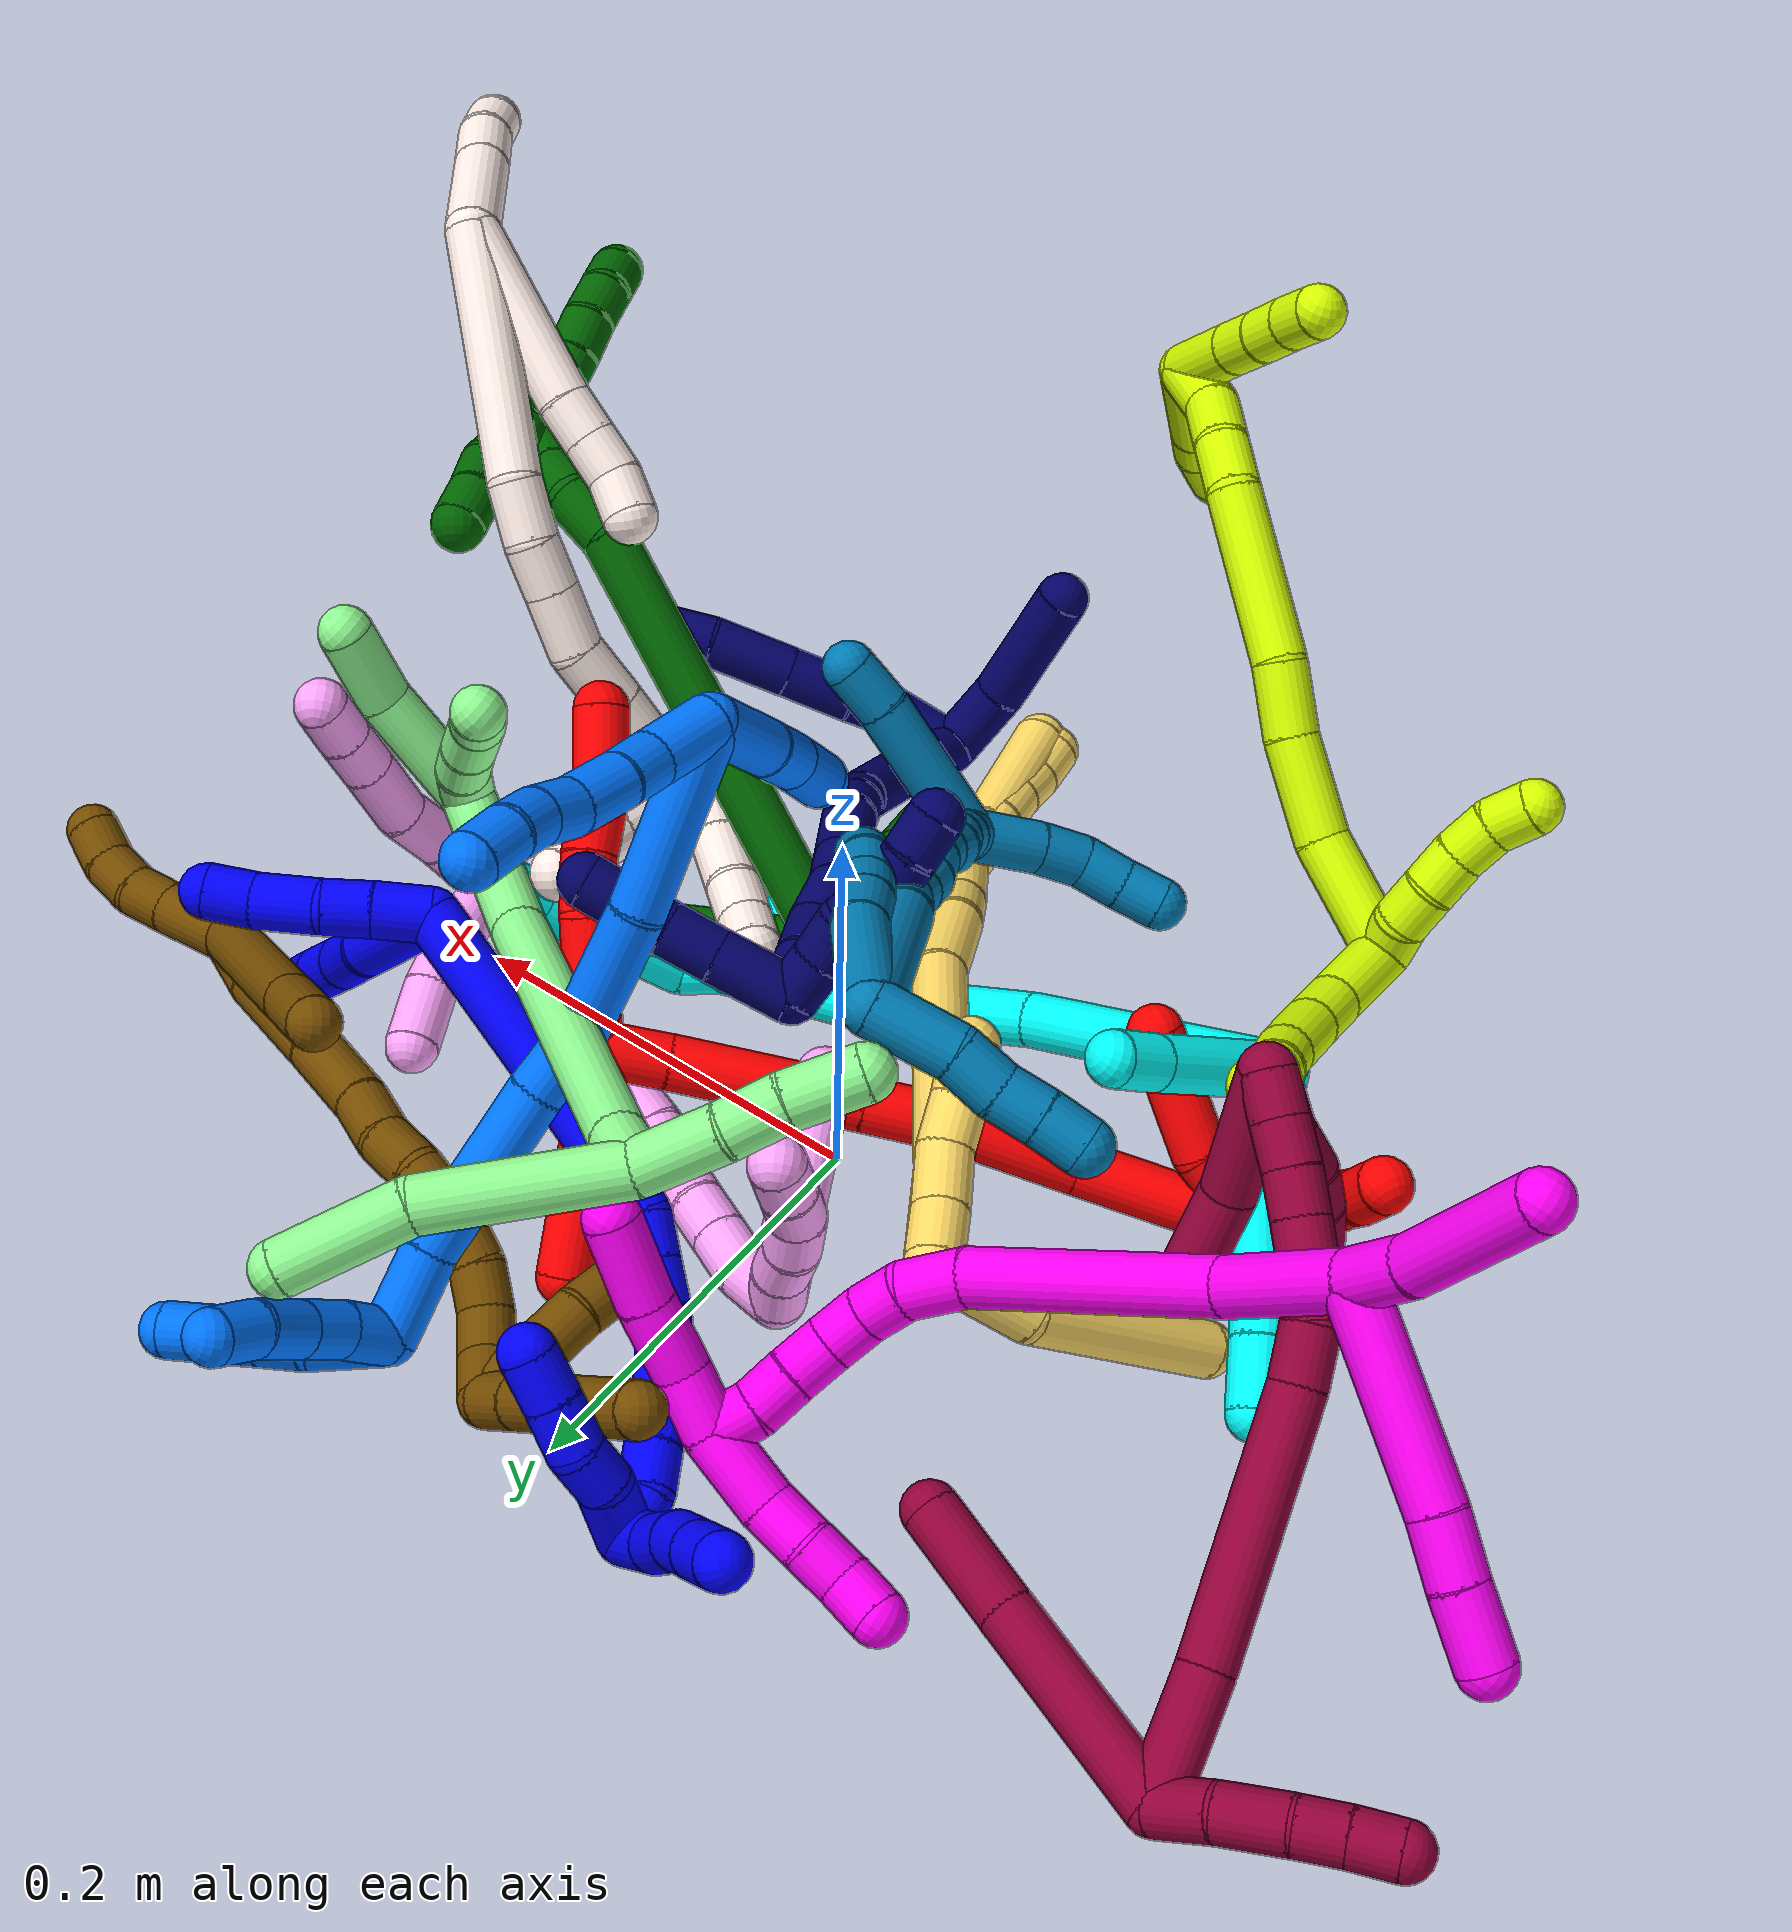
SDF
<sdf version="1.7">
 <world name="default">
  <plugin name="TubeGeneratorPlugin" filename="libtube_generator_plugin.so"/>
  <model name="photoneo_s_sensor">
   <static>1</static>
   <pose>0 0 2 1.57079 1.57079 3.14159</pose>
   <link name="link">
    <inertial><mass>0.1</mass></inertial>
    <sensor name="sensor" type="depth">
     <update_rate>30</update_rate>
     <camera>
      <horizontal_fov>1.22</horizontal_fov>
      <image><width>1920</width><height>1200</height><format>B8G8R8</format></image>
      <clip><near>0.1</near><far>4</far></clip>
      <depth_camera><output>points</output></depth_camera>
     </camera>
     <plugin name="camera_plugin" filename="libgazebo_ros_depth_camera.so">
      <baseline>0.2</baseline>
      <alwaysOn>1</alwaysOn>
      <updateRate>0.0</updateRate>
      <cameraName>camera_ir</cameraName>
      <imageTopicName>/camera/color/image_raw</imageTopicName>
      <cameraInfoTopicName>/camera/color/camera_info</cameraInfoTopicName>
      <depthImageTopicName>/camera/depth/image_raw</depthImageTopicName>
      <depthImageCameraInfoTopicName>/camera/depth/camera_info</depthImageCameraInfoTopicName>
      <pointCloudTopicName>/camera/depth/points</pointCloudTopicName>
      <frameName>fr_optical</frameName>
      <pointCloudCutoff>0.1</pointCloudCutoff>
      <pointCloudCutoffMax>2.0</pointCloudCutoffMax>
      <distortionK1>0</distortionK1>
      <distortionK2>0</distortionK2>
      <distortionK3>0</distortionK3>
      <distortionT1>0</distortionT1>
      <distortionT2>0</distortionT2>
      <CxPrime>0</CxPrime>
      <Cx>0</Cx>
      <Cy>0</Cy>
      <focalLength>0</focalLength>
      <hackBaseline>0</hackBaseline>
     </plugin>
    </sensor>
   </link>
  </model>
  <gravity>0 0 -9.8</gravity>
  <magnetic_field>6e-06 2.3e-05 -4.2e-05</magnetic_field>
  <atmosphere type="adiabatic"/>
  <physics name="default_physics" default="0" type="ode">
   <max_step_size>0.003</max_step_size>
   <real_time_factor>1</real_time_factor>
   <real_time_update_rate>1000</real_time_update_rate>
   <max_contacts>10000</max_contacts>
   <ode>
    <solver>
     <type>quick</type>
     <iters>100</iters>
     <sor>1.3</sor>
     <use_dynamic_moi_rescaling>0</use_dynamic_moi_rescaling>
    </solver>
    <constraints>
     <contact_max_correcting_vel>0</contact_max_correcting_vel>
     <contact_surface_layer>0.001</contact_surface_layer>
     <cfm>0</cfm>
     <erp>0.2</erp>
    </constraints>
   </ode>
  </physics>
  <scene><ambient>0.4 0.4 0.4 1</ambient><background>0.7 0.7 0.7 1</background><shadows>0</shadows></scene>
  <audio><device>default</device></audio>
  <spherical_coordinates>
   <surface_model>EARTH_WGS84</surface_model>
   <latitude_deg>0</latitude_deg>
   <longitude_deg>0</longitude_deg>
   <elevation>0</elevation>
   <heading_deg>0</heading_deg>
  </spherical_coordinates>
  <model name="bin">
   <static>1</static>
   <link name="bottom">
    <collision name="collision-bottom">
     <pose>0 0 -0.01 0 -0 0</pose>
     <geometry><box><size>0.8 0.6 0.02</size></box></geometry>
     <surface>
      <friction><ode><mu>100</mu><mu2>100</mu2></ode></friction>
      <contact><collide_bitmask>65535</collide_bitmask></contact>
     </surface>
    </collision>
   </link>
   <link name="west_wall">
    <collision name="collision-west_wall">
     <pose>-0.41 0 0.1 0 -0 0</pose>
     <geometry><box><size>0.02 0.6 0.2</size></box></geometry>
     <surface>
      <friction><ode><mu>100</mu><mu2>100</mu2></ode></friction>
      <contact><collide_bitmask>65535</collide_bitmask></contact>
     </surface>
    </collision>
   </link>
   <link name="east_wall">
    <collision name="collision-east_wall">
     <pose>0.41 0 0.1 0 -0 0</pose>
     <geometry><box><size>0.02 0.6 0.2</size></box></geometry>
     <surface>
      <friction><ode><mu>100</mu><mu2>100</mu2></ode></friction>
      <contact><collide_bitmask>65535</collide_bitmask></contact>
     </surface>
    </collision>
   </link>
   <link name="south_wall">
    <collision name="collision-south_wall">
     <pose>0 -0.31 0.1 0 -0 0</pose>
     <geometry><box><size>0.8 0.02 0.2</size></box></geometry>
     <surface>
      <friction><ode><mu>100</mu><mu2>100</mu2></ode></friction>
      <contact><collide_bitmask>65535</collide_bitmask></contact>
     </surface>
    </collision>
   </link>
   <link name="north_wall">
    <collision name="collision-north_wall">
     <pose>0 0.31 0.1 0 -0 0</pose>
     <geometry><box><size>0.8 0.02 0.2</size></box></geometry>
     <surface>
      <friction><ode><mu>100</mu><mu2>100</mu2></ode></friction>
      <contact><collide_bitmask>65535</collide_bitmask></contact>
     </surface>
    </collision>
   </link>
  </model>
  <model name="1">
   <static>0</static>
   <link name="1">
    <collision name="collision-cylinder-e_1_2_8">
     <pose>-0.005585 -0.004807 -0.027696 2.96976 -0.196118 -1.70333</pose>
     <geometry><cylinder><radius>0.0125</radius><length>0.057319</length></cylinder></geometry>
     <surface>
      <friction><ode><mu>1.16</mu><mu2>1.16</mu2><slip1>0</slip1><slip2>0</slip2></ode></friction>
      <contact><ode><kp>1e+06</kp><kd>1</kd><max_vel>0</max_vel><min_depth>0.001</min_depth></ode></contact>
     </surface>
    </collision>
    <visual name="visual-cylinder-e_1_2_8">
     <pose>-0.005585 -0.004807 -0.027696 2.96976 -0.196118 -1.70333</pose>
     <geometry><cylinder><radius>0.0125</radius><length>0.057319</length></cylinder></geometry>
     <material><ambient>0 0 1 1</ambient></material>
    </visual>
    <collision name="collision-cylinder-e_2_8_9">
     <pose>-0.015736 -0.017608 -0.072221 2.69811 -0.240388 -0.983619</pose>
     <geometry><cylinder><radius>0.0125</radius><length>0.038365</length></cylinder></geometry>
     <surface>
      <friction><ode><mu>1.16</mu><mu2>1.16</mu2><slip1>0</slip1><slip2>0</slip2></ode></friction>
      <contact><ode><kp>1e+06</kp><kd>1</kd><max_vel>0</max_vel><min_depth>0.001</min_depth></ode></contact>
     </surface>
    </collision>
    <visual name="visual-cylinder-e_2_8_9">
     <pose>-0.015736 -0.017608 -0.072221 2.69811 -0.240388 -0.983619</pose>
     <geometry><cylinder><radius>0.0125</radius><length>0.038365</length></cylinder></geometry>
     <material><ambient>0 0 1 1</ambient></material>
    </visual>
    <collision name="collision-cylinder-e_3_9_10">
     <pose>-0.023464 -0.030834 -0.103211 2.78771 -0.206347 -1.04976</pose>
     <geometry><cylinder><radius>0.0125</radius><length>0.030848</length></cylinder></geometry>
     <surface>
      <friction><ode><mu>1.16</mu><mu2>1.16</mu2><slip1>0</slip1><slip2>0</slip2></ode></friction>
      <contact><ode><kp>1e+06</kp><kd>1</kd><max_vel>0</max_vel><min_depth>0.001</min_depth></ode></contact>
     </surface>
    </collision>
    <visual name="visual-cylinder-e_3_9_10">
     <pose>-0.023464 -0.030834 -0.103211 2.78771 -0.206347 -1.04976</pose>
     <geometry><cylinder><radius>0.0125</radius><length>0.030848</length></cylinder></geometry>
     <material><ambient>0 0 1 1</ambient></material>
    </visual>
    <collision name="collision-cylinder-e_4_10_6">
     <pose>-0.029229 -0.040488 -0.127924 2.74467 -0.223902 -1.01946</pose>
     <geometry><cylinder><radius>0.0125</radius><length>0.023468</length></cylinder></geometry>
     <surface>
      <friction><ode><mu>1.16</mu><mu2>1.16</mu2><slip1>0</slip1><slip2>0</slip2></ode></friction>
      <contact><ode><kp>1e+06</kp><kd>1</kd><max_vel>0</max_vel><min_depth>0.001</min_depth></ode></contact>
     </surface>
    </collision>
    <visual name="visual-cylinder-e_4_10_6">
     <pose>-0.029229 -0.040488 -0.127924 2.74467 -0.223902 -1.01946</pose>
     <geometry><cylinder><radius>0.0125</radius><length>0.023468</length></cylinder></geometry>
     <material><ambient>0 0 1 1</ambient></material>
    </visual>
    <collision name="collision-cylinder-e_1_2_11">
     <pose>0.006742 0.005735 -0.009243 -2.5863 0.554837 -1.56994</pose>
     <geometry><cylinder><radius>0.0125</radius><length>0.025595</length></cylinder></geometry>
     <surface>
      <friction><ode><mu>1.16</mu><mu2>1.16</mu2><slip1>0</slip1><slip2>0</slip2></ode></friction>
      <contact><ode><kp>1e+06</kp><kd>1</kd><max_vel>0</max_vel><min_depth>0.001</min_depth></ode></contact>
     </surface>
    </collision>
    <visual name="visual-cylinder-e_1_2_11">
     <pose>0.006742 0.005735 -0.009243 -2.5863 0.554837 -1.56994</pose>
     <geometry><cylinder><radius>0.0125</radius><length>0.025595</length></cylinder></geometry>
     <material><ambient>0 0 1 1</ambient></material>
    </visual>
    <collision name="collision-cylinder-e_2_11_12">
     <pose>0.018677 0.016365 -0.026684 -2.60321 0.498164 -1.48965</pose>
     <geometry><cylinder><radius>0.0125</radius><length>0.021739</length></cylinder></geometry>
     <surface>
      <friction><ode><mu>1.16</mu><mu2>1.16</mu2><slip1>0</slip1><slip2>0</slip2></ode></friction>
      <contact><ode><kp>1e+06</kp><kd>1</kd><max_vel>0</max_vel><min_depth>0.001</min_depth></ode></contact>
     </surface>
    </collision>
    <visual name="visual-cylinder-e_2_11_12">
     <pose>0.018677 0.016365 -0.026684 -2.60321 0.498164 -1.48965</pose>
     <geometry><cylinder><radius>0.0125</radius><length>0.021739</length></cylinder></geometry>
     <material><ambient>0 0 1 1</ambient></material>
    </visual>
    <collision name="collision-cylinder-e_3_12_13">
     <pose>0.030221 0.02448 -0.048461 -2.90883 0.427029 -2.15255</pose>
     <geometry><cylinder><radius>0.0125</radius><length>0.030664</length></cylinder></geometry>
     <surface>
      <friction><ode><mu>1.16</mu><mu2>1.16</mu2><slip1>0</slip1><slip2>0</slip2></ode></friction>
      <contact><ode><kp>1e+06</kp><kd>1</kd><max_vel>0</max_vel><min_depth>0.001</min_depth></ode></contact>
     </surface>
    </collision>
    <visual name="visual-cylinder-e_3_12_13">
     <pose>0.030221 0.02448 -0.048461 -2.90883 0.427029 -2.15255</pose>
     <geometry><cylinder><radius>0.0125</radius><length>0.030664</length></cylinder></geometry>
     <material><ambient>0 0 1 1</ambient></material>
    </visual>
    <collision name="collision-cylinder-e_4_13_5">
     <pose>0.042822 0.031203 -0.070386 -2.74413 0.604339 -1.99438</pose>
     <geometry><cylinder><radius>0.0125</radius><length>0.022002</length></cylinder></geometry>
     <surface>
      <friction><ode><mu>1.16</mu><mu2>1.16</mu2><slip1>0</slip1><slip2>0</slip2></ode></friction>
      <contact><ode><kp>1e+06</kp><kd>1</kd><max_vel>0</max_vel><min_depth>0.001</min_depth></ode></contact>
     </surface>
    </collision>
    <visual name="visual-cylinder-e_4_13_5">
     <pose>0.042822 0.031203 -0.070386 -2.74413 0.604339 -1.99438</pose>
     <geometry><cylinder><radius>0.0125</radius><length>0.022002</length></cylinder></geometry>
     <material><ambient>0 0 1 1</ambient></material>
    </visual>
    <collision name="collision-cylinder-e_1_2_14">
     <pose>-0.060368 0.017391 0.029592 -0.531326 -1.05379 0.31398</pose>
     <geometry><cylinder><radius>0.0125</radius><length>0.138887</length></cylinder></geometry>
     <surface>
      <friction><ode><mu>1.16</mu><mu2>1.16</mu2><slip1>0</slip1><slip2>0</slip2></ode></friction>
      <contact><ode><kp>1e+06</kp><kd>1</kd><max_vel>0</max_vel><min_depth>0.001</min_depth></ode></contact>
     </surface>
    </collision>
    <visual name="visual-cylinder-e_1_2_14">
     <pose>-0.060368 0.017391 0.029592 -0.531326 -1.05379 0.31398</pose>
     <geometry><cylinder><radius>0.0125</radius><length>0.138887</length></cylinder></geometry>
     <material><ambient>0 0 1 1</ambient></material>
    </visual>
    <collision name="collision-cylinder-e_2_14_15">
     <pose>-0.129758 0.038184 0.062881 -0.743822 -1.0628 0.450769</pose>
     <geometry><cylinder><radius>0.0125</radius><length>0.020654</length></cylinder></geometry>
     <surface>
      <friction><ode><mu>1.16</mu><mu2>1.16</mu2><slip1>0</slip1><slip2>0</slip2></ode></friction>
      <contact><ode><kp>1e+06</kp><kd>1</kd><max_vel>0</max_vel><min_depth>0.001</min_depth></ode></contact>
     </surface>
    </collision>
    <visual name="visual-cylinder-e_2_14_15">
     <pose>-0.129758 0.038184 0.062881 -0.743822 -1.0628 0.450769</pose>
     <geometry><cylinder><radius>0.0125</radius><length>0.020654</length></cylinder></geometry>
     <material><ambient>0 0 1 1</ambient></material>
    </visual>
    <collision name="collision-cylinder-e_3_15_16">
     <pose>-0.147136 0.047048 0.067789 -1.35262 -0.980723 0.80959</pose>
     <geometry><cylinder><radius>0.0125</radius><length>0.020112</length></cylinder></geometry>
     <surface>
      <friction><ode><mu>1.16</mu><mu2>1.16</mu2><slip1>0</slip1><slip2>0</slip2></ode></friction>
      <contact><ode><kp>1e+06</kp><kd>1</kd><max_vel>0</max_vel><min_depth>0.001</min_depth></ode></contact>
     </surface>
    </collision>
    <visual name="visual-cylinder-e_3_15_16">
     <pose>-0.147136 0.047048 0.067789 -1.35262 -0.980723 0.80959</pose>
     <geometry><cylinder><radius>0.0125</radius><length>0.020112</length></cylinder></geometry>
     <material><ambient>0 0 1 1</ambient></material>
    </visual>
    <collision name="collision-cylinder-e_4_16_17">
     <pose>-0.164006 0.057755 0.070213 -1.3435 -1.00704 0.825677</pose>
     <geometry><cylinder><radius>0.0125</radius><length>0.020145</length></cylinder></geometry>
     <surface>
      <friction><ode><mu>1.16</mu><mu2>1.16</mu2><slip1>0</slip1><slip2>0</slip2></ode></friction>
      <contact><ode><kp>1e+06</kp><kd>1</kd><max_vel>0</max_vel><min_depth>0.001</min_depth></ode></contact>
     </surface>
    </collision>
    <visual name="visual-cylinder-e_4_16_17">
     <pose>-0.164006 0.057755 0.070213 -1.3435 -1.00704 0.825677</pose>
     <geometry><cylinder><radius>0.0125</radius><length>0.020145</length></cylinder></geometry>
     <material><ambient>0 0 1 1</ambient></material>
    </visual>
    <collision name="collision-cylinder-e_5_17_18">
     <pose>-0.179966 0.069676 0.072297 -1.44101 -0.835571 0.743271</pose>
     <geometry><cylinder><radius>0.0125</radius><length>0.020079</length></cylinder></geometry>
     <surface>
      <friction><ode><mu>1.16</mu><mu2>1.16</mu2><slip1>0</slip1><slip2>0</slip2></ode></friction>
      <contact><ode><kp>1e+06</kp><kd>1</kd><max_vel>0</max_vel><min_depth>0.001</min_depth></ode></contact>
     </surface>
    </collision>
    <visual name="visual-cylinder-e_5_17_18">
     <pose>-0.179966 0.069676 0.072297 -1.44101 -0.835571 0.743271</pose>
     <geometry><cylinder><radius>0.0125</radius><length>0.020079</length></cylinder></geometry>
     <material><ambient>0 0 1 1</ambient></material>
    </visual>
    <collision name="collision-cylinder-e_6_18_19">
     <pose>-0.194207 0.083698 0.072682 -1.63691 -0.745441 0.791409</pose>
     <geometry><cylinder><radius>0.0125</radius><length>0.020035</length></cylinder></geometry>
     <surface>
      <friction><ode><mu>1.16</mu><mu2>1.16</mu2><slip1>0</slip1><slip2>0</slip2></ode></friction>
      <contact><ode><kp>1e+06</kp><kd>1</kd><max_vel>0</max_vel><min_depth>0.001</min_depth></ode></contact>
     </surface>
    </collision>
    <visual name="visual-cylinder-e_6_18_19">
     <pose>-0.194207 0.083698 0.072682 -1.63691 -0.745441 0.791409</pose>
     <geometry><cylinder><radius>0.0125</radius><length>0.020035</length></cylinder></geometry>
     <material><ambient>0 0 1 1</ambient></material>
    </visual>
    <collision name="collision-cylinder-e_7_19_20">
     <pose>-0.206062 0.099666 0.073111 -1.46505 -0.528257 0.477251</pose>
     <geometry><cylinder><radius>0.0125</radius><length>0.020078</length></cylinder></geometry>
     <surface>
      <friction><ode><mu>1.16</mu><mu2>1.16</mu2><slip1>0</slip1><slip2>0</slip2></ode></friction>
      <contact><ode><kp>1e+06</kp><kd>1</kd><max_vel>0</max_vel><min_depth>0.001</min_depth></ode></contact>
     </surface>
    </collision>
    <visual name="visual-cylinder-e_7_19_20">
     <pose>-0.206062 0.099666 0.073111 -1.46505 -0.528257 0.477251</pose>
     <geometry><cylinder><radius>0.0125</radius><length>0.020078</length></cylinder></geometry>
     <material><ambient>0 0 1 1</ambient></material>
    </visual>
    <collision name="collision-cylinder-e_8_20_21">
     <pose>-0.216342 0.116801 0.074614 -1.50189 -0.548954 0.514016</pose>
     <geometry><cylinder><radius>0.0125</radius><length>0.020006</length></cylinder></geometry>
     <surface>
      <friction><ode><mu>1.16</mu><mu2>1.16</mu2><slip1>0</slip1><slip2>0</slip2></ode></friction>
      <contact><ode><kp>1e+06</kp><kd>1</kd><max_vel>0</max_vel><min_depth>0.001</min_depth></ode></contact>
     </surface>
    </collision>
    <visual name="visual-cylinder-e_8_20_21">
     <pose>-0.216342 0.116801 0.074614 -1.50189 -0.548954 0.514016</pose>
     <geometry><cylinder><radius>0.0125</radius><length>0.020006</length></cylinder></geometry>
     <material><ambient>0 0 1 1</ambient></material>
    </visual>
    <collision name="collision-cylinder-e_9_21_1">
     <pose>-0.225875 0.134028 0.072858 -1.83352 -0.445959 0.575176</pose>
     <geometry><cylinder><radius>0.0125</radius><length>0.020002</length></cylinder></geometry>
     <surface>
      <friction><ode><mu>1.16</mu><mu2>1.16</mu2><slip1>0</slip1><slip2>0</slip2></ode></friction>
      <contact><ode><kp>1e+06</kp><kd>1</kd><max_vel>0</max_vel><min_depth>0.001</min_depth></ode></contact>
     </surface>
    </collision>
    <visual name="visual-cylinder-e_9_21_1">
     <pose>-0.225875 0.134028 0.072858 -1.83352 -0.445959 0.575176</pose>
     <geometry><cylinder><radius>0.0125</radius><length>0.020002</length></cylinder></geometry>
     <material><ambient>0 0 1 1</ambient></material>
    </visual>
    <collision name="collision-cylinder-e_1_1_22">
     <pose>-0.21489 0.146567 0.076754 -0.550005 1.12458 -0.351916</pose>
     <geometry><cylinder><radius>0.0125</radius><length>0.033919</length></cylinder></geometry>
     <surface>
      <friction><ode><mu>1.16</mu><mu2>1.16</mu2><slip1>0</slip1><slip2>0</slip2></ode></friction>
      <contact><ode><kp>1e+06</kp><kd>1</kd><max_vel>0</max_vel><min_depth>0.001</min_depth></ode></contact>
     </surface>
    </collision>
    <visual name="visual-cylinder-e_1_1_22">
     <pose>-0.21489 0.146567 0.076754 -0.550005 1.12458 -0.351916</pose>
     <geometry><cylinder><radius>0.0125</radius><length>0.033919</length></cylinder></geometry>
     <material><ambient>0 0 1 1</ambient></material>
    </visual>
    <collision name="collision-cylinder-e_2_22_23">
     <pose>-0.189404 0.152936 0.083306 -1.44869 1.32436 -1.20767</pose>
     <geometry><cylinder><radius>0.0125</radius><length>0.021009</length></cylinder></geometry>
     <surface>
      <friction><ode><mu>1.16</mu><mu2>1.16</mu2><slip1>0</slip1><slip2>0</slip2></ode></friction>
      <contact><ode><kp>1e+06</kp><kd>1</kd><max_vel>0</max_vel><min_depth>0.001</min_depth></ode></contact>
     </surface>
    </collision>
    <visual name="visual-cylinder-e_2_22_23">
     <pose>-0.189404 0.152936 0.083306 -1.44869 1.32436 -1.20767</pose>
     <geometry><cylinder><radius>0.0125</radius><length>0.021009</length></cylinder></geometry>
     <material><ambient>0 0 1 1</ambient></material>
    </visual>
    <collision name="collision-cylinder-e_3_23_24">
     <pose>-0.167697 0.154463 0.083611 1.57765 1.48277 1.4896</pose>
     <geometry><cylinder><radius>0.0125</radius><length>0.023129</length></cylinder></geometry>
     <surface>
      <friction><ode><mu>1.16</mu><mu2>1.16</mu2><slip1>0</slip1><slip2>0</slip2></ode></friction>
      <contact><ode><kp>1e+06</kp><kd>1</kd><max_vel>0</max_vel><min_depth>0.001</min_depth></ode></contact>
     </surface>
    </collision>
    <visual name="visual-cylinder-e_3_23_24">
     <pose>-0.167697 0.154463 0.083611 1.57765 1.48277 1.4896</pose>
     <geometry><cylinder><radius>0.0125</radius><length>0.023129</length></cylinder></geometry>
     <material><ambient>0 0 1 1</ambient></material>
    </visual>
    <collision name="collision-cylinder-e_4_24_4">
     <pose>-0.145256 0.152546 0.083062 2.11287 1.47488 2.0286</pose>
     <geometry><cylinder><radius>0.0125</radius><length>0.021943</length></cylinder></geometry>
     <surface>
      <friction><ode><mu>1.16</mu><mu2>1.16</mu2><slip1>0</slip1><slip2>0</slip2></ode></friction>
      <contact><ode><kp>1e+06</kp><kd>1</kd><max_vel>0</max_vel><min_depth>0.001</min_depth></ode></contact>
     </surface>
    </collision>
    <visual name="visual-cylinder-e_4_24_4">
     <pose>-0.145256 0.152546 0.083062 2.11287 1.47488 2.0286</pose>
     <geometry><cylinder><radius>0.0125</radius><length>0.021943</length></cylinder></geometry>
     <material><ambient>0 0 1 1</ambient></material>
    </visual>
    <collision name="collision-cylinder-e_1_1_25">
     <pose>-0.229321 0.148023 0.08318 -0.39507 0.063187 -0.012651</pose>
     <geometry><cylinder><radius>0.0125</radius><length>0.0275</length></cylinder></geometry>
     <surface>
      <friction><ode><mu>1.16</mu><mu2>1.16</mu2><slip1>0</slip1><slip2>0</slip2></ode></friction>
      <contact><ode><kp>1e+06</kp><kd>1</kd><max_vel>0</max_vel><min_depth>0.001</min_depth></ode></contact>
     </surface>
    </collision>
    <visual name="visual-cylinder-e_1_1_25">
     <pose>-0.229321 0.148023 0.08318 -0.39507 0.063187 -0.012651</pose>
     <geometry><cylinder><radius>0.0125</radius><length>0.0275</length></cylinder></geometry>
     <material><ambient>0 0 1 1</ambient></material>
    </visual>
    <collision name="collision-cylinder-e_2_25_26">
     <pose>-0.225305 0.1578 0.106707 -0.392447 0.261579 -0.052284</pose>
     <geometry><cylinder><radius>0.0125</radius><length>0.024339</length></cylinder></geometry>
     <surface>
      <friction><ode><mu>1.16</mu><mu2>1.16</mu2><slip1>0</slip1><slip2>0</slip2></ode></friction>
      <contact><ode><kp>1e+06</kp><kd>1</kd><max_vel>0</max_vel><min_depth>0.001</min_depth></ode></contact>
     </surface>
    </collision>
    <visual name="visual-cylinder-e_2_25_26">
     <pose>-0.225305 0.1578 0.106707 -0.392447 0.261579 -0.052284</pose>
     <geometry><cylinder><radius>0.0125</radius><length>0.024339</length></cylinder></geometry>
     <material><ambient>0 0 1 1</ambient></material>
    </visual>
    <collision name="collision-cylinder-e_3_26_27">
     <pose>-0.220908 0.168513 0.127888 -0.542229 0.103453 -0.028779</pose>
     <geometry><cylinder><radius>0.0125</radius><length>0.024224</length></cylinder></geometry>
     <surface>
      <friction><ode><mu>1.16</mu><mu2>1.16</mu2><slip1>0</slip1><slip2>0</slip2></ode></friction>
      <contact><ode><kp>1e+06</kp><kd>1</kd><max_vel>0</max_vel><min_depth>0.001</min_depth></ode></contact>
     </surface>
    </collision>
    <visual name="visual-cylinder-e_3_26_27">
     <pose>-0.220908 0.168513 0.127888 -0.542229 0.103453 -0.028779</pose>
     <geometry><cylinder><radius>0.0125</radius><length>0.024224</length></cylinder></geometry>
     <material><ambient>0 0 1 1</ambient></material>
    </visual>
    <collision name="collision-cylinder-e_4_27_3">
     <pose>-0.218711 0.180695 0.14854 -0.523617 0.079126 -0.021213</pose>
     <geometry><cylinder><radius>0.0125</radius><length>0.023938</length></cylinder></geometry>
     <surface>
      <friction><ode><mu>1.16</mu><mu2>1.16</mu2><slip1>0</slip1><slip2>0</slip2></ode></friction>
      <contact><ode><kp>1e+06</kp><kd>1</kd><max_vel>0</max_vel><min_depth>0.001</min_depth></ode></contact>
     </surface>
    </collision>
    <visual name="visual-cylinder-e_4_27_3">
     <pose>-0.218711 0.180695 0.14854 -0.523617 0.079126 -0.021213</pose>
     <geometry><cylinder><radius>0.0125</radius><length>0.023938</length></cylinder></geometry>
     <material><ambient>0 0 1 1</ambient></material>
    </visual>
    <collision name="collision-sphere-3">
     <pose>-0.217765 0.186661 0.158873 0 -0 0</pose>
     <geometry><sphere><radius>0.0125</radius></sphere></geometry>
     <surface>
      <friction><ode><mu>1.16</mu><mu2>1.16</mu2><slip1>0</slip1><slip2>0</slip2></ode></friction>
      <contact><ode><kp>1e+06</kp><kd>1</kd><max_vel>0</max_vel><min_depth>0.001</min_depth></ode></contact>
     </surface>
    </collision>
    <visual name="visual-sphere-3">
     <pose>-0.217765 0.186661 0.158873 0 -0 0</pose>
     <geometry><sphere><radius>0.0125</radius></sphere></geometry>
     <material><ambient>0 0 1 1</ambient></material>
    </visual>
    <collision name="collision-sphere-27">
     <pose>-0.219657 0.17473 0.138207 0 -0 0</pose>
     <geometry><sphere><radius>0.0125</radius></sphere></geometry>
     <surface>
      <friction><ode><mu>1.16</mu><mu2>1.16</mu2><slip1>0</slip1><slip2>0</slip2></ode></friction>
      <contact><ode><kp>1e+06</kp><kd>1</kd><max_vel>0</max_vel><min_depth>0.001</min_depth></ode></contact>
     </surface>
    </collision>
    <visual name="visual-sphere-27">
     <pose>-0.219657 0.17473 0.138207 0 -0 0</pose>
     <geometry><sphere><radius>0.0125</radius></sphere></geometry>
     <material><ambient>0 0 1 1</ambient></material>
    </visual>
    <collision name="collision-sphere-26">
     <pose>-0.222158 0.162296 0.117569 0 -0 0</pose>
     <geometry><sphere><radius>0.0125</radius></sphere></geometry>
     <surface>
      <friction><ode><mu>1.16</mu><mu2>1.16</mu2><slip1>0</slip1><slip2>0</slip2></ode></friction>
      <contact><ode><kp>1e+06</kp><kd>1</kd><max_vel>0</max_vel><min_depth>0.001</min_depth></ode></contact>
     </surface>
    </collision>
    <visual name="visual-sphere-26">
     <pose>-0.222158 0.162296 0.117569 0 -0 0</pose>
     <geometry><sphere><radius>0.0125</radius></sphere></geometry>
     <material><ambient>0 0 1 1</ambient></material>
    </visual>
    <collision name="collision-sphere-25">
     <pose>-0.228452 0.153304 0.095846 0 -0 0</pose>
     <geometry><sphere><radius>0.0125</radius></sphere></geometry>
     <surface>
      <friction><ode><mu>1.16</mu><mu2>1.16</mu2><slip1>0</slip1><slip2>0</slip2></ode></friction>
      <contact><ode><kp>1e+06</kp><kd>1</kd><max_vel>0</max_vel><min_depth>0.001</min_depth></ode></contact>
     </surface>
    </collision>
    <visual name="visual-sphere-25">
     <pose>-0.228452 0.153304 0.095846 0 -0 0</pose>
     <geometry><sphere><radius>0.0125</radius></sphere></geometry>
     <material><ambient>0 0 1 1</ambient></material>
    </visual>
    <collision name="collision-sphere-4">
     <pose>-0.134335 0.151646 0.08252 0 -0 0</pose>
     <geometry><sphere><radius>0.0125</radius></sphere></geometry>
     <surface>
      <friction><ode><mu>1.16</mu><mu2>1.16</mu2><slip1>0</slip1><slip2>0</slip2></ode></friction>
      <contact><ode><kp>1e+06</kp><kd>1</kd><max_vel>0</max_vel><min_depth>0.001</min_depth></ode></contact>
     </surface>
    </collision>
    <visual name="visual-sphere-4">
     <pose>-0.134335 0.151646 0.08252 0 -0 0</pose>
     <geometry><sphere><radius>0.0125</radius></sphere></geometry>
     <material><ambient>0 0 1 1</ambient></material>
    </visual>
    <collision name="collision-sphere-24">
     <pose>-0.156177 0.153446 0.083604 0 -0 0</pose>
     <geometry><sphere><radius>0.0125</radius></sphere></geometry>
     <surface>
      <friction><ode><mu>1.16</mu><mu2>1.16</mu2><slip1>0</slip1><slip2>0</slip2></ode></friction>
      <contact><ode><kp>1e+06</kp><kd>1</kd><max_vel>0</max_vel><min_depth>0.001</min_depth></ode></contact>
     </surface>
    </collision>
    <visual name="visual-sphere-24">
     <pose>-0.156177 0.153446 0.083604 0 -0 0</pose>
     <geometry><sphere><radius>0.0125</radius></sphere></geometry>
     <material><ambient>0 0 1 1</ambient></material>
    </visual>
    <collision name="collision-sphere-23">
     <pose>-0.179217 0.155479 0.083618 0 -0 0</pose>
     <geometry><sphere><radius>0.0125</radius></sphere></geometry>
     <surface>
      <friction><ode><mu>1.16</mu><mu2>1.16</mu2><slip1>0</slip1><slip2>0</slip2></ode></friction>
      <contact><ode><kp>1e+06</kp><kd>1</kd><max_vel>0</max_vel><min_depth>0.001</min_depth></ode></contact>
     </surface>
    </collision>
    <visual name="visual-sphere-23">
     <pose>-0.179217 0.155479 0.083618 0 -0 0</pose>
     <geometry><sphere><radius>0.0125</radius></sphere></geometry>
     <material><ambient>0 0 1 1</ambient></material>
    </visual>
    <collision name="collision-sphere-22">
     <pose>-0.199591 0.150392 0.082994 0 -0 0</pose>
     <geometry><sphere><radius>0.0125</radius></sphere></geometry>
     <surface>
      <friction><ode><mu>1.16</mu><mu2>1.16</mu2><slip1>0</slip1><slip2>0</slip2></ode></friction>
      <contact><ode><kp>1e+06</kp><kd>1</kd><max_vel>0</max_vel><min_depth>0.001</min_depth></ode></contact>
     </surface>
    </collision>
    <visual name="visual-sphere-22">
     <pose>-0.199591 0.150392 0.082994 0 -0 0</pose>
     <geometry><sphere><radius>0.0125</radius></sphere></geometry>
     <material><ambient>0 0 1 1</ambient></material>
    </visual>
    <collision name="collision-sphere-1">
     <pose>-0.230189 0.142741 0.070515 0 -0 0</pose>
     <geometry><sphere><radius>0.0125</radius></sphere></geometry>
     <surface>
      <friction><ode><mu>1.16</mu><mu2>1.16</mu2><slip1>0</slip1><slip2>0</slip2></ode></friction>
      <contact><ode><kp>1e+06</kp><kd>1</kd><max_vel>0</max_vel><min_depth>0.001</min_depth></ode></contact>
     </surface>
    </collision>
    <visual name="visual-sphere-1">
     <pose>-0.230189 0.142741 0.070515 0 -0 0</pose>
     <geometry><sphere><radius>0.0125</radius></sphere></geometry>
     <material><ambient>0 0 1 1</ambient></material>
    </visual>
    <collision name="collision-sphere-21">
     <pose>-0.221561 0.125314 0.075201 0 -0 0</pose>
     <geometry><sphere><radius>0.0125</radius></sphere></geometry>
     <surface>
      <friction><ode><mu>1.16</mu><mu2>1.16</mu2><slip1>0</slip1><slip2>0</slip2></ode></friction>
      <contact><ode><kp>1e+06</kp><kd>1</kd><max_vel>0</max_vel><min_depth>0.001</min_depth></ode></contact>
     </surface>
    </collision>
    <visual name="visual-sphere-21">
     <pose>-0.221561 0.125314 0.075201 0 -0 0</pose>
     <geometry><sphere><radius>0.0125</radius></sphere></geometry>
     <material><ambient>0 0 1 1</ambient></material>
    </visual>
    <collision name="collision-sphere-11">
     <pose>0.013483 0.011469 -0.018486 0 -0 0</pose>
     <geometry><sphere><radius>0.0125</radius></sphere></geometry>
     <surface>
      <friction><ode><mu>1.16</mu><mu2>1.16</mu2><slip1>0</slip1><slip2>0</slip2></ode></friction>
      <contact><ode><kp>1e+06</kp><kd>1</kd><max_vel>0</max_vel><min_depth>0.001</min_depth></ode></contact>
     </surface>
    </collision>
    <visual name="visual-sphere-11">
     <pose>0.013483 0.011469 -0.018486 0 -0 0</pose>
     <geometry><sphere><radius>0.0125</radius></sphere></geometry>
     <material><ambient>0 0 1 1</ambient></material>
    </visual>
    <collision name="collision-sphere-6">
     <pose>-0.031834 -0.044911 -0.138475 0 -0 0</pose>
     <geometry><sphere><radius>0.0125</radius></sphere></geometry>
     <surface>
      <friction><ode><mu>1.16</mu><mu2>1.16</mu2><slip1>0</slip1><slip2>0</slip2></ode></friction>
      <contact><ode><kp>1e+06</kp><kd>1</kd><max_vel>0</max_vel><min_depth>0.001</min_depth></ode></contact>
     </surface>
    </collision>
    <visual name="visual-sphere-6">
     <pose>-0.031834 -0.044911 -0.138475 0 -0 0</pose>
     <geometry><sphere><radius>0.0125</radius></sphere></geometry>
     <material><ambient>0 0 1 1</ambient></material>
    </visual>
    <collision name="collision-sphere-10">
     <pose>-0.026624 -0.036065 -0.117372 0 -0 0</pose>
     <geometry><sphere><radius>0.0125</radius></sphere></geometry>
     <surface>
      <friction><ode><mu>1.16</mu><mu2>1.16</mu2><slip1>0</slip1><slip2>0</slip2></ode></friction>
      <contact><ode><kp>1e+06</kp><kd>1</kd><max_vel>0</max_vel><min_depth>0.001</min_depth></ode></contact>
     </surface>
    </collision>
    <visual name="visual-sphere-10">
     <pose>-0.026624 -0.036065 -0.117372 0 -0 0</pose>
     <geometry><sphere><radius>0.0125</radius></sphere></geometry>
     <material><ambient>0 0 1 1</ambient></material>
    </visual>
    <collision name="collision-sphere-9">
     <pose>-0.020303 -0.025602 -0.08905 0 -0 0</pose>
     <geometry><sphere><radius>0.0125</radius></sphere></geometry>
     <surface>
      <friction><ode><mu>1.16</mu><mu2>1.16</mu2><slip1>0</slip1><slip2>0</slip2></ode></friction>
      <contact><ode><kp>1e+06</kp><kd>1</kd><max_vel>0</max_vel><min_depth>0.001</min_depth></ode></contact>
     </surface>
    </collision>
    <visual name="visual-sphere-9">
     <pose>-0.020303 -0.025602 -0.08905 0 -0 0</pose>
     <geometry><sphere><radius>0.0125</radius></sphere></geometry>
     <material><ambient>0 0 1 1</ambient></material>
    </visual>
    <collision name="collision-sphere-2">
     <geometry><sphere><radius>0.0125</radius></sphere></geometry>
     <surface>
      <friction><ode><mu>1.16</mu><mu2>1.16</mu2><slip1>0</slip1><slip2>0</slip2></ode></friction>
      <contact><ode><kp>1e+06</kp><kd>1</kd><max_vel>0</max_vel><min_depth>0.001</min_depth></ode></contact>
     </surface>
    </collision>
    <visual name="visual-sphere-2">
     <geometry><sphere><radius>0.0125</radius></sphere></geometry>
     <material><ambient>0 0 1 1</ambient></material>
    </visual>
    <collision name="collision-sphere-19">
     <pose>-0.201002 0.091043 0.072196 0 -0 0</pose>
     <geometry><sphere><radius>0.0125</radius></sphere></geometry>
     <surface>
      <friction><ode><mu>1.16</mu><mu2>1.16</mu2><slip1>0</slip1><slip2>0</slip2></ode></friction>
      <contact><ode><kp>1e+06</kp><kd>1</kd><max_vel>0</max_vel><min_depth>0.001</min_depth></ode></contact>
     </surface>
    </collision>
    <visual name="visual-sphere-19">
     <pose>-0.201002 0.091043 0.072196 0 -0 0</pose>
     <geometry><sphere><radius>0.0125</radius></sphere></geometry>
     <material><ambient>0 0 1 1</ambient></material>
    </visual>
    <collision name="collision-sphere-8">
     <pose>-0.011169 -0.009613 -0.055392 0 -0 0</pose>
     <geometry><sphere><radius>0.0125</radius></sphere></geometry>
     <surface>
      <friction><ode><mu>1.16</mu><mu2>1.16</mu2><slip1>0</slip1><slip2>0</slip2></ode></friction>
      <contact><ode><kp>1e+06</kp><kd>1</kd><max_vel>0</max_vel><min_depth>0.001</min_depth></ode></contact>
     </surface>
    </collision>
    <visual name="visual-sphere-8">
     <pose>-0.011169 -0.009613 -0.055392 0 -0 0</pose>
     <geometry><sphere><radius>0.0125</radius></sphere></geometry>
     <material><ambient>0 0 1 1</ambient></material>
    </visual>
    <collision name="collision-sphere-12">
     <pose>0.023871 0.021261 -0.034882 0 -0 0</pose>
     <geometry><sphere><radius>0.0125</radius></sphere></geometry>
     <surface>
      <friction><ode><mu>1.16</mu><mu2>1.16</mu2><slip1>0</slip1><slip2>0</slip2></ode></friction>
      <contact><ode><kp>1e+06</kp><kd>1</kd><max_vel>0</max_vel><min_depth>0.001</min_depth></ode></contact>
     </surface>
    </collision>
    <visual name="visual-sphere-12">
     <pose>0.023871 0.021261 -0.034882 0 -0 0</pose>
     <geometry><sphere><radius>0.0125</radius></sphere></geometry>
     <material><ambient>0 0 1 1</ambient></material>
    </visual>
    <collision name="collision-sphere-13">
     <pose>0.036571 0.027699 -0.06204 0 -0 0</pose>
     <geometry><sphere><radius>0.0125</radius></sphere></geometry>
     <surface>
      <friction><ode><mu>1.16</mu><mu2>1.16</mu2><slip1>0</slip1><slip2>0</slip2></ode></friction>
      <contact><ode><kp>1e+06</kp><kd>1</kd><max_vel>0</max_vel><min_depth>0.001</min_depth></ode></contact>
     </surface>
    </collision>
    <visual name="visual-sphere-13">
     <pose>0.036571 0.027699 -0.06204 0 -0 0</pose>
     <geometry><sphere><radius>0.0125</radius></sphere></geometry>
     <material><ambient>0 0 1 1</ambient></material>
    </visual>
    <collision name="collision-sphere-5">
     <pose>0.049073 0.034707 -0.078733 0 -0 0</pose>
     <geometry><sphere><radius>0.0125</radius></sphere></geometry>
     <surface>
      <friction><ode><mu>1.16</mu><mu2>1.16</mu2><slip1>0</slip1><slip2>0</slip2></ode></friction>
      <contact><ode><kp>1e+06</kp><kd>1</kd><max_vel>0</max_vel><min_depth>0.001</min_depth></ode></contact>
     </surface>
    </collision>
    <visual name="visual-sphere-5">
     <pose>0.049073 0.034707 -0.078733 0 -0 0</pose>
     <geometry><sphere><radius>0.0125</radius></sphere></geometry>
     <material><ambient>0 0 1 1</ambient></material>
    </visual>
    <collision name="collision-sphere-14">
     <pose>-0.120735 0.034783 0.059184 0 -0 0</pose>
     <geometry><sphere><radius>0.0125</radius></sphere></geometry>
     <surface>
      <friction><ode><mu>1.16</mu><mu2>1.16</mu2><slip1>0</slip1><slip2>0</slip2></ode></friction>
      <contact><ode><kp>1e+06</kp><kd>1</kd><max_vel>0</max_vel><min_depth>0.001</min_depth></ode></contact>
     </surface>
    </collision>
    <visual name="visual-sphere-14">
     <pose>-0.120735 0.034783 0.059184 0 -0 0</pose>
     <geometry><sphere><radius>0.0125</radius></sphere></geometry>
     <material><ambient>0 0 1 1</ambient></material>
    </visual>
    <collision name="collision-sphere-15">
     <pose>-0.138781 0.041585 0.066577 0 -0 0</pose>
     <geometry><sphere><radius>0.0125</radius></sphere></geometry>
     <surface>
      <friction><ode><mu>1.16</mu><mu2>1.16</mu2><slip1>0</slip1><slip2>0</slip2></ode></friction>
      <contact><ode><kp>1e+06</kp><kd>1</kd><max_vel>0</max_vel><min_depth>0.001</min_depth></ode></contact>
     </surface>
    </collision>
    <visual name="visual-sphere-15">
     <pose>-0.138781 0.041585 0.066577 0 -0 0</pose>
     <geometry><sphere><radius>0.0125</radius></sphere></geometry>
     <material><ambient>0 0 1 1</ambient></material>
    </visual>
    <collision name="collision-sphere-16">
     <pose>-0.155492 0.052511 0.069 0 -0 0</pose>
     <geometry><sphere><radius>0.0125</radius></sphere></geometry>
     <surface>
      <friction><ode><mu>1.16</mu><mu2>1.16</mu2><slip1>0</slip1><slip2>0</slip2></ode></friction>
      <contact><ode><kp>1e+06</kp><kd>1</kd><max_vel>0</max_vel><min_depth>0.001</min_depth></ode></contact>
     </surface>
    </collision>
    <visual name="visual-sphere-16">
     <pose>-0.155492 0.052511 0.069 0 -0 0</pose>
     <geometry><sphere><radius>0.0125</radius></sphere></geometry>
     <material><ambient>0 0 1 1</ambient></material>
    </visual>
    <collision name="collision-sphere-17">
     <pose>-0.17252 0.062999 0.071426 0 -0 0</pose>
     <geometry><sphere><radius>0.0125</radius></sphere></geometry>
     <surface>
      <friction><ode><mu>1.16</mu><mu2>1.16</mu2><slip1>0</slip1><slip2>0</slip2></ode></friction>
      <contact><ode><kp>1e+06</kp><kd>1</kd><max_vel>0</max_vel><min_depth>0.001</min_depth></ode></contact>
     </surface>
    </collision>
    <visual name="visual-sphere-17">
     <pose>-0.17252 0.062999 0.071426 0 -0 0</pose>
     <geometry><sphere><radius>0.0125</radius></sphere></geometry>
     <material><ambient>0 0 1 1</ambient></material>
    </visual>
    <collision name="collision-sphere-18">
     <pose>-0.187412 0.076354 0.073169 0 -0 0</pose>
     <geometry><sphere><radius>0.0125</radius></sphere></geometry>
     <surface>
      <friction><ode><mu>1.16</mu><mu2>1.16</mu2><slip1>0</slip1><slip2>0</slip2></ode></friction>
      <contact><ode><kp>1e+06</kp><kd>1</kd><max_vel>0</max_vel><min_depth>0.001</min_depth></ode></contact>
     </surface>
    </collision>
    <visual name="visual-sphere-18">
     <pose>-0.187412 0.076354 0.073169 0 -0 0</pose>
     <geometry><sphere><radius>0.0125</radius></sphere></geometry>
     <material><ambient>0 0 1 1</ambient></material>
    </visual>
    <collision name="collision-sphere-20">
     <pose>-0.211122 0.108288 0.074026 0 -0 0</pose>
     <geometry><sphere><radius>0.0125</radius></sphere></geometry>
     <surface>
      <friction><ode><mu>1.16</mu><mu2>1.16</mu2><slip1>0</slip1><slip2>0</slip2></ode></friction>
      <contact><ode><kp>1e+06</kp><kd>1</kd><max_vel>0</max_vel><min_depth>0.001</min_depth></ode></contact>
     </surface>
    </collision>
    <visual name="visual-sphere-20">
     <pose>-0.211122 0.108288 0.074026 0 -0 0</pose>
     <geometry><sphere><radius>0.0125</radius></sphere></geometry>
     <material><ambient>0 0 1 1</ambient></material>
    </visual>
    <inertial>
     <pose>-0.10455 0.061225 0.027687 0 -0 0</pose>
     <mass>0.75</mass>
     <inertia>
      <ixx>0.000122</ixx>
      <ixy>0</ixy>
      <ixz>0</ixz>
      <iyy>0.000263</iyy>
      <iyz>0</iyz>
      <izz>0.000129</izz>
     </inertia>
    </inertial>
   </link>
   <pose>0.157718 0.082119 0.126451 0.319542 -0.91378 -0.112698</pose>
  </model>
  <model name="2">
   <static>0</static>
   <link name="2">
    <collision name="collision-cylinder-e_1_2_8">
     <pose>-0.016965 0.006654 0.021828 -0.295906 -0.639267 0.098581</pose>
     <geometry><cylinder><radius>0.0125</radius><length>0.05687</length></cylinder></geometry>
     <surface>
      <friction><ode><mu>1.16</mu><mu2>1.16</mu2><slip1>0</slip1><slip2>0</slip2></ode></friction>
      <contact><ode><kp>1e+06</kp><kd>1</kd><max_vel>0</max_vel><min_depth>0.001</min_depth></ode></contact>
     </surface>
    </collision>
    <visual name="visual-cylinder-e_1_2_8">
     <pose>-0.016965 0.006654 0.021828 -0.295906 -0.639267 0.098581</pose>
     <geometry><cylinder><radius>0.0125</radius><length>0.05687</length></cylinder></geometry>
     <material><ambient>1 0 0 1</ambient></material>
    </visual>
    <collision name="collision-cylinder-e_2_8_9">
     <pose>-0.040726 0.012899 0.055475 0.034658 -0.521661 -0.009252</pose>
     <geometry><cylinder><radius>0.0125</radius><length>0.02728</length></cylinder></geometry>
     <surface>
      <friction><ode><mu>1.16</mu><mu2>1.16</mu2><slip1>0</slip1><slip2>0</slip2></ode></friction>
      <contact><ode><kp>1e+06</kp><kd>1</kd><max_vel>0</max_vel><min_depth>0.001</min_depth></ode></contact>
     </surface>
    </collision>
    <visual name="visual-cylinder-e_2_8_9">
     <pose>-0.040726 0.012899 0.055475 0.034658 -0.521661 -0.009252</pose>
     <geometry><cylinder><radius>0.0125</radius><length>0.02728</length></cylinder></geometry>
     <material><ambient>1 0 0 1</ambient></material>
    </visual>
    <collision name="collision-cylinder-e_3_9_10">
     <pose>-0.05645 0.011136 0.078158 0.123935 -0.684039 -0.044172</pose>
     <geometry><cylinder><radius>0.0125</radius><length>0.028253</length></cylinder></geometry>
     <surface>
      <friction><ode><mu>1.16</mu><mu2>1.16</mu2><slip1>0</slip1><slip2>0</slip2></ode></friction>
      <contact><ode><kp>1e+06</kp><kd>1</kd><max_vel>0</max_vel><min_depth>0.001</min_depth></ode></contact>
     </surface>
    </collision>
    <visual name="visual-cylinder-e_3_9_10">
     <pose>-0.05645 0.011136 0.078158 0.123935 -0.684039 -0.044172</pose>
     <geometry><cylinder><radius>0.0125</radius><length>0.028253</length></cylinder></geometry>
     <material><ambient>1 0 0 1</ambient></material>
    </visual>
    <collision name="collision-cylinder-e_4_10_6">
     <pose>-0.075394 0.010668 0.104906 -0.055662 -0.561935 0.016068</pose>
     <geometry><cylinder><radius>0.0125</radius><length>0.037597</length></cylinder></geometry>
     <surface>
      <friction><ode><mu>1.16</mu><mu2>1.16</mu2><slip1>0</slip1><slip2>0</slip2></ode></friction>
      <contact><ode><kp>1e+06</kp><kd>1</kd><max_vel>0</max_vel><min_depth>0.001</min_depth></ode></contact>
     </surface>
    </collision>
    <visual name="visual-cylinder-e_4_10_6">
     <pose>-0.075394 0.010668 0.104906 -0.055662 -0.561935 0.016068</pose>
     <geometry><cylinder><radius>0.0125</radius><length>0.037597</length></cylinder></geometry>
     <material><ambient>1 0 0 1</ambient></material>
    </visual>
    <collision name="collision-cylinder-e_1_2_11">
     <pose>0.009138 -0.001746 -0.011289 2.98811 0.674713 2.70998</pose>
     <geometry><cylinder><radius>0.0125</radius><length>0.029257</length></cylinder></geometry>
     <surface>
      <friction><ode><mu>1.16</mu><mu2>1.16</mu2><slip1>0</slip1><slip2>0</slip2></ode></friction>
      <contact><ode><kp>1e+06</kp><kd>1</kd><max_vel>0</max_vel><min_depth>0.001</min_depth></ode></contact>
     </surface>
    </collision>
    <visual name="visual-cylinder-e_1_2_11">
     <pose>0.009138 -0.001746 -0.011289 2.98811 0.674713 2.70998</pose>
     <geometry><cylinder><radius>0.0125</radius><length>0.029257</length></cylinder></geometry>
     <material><ambient>1 0 0 1</ambient></material>
    </visual>
    <collision name="collision-cylinder-e_2_11_5">
     <pose>0.043389 -0.004758 -0.047456 3.0908 0.789444 3.01979</pose>
     <geometry><cylinder><radius>0.0125</radius><length>0.070743</length></cylinder></geometry>
     <surface>
      <friction><ode><mu>1.16</mu><mu2>1.16</mu2><slip1>0</slip1><slip2>0</slip2></ode></friction>
      <contact><ode><kp>1e+06</kp><kd>1</kd><max_vel>0</max_vel><min_depth>0.001</min_depth></ode></contact>
     </surface>
    </collision>
    <visual name="visual-cylinder-e_2_11_5">
     <pose>0.043389 -0.004758 -0.047456 3.0908 0.789444 3.01979</pose>
     <geometry><cylinder><radius>0.0125</radius><length>0.070743</length></cylinder></geometry>
     <material><ambient>1 0 0 1</ambient></material>
    </visual>
    <collision name="collision-cylinder-e_1_2_12">
     <pose>-0.007679 -0.012219 -0.007585 2.12633 -0.49042 -0.845506</pose>
     <geometry><cylinder><radius>0.0125</radius><length>0.032607</length></cylinder></geometry>
     <surface>
      <friction><ode><mu>1.16</mu><mu2>1.16</mu2><slip1>0</slip1><slip2>0</slip2></ode></friction>
      <contact><ode><kp>1e+06</kp><kd>1</kd><max_vel>0</max_vel><min_depth>0.001</min_depth></ode></contact>
     </surface>
    </collision>
    <visual name="visual-cylinder-e_1_2_12">
     <pose>-0.007679 -0.012219 -0.007585 2.12633 -0.49042 -0.845506</pose>
     <geometry><cylinder><radius>0.0125</radius><length>0.032607</length></cylinder></geometry>
     <material><ambient>1 0 0 1</ambient></material>
    </visual>
    <collision name="collision-cylinder-e_2_12_13">
     <pose>-0.037406 -0.053347 -0.038478 2.24935 -0.535812 -1.04207</pose>
     <geometry><cylinder><radius>0.0125</radius><length>0.086373</length></cylinder></geometry>
     <surface>
      <friction><ode><mu>1.16</mu><mu2>1.16</mu2><slip1>0</slip1><slip2>0</slip2></ode></friction>
      <contact><ode><kp>1e+06</kp><kd>1</kd><max_vel>0</max_vel><min_depth>0.001</min_depth></ode></contact>
     </surface>
    </collision>
    <visual name="visual-cylinder-e_2_12_13">
     <pose>-0.037406 -0.053347 -0.038478 2.24935 -0.535812 -1.04207</pose>
     <geometry><cylinder><radius>0.0125</radius><length>0.086373</length></cylinder></geometry>
     <material><ambient>1 0 0 1</ambient></material>
    </visual>
    <collision name="collision-cylinder-e_3_13_14">
     <pose>-0.06986 -0.096192 -0.072984 2.24768 -0.527067 -1.02541</pose>
     <geometry><cylinder><radius>0.0125</radius><length>0.041371</length></cylinder></geometry>
     <surface>
      <friction><ode><mu>1.16</mu><mu2>1.16</mu2><slip1>0</slip1><slip2>0</slip2></ode></friction>
      <contact><ode><kp>1e+06</kp><kd>1</kd><max_vel>0</max_vel><min_depth>0.001</min_depth></ode></contact>
     </surface>
    </collision>
    <visual name="visual-cylinder-e_3_13_14">
     <pose>-0.06986 -0.096192 -0.072984 2.24768 -0.527067 -1.02541</pose>
     <geometry><cylinder><radius>0.0125</radius><length>0.041371</length></cylinder></geometry>
     <material><ambient>1 0 0 1</ambient></material>
    </visual>
    <collision name="collision-cylinder-e_4_14_15">
     <pose>-0.090529 -0.130983 -0.100053 2.22129 -0.373304 -0.728086</pose>
     <geometry><cylinder><radius>0.0125</radius><length>0.056291</length></cylinder></geometry>
     <surface>
      <friction><ode><mu>1.16</mu><mu2>1.16</mu2><slip1>0</slip1><slip2>0</slip2></ode></friction>
      <contact><ode><kp>1e+06</kp><kd>1</kd><max_vel>0</max_vel><min_depth>0.001</min_depth></ode></contact>
     </surface>
    </collision>
    <visual name="visual-cylinder-e_4_14_15">
     <pose>-0.090529 -0.130983 -0.100053 2.22129 -0.373304 -0.728086</pose>
     <geometry><cylinder><radius>0.0125</radius><length>0.056291</length></cylinder></geometry>
     <material><ambient>1 0 0 1</ambient></material>
    </visual>
    <collision name="collision-cylinder-e_5_15_1">
     <pose>-0.119508 -0.177815 -0.142609 2.36966 -0.465664 -1.0565</pose>
     <geometry><cylinder><radius>0.0125</radius><length>0.083358</length></cylinder></geometry>
     <surface>
      <friction><ode><mu>1.16</mu><mu2>1.16</mu2><slip1>0</slip1><slip2>0</slip2></ode></friction>
      <contact><ode><kp>1e+06</kp><kd>1</kd><max_vel>0</max_vel><min_depth>0.001</min_depth></ode></contact>
     </surface>
    </collision>
    <visual name="visual-cylinder-e_5_15_1">
     <pose>-0.119508 -0.177815 -0.142609 2.36966 -0.465664 -1.0565</pose>
     <geometry><cylinder><radius>0.0125</radius><length>0.083358</length></cylinder></geometry>
     <material><ambient>1 0 0 1</ambient></material>
    </visual>
    <collision name="collision-cylinder-e_1_1_16">
     <pose>-0.141366 -0.189537 -0.153377 -0.730325 -0.146063 0.055926</pose>
     <geometry><cylinder><radius>0.0125</radius><length>0.043193</length></cylinder></geometry>
     <surface>
      <friction><ode><mu>1.16</mu><mu2>1.16</mu2><slip1>0</slip1><slip2>0</slip2></ode></friction>
      <contact><ode><kp>1e+06</kp><kd>1</kd><max_vel>0</max_vel><min_depth>0.001</min_depth></ode></contact>
     </surface>
    </collision>
    <visual name="visual-cylinder-e_1_1_16">
     <pose>-0.141366 -0.189537 -0.153377 -0.730325 -0.146063 0.055926</pose>
     <geometry><cylinder><radius>0.0125</radius><length>0.043193</length></cylinder></geometry>
     <material><ambient>1 0 0 1</ambient></material>
    </visual>
    <collision name="collision-cylinder-e_2_16_4">
     <pose>-0.155718 -0.16196 -0.115019 -0.535794 -0.405681 0.112791</pose>
     <geometry><cylinder><radius>0.0125</radius><length>0.056807</length></cylinder></geometry>
     <surface>
      <friction><ode><mu>1.16</mu><mu2>1.16</mu2><slip1>0</slip1><slip2>0</slip2></ode></friction>
      <contact><ode><kp>1e+06</kp><kd>1</kd><max_vel>0</max_vel><min_depth>0.001</min_depth></ode></contact>
     </surface>
    </collision>
    <visual name="visual-cylinder-e_2_16_4">
     <pose>-0.155718 -0.16196 -0.115019 -0.535794 -0.405681 0.112791</pose>
     <geometry><cylinder><radius>0.0125</radius><length>0.056807</length></cylinder></geometry>
     <material><ambient>1 0 0 1</ambient></material>
    </visual>
    <collision name="collision-cylinder-e_1_1_17">
     <pose>-0.14662 -0.200657 -0.173727 -2.52609 -0.996852 2.08445</pose>
     <geometry><cylinder><radius>0.0125</radius><length>0.02</length></cylinder></geometry>
     <surface>
      <friction><ode><mu>1.16</mu><mu2>1.16</mu2><slip1>0</slip1><slip2>0</slip2></ode></friction>
      <contact><ode><kp>1e+06</kp><kd>1</kd><max_vel>0</max_vel><min_depth>0.001</min_depth></ode></contact>
     </surface>
    </collision>
    <visual name="visual-cylinder-e_1_1_17">
     <pose>-0.14662 -0.200657 -0.173727 -2.52609 -0.996852 2.08445</pose>
     <geometry><cylinder><radius>0.0125</radius><length>0.02</length></cylinder></geometry>
     <material><ambient>1 0 0 1</ambient></material>
    </visual>
    <collision name="collision-cylinder-e_2_17_18">
     <pose>-0.163829 -0.195002 -0.182161 -2.57953 -1.07829 2.24248</pose>
     <geometry><cylinder><radius>0.0125</radius><length>0.02</length></cylinder></geometry>
     <surface>
      <friction><ode><mu>1.16</mu><mu2>1.16</mu2><slip1>0</slip1><slip2>0</slip2></ode></friction>
      <contact><ode><kp>1e+06</kp><kd>1</kd><max_vel>0</max_vel><min_depth>0.001</min_depth></ode></contact>
     </surface>
    </collision>
    <visual name="visual-cylinder-e_2_17_18">
     <pose>-0.163829 -0.195002 -0.182161 -2.57953 -1.07829 2.24248</pose>
     <geometry><cylinder><radius>0.0125</radius><length>0.02</length></cylinder></geometry>
     <material><ambient>1 0 0 1</ambient></material>
    </visual>
    <collision name="collision-cylinder-e_3_18_19">
     <pose>-0.180787 -0.187925 -0.189751 -2.23786 -0.952056 1.63115</pose>
     <geometry><cylinder><radius>0.0125</radius><length>0.02</length></cylinder></geometry>
     <surface>
      <friction><ode><mu>1.16</mu><mu2>1.16</mu2><slip1>0</slip1><slip2>0</slip2></ode></friction>
      <contact><ode><kp>1e+06</kp><kd>1</kd><max_vel>0</max_vel><min_depth>0.001</min_depth></ode></contact>
     </surface>
    </collision>
    <visual name="visual-cylinder-e_3_18_19">
     <pose>-0.180787 -0.187925 -0.189751 -2.23786 -0.952056 1.63115</pose>
     <geometry><cylinder><radius>0.0125</radius><length>0.02</length></cylinder></geometry>
     <material><ambient>1 0 0 1</ambient></material>
    </visual>
    <collision name="collision-cylinder-e_4_19_20">
     <pose>-0.195276 -0.177116 -0.197887 -2.19963 -0.687046 1.22478</pose>
     <geometry><cylinder><radius>0.0125</radius><length>0.02</length></cylinder></geometry>
     <surface>
      <friction><ode><mu>1.16</mu><mu2>1.16</mu2><slip1>0</slip1><slip2>0</slip2></ode></friction>
      <contact><ode><kp>1e+06</kp><kd>1</kd><max_vel>0</max_vel><min_depth>0.001</min_depth></ode></contact>
     </surface>
    </collision>
    <visual name="visual-cylinder-e_4_19_20">
     <pose>-0.195276 -0.177116 -0.197887 -2.19963 -0.687046 1.22478</pose>
     <geometry><cylinder><radius>0.0125</radius><length>0.02</length></cylinder></geometry>
     <material><ambient>1 0 0 1</ambient></material>
    </visual>
    <collision name="collision-cylinder-e_5_20_3">
     <pose>-0.209574 -0.166028 -0.206084 -2.21739 -0.919978 1.5655</pose>
     <geometry><cylinder><radius>0.0125</radius><length>0.02</length></cylinder></geometry>
     <surface>
      <friction><ode><mu>1.16</mu><mu2>1.16</mu2><slip1>0</slip1><slip2>0</slip2></ode></friction>
      <contact><ode><kp>1e+06</kp><kd>1</kd><max_vel>0</max_vel><min_depth>0.001</min_depth></ode></contact>
     </surface>
    </collision>
    <visual name="visual-cylinder-e_5_20_3">
     <pose>-0.209574 -0.166028 -0.206084 -2.21739 -0.919978 1.5655</pose>
     <geometry><cylinder><radius>0.0125</radius><length>0.02</length></cylinder></geometry>
     <material><ambient>1 0 0 1</ambient></material>
    </visual>
    <collision name="collision-sphere-3">
     <pose>-0.21753 -0.161193 -0.209734 0 -0 0</pose>
     <geometry><sphere><radius>0.0125</radius></sphere></geometry>
     <surface>
      <friction><ode><mu>1.16</mu><mu2>1.16</mu2><slip1>0</slip1><slip2>0</slip2></ode></friction>
      <contact><ode><kp>1e+06</kp><kd>1</kd><max_vel>0</max_vel><min_depth>0.001</min_depth></ode></contact>
     </surface>
    </collision>
    <visual name="visual-sphere-3">
     <pose>-0.21753 -0.161193 -0.209734 0 -0 0</pose>
     <geometry><sphere><radius>0.0125</radius></sphere></geometry>
     <material><ambient>1 0 0 1</ambient></material>
    </visual>
    <collision name="collision-sphere-20">
     <pose>-0.201618 -0.170864 -0.202434 0 -0 0</pose>
     <geometry><sphere><radius>0.0125</radius></sphere></geometry>
     <surface>
      <friction><ode><mu>1.16</mu><mu2>1.16</mu2><slip1>0</slip1><slip2>0</slip2></ode></friction>
      <contact><ode><kp>1e+06</kp><kd>1</kd><max_vel>0</max_vel><min_depth>0.001</min_depth></ode></contact>
     </surface>
    </collision>
    <visual name="visual-sphere-20">
     <pose>-0.201618 -0.170864 -0.202434 0 -0 0</pose>
     <geometry><sphere><radius>0.0125</radius></sphere></geometry>
     <material><ambient>1 0 0 1</ambient></material>
    </visual>
    <collision name="collision-sphere-19">
     <pose>-0.188933 -0.183369 -0.193339 0 -0 0</pose>
     <geometry><sphere><radius>0.0125</radius></sphere></geometry>
     <surface>
      <friction><ode><mu>1.16</mu><mu2>1.16</mu2><slip1>0</slip1><slip2>0</slip2></ode></friction>
      <contact><ode><kp>1e+06</kp><kd>1</kd><max_vel>0</max_vel><min_depth>0.001</min_depth></ode></contact>
     </surface>
    </collision>
    <visual name="visual-sphere-19">
     <pose>-0.188933 -0.183369 -0.193339 0 -0 0</pose>
     <geometry><sphere><radius>0.0125</radius></sphere></geometry>
     <material><ambient>1 0 0 1</ambient></material>
    </visual>
    <collision name="collision-sphere-11">
     <pose>0.018276 -0.003493 -0.022578 0 -0 0</pose>
     <geometry><sphere><radius>0.0125</radius></sphere></geometry>
     <surface>
      <friction><ode><mu>1.16</mu><mu2>1.16</mu2><slip1>0</slip1><slip2>0</slip2></ode></friction>
      <contact><ode><kp>1e+06</kp><kd>1</kd><max_vel>0</max_vel><min_depth>0.001</min_depth></ode></contact>
     </surface>
    </collision>
    <visual name="visual-sphere-11">
     <pose>0.018276 -0.003493 -0.022578 0 -0 0</pose>
     <geometry><sphere><radius>0.0125</radius></sphere></geometry>
     <material><ambient>1 0 0 1</ambient></material>
    </visual>
    <collision name="collision-sphere-6">
     <pose>-0.08541 0.011553 0.120789 0 -0 0</pose>
     <geometry><sphere><radius>0.0125</radius></sphere></geometry>
     <surface>
      <friction><ode><mu>1.16</mu><mu2>1.16</mu2><slip1>0</slip1><slip2>0</slip2></ode></friction>
      <contact><ode><kp>1e+06</kp><kd>1</kd><max_vel>0</max_vel><min_depth>0.001</min_depth></ode></contact>
     </surface>
    </collision>
    <visual name="visual-sphere-6">
     <pose>-0.08541 0.011553 0.120789 0 -0 0</pose>
     <geometry><sphere><radius>0.0125</radius></sphere></geometry>
     <material><ambient>1 0 0 1</ambient></material>
    </visual>
    <collision name="collision-sphere-10">
     <pose>-0.065377 0.009783 0.089023 0 -0 0</pose>
     <geometry><sphere><radius>0.0125</radius></sphere></geometry>
     <surface>
      <friction><ode><mu>1.16</mu><mu2>1.16</mu2><slip1>0</slip1><slip2>0</slip2></ode></friction>
      <contact><ode><kp>1e+06</kp><kd>1</kd><max_vel>0</max_vel><min_depth>0.001</min_depth></ode></contact>
     </surface>
    </collision>
    <visual name="visual-sphere-10">
     <pose>-0.065377 0.009783 0.089023 0 -0 0</pose>
     <geometry><sphere><radius>0.0125</radius></sphere></geometry>
     <material><ambient>1 0 0 1</ambient></material>
    </visual>
    <collision name="collision-sphere-9">
     <pose>-0.047523 0.012489 0.067294 0 -0 0</pose>
     <geometry><sphere><radius>0.0125</radius></sphere></geometry>
     <surface>
      <friction><ode><mu>1.16</mu><mu2>1.16</mu2><slip1>0</slip1><slip2>0</slip2></ode></friction>
      <contact><ode><kp>1e+06</kp><kd>1</kd><max_vel>0</max_vel><min_depth>0.001</min_depth></ode></contact>
     </surface>
    </collision>
    <visual name="visual-sphere-9">
     <pose>-0.047523 0.012489 0.067294 0 -0 0</pose>
     <geometry><sphere><radius>0.0125</radius></sphere></geometry>
     <material><ambient>1 0 0 1</ambient></material>
    </visual>
    <collision name="collision-sphere-2">
     <geometry><sphere><radius>0.0125</radius></sphere></geometry>
     <surface>
      <friction><ode><mu>1.16</mu><mu2>1.16</mu2><slip1>0</slip1><slip2>0</slip2></ode></friction>
      <contact><ode><kp>1e+06</kp><kd>1</kd><max_vel>0</max_vel><min_depth>0.001</min_depth></ode></contact>
     </surface>
    </collision>
    <visual name="visual-sphere-2">
     <geometry><sphere><radius>0.0125</radius></sphere></geometry>
     <material><ambient>1 0 0 1</ambient></material>
    </visual>
    <collision name="collision-sphere-8">
     <pose>-0.033929 0.013309 0.043657 0 -0 0</pose>
     <geometry><sphere><radius>0.0125</radius></sphere></geometry>
     <surface>
      <friction><ode><mu>1.16</mu><mu2>1.16</mu2><slip1>0</slip1><slip2>0</slip2></ode></friction>
      <contact><ode><kp>1e+06</kp><kd>1</kd><max_vel>0</max_vel><min_depth>0.001</min_depth></ode></contact>
     </surface>
    </collision>
    <visual name="visual-sphere-8">
     <pose>-0.033929 0.013309 0.043657 0 -0 0</pose>
     <geometry><sphere><radius>0.0125</radius></sphere></geometry>
     <material><ambient>1 0 0 1</ambient></material>
    </visual>
    <collision name="collision-sphere-5">
     <pose>0.068501 -0.006022 -0.072334 0 -0 0</pose>
     <geometry><sphere><radius>0.0125</radius></sphere></geometry>
     <surface>
      <friction><ode><mu>1.16</mu><mu2>1.16</mu2><slip1>0</slip1><slip2>0</slip2></ode></friction>
      <contact><ode><kp>1e+06</kp><kd>1</kd><max_vel>0</max_vel><min_depth>0.001</min_depth></ode></contact>
     </surface>
    </collision>
    <visual name="visual-sphere-5">
     <pose>0.068501 -0.006022 -0.072334 0 -0 0</pose>
     <geometry><sphere><radius>0.0125</radius></sphere></geometry>
     <material><ambient>1 0 0 1</ambient></material>
    </visual>
    <collision name="collision-sphere-12">
     <pose>-0.015358 -0.024438 -0.01517 0 -0 0</pose>
     <geometry><sphere><radius>0.0125</radius></sphere></geometry>
     <surface>
      <friction><ode><mu>1.16</mu><mu2>1.16</mu2><slip1>0</slip1><slip2>0</slip2></ode></friction>
      <contact><ode><kp>1e+06</kp><kd>1</kd><max_vel>0</max_vel><min_depth>0.001</min_depth></ode></contact>
     </surface>
    </collision>
    <visual name="visual-sphere-12">
     <pose>-0.015358 -0.024438 -0.01517 0 -0 0</pose>
     <geometry><sphere><radius>0.0125</radius></sphere></geometry>
     <material><ambient>1 0 0 1</ambient></material>
    </visual>
    <collision name="collision-sphere-13">
     <pose>-0.059455 -0.082255 -0.061786 0 -0 0</pose>
     <geometry><sphere><radius>0.0125</radius></sphere></geometry>
     <surface>
      <friction><ode><mu>1.16</mu><mu2>1.16</mu2><slip1>0</slip1><slip2>0</slip2></ode></friction>
      <contact><ode><kp>1e+06</kp><kd>1</kd><max_vel>0</max_vel><min_depth>0.001</min_depth></ode></contact>
     </surface>
    </collision>
    <visual name="visual-sphere-13">
     <pose>-0.059455 -0.082255 -0.061786 0 -0 0</pose>
     <geometry><sphere><radius>0.0125</radius></sphere></geometry>
     <material><ambient>1 0 0 1</ambient></material>
    </visual>
    <collision name="collision-sphere-14">
     <pose>-0.080265 -0.110128 -0.084182 0 -0 0</pose>
     <geometry><sphere><radius>0.0125</radius></sphere></geometry>
     <surface>
      <friction><ode><mu>1.16</mu><mu2>1.16</mu2><slip1>0</slip1><slip2>0</slip2></ode></friction>
      <contact><ode><kp>1e+06</kp><kd>1</kd><max_vel>0</max_vel><min_depth>0.001</min_depth></ode></contact>
     </surface>
    </collision>
    <visual name="visual-sphere-14">
     <pose>-0.080265 -0.110128 -0.084182 0 -0 0</pose>
     <geometry><sphere><radius>0.0125</radius></sphere></geometry>
     <material><ambient>1 0 0 1</ambient></material>
    </visual>
    <collision name="collision-sphere-15">
     <pose>-0.100793 -0.151838 -0.115923 0 -0 0</pose>
     <geometry><sphere><radius>0.0125</radius></sphere></geometry>
     <surface>
      <friction><ode><mu>1.16</mu><mu2>1.16</mu2><slip1>0</slip1><slip2>0</slip2></ode></friction>
      <contact><ode><kp>1e+06</kp><kd>1</kd><max_vel>0</max_vel><min_depth>0.001</min_depth></ode></contact>
     </surface>
    </collision>
    <visual name="visual-sphere-15">
     <pose>-0.100793 -0.151838 -0.115923 0 -0 0</pose>
     <geometry><sphere><radius>0.0125</radius></sphere></geometry>
     <material><ambient>1 0 0 1</ambient></material>
    </visual>
    <collision name="collision-sphere-1">
     <pose>-0.138222 -0.203791 -0.169294 0 -0 0</pose>
     <geometry><sphere><radius>0.0125</radius></sphere></geometry>
     <surface>
      <friction><ode><mu>1.16</mu><mu2>1.16</mu2><slip1>0</slip1><slip2>0</slip2></ode></friction>
      <contact><ode><kp>1e+06</kp><kd>1</kd><max_vel>0</max_vel><min_depth>0.001</min_depth></ode></contact>
     </surface>
    </collision>
    <visual name="visual-sphere-1">
     <pose>-0.138222 -0.203791 -0.169294 0 -0 0</pose>
     <geometry><sphere><radius>0.0125</radius></sphere></geometry>
     <material><ambient>1 0 0 1</ambient></material>
    </visual>
    <collision name="collision-sphere-18">
     <pose>-0.172641 -0.192482 -0.186162 0 -0 0</pose>
     <geometry><sphere><radius>0.0125</radius></sphere></geometry>
     <surface>
      <friction><ode><mu>1.16</mu><mu2>1.16</mu2><slip1>0</slip1><slip2>0</slip2></ode></friction>
      <contact><ode><kp>1e+06</kp><kd>1</kd><max_vel>0</max_vel><min_depth>0.001</min_depth></ode></contact>
     </surface>
    </collision>
    <visual name="visual-sphere-18">
     <pose>-0.172641 -0.192482 -0.186162 0 -0 0</pose>
     <geometry><sphere><radius>0.0125</radius></sphere></geometry>
     <material><ambient>1 0 0 1</ambient></material>
    </visual>
    <collision name="collision-sphere-16">
     <pose>-0.144509 -0.175284 -0.13746 0 -0 0</pose>
     <geometry><sphere><radius>0.0125</radius></sphere></geometry>
     <surface>
      <friction><ode><mu>1.16</mu><mu2>1.16</mu2><slip1>0</slip1><slip2>0</slip2></ode></friction>
      <contact><ode><kp>1e+06</kp><kd>1</kd><max_vel>0</max_vel><min_depth>0.001</min_depth></ode></contact>
     </surface>
    </collision>
    <visual name="visual-sphere-16">
     <pose>-0.144509 -0.175284 -0.13746 0 -0 0</pose>
     <geometry><sphere><radius>0.0125</radius></sphere></geometry>
     <material><ambient>1 0 0 1</ambient></material>
    </visual>
    <collision name="collision-sphere-4">
     <pose>-0.166927 -0.148636 -0.092578 0 -0 0</pose>
     <geometry><sphere><radius>0.0125</radius></sphere></geometry>
     <surface>
      <friction><ode><mu>1.16</mu><mu2>1.16</mu2><slip1>0</slip1><slip2>0</slip2></ode></friction>
      <contact><ode><kp>1e+06</kp><kd>1</kd><max_vel>0</max_vel><min_depth>0.001</min_depth></ode></contact>
     </surface>
    </collision>
    <visual name="visual-sphere-4">
     <pose>-0.166927 -0.148636 -0.092578 0 -0 0</pose>
     <geometry><sphere><radius>0.0125</radius></sphere></geometry>
     <material><ambient>1 0 0 1</ambient></material>
    </visual>
    <collision name="collision-sphere-17">
     <pose>-0.155018 -0.197522 -0.17816 0 -0 0</pose>
     <geometry><sphere><radius>0.0125</radius></sphere></geometry>
     <surface>
      <friction><ode><mu>1.16</mu><mu2>1.16</mu2><slip1>0</slip1><slip2>0</slip2></ode></friction>
      <contact><ode><kp>1e+06</kp><kd>1</kd><max_vel>0</max_vel><min_depth>0.001</min_depth></ode></contact>
     </surface>
    </collision>
    <visual name="visual-sphere-17">
     <pose>-0.155018 -0.197522 -0.17816 0 -0 0</pose>
     <geometry><sphere><radius>0.0125</radius></sphere></geometry>
     <material><ambient>1 0 0 1</ambient></material>
    </visual>
    <inertial>
     <pose>-0.076628 -0.088059 -0.068055 0 -0 0</pose>
     <mass>0.75</mass>
     <inertia>
      <ixx>-2.3e-05</ixx>
      <ixy>0</ixy>
      <ixz>0</ixz>
      <iyy>-1.5e-05</iyy>
      <iyz>0</iyz>
      <izz>0.000135</izz>
     </inertia>
    </inertial>
   </link>
   <pose>0.082308 0.066366 0.078186 1.33611 0.824807 0.886671</pose>
  </model>
  <model name="3">
   <static>0</static>
   <link name="3">
    <collision name="collision-cylinder-e_1_2_8">
     <pose>-0.008526 0.023071 0.001177 -1.51981 -0.353561 0.336315</pose>
     <geometry><cylinder><radius>0.0125</radius><length>0.049248</length></cylinder></geometry>
     <surface>
      <friction><ode><mu>1.16</mu><mu2>1.16</mu2><slip1>0</slip1><slip2>0</slip2></ode></friction>
      <contact><ode><kp>1e+06</kp><kd>1</kd><max_vel>0</max_vel><min_depth>0.001</min_depth></ode></contact>
     </surface>
    </collision>
    <visual name="visual-cylinder-e_1_2_8">
     <pose>-0.008526 0.023071 0.001177 -1.51981 -0.353561 0.336315</pose>
     <geometry><cylinder><radius>0.0125</radius><length>0.049248</length></cylinder></geometry>
     <material><ambient>0.003922 1 0.996078 1</ambient></material>
    </visual>
    <collision name="collision-cylinder-e_2_8_9">
     <pose>-0.026276 0.067347 -0.002959 -1.81634 -0.399303 0.507446</pose>
     <geometry><cylinder><radius>0.0125</radius><length>0.047456</length></cylinder></geometry>
     <surface>
      <friction><ode><mu>1.16</mu><mu2>1.16</mu2><slip1>0</slip1><slip2>0</slip2></ode></friction>
      <contact><ode><kp>1e+06</kp><kd>1</kd><max_vel>0</max_vel><min_depth>0.001</min_depth></ode></contact>
     </surface>
    </collision>
    <visual name="visual-cylinder-e_2_8_9">
     <pose>-0.026276 0.067347 -0.002959 -1.81634 -0.399303 0.507446</pose>
     <geometry><cylinder><radius>0.0125</radius><length>0.047456</length></cylinder></geometry>
     <material><ambient>0.003922 1 0.996078 1</ambient></material>
    </visual>
    <collision name="collision-cylinder-e_3_9_10">
     <pose>-0.040375 0.097964 -0.009121 -1.66066 -0.476204 0.519135</pose>
     <geometry><cylinder><radius>0.0125</radius><length>0.021266</length></cylinder></geometry>
     <surface>
      <friction><ode><mu>1.16</mu><mu2>1.16</mu2><slip1>0</slip1><slip2>0</slip2></ode></friction>
      <contact><ode><kp>1e+06</kp><kd>1</kd><max_vel>0</max_vel><min_depth>0.001</min_depth></ode></contact>
     </surface>
    </collision>
    <visual name="visual-cylinder-e_3_9_10">
     <pose>-0.040375 0.097964 -0.009121 -1.66066 -0.476204 0.519135</pose>
     <geometry><cylinder><radius>0.0125</radius><length>0.021266</length></cylinder></geometry>
     <material><ambient>0.003922 1 0.996078 1</ambient></material>
    </visual>
    <collision name="collision-cylinder-e_4_10_6">
     <pose>-0.052141 0.121769 -0.011323 -1.66461 -0.444818 0.486995</pose>
     <geometry><cylinder><radius>0.0125</radius><length>0.032031</length></cylinder></geometry>
     <surface>
      <friction><ode><mu>1.16</mu><mu2>1.16</mu2><slip1>0</slip1><slip2>0</slip2></ode></friction>
      <contact><ode><kp>1e+06</kp><kd>1</kd><max_vel>0</max_vel><min_depth>0.001</min_depth></ode></contact>
     </surface>
    </collision>
    <visual name="visual-cylinder-e_4_10_6">
     <pose>-0.052141 0.121769 -0.011323 -1.66461 -0.444818 0.486995</pose>
     <geometry><cylinder><radius>0.0125</radius><length>0.032031</length></cylinder></geometry>
     <material><ambient>0.003922 1 0.996078 1</ambient></material>
    </visual>
    <collision name="collision-cylinder-e_1_2_11">
     <pose>-0.009008 0.007621 0.036176 -0.207623 -0.23899 0.025017</pose>
     <geometry><cylinder><radius>0.0125</radius><length>0.076102</length></cylinder></geometry>
     <surface>
      <friction><ode><mu>1.16</mu><mu2>1.16</mu2><slip1>0</slip1><slip2>0</slip2></ode></friction>
      <contact><ode><kp>1e+06</kp><kd>1</kd><max_vel>0</max_vel><min_depth>0.001</min_depth></ode></contact>
     </surface>
    </collision>
    <visual name="visual-cylinder-e_1_2_11">
     <pose>-0.009008 0.007621 0.036176 -0.207623 -0.23899 0.025017</pose>
     <geometry><cylinder><radius>0.0125</radius><length>0.076102</length></cylinder></geometry>
     <material><ambient>0.003922 1 0.996078 1</ambient></material>
    </visual>
    <collision name="collision-cylinder-e_2_11_5">
     <pose>-0.020875 0.017305 0.083768 -0.178808 -0.241692 0.021771</pose>
     <geometry><cylinder><radius>0.0125</radius><length>0.023898</length></cylinder></geometry>
     <surface>
      <friction><ode><mu>1.16</mu><mu2>1.16</mu2><slip1>0</slip1><slip2>0</slip2></ode></friction>
      <contact><ode><kp>1e+06</kp><kd>1</kd><max_vel>0</max_vel><min_depth>0.001</min_depth></ode></contact>
     </surface>
    </collision>
    <visual name="visual-cylinder-e_2_11_5">
     <pose>-0.020875 0.017305 0.083768 -0.178808 -0.241692 0.021771</pose>
     <geometry><cylinder><radius>0.0125</radius><length>0.023898</length></cylinder></geometry>
     <material><ambient>0.003922 1 0.996078 1</ambient></material>
    </visual>
    <collision name="collision-cylinder-e_1_2_12">
     <pose>0.053872 0.011202 0.029936 -0.35805 1.0353 -0.205372</pose>
     <geometry><cylinder><radius>0.0125</radius><length>0.125282</length></cylinder></geometry>
     <surface>
      <friction><ode><mu>1.16</mu><mu2>1.16</mu2><slip1>0</slip1><slip2>0</slip2></ode></friction>
      <contact><ode><kp>1e+06</kp><kd>1</kd><max_vel>0</max_vel><min_depth>0.001</min_depth></ode></contact>
     </surface>
    </collision>
    <visual name="visual-cylinder-e_1_2_12">
     <pose>0.053872 0.011202 0.029936 -0.35805 1.0353 -0.205372</pose>
     <geometry><cylinder><radius>0.0125</radius><length>0.125282</length></cylinder></geometry>
     <material><ambient>0.003922 1 0.996078 1</ambient></material>
    </visual>
    <collision name="collision-cylinder-e_2_12_13">
     <pose>0.125032 0.028827 0.074276 -0.419508 0.831258 -0.187359</pose>
     <geometry><cylinder><radius>0.0125</radius><length>0.046801</length></cylinder></geometry>
     <surface>
      <friction><ode><mu>1.16</mu><mu2>1.16</mu2><slip1>0</slip1><slip2>0</slip2></ode></friction>
      <contact><ode><kp>1e+06</kp><kd>1</kd><max_vel>0</max_vel><min_depth>0.001</min_depth></ode></contact>
     </surface>
    </collision>
    <visual name="visual-cylinder-e_2_12_13">
     <pose>0.125032 0.028827 0.074276 -0.419508 0.831258 -0.187359</pose>
     <geometry><cylinder><radius>0.0125</radius><length>0.046801</length></cylinder></geometry>
     <material><ambient>0.003922 1 0.996078 1</ambient></material>
    </visual>
    <collision name="collision-cylinder-e_3_13_14">
     <pose>0.150617 0.039282 0.092661 -0.791697 0.971603 -0.434357</pose>
     <geometry><cylinder><radius>0.0125</radius><length>0.020096</length></cylinder></geometry>
     <surface>
      <friction><ode><mu>1.16</mu><mu2>1.16</mu2><slip1>0</slip1><slip2>0</slip2></ode></friction>
      <contact><ode><kp>1e+06</kp><kd>1</kd><max_vel>0</max_vel><min_depth>0.001</min_depth></ode></contact>
     </surface>
    </collision>
    <visual name="visual-cylinder-e_3_13_14">
     <pose>0.150617 0.039282 0.092661 -0.791697 0.971603 -0.434357</pose>
     <geometry><cylinder><radius>0.0125</radius><length>0.020096</length></cylinder></geometry>
     <material><ambient>0.003922 1 0.996078 1</ambient></material>
    </visual>
    <collision name="collision-cylinder-e_4_14_15">
     <pose>0.167563 0.044991 0.10199 -0.303831 0.99578 -0.166052</pose>
     <geometry><cylinder><radius>0.0125</radius><length>0.02061</length></cylinder></geometry>
     <surface>
      <friction><ode><mu>1.16</mu><mu2>1.16</mu2><slip1>0</slip1><slip2>0</slip2></ode></friction>
      <contact><ode><kp>1e+06</kp><kd>1</kd><max_vel>0</max_vel><min_depth>0.001</min_depth></ode></contact>
     </surface>
    </collision>
    <visual name="visual-cylinder-e_4_14_15">
     <pose>0.167563 0.044991 0.10199 -0.303831 0.99578 -0.166052</pose>
     <geometry><cylinder><radius>0.0125</radius><length>0.02061</length></cylinder></geometry>
     <material><ambient>0.003922 1 0.996078 1</ambient></material>
    </visual>
    <collision name="collision-cylinder-e_5_15_16">
     <pose>0.184874 0.048297 0.115718 -0.191985 0.792778 -0.080558</pose>
     <geometry><cylinder><radius>0.0125</radius><length>0.024326</length></cylinder></geometry>
     <surface>
      <friction><ode><mu>1.16</mu><mu2>1.16</mu2><slip1>0</slip1><slip2>0</slip2></ode></friction>
      <contact><ode><kp>1e+06</kp><kd>1</kd><max_vel>0</max_vel><min_depth>0.001</min_depth></ode></contact>
     </surface>
    </collision>
    <visual name="visual-cylinder-e_5_15_16">
     <pose>0.184874 0.048297 0.115718 -0.191985 0.792778 -0.080558</pose>
     <geometry><cylinder><radius>0.0125</radius><length>0.024326</length></cylinder></geometry>
     <material><ambient>0.003922 1 0.996078 1</ambient></material>
    </visual>
    <collision name="collision-cylinder-e_6_16_17">
     <pose>0.200846 0.051408 0.132706 -0.170564 0.696678 -0.06207</pose>
     <geometry><cylinder><radius>0.0125</radius><length>0.022777</length></cylinder></geometry>
     <surface>
      <friction><ode><mu>1.16</mu><mu2>1.16</mu2><slip1>0</slip1><slip2>0</slip2></ode></friction>
      <contact><ode><kp>1e+06</kp><kd>1</kd><max_vel>0</max_vel><min_depth>0.001</min_depth></ode></contact>
     </surface>
    </collision>
    <visual name="visual-cylinder-e_6_16_17">
     <pose>0.200846 0.051408 0.132706 -0.170564 0.696678 -0.06207</pose>
     <geometry><cylinder><radius>0.0125</radius><length>0.022777</length></cylinder></geometry>
     <material><ambient>0.003922 1 0.996078 1</ambient></material>
    </visual>
    <collision name="collision-cylinder-e_7_17_18">
     <pose>0.213894 0.054304 0.149387 -0.173266 0.610978 -0.054765</pose>
     <geometry><cylinder><radius>0.0125</radius><length>0.020013</length></cylinder></geometry>
     <surface>
      <friction><ode><mu>1.16</mu><mu2>1.16</mu2><slip1>0</slip1><slip2>0</slip2></ode></friction>
      <contact><ode><kp>1e+06</kp><kd>1</kd><max_vel>0</max_vel><min_depth>0.001</min_depth></ode></contact>
     </surface>
    </collision>
    <visual name="visual-cylinder-e_7_17_18">
     <pose>0.213894 0.054304 0.149387 -0.173266 0.610978 -0.054765</pose>
     <geometry><cylinder><radius>0.0125</radius><length>0.020013</length></cylinder></geometry>
     <material><ambient>0.003922 1 0.996078 1</ambient></material>
    </visual>
    <collision name="collision-cylinder-e_8_18_1">
     <pose>0.225566 0.059656 0.16455 -0.507069 0.631451 -0.168876</pose>
     <geometry><cylinder><radius>0.0125</radius><length>0.020096</length></cylinder></geometry>
     <surface>
      <friction><ode><mu>1.16</mu><mu2>1.16</mu2><slip1>0</slip1><slip2>0</slip2></ode></friction>
      <contact><ode><kp>1e+06</kp><kd>1</kd><max_vel>0</max_vel><min_depth>0.001</min_depth></ode></contact>
     </surface>
    </collision>
    <visual name="visual-cylinder-e_8_18_1">
     <pose>0.225566 0.059656 0.16455 -0.507069 0.631451 -0.168876</pose>
     <geometry><cylinder><radius>0.0125</radius><length>0.020096</length></cylinder></geometry>
     <material><ambient>0.003922 1 0.996078 1</ambient></material>
    </visual>
    <collision name="collision-cylinder-e_1_1_19">
     <pose>0.230913 0.061346 0.200702 0.077185 -0.020023 -0.000773</pose>
     <geometry><cylinder><radius>0.0125</radius><length>0.058308</length></cylinder></geometry>
     <surface>
      <friction><ode><mu>1.16</mu><mu2>1.16</mu2><slip1>0</slip1><slip2>0</slip2></ode></friction>
      <contact><ode><kp>1e+06</kp><kd>1</kd><max_vel>0</max_vel><min_depth>0.001</min_depth></ode></contact>
     </surface>
    </collision>
    <visual name="visual-cylinder-e_1_1_19">
     <pose>0.230913 0.061346 0.200702 0.077185 -0.020023 -0.000773</pose>
     <geometry><cylinder><radius>0.0125</radius><length>0.058308</length></cylinder></geometry>
     <material><ambient>0.003922 1 0.996078 1</ambient></material>
    </visual>
    <collision name="collision-cylinder-e_2_19_20">
     <pose>0.230584 0.058298 0.239939 0.07857 0.024901 0.000979</pose>
     <geometry><cylinder><radius>0.0125</radius><length>0.020421</length></cylinder></geometry>
     <surface>
      <friction><ode><mu>1.16</mu><mu2>1.16</mu2><slip1>0</slip1><slip2>0</slip2></ode></friction>
      <contact><ode><kp>1e+06</kp><kd>1</kd><max_vel>0</max_vel><min_depth>0.001</min_depth></ode></contact>
     </surface>
    </collision>
    <visual name="visual-cylinder-e_2_19_20">
     <pose>0.230584 0.058298 0.239939 0.07857 0.024901 0.000979</pose>
     <geometry><cylinder><radius>0.0125</radius><length>0.020421</length></cylinder></geometry>
     <material><ambient>0.003922 1 0.996078 1</ambient></material>
    </visual>
    <collision name="collision-cylinder-e_3_20_4">
     <pose>0.229744 0.056177 0.260611 0.12504 -0.103092 -0.006459</pose>
     <geometry><cylinder><radius>0.0125</radius><length>0.021271</length></cylinder></geometry>
     <surface>
      <friction><ode><mu>1.16</mu><mu2>1.16</mu2><slip1>0</slip1><slip2>0</slip2></ode></friction>
      <contact><ode><kp>1e+06</kp><kd>1</kd><max_vel>0</max_vel><min_depth>0.001</min_depth></ode></contact>
     </surface>
    </collision>
    <visual name="visual-cylinder-e_3_20_4">
     <pose>0.229744 0.056177 0.260611 0.12504 -0.103092 -0.006459</pose>
     <geometry><cylinder><radius>0.0125</radius><length>0.021271</length></cylinder></geometry>
     <material><ambient>0.003922 1 0.996078 1</ambient></material>
    </visual>
    <collision name="collision-cylinder-e_1_1_21">
     <pose>0.232639 0.050063 0.156418 2.41493 0.055991 0.147036</pose>
     <geometry><cylinder><radius>0.0125</radius><length>0.040798</length></cylinder></geometry>
     <surface>
      <friction><ode><mu>1.16</mu><mu2>1.16</mu2><slip1>0</slip1><slip2>0</slip2></ode></friction>
      <contact><ode><kp>1e+06</kp><kd>1</kd><max_vel>0</max_vel><min_depth>0.001</min_depth></ode></contact>
     </surface>
    </collision>
    <visual name="visual-cylinder-e_1_1_21">
     <pose>0.232639 0.050063 0.156418 2.41493 0.055991 0.147036</pose>
     <geometry><cylinder><radius>0.0125</radius><length>0.040798</length></cylinder></geometry>
     <material><ambient>0.003922 1 0.996078 1</ambient></material>
    </visual>
    <collision name="collision-cylinder-e_2_21_22">
     <pose>0.233985 0.023839 0.128725 2.34737 0.01151 0.027443</pose>
     <geometry><cylinder><radius>0.0125</radius><length>0.035589</length></cylinder></geometry>
     <surface>
      <friction><ode><mu>1.16</mu><mu2>1.16</mu2><slip1>0</slip1><slip2>0</slip2></ode></friction>
      <contact><ode><kp>1e+06</kp><kd>1</kd><max_vel>0</max_vel><min_depth>0.001</min_depth></ode></contact>
     </surface>
    </collision>
    <visual name="visual-cylinder-e_2_21_22">
     <pose>0.233985 0.023839 0.128725 2.34737 0.01151 0.027443</pose>
     <geometry><cylinder><radius>0.0125</radius><length>0.035589</length></cylinder></geometry>
     <material><ambient>0.003922 1 0.996078 1</ambient></material>
    </visual>
    <collision name="collision-cylinder-e_3_22_3">
     <pose>0.236423 0.004533 0.106733 2.53454 0.190268 0.591458</pose>
     <geometry><cylinder><radius>0.0125</radius><length>0.023613</length></cylinder></geometry>
     <surface>
      <friction><ode><mu>1.16</mu><mu2>1.16</mu2><slip1>0</slip1><slip2>0</slip2></ode></friction>
      <contact><ode><kp>1e+06</kp><kd>1</kd><max_vel>0</max_vel><min_depth>0.001</min_depth></ode></contact>
     </surface>
    </collision>
    <visual name="visual-cylinder-e_3_22_3">
     <pose>0.236423 0.004533 0.106733 2.53454 0.190268 0.591458</pose>
     <geometry><cylinder><radius>0.0125</radius><length>0.023613</length></cylinder></geometry>
     <material><ambient>0.003922 1 0.996078 1</ambient></material>
    </visual>
    <collision name="collision-sphere-3">
     <pose>0.238656 -0.00208 0.097211 0 -0 0</pose>
     <geometry><sphere><radius>0.0125</radius></sphere></geometry>
     <surface>
      <friction><ode><mu>1.16</mu><mu2>1.16</mu2><slip1>0</slip1><slip2>0</slip2></ode></friction>
      <contact><ode><kp>1e+06</kp><kd>1</kd><max_vel>0</max_vel><min_depth>0.001</min_depth></ode></contact>
     </surface>
    </collision>
    <visual name="visual-sphere-3">
     <pose>0.238656 -0.00208 0.097211 0 -0 0</pose>
     <geometry><sphere><radius>0.0125</radius></sphere></geometry>
     <material><ambient>0.003922 1 0.996078 1</ambient></material>
    </visual>
    <collision name="collision-sphere-22">
     <pose>0.23419 0.011146 0.116255 0 -0 0</pose>
     <geometry><sphere><radius>0.0125</radius></sphere></geometry>
     <surface>
      <friction><ode><mu>1.16</mu><mu2>1.16</mu2><slip1>0</slip1><slip2>0</slip2></ode></friction>
      <contact><ode><kp>1e+06</kp><kd>1</kd><max_vel>0</max_vel><min_depth>0.001</min_depth></ode></contact>
     </surface>
    </collision>
    <visual name="visual-sphere-22">
     <pose>0.23419 0.011146 0.116255 0 -0 0</pose>
     <geometry><sphere><radius>0.0125</radius></sphere></geometry>
     <material><ambient>0.003922 1 0.996078 1</ambient></material>
    </visual>
    <collision name="collision-sphere-21">
     <pose>0.23378 0.036531 0.141196 0 -0 0</pose>
     <geometry><sphere><radius>0.0125</radius></sphere></geometry>
     <surface>
      <friction><ode><mu>1.16</mu><mu2>1.16</mu2><slip1>0</slip1><slip2>0</slip2></ode></friction>
      <contact><ode><kp>1e+06</kp><kd>1</kd><max_vel>0</max_vel><min_depth>0.001</min_depth></ode></contact>
     </surface>
    </collision>
    <visual name="visual-sphere-21">
     <pose>0.23378 0.036531 0.141196 0 -0 0</pose>
     <geometry><sphere><radius>0.0125</radius></sphere></geometry>
     <material><ambient>0.003922 1 0.996078 1</ambient></material>
    </visual>
    <collision name="collision-sphere-4">
     <pose>0.228649 0.054858 0.271108 0 -0 0</pose>
     <geometry><sphere><radius>0.0125</radius></sphere></geometry>
     <surface>
      <friction><ode><mu>1.16</mu><mu2>1.16</mu2><slip1>0</slip1><slip2>0</slip2></ode></friction>
      <contact><ode><kp>1e+06</kp><kd>1</kd><max_vel>0</max_vel><min_depth>0.001</min_depth></ode></contact>
     </surface>
    </collision>
    <visual name="visual-sphere-4">
     <pose>0.228649 0.054858 0.271108 0 -0 0</pose>
     <geometry><sphere><radius>0.0125</radius></sphere></geometry>
     <material><ambient>0.003922 1 0.996078 1</ambient></material>
    </visual>
    <collision name="collision-sphere-20">
     <pose>0.230838 0.057497 0.250115 0 -0 0</pose>
     <geometry><sphere><radius>0.0125</radius></sphere></geometry>
     <surface>
      <friction><ode><mu>1.16</mu><mu2>1.16</mu2><slip1>0</slip1><slip2>0</slip2></ode></friction>
      <contact><ode><kp>1e+06</kp><kd>1</kd><max_vel>0</max_vel><min_depth>0.001</min_depth></ode></contact>
     </surface>
    </collision>
    <visual name="visual-sphere-20">
     <pose>0.230838 0.057497 0.250115 0 -0 0</pose>
     <geometry><sphere><radius>0.0125</radius></sphere></geometry>
     <material><ambient>0.003922 1 0.996078 1</ambient></material>
    </visual>
    <collision name="collision-sphere-11">
     <pose>-0.018015 0.015241 0.072351 0 -0 0</pose>
     <geometry><sphere><radius>0.0125</radius></sphere></geometry>
     <surface>
      <friction><ode><mu>1.16</mu><mu2>1.16</mu2><slip1>0</slip1><slip2>0</slip2></ode></friction>
      <contact><ode><kp>1e+06</kp><kd>1</kd><max_vel>0</max_vel><min_depth>0.001</min_depth></ode></contact>
     </surface>
    </collision>
    <visual name="visual-sphere-11">
     <pose>-0.018015 0.015241 0.072351 0 -0 0</pose>
     <geometry><sphere><radius>0.0125</radius></sphere></geometry>
     <material><ambient>0.003922 1 0.996078 1</ambient></material>
    </visual>
    <collision name="collision-sphere-6">
     <pose>-0.059032 0.136163 -0.012678 0 -0 0</pose>
     <geometry><sphere><radius>0.0125</radius></sphere></geometry>
     <surface>
      <friction><ode><mu>1.16</mu><mu2>1.16</mu2><slip1>0</slip1><slip2>0</slip2></ode></friction>
      <contact><ode><kp>1e+06</kp><kd>1</kd><max_vel>0</max_vel><min_depth>0.001</min_depth></ode></contact>
     </surface>
    </collision>
    <visual name="visual-sphere-6">
     <pose>-0.059032 0.136163 -0.012678 0 -0 0</pose>
     <geometry><sphere><radius>0.0125</radius></sphere></geometry>
     <material><ambient>0.003922 1 0.996078 1</ambient></material>
    </visual>
    <collision name="collision-sphere-10">
     <pose>-0.04525 0.107376 -0.009969 0 -0 0</pose>
     <geometry><sphere><radius>0.0125</radius></sphere></geometry>
     <surface>
      <friction><ode><mu>1.16</mu><mu2>1.16</mu2><slip1>0</slip1><slip2>0</slip2></ode></friction>
      <contact><ode><kp>1e+06</kp><kd>1</kd><max_vel>0</max_vel><min_depth>0.001</min_depth></ode></contact>
     </surface>
    </collision>
    <visual name="visual-sphere-10">
     <pose>-0.04525 0.107376 -0.009969 0 -0 0</pose>
     <geometry><sphere><radius>0.0125</radius></sphere></geometry>
     <material><ambient>0.003922 1 0.996078 1</ambient></material>
    </visual>
    <collision name="collision-sphere-9">
     <pose>-0.035501 0.088553 -0.008273 0 -0 0</pose>
     <geometry><sphere><radius>0.0125</radius></sphere></geometry>
     <surface>
      <friction><ode><mu>1.16</mu><mu2>1.16</mu2><slip1>0</slip1><slip2>0</slip2></ode></friction>
      <contact><ode><kp>1e+06</kp><kd>1</kd><max_vel>0</max_vel><min_depth>0.001</min_depth></ode></contact>
     </surface>
    </collision>
    <visual name="visual-sphere-9">
     <pose>-0.035501 0.088553 -0.008273 0 -0 0</pose>
     <geometry><sphere><radius>0.0125</radius></sphere></geometry>
     <material><ambient>0.003922 1 0.996078 1</ambient></material>
    </visual>
    <collision name="collision-sphere-2">
     <geometry><sphere><radius>0.0125</radius></sphere></geometry>
     <surface>
      <friction><ode><mu>1.16</mu><mu2>1.16</mu2><slip1>0</slip1><slip2>0</slip2></ode></friction>
      <contact><ode><kp>1e+06</kp><kd>1</kd><max_vel>0</max_vel><min_depth>0.001</min_depth></ode></contact>
     </surface>
    </collision>
    <visual name="visual-sphere-2">
     <geometry><sphere><radius>0.0125</radius></sphere></geometry>
     <material><ambient>0.003922 1 0.996078 1</ambient></material>
    </visual>
    <collision name="collision-sphere-19">
     <pose>0.23033 0.059099 0.229763 0 -0 0</pose>
     <geometry><sphere><radius>0.0125</radius></sphere></geometry>
     <surface>
      <friction><ode><mu>1.16</mu><mu2>1.16</mu2><slip1>0</slip1><slip2>0</slip2></ode></friction>
      <contact><ode><kp>1e+06</kp><kd>1</kd><max_vel>0</max_vel><min_depth>0.001</min_depth></ode></contact>
     </surface>
    </collision>
    <visual name="visual-sphere-19">
     <pose>0.23033 0.059099 0.229763 0 -0 0</pose>
     <geometry><sphere><radius>0.0125</radius></sphere></geometry>
     <material><ambient>0.003922 1 0.996078 1</ambient></material>
    </visual>
    <collision name="collision-sphere-8">
     <pose>-0.017052 0.046141 0.002355 0 -0 0</pose>
     <geometry><sphere><radius>0.0125</radius></sphere></geometry>
     <surface>
      <friction><ode><mu>1.16</mu><mu2>1.16</mu2><slip1>0</slip1><slip2>0</slip2></ode></friction>
      <contact><ode><kp>1e+06</kp><kd>1</kd><max_vel>0</max_vel><min_depth>0.001</min_depth></ode></contact>
     </surface>
    </collision>
    <visual name="visual-sphere-8">
     <pose>-0.017052 0.046141 0.002355 0 -0 0</pose>
     <geometry><sphere><radius>0.0125</radius></sphere></geometry>
     <material><ambient>0.003922 1 0.996078 1</ambient></material>
    </visual>
    <collision name="collision-sphere-5">
     <pose>-0.023735 0.019368 0.095185 0 -0 0</pose>
     <geometry><sphere><radius>0.0125</radius></sphere></geometry>
     <surface>
      <friction><ode><mu>1.16</mu><mu2>1.16</mu2><slip1>0</slip1><slip2>0</slip2></ode></friction>
      <contact><ode><kp>1e+06</kp><kd>1</kd><max_vel>0</max_vel><min_depth>0.001</min_depth></ode></contact>
     </surface>
    </collision>
    <visual name="visual-sphere-5">
     <pose>-0.023735 0.019368 0.095185 0 -0 0</pose>
     <geometry><sphere><radius>0.0125</radius></sphere></geometry>
     <material><ambient>0.003922 1 0.996078 1</ambient></material>
    </visual>
    <collision name="collision-sphere-12">
     <pose>0.107745 0.022403 0.059873 0 -0 0</pose>
     <geometry><sphere><radius>0.0125</radius></sphere></geometry>
     <surface>
      <friction><ode><mu>1.16</mu><mu2>1.16</mu2><slip1>0</slip1><slip2>0</slip2></ode></friction>
      <contact><ode><kp>1e+06</kp><kd>1</kd><max_vel>0</max_vel><min_depth>0.001</min_depth></ode></contact>
     </surface>
    </collision>
    <visual name="visual-sphere-12">
     <pose>0.107745 0.022403 0.059873 0 -0 0</pose>
     <geometry><sphere><radius>0.0125</radius></sphere></geometry>
     <material><ambient>0.003922 1 0.996078 1</ambient></material>
    </visual>
    <collision name="collision-sphere-13">
     <pose>0.14232 0.03525 0.088679 0 -0 0</pose>
     <geometry><sphere><radius>0.0125</radius></sphere></geometry>
     <surface>
      <friction><ode><mu>1.16</mu><mu2>1.16</mu2><slip1>0</slip1><slip2>0</slip2></ode></friction>
      <contact><ode><kp>1e+06</kp><kd>1</kd><max_vel>0</max_vel><min_depth>0.001</min_depth></ode></contact>
     </surface>
    </collision>
    <visual name="visual-sphere-13">
     <pose>0.14232 0.03525 0.088679 0 -0 0</pose>
     <geometry><sphere><radius>0.0125</radius></sphere></geometry>
     <material><ambient>0.003922 1 0.996078 1</ambient></material>
    </visual>
    <collision name="collision-sphere-14">
     <pose>0.158915 0.043315 0.096643 0 -0 0</pose>
     <geometry><sphere><radius>0.0125</radius></sphere></geometry>
     <surface>
      <friction><ode><mu>1.16</mu><mu2>1.16</mu2><slip1>0</slip1><slip2>0</slip2></ode></friction>
      <contact><ode><kp>1e+06</kp><kd>1</kd><max_vel>0</max_vel><min_depth>0.001</min_depth></ode></contact>
     </surface>
    </collision>
    <visual name="visual-sphere-14">
     <pose>0.158915 0.043315 0.096643 0 -0 0</pose>
     <geometry><sphere><radius>0.0125</radius></sphere></geometry>
     <material><ambient>0.003922 1 0.996078 1</ambient></material>
    </visual>
    <collision name="collision-sphere-15">
     <pose>0.176211 0.046668 0.107338 0 -0 0</pose>
     <geometry><sphere><radius>0.0125</radius></sphere></geometry>
     <surface>
      <friction><ode><mu>1.16</mu><mu2>1.16</mu2><slip1>0</slip1><slip2>0</slip2></ode></friction>
      <contact><ode><kp>1e+06</kp><kd>1</kd><max_vel>0</max_vel><min_depth>0.001</min_depth></ode></contact>
     </surface>
    </collision>
    <visual name="visual-sphere-15">
     <pose>0.176211 0.046668 0.107338 0 -0 0</pose>
     <geometry><sphere><radius>0.0125</radius></sphere></geometry>
     <material><ambient>0.003922 1 0.996078 1</ambient></material>
    </visual>
    <collision name="collision-sphere-16">
     <pose>0.193538 0.049926 0.124098 0 -0 0</pose>
     <geometry><sphere><radius>0.0125</radius></sphere></geometry>
     <surface>
      <friction><ode><mu>1.16</mu><mu2>1.16</mu2><slip1>0</slip1><slip2>0</slip2></ode></friction>
      <contact><ode><kp>1e+06</kp><kd>1</kd><max_vel>0</max_vel><min_depth>0.001</min_depth></ode></contact>
     </surface>
    </collision>
    <visual name="visual-sphere-16">
     <pose>0.193538 0.049926 0.124098 0 -0 0</pose>
     <geometry><sphere><radius>0.0125</radius></sphere></geometry>
     <material><ambient>0.003922 1 0.996078 1</ambient></material>
    </visual>
    <collision name="collision-sphere-17">
     <pose>0.208153 0.052891 0.141314 0 -0 0</pose>
     <geometry><sphere><radius>0.0125</radius></sphere></geometry>
     <surface>
      <friction><ode><mu>1.16</mu><mu2>1.16</mu2><slip1>0</slip1><slip2>0</slip2></ode></friction>
      <contact><ode><kp>1e+06</kp><kd>1</kd><max_vel>0</max_vel><min_depth>0.001</min_depth></ode></contact>
     </surface>
    </collision>
    <visual name="visual-sphere-17">
     <pose>0.208153 0.052891 0.141314 0 -0 0</pose>
     <geometry><sphere><radius>0.0125</radius></sphere></geometry>
     <material><ambient>0.003922 1 0.996078 1</ambient></material>
    </visual>
    <collision name="collision-sphere-18">
     <pose>0.219634 0.055717 0.157461 0 -0 0</pose>
     <geometry><sphere><radius>0.0125</radius></sphere></geometry>
     <surface>
      <friction><ode><mu>1.16</mu><mu2>1.16</mu2><slip1>0</slip1><slip2>0</slip2></ode></friction>
      <contact><ode><kp>1e+06</kp><kd>1</kd><max_vel>0</max_vel><min_depth>0.001</min_depth></ode></contact>
     </surface>
    </collision>
    <visual name="visual-sphere-18">
     <pose>0.219634 0.055717 0.157461 0 -0 0</pose>
     <geometry><sphere><radius>0.0125</radius></sphere></geometry>
     <material><ambient>0.003922 1 0.996078 1</ambient></material>
    </visual>
    <collision name="collision-sphere-1">
     <pose>0.231497 0.063594 0.17164 0 -0 0</pose>
     <geometry><sphere><radius>0.0125</radius></sphere></geometry>
     <surface>
      <friction><ode><mu>1.16</mu><mu2>1.16</mu2><slip1>0</slip1><slip2>0</slip2></ode></friction>
      <contact><ode><kp>1e+06</kp><kd>1</kd><max_vel>0</max_vel><min_depth>0.001</min_depth></ode></contact>
     </surface>
    </collision>
    <visual name="visual-sphere-1">
     <pose>0.231497 0.063594 0.17164 0 -0 0</pose>
     <geometry><sphere><radius>0.0125</radius></sphere></geometry>
     <material><ambient>0.003922 1 0.996078 1</ambient></material>
    </visual>
    <inertial>
     <pose>0.104063 0.03916 0.084093 0 -0 0</pose>
     <mass>0.75</mass>
     <inertia>
      <ixx>0.000204</ixx>
      <ixy>0</ixy>
      <ixz>0</ixz>
      <iyy>0.000245</iyy>
      <iyz>0</iyz>
      <izz>-0.000175</izz>
     </inertia>
    </inertial>
   </link>
   <pose>-0.159981 -0.102535 0.078551 -0.879223 0.535534 -0.422548</pose>
  </model>
  <model name="4">
   <static>0</static>
   <link name="4">
    <collision name="collision-cylinder-e_1_2_8">
     <pose>-0.022456 -0.003877 0.001171 1.27744 -1.39237 -1.11089</pose>
     <geometry><cylinder><radius>0.0125</radius><length>0.045637</length></cylinder></geometry>
     <surface>
      <friction><ode><mu>1.16</mu><mu2>1.16</mu2><slip1>0</slip1><slip2>0</slip2></ode></friction>
      <contact><ode><kp>1e+06</kp><kd>1</kd><max_vel>0</max_vel><min_depth>0.001</min_depth></ode></contact>
     </surface>
    </collision>
    <visual name="visual-cylinder-e_1_2_8">
     <pose>-0.022456 -0.003877 0.001171 1.27744 -1.39237 -1.11089</pose>
     <geometry><cylinder><radius>0.0125</radius><length>0.045637</length></cylinder></geometry>
     <material><ambient>1 0.65098 0.996078 1</ambient></material>
    </visual>
    <collision name="collision-cylinder-e_2_8_9">
     <pose>-0.057644 -0.00781 0.003544 0.047277 -1.47655 -0.04302</pose>
     <geometry><cylinder><radius>0.0125</radius><length>0.025576</length></cylinder></geometry>
     <surface>
      <friction><ode><mu>1.16</mu><mu2>1.16</mu2><slip1>0</slip1><slip2>0</slip2></ode></friction>
      <contact><ode><kp>1e+06</kp><kd>1</kd><max_vel>0</max_vel><min_depth>0.001</min_depth></ode></contact>
     </surface>
    </collision>
    <visual name="visual-cylinder-e_2_8_9">
     <pose>-0.057644 -0.00781 0.003544 0.047277 -1.47655 -0.04302</pose>
     <geometry><cylinder><radius>0.0125</radius><length>0.025576</length></cylinder></geometry>
     <material><ambient>1 0.65098 0.996078 1</ambient></material>
    </visual>
    <collision name="collision-cylinder-e_3_9_10">
     <pose>-0.086585 -0.011992 0.008247 0.867016 -1.2487 -0.6438</pose>
     <geometry><cylinder><radius>0.0125</radius><length>0.034178</length></cylinder></geometry>
     <surface>
      <friction><ode><mu>1.16</mu><mu2>1.16</mu2><slip1>0</slip1><slip2>0</slip2></ode></friction>
      <contact><ode><kp>1e+06</kp><kd>1</kd><max_vel>0</max_vel><min_depth>0.001</min_depth></ode></contact>
     </surface>
    </collision>
    <visual name="visual-cylinder-e_3_9_10">
     <pose>-0.086585 -0.011992 0.008247 0.867016 -1.2487 -0.6438</pose>
     <geometry><cylinder><radius>0.0125</radius><length>0.034178</length></cylinder></geometry>
     <material><ambient>1 0.65098 0.996078 1</ambient></material>
    </visual>
    <collision name="collision-cylinder-e_4_10_11">
     <pose>-0.113448 -0.019012 0.013634 0.993345 -1.25707 -0.750571</pose>
     <geometry><cylinder><radius>0.0125</radius><length>0.0224</length></cylinder></geometry>
     <surface>
      <friction><ode><mu>1.16</mu><mu2>1.16</mu2><slip1>0</slip1><slip2>0</slip2></ode></friction>
      <contact><ode><kp>1e+06</kp><kd>1</kd><max_vel>0</max_vel><min_depth>0.001</min_depth></ode></contact>
     </surface>
    </collision>
    <visual name="visual-cylinder-e_4_10_11">
     <pose>-0.113448 -0.019012 0.013634 0.993345 -1.25707 -0.750571</pose>
     <geometry><cylinder><radius>0.0125</radius><length>0.0224</length></cylinder></geometry>
     <material><ambient>1 0.65098 0.996078 1</ambient></material>
    </visual>
    <collision name="collision-cylinder-e_5_11_6">
     <pose>-0.134571 -0.02496 0.017614 0.969687 -1.23103 -0.713191</pose>
     <geometry><cylinder><radius>0.0125</radius><length>0.02221</length></cylinder></geometry>
     <surface>
      <friction><ode><mu>1.16</mu><mu2>1.16</mu2><slip1>0</slip1><slip2>0</slip2></ode></friction>
      <contact><ode><kp>1e+06</kp><kd>1</kd><max_vel>0</max_vel><min_depth>0.001</min_depth></ode></contact>
     </surface>
    </collision>
    <visual name="visual-cylinder-e_5_11_6">
     <pose>-0.134571 -0.02496 0.017614 0.969687 -1.23103 -0.713191</pose>
     <geometry><cylinder><radius>0.0125</radius><length>0.02221</length></cylinder></geometry>
     <material><ambient>1 0.65098 0.996078 1</ambient></material>
    </visual>
    <collision name="collision-cylinder-e_1_2_12">
     <pose>-0.009027 -0.000328 -0.016936 3.1222 -0.489611 -3.06401</pose>
     <geometry><cylinder><radius>0.0125</radius><length>0.038388</length></cylinder></geometry>
     <surface>
      <friction><ode><mu>1.16</mu><mu2>1.16</mu2><slip1>0</slip1><slip2>0</slip2></ode></friction>
      <contact><ode><kp>1e+06</kp><kd>1</kd><max_vel>0</max_vel><min_depth>0.001</min_depth></ode></contact>
     </surface>
    </collision>
    <visual name="visual-cylinder-e_1_2_12">
     <pose>-0.009027 -0.000328 -0.016936 3.1222 -0.489611 -3.06401</pose>
     <geometry><cylinder><radius>0.0125</radius><length>0.038388</length></cylinder></geometry>
     <material><ambient>1 0.65098 0.996078 1</ambient></material>
    </visual>
    <collision name="collision-cylinder-e_2_12_13">
     <pose>-0.021463 0.001521 -0.04851 -2.99389 -0.226432 1.98783</pose>
     <geometry><cylinder><radius>0.0125</radius><length>0.030374</length></cylinder></geometry>
     <surface>
      <friction><ode><mu>1.16</mu><mu2>1.16</mu2><slip1>0</slip1><slip2>0</slip2></ode></friction>
      <contact><ode><kp>1e+06</kp><kd>1</kd><max_vel>0</max_vel><min_depth>0.001</min_depth></ode></contact>
     </surface>
    </collision>
    <visual name="visual-cylinder-e_2_12_13">
     <pose>-0.021463 0.001521 -0.04851 -2.99389 -0.226432 1.98783</pose>
     <geometry><cylinder><radius>0.0125</radius><length>0.030374</length></cylinder></geometry>
     <material><ambient>1 0.65098 0.996078 1</ambient></material>
    </visual>
    <collision name="collision-cylinder-e_3_13_5">
     <pose>-0.027789 0.003526 -0.078491 3.13034 -0.187851 -3.02226</pose>
     <geometry><cylinder><radius>0.0125</radius><length>0.031239</length></cylinder></geometry>
     <surface>
      <friction><ode><mu>1.16</mu><mu2>1.16</mu2><slip1>0</slip1><slip2>0</slip2></ode></friction>
      <contact><ode><kp>1e+06</kp><kd>1</kd><max_vel>0</max_vel><min_depth>0.001</min_depth></ode></contact>
     </surface>
    </collision>
    <visual name="visual-cylinder-e_3_13_5">
     <pose>-0.027789 0.003526 -0.078491 3.13034 -0.187851 -3.02226</pose>
     <geometry><cylinder><radius>0.0125</radius><length>0.031239</length></cylinder></geometry>
     <material><ambient>1 0.65098 0.996078 1</ambient></material>
    </visual>
    <collision name="collision-cylinder-e_1_2_14">
     <pose>-0.001388 -0.020759 -0.02415 2.43155 -0.043551 -0.117358</pose>
     <geometry><cylinder><radius>0.0125</radius><length>0.063752</length></cylinder></geometry>
     <surface>
      <friction><ode><mu>1.16</mu><mu2>1.16</mu2><slip1>0</slip1><slip2>0</slip2></ode></friction>
      <contact><ode><kp>1e+06</kp><kd>1</kd><max_vel>0</max_vel><min_depth>0.001</min_depth></ode></contact>
     </surface>
    </collision>
    <visual name="visual-cylinder-e_1_2_14">
     <pose>-0.001388 -0.020759 -0.02415 2.43155 -0.043551 -0.117358</pose>
     <geometry><cylinder><radius>0.0125</radius><length>0.063752</length></cylinder></geometry>
     <material><ambient>1 0.65098 0.996078 1</ambient></material>
    </visual>
    <collision name="collision-cylinder-e_2_14_15">
     <pose>-0.003827 -0.061765 -0.071927 2.4331 -0.033785 -0.091294</pose>
     <geometry><cylinder><radius>0.0125</radius><length>0.062267</length></cylinder></geometry>
     <surface>
      <friction><ode><mu>1.16</mu><mu2>1.16</mu2><slip1>0</slip1><slip2>0</slip2></ode></friction>
      <contact><ode><kp>1e+06</kp><kd>1</kd><max_vel>0</max_vel><min_depth>0.001</min_depth></ode></contact>
     </surface>
    </collision>
    <visual name="visual-cylinder-e_2_14_15">
     <pose>-0.003827 -0.061765 -0.071927 2.4331 -0.033785 -0.091294</pose>
     <geometry><cylinder><radius>0.0125</radius><length>0.062267</length></cylinder></geometry>
     <material><ambient>1 0.65098 0.996078 1</ambient></material>
    </visual>
    <collision name="collision-cylinder-e_3_15_16">
     <pose>-0.0067 -0.091555 -0.105137 2.35828 -0.133885 -0.32186</pose>
     <geometry><cylinder><radius>0.0125</radius><length>0.027291</length></cylinder></geometry>
     <surface>
      <friction><ode><mu>1.16</mu><mu2>1.16</mu2><slip1>0</slip1><slip2>0</slip2></ode></friction>
      <contact><ode><kp>1e+06</kp><kd>1</kd><max_vel>0</max_vel><min_depth>0.001</min_depth></ode></contact>
     </surface>
    </collision>
    <visual name="visual-cylinder-e_3_15_16">
     <pose>-0.0067 -0.091555 -0.105137 2.35828 -0.133885 -0.32186</pose>
     <geometry><cylinder><radius>0.0125</radius><length>0.027291</length></cylinder></geometry>
     <material><ambient>1 0.65098 0.996078 1</ambient></material>
    </visual>
    <collision name="collision-cylinder-e_4_16_17">
     <pose>-0.007665 -0.108401 -0.122309 2.37538 0.081124 0.200726</pose>
     <geometry><cylinder><radius>0.0125</radius><length>0.021136</length></cylinder></geometry>
     <surface>
      <friction><ode><mu>1.16</mu><mu2>1.16</mu2><slip1>0</slip1><slip2>0</slip2></ode></friction>
      <contact><ode><kp>1e+06</kp><kd>1</kd><max_vel>0</max_vel><min_depth>0.001</min_depth></ode></contact>
     </surface>
    </collision>
    <visual name="visual-cylinder-e_4_16_17">
     <pose>-0.007665 -0.108401 -0.122309 2.37538 0.081124 0.200726</pose>
     <geometry><cylinder><radius>0.0125</radius><length>0.021136</length></cylinder></geometry>
     <material><ambient>1 0.65098 0.996078 1</ambient></material>
    </visual>
    <collision name="collision-cylinder-e_5_17_18">
     <pose>-0.004271 -0.122178 -0.137656 2.44618 0.246084 0.657648</pose>
     <geometry><cylinder><radius>0.0125</radius><length>0.020834</length></cylinder></geometry>
     <surface>
      <friction><ode><mu>1.16</mu><mu2>1.16</mu2><slip1>0</slip1><slip2>0</slip2></ode></friction>
      <contact><ode><kp>1e+06</kp><kd>1</kd><max_vel>0</max_vel><min_depth>0.001</min_depth></ode></contact>
     </surface>
    </collision>
    <visual name="visual-cylinder-e_5_17_18">
     <pose>-0.004271 -0.122178 -0.137656 2.44618 0.246084 0.657648</pose>
     <geometry><cylinder><radius>0.0125</radius><length>0.020834</length></cylinder></geometry>
     <material><ambient>1 0.65098 0.996078 1</ambient></material>
    </visual>
    <collision name="collision-cylinder-e_6_18_19">
     <pose>0.00041 -0.134533 -0.156024 2.63549 0.174887 0.653702</pose>
     <geometry><cylinder><radius>0.0125</radius><length>0.024641</length></cylinder></geometry>
     <surface>
      <friction><ode><mu>1.16</mu><mu2>1.16</mu2><slip1>0</slip1><slip2>0</slip2></ode></friction>
      <contact><ode><kp>1e+06</kp><kd>1</kd><max_vel>0</max_vel><min_depth>0.001</min_depth></ode></contact>
     </surface>
    </collision>
    <visual name="visual-cylinder-e_6_18_19">
     <pose>0.00041 -0.134533 -0.156024 2.63549 0.174887 0.653702</pose>
     <geometry><cylinder><radius>0.0125</radius><length>0.024641</length></cylinder></geometry>
     <material><ambient>1 0.65098 0.996078 1</ambient></material>
    </visual>
    <collision name="collision-cylinder-e_7_19_20">
     <pose>0.003028 -0.146819 -0.174305 2.44577 0.047448 0.130671</pose>
     <geometry><cylinder><radius>0.0125</radius><length>0.020006</length></cylinder></geometry>
     <surface>
      <friction><ode><mu>1.16</mu><mu2>1.16</mu2><slip1>0</slip1><slip2>0</slip2></ode></friction>
      <contact><ode><kp>1e+06</kp><kd>1</kd><max_vel>0</max_vel><min_depth>0.001</min_depth></ode></contact>
     </surface>
    </collision>
    <visual name="visual-cylinder-e_7_19_20">
     <pose>0.003028 -0.146819 -0.174305 2.44577 0.047448 0.130671</pose>
     <geometry><cylinder><radius>0.0125</radius><length>0.020006</length></cylinder></geometry>
     <material><ambient>1 0.65098 0.996078 1</ambient></material>
    </visual>
    <collision name="collision-cylinder-e_8_20_21">
     <pose>0.005128 -0.159327 -0.18975 2.47616 0.16302 0.464278</pose>
     <geometry><cylinder><radius>0.0125</radius><length>0.020035</length></cylinder></geometry>
     <surface>
      <friction><ode><mu>1.16</mu><mu2>1.16</mu2><slip1>0</slip1><slip2>0</slip2></ode></friction>
      <contact><ode><kp>1e+06</kp><kd>1</kd><max_vel>0</max_vel><min_depth>0.001</min_depth></ode></contact>
     </surface>
    </collision>
    <visual name="visual-cylinder-e_8_20_21">
     <pose>0.005128 -0.159327 -0.18975 2.47616 0.16302 0.464278</pose>
     <geometry><cylinder><radius>0.0125</radius><length>0.020035</length></cylinder></geometry>
     <material><ambient>1 0.65098 0.996078 1</ambient></material>
    </visual>
    <collision name="collision-cylinder-e_9_21_22">
     <pose>0.008497 -0.171403 -0.205363 2.49042 0.175006 0.508465</pose>
     <geometry><cylinder><radius>0.0125</radius><length>0.020013</length></cylinder></geometry>
     <surface>
      <friction><ode><mu>1.16</mu><mu2>1.16</mu2><slip1>0</slip1><slip2>0</slip2></ode></friction>
      <contact><ode><kp>1e+06</kp><kd>1</kd><max_vel>0</max_vel><min_depth>0.001</min_depth></ode></contact>
     </surface>
    </collision>
    <visual name="visual-cylinder-e_9_21_22">
     <pose>0.008497 -0.171403 -0.205363 2.49042 0.175006 0.508465</pose>
     <geometry><cylinder><radius>0.0125</radius><length>0.020013</length></cylinder></geometry>
     <material><ambient>1 0.65098 0.996078 1</ambient></material>
    </visual>
    <collision name="collision-cylinder-e_10_22_1">
     <pose>0.014647 -0.184166 -0.219091 2.28525 0.455869 0.940431</pose>
     <geometry><cylinder><radius>0.0125</radius><length>0.020024</length></cylinder></geometry>
     <surface>
      <friction><ode><mu>1.16</mu><mu2>1.16</mu2><slip1>0</slip1><slip2>0</slip2></ode></friction>
      <contact><ode><kp>1e+06</kp><kd>1</kd><max_vel>0</max_vel><min_depth>0.001</min_depth></ode></contact>
     </surface>
    </collision>
    <visual name="visual-cylinder-e_10_22_1">
     <pose>0.014647 -0.184166 -0.219091 2.28525 0.455869 0.940431</pose>
     <geometry><cylinder><radius>0.0125</radius><length>0.020024</length></cylinder></geometry>
     <material><ambient>1 0.65098 0.996078 1</ambient></material>
    </visual>
    <collision name="collision-cylinder-e_1_1_23">
     <pose>0.018998 -0.192542 -0.211383 0.116027 -0.004106 -0.000238</pose>
     <geometry><cylinder><radius>0.0125</radius><length>0.027379</length></cylinder></geometry>
     <surface>
      <friction><ode><mu>1.16</mu><mu2>1.16</mu2><slip1>0</slip1><slip2>0</slip2></ode></friction>
      <contact><ode><kp>1e+06</kp><kd>1</kd><max_vel>0</max_vel><min_depth>0.001</min_depth></ode></contact>
     </surface>
    </collision>
    <visual name="visual-cylinder-e_1_1_23">
     <pose>0.018998 -0.192542 -0.211383 0.116027 -0.004106 -0.000238</pose>
     <geometry><cylinder><radius>0.0125</radius><length>0.027379</length></cylinder></geometry>
     <material><ambient>1 0.65098 0.996078 1</ambient></material>
    </visual>
    <collision name="collision-cylinder-e_2_23_4">
     <pose>0.018402 -0.199419 -0.161867 0.146274 -0.014869 -0.001089</pose>
     <geometry><cylinder><radius>0.0125</radius><length>0.072621</length></cylinder></geometry>
     <surface>
      <friction><ode><mu>1.16</mu><mu2>1.16</mu2><slip1>0</slip1><slip2>0</slip2></ode></friction>
      <contact><ode><kp>1e+06</kp><kd>1</kd><max_vel>0</max_vel><min_depth>0.001</min_depth></ode></contact>
     </surface>
    </collision>
    <visual name="visual-cylinder-e_2_23_4">
     <pose>0.018402 -0.199419 -0.161867 0.146274 -0.014869 -0.001089</pose>
     <geometry><cylinder><radius>0.0125</radius><length>0.072621</length></cylinder></geometry>
     <material><ambient>1 0.65098 0.996078 1</ambient></material>
    </visual>
    <collision name="collision-cylinder-e_1_1_24">
     <pose>0.011904 -0.197451 -0.222391 1.19134 -0.796667 -0.555719</pose>
     <geometry><cylinder><radius>0.0125</radius><length>0.02</length></cylinder></geometry>
     <surface>
      <friction><ode><mu>1.16</mu><mu2>1.16</mu2><slip1>0</slip1><slip2>0</slip2></ode></friction>
      <contact><ode><kp>1e+06</kp><kd>1</kd><max_vel>0</max_vel><min_depth>0.001</min_depth></ode></contact>
     </surface>
    </collision>
    <visual name="visual-cylinder-e_1_1_24">
     <pose>0.011904 -0.197451 -0.222391 1.19134 -0.796667 -0.555719</pose>
     <geometry><cylinder><radius>0.0125</radius><length>0.02</length></cylinder></geometry>
     <material><ambient>1 0.65098 0.996078 1</ambient></material>
    </visual>
    <collision name="collision-cylinder-e_2_24_25">
     <pose>-0.001303 -0.211641 -0.217782 1.31421 -0.650642 -0.509155</pose>
     <geometry><cylinder><radius>0.0125</radius><length>0.02</length></cylinder></geometry>
     <surface>
      <friction><ode><mu>1.16</mu><mu2>1.16</mu2><slip1>0</slip1><slip2>0</slip2></ode></friction>
      <contact><ode><kp>1e+06</kp><kd>1</kd><max_vel>0</max_vel><min_depth>0.001</min_depth></ode></contact>
     </surface>
    </collision>
    <visual name="visual-cylinder-e_2_24_25">
     <pose>-0.001303 -0.211641 -0.217782 1.31421 -0.650642 -0.509155</pose>
     <geometry><cylinder><radius>0.0125</radius><length>0.02</length></cylinder></geometry>
     <material><ambient>1 0.65098 0.996078 1</ambient></material>
    </visual>
    <collision name="collision-cylinder-e_3_25_26">
     <pose>-0.014141 -0.225772 -0.21221 1.06622 -0.745087 -0.45329</pose>
     <geometry><cylinder><radius>0.0125</radius><length>0.02</length></cylinder></geometry>
     <surface>
      <friction><ode><mu>1.16</mu><mu2>1.16</mu2><slip1>0</slip1><slip2>0</slip2></ode></friction>
      <contact><ode><kp>1e+06</kp><kd>1</kd><max_vel>0</max_vel><min_depth>0.001</min_depth></ode></contact>
     </surface>
    </collision>
    <visual name="visual-cylinder-e_3_25_26">
     <pose>-0.014141 -0.225772 -0.21221 1.06622 -0.745087 -0.45329</pose>
     <geometry><cylinder><radius>0.0125</radius><length>0.02</length></cylinder></geometry>
     <material><ambient>1 0.65098 0.996078 1</ambient></material>
    </visual>
    <collision name="collision-cylinder-e_4_26_27">
     <pose>-0.029689 -0.236797 -0.207221 1.26784 -1.06908 -0.821</pose>
     <geometry><cylinder><radius>0.0125</radius><length>0.02</length></cylinder></geometry>
     <surface>
      <friction><ode><mu>1.16</mu><mu2>1.16</mu2><slip1>0</slip1><slip2>0</slip2></ode></friction>
      <contact><ode><kp>1e+06</kp><kd>1</kd><max_vel>0</max_vel><min_depth>0.001</min_depth></ode></contact>
     </surface>
    </collision>
    <visual name="visual-cylinder-e_4_26_27">
     <pose>-0.029689 -0.236797 -0.207221 1.26784 -1.06908 -0.821</pose>
     <geometry><cylinder><radius>0.0125</radius><length>0.02</length></cylinder></geometry>
     <material><ambient>1 0.65098 0.996078 1</ambient></material>
    </visual>
    <collision name="collision-cylinder-e_5_27_3">
     <pose>-0.047333 -0.245431 -0.203583 1.07179 -1.09221 -0.692749</pose>
     <geometry><cylinder><radius>0.0125</radius><length>0.02</length></cylinder></geometry>
     <surface>
      <friction><ode><mu>1.16</mu><mu2>1.16</mu2><slip1>0</slip1><slip2>0</slip2></ode></friction>
      <contact><ode><kp>1e+06</kp><kd>1</kd><max_vel>0</max_vel><min_depth>0.001</min_depth></ode></contact>
     </surface>
    </collision>
    <visual name="visual-cylinder-e_5_27_3">
     <pose>-0.047333 -0.245431 -0.203583 1.07179 -1.09221 -0.692749</pose>
     <geometry><cylinder><radius>0.0125</radius><length>0.02</length></cylinder></geometry>
     <material><ambient>1 0.65098 0.996078 1</ambient></material>
    </visual>
    <collision name="collision-sphere-3">
     <pose>-0.056209 -0.249474 -0.201379 0 -0 0</pose>
     <geometry><sphere><radius>0.0125</radius></sphere></geometry>
     <surface>
      <friction><ode><mu>1.16</mu><mu2>1.16</mu2><slip1>0</slip1><slip2>0</slip2></ode></friction>
      <contact><ode><kp>1e+06</kp><kd>1</kd><max_vel>0</max_vel><min_depth>0.001</min_depth></ode></contact>
     </surface>
    </collision>
    <visual name="visual-sphere-3">
     <pose>-0.056209 -0.249474 -0.201379 0 -0 0</pose>
     <geometry><sphere><radius>0.0125</radius></sphere></geometry>
     <material><ambient>1 0.65098 0.996078 1</ambient></material>
    </visual>
    <collision name="collision-sphere-27">
     <pose>-0.038456 -0.241387 -0.205787 0 -0 0</pose>
     <geometry><sphere><radius>0.0125</radius></sphere></geometry>
     <surface>
      <friction><ode><mu>1.16</mu><mu2>1.16</mu2><slip1>0</slip1><slip2>0</slip2></ode></friction>
      <contact><ode><kp>1e+06</kp><kd>1</kd><max_vel>0</max_vel><min_depth>0.001</min_depth></ode></contact>
     </surface>
    </collision>
    <visual name="visual-sphere-27">
     <pose>-0.038456 -0.241387 -0.205787 0 -0 0</pose>
     <geometry><sphere><radius>0.0125</radius></sphere></geometry>
     <material><ambient>1 0.65098 0.996078 1</ambient></material>
    </visual>
    <collision name="collision-sphere-26">
     <pose>-0.020921 -0.232206 -0.208656 0 -0 0</pose>
     <geometry><sphere><radius>0.0125</radius></sphere></geometry>
     <surface>
      <friction><ode><mu>1.16</mu><mu2>1.16</mu2><slip1>0</slip1><slip2>0</slip2></ode></friction>
      <contact><ode><kp>1e+06</kp><kd>1</kd><max_vel>0</max_vel><min_depth>0.001</min_depth></ode></contact>
     </surface>
    </collision>
    <visual name="visual-sphere-26">
     <pose>-0.020921 -0.232206 -0.208656 0 -0 0</pose>
     <geometry><sphere><radius>0.0125</radius></sphere></geometry>
     <material><ambient>1 0.65098 0.996078 1</ambient></material>
    </visual>
    <collision name="collision-sphere-25">
     <pose>-0.00736 -0.219338 -0.215763 0 -0 0</pose>
     <geometry><sphere><radius>0.0125</radius></sphere></geometry>
     <surface>
      <friction><ode><mu>1.16</mu><mu2>1.16</mu2><slip1>0</slip1><slip2>0</slip2></ode></friction>
      <contact><ode><kp>1e+06</kp><kd>1</kd><max_vel>0</max_vel><min_depth>0.001</min_depth></ode></contact>
     </surface>
    </collision>
    <visual name="visual-sphere-25">
     <pose>-0.00736 -0.219338 -0.215763 0 -0 0</pose>
     <geometry><sphere><radius>0.0125</radius></sphere></geometry>
     <material><ambient>1 0.65098 0.996078 1</ambient></material>
    </visual>
    <collision name="collision-sphere-24">
     <pose>0.004754 -0.203945 -0.219802 0 -0 0</pose>
     <geometry><sphere><radius>0.0125</radius></sphere></geometry>
     <surface>
      <friction><ode><mu>1.16</mu><mu2>1.16</mu2><slip1>0</slip1><slip2>0</slip2></ode></friction>
      <contact><ode><kp>1e+06</kp><kd>1</kd><max_vel>0</max_vel><min_depth>0.001</min_depth></ode></contact>
     </surface>
    </collision>
    <visual name="visual-sphere-24">
     <pose>0.004754 -0.203945 -0.219802 0 -0 0</pose>
     <geometry><sphere><radius>0.0125</radius></sphere></geometry>
     <material><ambient>1 0.65098 0.996078 1</ambient></material>
    </visual>
    <collision name="collision-sphere-4">
     <pose>0.017862 -0.204711 -0.125948 0 -0 0</pose>
     <geometry><sphere><radius>0.0125</radius></sphere></geometry>
     <surface>
      <friction><ode><mu>1.16</mu><mu2>1.16</mu2><slip1>0</slip1><slip2>0</slip2></ode></friction>
      <contact><ode><kp>1e+06</kp><kd>1</kd><max_vel>0</max_vel><min_depth>0.001</min_depth></ode></contact>
     </surface>
    </collision>
    <visual name="visual-sphere-4">
     <pose>0.017862 -0.204711 -0.125948 0 -0 0</pose>
     <geometry><sphere><radius>0.0125</radius></sphere></geometry>
     <material><ambient>1 0.65098 0.996078 1</ambient></material>
    </visual>
    <collision name="collision-sphere-23">
     <pose>0.018942 -0.194127 -0.197786 0 -0 0</pose>
     <geometry><sphere><radius>0.0125</radius></sphere></geometry>
     <surface>
      <friction><ode><mu>1.16</mu><mu2>1.16</mu2><slip1>0</slip1><slip2>0</slip2></ode></friction>
      <contact><ode><kp>1e+06</kp><kd>1</kd><max_vel>0</max_vel><min_depth>0.001</min_depth></ode></contact>
     </surface>
    </collision>
    <visual name="visual-sphere-23">
     <pose>0.018942 -0.194127 -0.197786 0 -0 0</pose>
     <geometry><sphere><radius>0.0125</radius></sphere></geometry>
     <material><ambient>1 0.65098 0.996078 1</ambient></material>
    </visual>
    <collision name="collision-sphere-1">
     <pose>0.019054 -0.190958 -0.224981 0 -0 0</pose>
     <geometry><sphere><radius>0.0125</radius></sphere></geometry>
     <surface>
      <friction><ode><mu>1.16</mu><mu2>1.16</mu2><slip1>0</slip1><slip2>0</slip2></ode></friction>
      <contact><ode><kp>1e+06</kp><kd>1</kd><max_vel>0</max_vel><min_depth>0.001</min_depth></ode></contact>
     </surface>
    </collision>
    <visual name="visual-sphere-1">
     <pose>0.019054 -0.190958 -0.224981 0 -0 0</pose>
     <geometry><sphere><radius>0.0125</radius></sphere></geometry>
     <material><ambient>1 0.65098 0.996078 1</ambient></material>
    </visual>
    <collision name="collision-sphere-22">
     <pose>0.010239 -0.177375 -0.213201 0 -0 0</pose>
     <geometry><sphere><radius>0.0125</radius></sphere></geometry>
     <surface>
      <friction><ode><mu>1.16</mu><mu2>1.16</mu2><slip1>0</slip1><slip2>0</slip2></ode></friction>
      <contact><ode><kp>1e+06</kp><kd>1</kd><max_vel>0</max_vel><min_depth>0.001</min_depth></ode></contact>
     </surface>
    </collision>
    <visual name="visual-sphere-22">
     <pose>0.010239 -0.177375 -0.213201 0 -0 0</pose>
     <geometry><sphere><radius>0.0125</radius></sphere></geometry>
     <material><ambient>1 0.65098 0.996078 1</ambient></material>
    </visual>
    <collision name="collision-sphere-21">
     <pose>0.006754 -0.16543 -0.197526 0 -0 0</pose>
     <geometry><sphere><radius>0.0125</radius></sphere></geometry>
     <surface>
      <friction><ode><mu>1.16</mu><mu2>1.16</mu2><slip1>0</slip1><slip2>0</slip2></ode></friction>
      <contact><ode><kp>1e+06</kp><kd>1</kd><max_vel>0</max_vel><min_depth>0.001</min_depth></ode></contact>
     </surface>
    </collision>
    <visual name="visual-sphere-21">
     <pose>0.006754 -0.16543 -0.197526 0 -0 0</pose>
     <geometry><sphere><radius>0.0125</radius></sphere></geometry>
     <material><ambient>1 0.65098 0.996078 1</ambient></material>
    </visual>
    <collision name="collision-sphere-6">
     <pose>-0.145041 -0.028012 0.019707 0 -0 0</pose>
     <geometry><sphere><radius>0.0125</radius></sphere></geometry>
     <surface>
      <friction><ode><mu>1.16</mu><mu2>1.16</mu2><slip1>0</slip1><slip2>0</slip2></ode></friction>
      <contact><ode><kp>1e+06</kp><kd>1</kd><max_vel>0</max_vel><min_depth>0.001</min_depth></ode></contact>
     </surface>
    </collision>
    <visual name="visual-sphere-6">
     <pose>-0.145041 -0.028012 0.019707 0 -0 0</pose>
     <geometry><sphere><radius>0.0125</radius></sphere></geometry>
     <material><ambient>1 0.65098 0.996078 1</ambient></material>
    </visual>
    <collision name="collision-sphere-11">
     <pose>-0.124101 -0.021908 0.015521 0 -0 0</pose>
     <geometry><sphere><radius>0.0125</radius></sphere></geometry>
     <surface>
      <friction><ode><mu>1.16</mu><mu2>1.16</mu2><slip1>0</slip1><slip2>0</slip2></ode></friction>
      <contact><ode><kp>1e+06</kp><kd>1</kd><max_vel>0</max_vel><min_depth>0.001</min_depth></ode></contact>
     </surface>
    </collision>
    <visual name="visual-sphere-11">
     <pose>-0.124101 -0.021908 0.015521 0 -0 0</pose>
     <geometry><sphere><radius>0.0125</radius></sphere></geometry>
     <material><ambient>1 0.65098 0.996078 1</ambient></material>
    </visual>
    <collision name="collision-sphere-10">
     <pose>-0.102795 -0.016116 0.011747 0 -0 0</pose>
     <geometry><sphere><radius>0.0125</radius></sphere></geometry>
     <surface>
      <friction><ode><mu>1.16</mu><mu2>1.16</mu2><slip1>0</slip1><slip2>0</slip2></ode></friction>
      <contact><ode><kp>1e+06</kp><kd>1</kd><max_vel>0</max_vel><min_depth>0.001</min_depth></ode></contact>
     </surface>
    </collision>
    <visual name="visual-sphere-10">
     <pose>-0.102795 -0.016116 0.011747 0 -0 0</pose>
     <geometry><sphere><radius>0.0125</radius></sphere></geometry>
     <material><ambient>1 0.65098 0.996078 1</ambient></material>
    </visual>
    <collision name="collision-sphere-9">
     <pose>-0.070375 -0.007867 0.004746 0 -0 0</pose>
     <geometry><sphere><radius>0.0125</radius></sphere></geometry>
     <surface>
      <friction><ode><mu>1.16</mu><mu2>1.16</mu2><slip1>0</slip1><slip2>0</slip2></ode></friction>
      <contact><ode><kp>1e+06</kp><kd>1</kd><max_vel>0</max_vel><min_depth>0.001</min_depth></ode></contact>
     </surface>
    </collision>
    <visual name="visual-sphere-9">
     <pose>-0.070375 -0.007867 0.004746 0 -0 0</pose>
     <geometry><sphere><radius>0.0125</radius></sphere></geometry>
     <material><ambient>1 0.65098 0.996078 1</ambient></material>
    </visual>
    <collision name="collision-sphere-2">
     <geometry><sphere><radius>0.0125</radius></sphere></geometry>
     <surface>
      <friction><ode><mu>1.16</mu><mu2>1.16</mu2><slip1>0</slip1><slip2>0</slip2></ode></friction>
      <contact><ode><kp>1e+06</kp><kd>1</kd><max_vel>0</max_vel><min_depth>0.001</min_depth></ode></contact>
     </surface>
    </collision>
    <visual name="visual-sphere-2">
     <geometry><sphere><radius>0.0125</radius></sphere></geometry>
     <material><ambient>1 0.65098 0.996078 1</ambient></material>
    </visual>
    <collision name="collision-sphere-19">
     <pose>0.002554 -0.140414 -0.166636 0 -0 0</pose>
     <geometry><sphere><radius>0.0125</radius></sphere></geometry>
     <surface>
      <friction><ode><mu>1.16</mu><mu2>1.16</mu2><slip1>0</slip1><slip2>0</slip2></ode></friction>
      <contact><ode><kp>1e+06</kp><kd>1</kd><max_vel>0</max_vel><min_depth>0.001</min_depth></ode></contact>
     </surface>
    </collision>
    <visual name="visual-sphere-19">
     <pose>0.002554 -0.140414 -0.166636 0 -0 0</pose>
     <geometry><sphere><radius>0.0125</radius></sphere></geometry>
     <material><ambient>1 0.65098 0.996078 1</ambient></material>
    </visual>
    <collision name="collision-sphere-8">
     <pose>-0.044913 -0.007754 0.002342 0 -0 0</pose>
     <geometry><sphere><radius>0.0125</radius></sphere></geometry>
     <surface>
      <friction><ode><mu>1.16</mu><mu2>1.16</mu2><slip1>0</slip1><slip2>0</slip2></ode></friction>
      <contact><ode><kp>1e+06</kp><kd>1</kd><max_vel>0</max_vel><min_depth>0.001</min_depth></ode></contact>
     </surface>
    </collision>
    <visual name="visual-sphere-8">
     <pose>-0.044913 -0.007754 0.002342 0 -0 0</pose>
     <geometry><sphere><radius>0.0125</radius></sphere></geometry>
     <material><ambient>1 0.65098 0.996078 1</ambient></material>
    </visual>
    <collision name="collision-sphere-12">
     <pose>-0.018053 -0.000657 -0.033872 0 -0 0</pose>
     <geometry><sphere><radius>0.0125</radius></sphere></geometry>
     <surface>
      <friction><ode><mu>1.16</mu><mu2>1.16</mu2><slip1>0</slip1><slip2>0</slip2></ode></friction>
      <contact><ode><kp>1e+06</kp><kd>1</kd><max_vel>0</max_vel><min_depth>0.001</min_depth></ode></contact>
     </surface>
    </collision>
    <visual name="visual-sphere-12">
     <pose>-0.018053 -0.000657 -0.033872 0 -0 0</pose>
     <geometry><sphere><radius>0.0125</radius></sphere></geometry>
     <material><ambient>1 0.65098 0.996078 1</ambient></material>
    </visual>
    <collision name="collision-sphere-13">
     <pose>-0.024872 0.003699 -0.063147 0 -0 0</pose>
     <geometry><sphere><radius>0.0125</radius></sphere></geometry>
     <surface>
      <friction><ode><mu>1.16</mu><mu2>1.16</mu2><slip1>0</slip1><slip2>0</slip2></ode></friction>
      <contact><ode><kp>1e+06</kp><kd>1</kd><max_vel>0</max_vel><min_depth>0.001</min_depth></ode></contact>
     </surface>
    </collision>
    <visual name="visual-sphere-13">
     <pose>-0.024872 0.003699 -0.063147 0 -0 0</pose>
     <geometry><sphere><radius>0.0125</radius></sphere></geometry>
     <material><ambient>1 0.65098 0.996078 1</ambient></material>
    </visual>
    <collision name="collision-sphere-5">
     <pose>-0.030706 0.003354 -0.093835 0 -0 0</pose>
     <geometry><sphere><radius>0.0125</radius></sphere></geometry>
     <surface>
      <friction><ode><mu>1.16</mu><mu2>1.16</mu2><slip1>0</slip1><slip2>0</slip2></ode></friction>
      <contact><ode><kp>1e+06</kp><kd>1</kd><max_vel>0</max_vel><min_depth>0.001</min_depth></ode></contact>
     </surface>
    </collision>
    <visual name="visual-sphere-5">
     <pose>-0.030706 0.003354 -0.093835 0 -0 0</pose>
     <geometry><sphere><radius>0.0125</radius></sphere></geometry>
     <material><ambient>1 0.65098 0.996078 1</ambient></material>
    </visual>
    <collision name="collision-sphere-14">
     <pose>-0.002776 -0.041519 -0.0483 0 -0 0</pose>
     <geometry><sphere><radius>0.0125</radius></sphere></geometry>
     <surface>
      <friction><ode><mu>1.16</mu><mu2>1.16</mu2><slip1>0</slip1><slip2>0</slip2></ode></friction>
      <contact><ode><kp>1e+06</kp><kd>1</kd><max_vel>0</max_vel><min_depth>0.001</min_depth></ode></contact>
     </surface>
    </collision>
    <visual name="visual-sphere-14">
     <pose>-0.002776 -0.041519 -0.0483 0 -0 0</pose>
     <geometry><sphere><radius>0.0125</radius></sphere></geometry>
     <material><ambient>1 0.65098 0.996078 1</ambient></material>
    </visual>
    <collision name="collision-sphere-15">
     <pose>-0.004879 -0.082012 -0.095555 0 -0 0</pose>
     <geometry><sphere><radius>0.0125</radius></sphere></geometry>
     <surface>
      <friction><ode><mu>1.16</mu><mu2>1.16</mu2><slip1>0</slip1><slip2>0</slip2></ode></friction>
      <contact><ode><kp>1e+06</kp><kd>1</kd><max_vel>0</max_vel><min_depth>0.001</min_depth></ode></contact>
     </surface>
    </collision>
    <visual name="visual-sphere-15">
     <pose>-0.004879 -0.082012 -0.095555 0 -0 0</pose>
     <geometry><sphere><radius>0.0125</radius></sphere></geometry>
     <material><ambient>1 0.65098 0.996078 1</ambient></material>
    </visual>
    <collision name="collision-sphere-16">
     <pose>-0.008522 -0.101097 -0.114719 0 -0 0</pose>
     <geometry><sphere><radius>0.0125</radius></sphere></geometry>
     <surface>
      <friction><ode><mu>1.16</mu><mu2>1.16</mu2><slip1>0</slip1><slip2>0</slip2></ode></friction>
      <contact><ode><kp>1e+06</kp><kd>1</kd><max_vel>0</max_vel><min_depth>0.001</min_depth></ode></contact>
     </surface>
    </collision>
    <visual name="visual-sphere-16">
     <pose>-0.008522 -0.101097 -0.114719 0 -0 0</pose>
     <geometry><sphere><radius>0.0125</radius></sphere></geometry>
     <material><ambient>1 0.65098 0.996078 1</ambient></material>
    </visual>
    <collision name="collision-sphere-17">
     <pose>-0.006809 -0.115705 -0.129899 0 -0 0</pose>
     <geometry><sphere><radius>0.0125</radius></sphere></geometry>
     <surface>
      <friction><ode><mu>1.16</mu><mu2>1.16</mu2><slip1>0</slip1><slip2>0</slip2></ode></friction>
      <contact><ode><kp>1e+06</kp><kd>1</kd><max_vel>0</max_vel><min_depth>0.001</min_depth></ode></contact>
     </surface>
    </collision>
    <visual name="visual-sphere-17">
     <pose>-0.006809 -0.115705 -0.129899 0 -0 0</pose>
     <geometry><sphere><radius>0.0125</radius></sphere></geometry>
     <material><ambient>1 0.65098 0.996078 1</ambient></material>
    </visual>
    <collision name="collision-sphere-18">
     <pose>-0.001734 -0.128651 -0.145413 0 -0 0</pose>
     <geometry><sphere><radius>0.0125</radius></sphere></geometry>
     <surface>
      <friction><ode><mu>1.16</mu><mu2>1.16</mu2><slip1>0</slip1><slip2>0</slip2></ode></friction>
      <contact><ode><kp>1e+06</kp><kd>1</kd><max_vel>0</max_vel><min_depth>0.001</min_depth></ode></contact>
     </surface>
    </collision>
    <visual name="visual-sphere-18">
     <pose>-0.001734 -0.128651 -0.145413 0 -0 0</pose>
     <geometry><sphere><radius>0.0125</radius></sphere></geometry>
     <material><ambient>1 0.65098 0.996078 1</ambient></material>
    </visual>
    <collision name="collision-sphere-20">
     <pose>0.003503 -0.153224 -0.181974 0 -0 0</pose>
     <geometry><sphere><radius>0.0125</radius></sphere></geometry>
     <surface>
      <friction><ode><mu>1.16</mu><mu2>1.16</mu2><slip1>0</slip1><slip2>0</slip2></ode></friction>
      <contact><ode><kp>1e+06</kp><kd>1</kd><max_vel>0</max_vel><min_depth>0.001</min_depth></ode></contact>
     </surface>
    </collision>
    <visual name="visual-sphere-20">
     <pose>0.003503 -0.153224 -0.181974 0 -0 0</pose>
     <geometry><sphere><radius>0.0125</radius></sphere></geometry>
     <material><ambient>1 0.65098 0.996078 1</ambient></material>
    </visual>
    <inertial>
     <pose>-0.016978 -0.097048 -0.10164 0 -0 0</pose>
     <mass>0.75</mass>
     <inertia><ixx>7e-05</ixx><ixy>0</ixy><ixz>0</ixz><iyy>3e-06</iyy><iyz>0</iyz><izz>6.9e-05</izz></inertia>
    </inertial>
   </link>
   <pose>0.219347 -0.020985 0.020079 -1.06447 0.855276 -2.20663</pose>
  </model>
  <model name="5">
   <static>0</static>
   <link name="5">
    <collision name="collision-cylinder-e_1_2_8">
     <pose>-0.023462 0.000697 0.009108 -0.076322 -1.19952 0.052201</pose>
     <geometry><cylinder><radius>0.0125</radius><length>0.050355</length></cylinder></geometry>
     <surface>
      <friction><ode><mu>1.16</mu><mu2>1.16</mu2><slip1>0</slip1><slip2>0</slip2></ode></friction>
      <contact><ode><kp>1e+06</kp><kd>1</kd><max_vel>0</max_vel><min_depth>0.001</min_depth></ode></contact>
     </surface>
    </collision>
    <visual name="visual-cylinder-e_1_2_8">
     <pose>-0.023462 0.000697 0.009108 -0.076322 -1.19952 0.052201</pose>
     <geometry><cylinder><radius>0.0125</radius><length>0.050355</length></cylinder></geometry>
     <material><ambient>1 0.858824 0.4 1</ambient></material>
    </visual>
    <collision name="collision-cylinder-e_2_8_6">
     <pose>-0.085384 5.7e-05 0.04986 0.042183 -0.881879 -0.01991</pose>
     <geometry><cylinder><radius>0.0125</radius><length>0.099645</length></cylinder></geometry>
     <surface>
      <friction><ode><mu>1.16</mu><mu2>1.16</mu2><slip1>0</slip1><slip2>0</slip2></ode></friction>
      <contact><ode><kp>1e+06</kp><kd>1</kd><max_vel>0</max_vel><min_depth>0.001</min_depth></ode></contact>
     </surface>
    </collision>
    <visual name="visual-cylinder-e_2_8_6">
     <pose>-0.085384 5.7e-05 0.04986 0.042183 -0.881879 -0.01991</pose>
     <geometry><cylinder><radius>0.0125</radius><length>0.099645</length></cylinder></geometry>
     <material><ambient>1 0.858824 0.4 1</ambient></material>
    </visual>
    <collision name="collision-cylinder-e_1_2_9">
     <pose>0.004654 -0.001083 0.011298 0.095601 0.38914 0.018853</pose>
     <geometry><cylinder><radius>0.0125</radius><length>0.024535</length></cylinder></geometry>
     <surface>
      <friction><ode><mu>1.16</mu><mu2>1.16</mu2><slip1>0</slip1><slip2>0</slip2></ode></friction>
      <contact><ode><kp>1e+06</kp><kd>1</kd><max_vel>0</max_vel><min_depth>0.001</min_depth></ode></contact>
     </surface>
    </collision>
    <visual name="visual-cylinder-e_1_2_9">
     <pose>0.004654 -0.001083 0.011298 0.095601 0.38914 0.018853</pose>
     <geometry><cylinder><radius>0.0125</radius><length>0.024535</length></cylinder></geometry>
     <material><ambient>1 0.858824 0.4 1</ambient></material>
    </visual>
    <collision name="collision-cylinder-e_2_9_10">
     <pose>0.015905 -0.002817 0.035376 0.050868 0.475981 0.012342</pose>
     <geometry><cylinder><radius>0.0125</radius><length>0.028791</length></cylinder></geometry>
     <surface>
      <friction><ode><mu>1.16</mu><mu2>1.16</mu2><slip1>0</slip1><slip2>0</slip2></ode></friction>
      <contact><ode><kp>1e+06</kp><kd>1</kd><max_vel>0</max_vel><min_depth>0.001</min_depth></ode></contact>
     </surface>
    </collision>
    <visual name="visual-cylinder-e_2_9_10">
     <pose>0.015905 -0.002817 0.035376 0.050868 0.475981 0.012342</pose>
     <geometry><cylinder><radius>0.0125</radius><length>0.028791</length></cylinder></geometry>
     <material><ambient>1 0.858824 0.4 1</ambient></material>
    </visual>
    <collision name="collision-cylinder-e_3_10_11">
     <pose>0.02755 -0.000166 0.057824 -0.329039 0.459012 -0.077533</pose>
     <geometry><cylinder><radius>0.0125</radius><length>0.022794</length></cylinder></geometry>
     <surface>
      <friction><ode><mu>1.16</mu><mu2>1.16</mu2><slip1>0</slip1><slip2>0</slip2></ode></friction>
      <contact><ode><kp>1e+06</kp><kd>1</kd><max_vel>0</max_vel><min_depth>0.001</min_depth></ode></contact>
     </surface>
    </collision>
    <visual name="visual-cylinder-e_3_10_11">
     <pose>0.02755 -0.000166 0.057824 -0.329039 0.459012 -0.077533</pose>
     <geometry><cylinder><radius>0.0125</radius><length>0.022794</length></cylinder></geometry>
     <material><ambient>1 0.858824 0.4 1</ambient></material>
    </visual>
    <collision name="collision-cylinder-e_4_11_5">
     <pose>0.038207 0.005549 0.077754 -0.231005 0.488867 -0.057859</pose>
     <geometry><cylinder><radius>0.0125</radius><length>0.02388</length></cylinder></geometry>
     <surface>
      <friction><ode><mu>1.16</mu><mu2>1.16</mu2><slip1>0</slip1><slip2>0</slip2></ode></friction>
      <contact><ode><kp>1e+06</kp><kd>1</kd><max_vel>0</max_vel><min_depth>0.001</min_depth></ode></contact>
     </surface>
    </collision>
    <visual name="visual-cylinder-e_4_11_5">
     <pose>0.038207 0.005549 0.077754 -0.231005 0.488867 -0.057859</pose>
     <geometry><cylinder><radius>0.0125</radius><length>0.02388</length></cylinder></geometry>
     <material><ambient>1 0.858824 0.4 1</ambient></material>
    </visual>
    <collision name="collision-cylinder-e_1_2_12">
     <pose>0.0065 -0.009202 0.026765 0.331148 0.225758 0.037882</pose>
     <geometry><cylinder><radius>0.0125</radius><length>0.058079</length></cylinder></geometry>
     <surface>
      <friction><ode><mu>1.16</mu><mu2>1.16</mu2><slip1>0</slip1><slip2>0</slip2></ode></friction>
      <contact><ode><kp>1e+06</kp><kd>1</kd><max_vel>0</max_vel><min_depth>0.001</min_depth></ode></contact>
     </surface>
    </collision>
    <visual name="visual-cylinder-e_1_2_12">
     <pose>0.0065 -0.009202 0.026765 0.331148 0.225758 0.037882</pose>
     <geometry><cylinder><radius>0.0125</radius><length>0.058079</length></cylinder></geometry>
     <material><ambient>1 0.858824 0.4 1</ambient></material>
    </visual>
    <collision name="collision-cylinder-e_2_12_13">
     <pose>0.03178 -0.043378 0.114122 0.390948 0.279071 0.055604</pose>
     <geometry><cylinder><radius>0.0125</radius><length>0.136351</length></cylinder></geometry>
     <surface>
      <friction><ode><mu>1.16</mu><mu2>1.16</mu2><slip1>0</slip1><slip2>0</slip2></ode></friction>
      <contact><ode><kp>1e+06</kp><kd>1</kd><max_vel>0</max_vel><min_depth>0.001</min_depth></ode></contact>
     </surface>
    </collision>
    <visual name="visual-cylinder-e_2_12_13">
     <pose>0.03178 -0.043378 0.114122 0.390948 0.279071 0.055604</pose>
     <geometry><cylinder><radius>0.0125</radius><length>0.136351</length></cylinder></geometry>
     <material><ambient>1 0.858824 0.4 1</ambient></material>
    </visual>
    <collision name="collision-cylinder-e_3_13_14">
     <pose>0.052291 -0.076104 0.196516 0.341609 0.074683 0.012887</pose>
     <geometry><cylinder><radius>0.0125</radius><length>0.046406</length></cylinder></geometry>
     <surface>
      <friction><ode><mu>1.16</mu><mu2>1.16</mu2><slip1>0</slip1><slip2>0</slip2></ode></friction>
      <contact><ode><kp>1e+06</kp><kd>1</kd><max_vel>0</max_vel><min_depth>0.001</min_depth></ode></contact>
     </surface>
    </collision>
    <visual name="visual-cylinder-e_3_13_14">
     <pose>0.052291 -0.076104 0.196516 0.341609 0.074683 0.012887</pose>
     <geometry><cylinder><radius>0.0125</radius><length>0.046406</length></cylinder></geometry>
     <material><ambient>1 0.858824 0.4 1</ambient></material>
    </visual>
    <collision name="collision-cylinder-e_4_14_15">
     <pose>0.054007 -0.091185 0.230649 0.536302 -0.001091 -0.0003</pose>
     <geometry><cylinder><radius>0.0125</radius><length>0.028691</length></cylinder></geometry>
     <surface>
      <friction><ode><mu>1.16</mu><mu2>1.16</mu2><slip1>0</slip1><slip2>0</slip2></ode></friction>
      <contact><ode><kp>1e+06</kp><kd>1</kd><max_vel>0</max_vel><min_depth>0.001</min_depth></ode></contact>
     </surface>
    </collision>
    <visual name="visual-cylinder-e_4_14_15">
     <pose>0.054007 -0.091185 0.230649 0.536302 -0.001091 -0.0003</pose>
     <geometry><cylinder><radius>0.0125</radius><length>0.028691</length></cylinder></geometry>
     <material><ambient>1 0.858824 0.4 1</ambient></material>
    </visual>
    <collision name="collision-cylinder-e_5_15_1">
     <pose>0.057237 -0.104052 0.2568 0.381059 0.21467 0.041557</pose>
     <geometry><cylinder><radius>0.0125</radius><length>0.030473</length></cylinder></geometry>
     <surface>
      <friction><ode><mu>1.16</mu><mu2>1.16</mu2><slip1>0</slip1><slip2>0</slip2></ode></friction>
      <contact><ode><kp>1e+06</kp><kd>1</kd><max_vel>0</max_vel><min_depth>0.001</min_depth></ode></contact>
     </surface>
    </collision>
    <visual name="visual-cylinder-e_5_15_1">
     <pose>0.057237 -0.104052 0.2568 0.381059 0.21467 0.041557</pose>
     <geometry><cylinder><radius>0.0125</radius><length>0.030473</length></cylinder></geometry>
     <material><ambient>1 0.858824 0.4 1</ambient></material>
    </visual>
    <collision name="collision-cylinder-e_1_1_16">
     <pose>0.061695 -0.110118 0.286251 0.033862 0.077351 0.00131</pose>
     <geometry><cylinder><radius>0.0125</radius><length>0.031375</length></cylinder></geometry>
     <surface>
      <friction><ode><mu>1.16</mu><mu2>1.16</mu2><slip1>0</slip1><slip2>0</slip2></ode></friction>
      <contact><ode><kp>1e+06</kp><kd>1</kd><max_vel>0</max_vel><min_depth>0.001</min_depth></ode></contact>
     </surface>
    </collision>
    <visual name="visual-cylinder-e_1_1_16">
     <pose>0.061695 -0.110118 0.286251 0.033862 0.077351 0.00131</pose>
     <geometry><cylinder><radius>0.0125</radius><length>0.031375</length></cylinder></geometry>
     <material><ambient>1 0.858824 0.4 1</ambient></material>
    </visual>
    <collision name="collision-cylinder-e_2_16_4">
     <pose>0.065525 -0.110626 0.336095 -0.000631 0.076373 -2.4e-05</pose>
     <geometry><cylinder><radius>0.0125</radius><length>0.068625</length></cylinder></geometry>
     <surface>
      <friction><ode><mu>1.16</mu><mu2>1.16</mu2><slip1>0</slip1><slip2>0</slip2></ode></friction>
      <contact><ode><kp>1e+06</kp><kd>1</kd><max_vel>0</max_vel><min_depth>0.001</min_depth></ode></contact>
     </surface>
    </collision>
    <visual name="visual-cylinder-e_2_16_4">
     <pose>0.065525 -0.110626 0.336095 -0.000631 0.076373 -2.4e-05</pose>
     <geometry><cylinder><radius>0.0125</radius><length>0.068625</length></cylinder></geometry>
     <material><ambient>1 0.858824 0.4 1</ambient></material>
    </visual>
    <collision name="collision-cylinder-e_1_1_17">
     <pose>0.060508 -0.109672 0.280619 0.008427 0.002471 1e-05</pose>
     <geometry><cylinder><radius>0.0125</radius><length>0.02</length></cylinder></geometry>
     <surface>
      <friction><ode><mu>1.16</mu><mu2>1.16</mu2><slip1>0</slip1><slip2>0</slip2></ode></friction>
      <contact><ode><kp>1e+06</kp><kd>1</kd><max_vel>0</max_vel><min_depth>0.001</min_depth></ode></contact>
     </surface>
    </collision>
    <visual name="visual-cylinder-e_1_1_17">
     <pose>0.060508 -0.109672 0.280619 0.008427 0.002471 1e-05</pose>
     <geometry><cylinder><radius>0.0125</radius><length>0.02</length></cylinder></geometry>
     <material><ambient>1 0.858824 0.4 1</ambient></material>
    </visual>
    <collision name="collision-cylinder-e_2_17_18">
     <pose>0.060738 -0.109666 0.300616 -0.009106 0.020609 -9.4e-05</pose>
     <geometry><cylinder><radius>0.0125</radius><length>0.02</length></cylinder></geometry>
     <surface>
      <friction><ode><mu>1.16</mu><mu2>1.16</mu2><slip1>0</slip1><slip2>0</slip2></ode></friction>
      <contact><ode><kp>1e+06</kp><kd>1</kd><max_vel>0</max_vel><min_depth>0.001</min_depth></ode></contact>
     </surface>
    </collision>
    <visual name="visual-cylinder-e_2_17_18">
     <pose>0.060738 -0.109666 0.300616 -0.009106 0.020609 -9.4e-05</pose>
     <geometry><cylinder><radius>0.0125</radius><length>0.02</length></cylinder></geometry>
     <material><ambient>1 0.858824 0.4 1</ambient></material>
    </visual>
    <collision name="collision-cylinder-e_3_18_19">
     <pose>0.060831 -0.110006 0.320603 0.043133 -0.011352 -0.000245</pose>
     <geometry><cylinder><radius>0.0125</radius><length>0.02</length></cylinder></geometry>
     <surface>
      <friction><ode><mu>1.16</mu><mu2>1.16</mu2><slip1>0</slip1><slip2>0</slip2></ode></friction>
      <contact><ode><kp>1e+06</kp><kd>1</kd><max_vel>0</max_vel><min_depth>0.001</min_depth></ode></contact>
     </surface>
    </collision>
    <visual name="visual-cylinder-e_3_18_19">
     <pose>0.060831 -0.110006 0.320603 0.043133 -0.011352 -0.000245</pose>
     <geometry><cylinder><radius>0.0125</radius><length>0.02</length></cylinder></geometry>
     <material><ambient>1 0.858824 0.4 1</ambient></material>
    </visual>
    <collision name="collision-cylinder-e_4_19_20">
     <pose>0.059755 -0.110892 0.340537 0.045744 -0.09642 -0.002207</pose>
     <geometry><cylinder><radius>0.0125</radius><length>0.02</length></cylinder></geometry>
     <surface>
      <friction><ode><mu>1.16</mu><mu2>1.16</mu2><slip1>0</slip1><slip2>0</slip2></ode></friction>
      <contact><ode><kp>1e+06</kp><kd>1</kd><max_vel>0</max_vel><min_depth>0.001</min_depth></ode></contact>
     </surface>
    </collision>
    <visual name="visual-cylinder-e_4_19_20">
     <pose>0.059755 -0.110892 0.340537 0.045744 -0.09642 -0.002207</pose>
     <geometry><cylinder><radius>0.0125</radius><length>0.02</length></cylinder></geometry>
     <material><ambient>1 0.858824 0.4 1</ambient></material>
    </visual>
    <collision name="collision-cylinder-e_5_20_3">
     <pose>0.059231 -0.110381 0.360423 -0.096854 0.043937 -0.00213</pose>
     <geometry><cylinder><radius>0.0125</radius><length>0.02</length></cylinder></geometry>
     <surface>
      <friction><ode><mu>1.16</mu><mu2>1.16</mu2><slip1>0</slip1><slip2>0</slip2></ode></friction>
      <contact><ode><kp>1e+06</kp><kd>1</kd><max_vel>0</max_vel><min_depth>0.001</min_depth></ode></contact>
     </surface>
    </collision>
    <visual name="visual-cylinder-e_5_20_3">
     <pose>0.059231 -0.110381 0.360423 -0.096854 0.043937 -0.00213</pose>
     <geometry><cylinder><radius>0.0125</radius><length>0.02</length></cylinder></geometry>
     <material><ambient>1 0.858824 0.4 1</ambient></material>
    </visual>
    <collision name="collision-sphere-3">
     <pose>0.05967 -0.109415 0.370367 0 -0 0</pose>
     <geometry><sphere><radius>0.0125</radius></sphere></geometry>
     <surface>
      <friction><ode><mu>1.16</mu><mu2>1.16</mu2><slip1>0</slip1><slip2>0</slip2></ode></friction>
      <contact><ode><kp>1e+06</kp><kd>1</kd><max_vel>0</max_vel><min_depth>0.001</min_depth></ode></contact>
     </surface>
    </collision>
    <visual name="visual-sphere-3">
     <pose>0.05967 -0.109415 0.370367 0 -0 0</pose>
     <geometry><sphere><radius>0.0125</radius></sphere></geometry>
     <material><ambient>1 0.858824 0.4 1</ambient></material>
    </visual>
    <collision name="collision-sphere-20">
     <pose>0.058792 -0.111347 0.35048 0 -0 0</pose>
     <geometry><sphere><radius>0.0125</radius></sphere></geometry>
     <surface>
      <friction><ode><mu>1.16</mu><mu2>1.16</mu2><slip1>0</slip1><slip2>0</slip2></ode></friction>
      <contact><ode><kp>1e+06</kp><kd>1</kd><max_vel>0</max_vel><min_depth>0.001</min_depth></ode></contact>
     </surface>
    </collision>
    <visual name="visual-sphere-20">
     <pose>0.058792 -0.111347 0.35048 0 -0 0</pose>
     <geometry><sphere><radius>0.0125</radius></sphere></geometry>
     <material><ambient>1 0.858824 0.4 1</ambient></material>
    </visual>
    <collision name="collision-sphere-19">
     <pose>0.060717 -0.110437 0.330593 0 -0 0</pose>
     <geometry><sphere><radius>0.0125</radius></sphere></geometry>
     <surface>
      <friction><ode><mu>1.16</mu><mu2>1.16</mu2><slip1>0</slip1><slip2>0</slip2></ode></friction>
      <contact><ode><kp>1e+06</kp><kd>1</kd><max_vel>0</max_vel><min_depth>0.001</min_depth></ode></contact>
     </surface>
    </collision>
    <visual name="visual-sphere-19">
     <pose>0.060717 -0.110437 0.330593 0 -0 0</pose>
     <geometry><sphere><radius>0.0125</radius></sphere></geometry>
     <material><ambient>1 0.858824 0.4 1</ambient></material>
    </visual>
    <collision name="collision-sphere-11">
     <pose>0.0326 0.003135 0.067493 0 -0 0</pose>
     <geometry><sphere><radius>0.0125</radius></sphere></geometry>
     <surface>
      <friction><ode><mu>1.16</mu><mu2>1.16</mu2><slip1>0</slip1><slip2>0</slip2></ode></friction>
      <contact><ode><kp>1e+06</kp><kd>1</kd><max_vel>0</max_vel><min_depth>0.001</min_depth></ode></contact>
     </surface>
    </collision>
    <visual name="visual-sphere-11">
     <pose>0.0326 0.003135 0.067493 0 -0 0</pose>
     <geometry><sphere><radius>0.0125</radius></sphere></geometry>
     <material><ambient>1 0.858824 0.4 1</ambient></material>
    </visual>
    <collision name="collision-sphere-10">
     <pose>0.022501 -0.003468 0.048154 0 -0 0</pose>
     <geometry><sphere><radius>0.0125</radius></sphere></geometry>
     <surface>
      <friction><ode><mu>1.16</mu><mu2>1.16</mu2><slip1>0</slip1><slip2>0</slip2></ode></friction>
      <contact><ode><kp>1e+06</kp><kd>1</kd><max_vel>0</max_vel><min_depth>0.001</min_depth></ode></contact>
     </surface>
    </collision>
    <visual name="visual-sphere-10">
     <pose>0.022501 -0.003468 0.048154 0 -0 0</pose>
     <geometry><sphere><radius>0.0125</radius></sphere></geometry>
     <material><ambient>1 0.858824 0.4 1</ambient></material>
    </visual>
    <collision name="collision-sphere-6">
     <pose>-0.123843 -0.001278 0.081504 0 -0 0</pose>
     <geometry><sphere><radius>0.0125</radius></sphere></geometry>
     <surface>
      <friction><ode><mu>1.16</mu><mu2>1.16</mu2><slip1>0</slip1><slip2>0</slip2></ode></friction>
      <contact><ode><kp>1e+06</kp><kd>1</kd><max_vel>0</max_vel><min_depth>0.001</min_depth></ode></contact>
     </surface>
    </collision>
    <visual name="visual-sphere-6">
     <pose>-0.123843 -0.001278 0.081504 0 -0 0</pose>
     <geometry><sphere><radius>0.0125</radius></sphere></geometry>
     <material><ambient>1 0.858824 0.4 1</ambient></material>
    </visual>
    <collision name="collision-sphere-9">
     <pose>0.009308 -0.002167 0.022597 0 -0 0</pose>
     <geometry><sphere><radius>0.0125</radius></sphere></geometry>
     <surface>
      <friction><ode><mu>1.16</mu><mu2>1.16</mu2><slip1>0</slip1><slip2>0</slip2></ode></friction>
      <contact><ode><kp>1e+06</kp><kd>1</kd><max_vel>0</max_vel><min_depth>0.001</min_depth></ode></contact>
     </surface>
    </collision>
    <visual name="visual-sphere-9">
     <pose>0.009308 -0.002167 0.022597 0 -0 0</pose>
     <geometry><sphere><radius>0.0125</radius></sphere></geometry>
     <material><ambient>1 0.858824 0.4 1</ambient></material>
    </visual>
    <collision name="collision-sphere-2">
     <geometry><sphere><radius>0.0125</radius></sphere></geometry>
     <surface>
      <friction><ode><mu>1.16</mu><mu2>1.16</mu2><slip1>0</slip1><slip2>0</slip2></ode></friction>
      <contact><ode><kp>1e+06</kp><kd>1</kd><max_vel>0</max_vel><min_depth>0.001</min_depth></ode></contact>
     </surface>
    </collision>
    <visual name="visual-sphere-2">
     <geometry><sphere><radius>0.0125</radius></sphere></geometry>
     <material><ambient>1 0.858824 0.4 1</ambient></material>
    </visual>
    <collision name="collision-sphere-8">
     <pose>-0.046924 0.001393 0.018216 0 -0 0</pose>
     <geometry><sphere><radius>0.0125</radius></sphere></geometry>
     <surface>
      <friction><ode><mu>1.16</mu><mu2>1.16</mu2><slip1>0</slip1><slip2>0</slip2></ode></friction>
      <contact><ode><kp>1e+06</kp><kd>1</kd><max_vel>0</max_vel><min_depth>0.001</min_depth></ode></contact>
     </surface>
    </collision>
    <visual name="visual-sphere-8">
     <pose>-0.046924 0.001393 0.018216 0 -0 0</pose>
     <geometry><sphere><radius>0.0125</radius></sphere></geometry>
     <material><ambient>1 0.858824 0.4 1</ambient></material>
    </visual>
    <collision name="collision-sphere-5">
     <pose>0.043815 0.007962 0.088016 0 -0 0</pose>
     <geometry><sphere><radius>0.0125</radius></sphere></geometry>
     <surface>
      <friction><ode><mu>1.16</mu><mu2>1.16</mu2><slip1>0</slip1><slip2>0</slip2></ode></friction>
      <contact><ode><kp>1e+06</kp><kd>1</kd><max_vel>0</max_vel><min_depth>0.001</min_depth></ode></contact>
     </surface>
    </collision>
    <visual name="visual-sphere-5">
     <pose>0.043815 0.007962 0.088016 0 -0 0</pose>
     <geometry><sphere><radius>0.0125</radius></sphere></geometry>
     <material><ambient>1 0.858824 0.4 1</ambient></material>
    </visual>
    <collision name="collision-sphere-12">
     <pose>0.013001 -0.018404 0.05353 0 -0 0</pose>
     <geometry><sphere><radius>0.0125</radius></sphere></geometry>
     <surface>
      <friction><ode><mu>1.16</mu><mu2>1.16</mu2><slip1>0</slip1><slip2>0</slip2></ode></friction>
      <contact><ode><kp>1e+06</kp><kd>1</kd><max_vel>0</max_vel><min_depth>0.001</min_depth></ode></contact>
     </surface>
    </collision>
    <visual name="visual-sphere-12">
     <pose>0.013001 -0.018404 0.05353 0 -0 0</pose>
     <geometry><sphere><radius>0.0125</radius></sphere></geometry>
     <material><ambient>1 0.858824 0.4 1</ambient></material>
    </visual>
    <collision name="collision-sphere-13">
     <pose>0.05056 -0.068352 0.174715 0 -0 0</pose>
     <geometry><sphere><radius>0.0125</radius></sphere></geometry>
     <surface>
      <friction><ode><mu>1.16</mu><mu2>1.16</mu2><slip1>0</slip1><slip2>0</slip2></ode></friction>
      <contact><ode><kp>1e+06</kp><kd>1</kd><max_vel>0</max_vel><min_depth>0.001</min_depth></ode></contact>
     </surface>
    </collision>
    <visual name="visual-sphere-13">
     <pose>0.05056 -0.068352 0.174715 0 -0 0</pose>
     <geometry><sphere><radius>0.0125</radius></sphere></geometry>
     <material><ambient>1 0.858824 0.4 1</ambient></material>
    </visual>
    <collision name="collision-sphere-14">
     <pose>0.054023 -0.083855 0.218318 0 -0 0</pose>
     <geometry><sphere><radius>0.0125</radius></sphere></geometry>
     <surface>
      <friction><ode><mu>1.16</mu><mu2>1.16</mu2><slip1>0</slip1><slip2>0</slip2></ode></friction>
      <contact><ode><kp>1e+06</kp><kd>1</kd><max_vel>0</max_vel><min_depth>0.001</min_depth></ode></contact>
     </surface>
    </collision>
    <visual name="visual-sphere-14">
     <pose>0.054023 -0.083855 0.218318 0 -0 0</pose>
     <geometry><sphere><radius>0.0125</radius></sphere></geometry>
     <material><ambient>1 0.858824 0.4 1</ambient></material>
    </visual>
    <collision name="collision-sphere-15">
     <pose>0.053991 -0.098515 0.242981 0 -0 0</pose>
     <geometry><sphere><radius>0.0125</radius></sphere></geometry>
     <surface>
      <friction><ode><mu>1.16</mu><mu2>1.16</mu2><slip1>0</slip1><slip2>0</slip2></ode></friction>
      <contact><ode><kp>1e+06</kp><kd>1</kd><max_vel>0</max_vel><min_depth>0.001</min_depth></ode></contact>
     </surface>
    </collision>
    <visual name="visual-sphere-15">
     <pose>0.053991 -0.098515 0.242981 0 -0 0</pose>
     <geometry><sphere><radius>0.0125</radius></sphere></geometry>
     <material><ambient>1 0.858824 0.4 1</ambient></material>
    </visual>
    <collision name="collision-sphere-1">
     <pose>0.060483 -0.109588 0.270619 0 -0 0</pose>
     <geometry><sphere><radius>0.0125</radius></sphere></geometry>
     <surface>
      <friction><ode><mu>1.16</mu><mu2>1.16</mu2><slip1>0</slip1><slip2>0</slip2></ode></friction>
      <contact><ode><kp>1e+06</kp><kd>1</kd><max_vel>0</max_vel><min_depth>0.001</min_depth></ode></contact>
     </surface>
    </collision>
    <visual name="visual-sphere-1">
     <pose>0.060483 -0.109588 0.270619 0 -0 0</pose>
     <geometry><sphere><radius>0.0125</radius></sphere></geometry>
     <material><ambient>1 0.858824 0.4 1</ambient></material>
    </visual>
    <collision name="collision-sphere-18">
     <pose>0.060944 -0.109575 0.310613 0 -0 0</pose>
     <geometry><sphere><radius>0.0125</radius></sphere></geometry>
     <surface>
      <friction><ode><mu>1.16</mu><mu2>1.16</mu2><slip1>0</slip1><slip2>0</slip2></ode></friction>
      <contact><ode><kp>1e+06</kp><kd>1</kd><max_vel>0</max_vel><min_depth>0.001</min_depth></ode></contact>
     </surface>
    </collision>
    <visual name="visual-sphere-18">
     <pose>0.060944 -0.109575 0.310613 0 -0 0</pose>
     <geometry><sphere><radius>0.0125</radius></sphere></geometry>
     <material><ambient>1 0.858824 0.4 1</ambient></material>
    </visual>
    <collision name="collision-sphere-16">
     <pose>0.062907 -0.110647 0.301882 0 -0 0</pose>
     <geometry><sphere><radius>0.0125</radius></sphere></geometry>
     <surface>
      <friction><ode><mu>1.16</mu><mu2>1.16</mu2><slip1>0</slip1><slip2>0</slip2></ode></friction>
      <contact><ode><kp>1e+06</kp><kd>1</kd><max_vel>0</max_vel><min_depth>0.001</min_depth></ode></contact>
     </surface>
    </collision>
    <visual name="visual-sphere-16">
     <pose>0.062907 -0.110647 0.301882 0 -0 0</pose>
     <geometry><sphere><radius>0.0125</radius></sphere></geometry>
     <material><ambient>1 0.858824 0.4 1</ambient></material>
    </visual>
    <collision name="collision-sphere-4">
     <pose>0.068143 -0.110604 0.370307 0 -0 0</pose>
     <geometry><sphere><radius>0.0125</radius></sphere></geometry>
     <surface>
      <friction><ode><mu>1.16</mu><mu2>1.16</mu2><slip1>0</slip1><slip2>0</slip2></ode></friction>
      <contact><ode><kp>1e+06</kp><kd>1</kd><max_vel>0</max_vel><min_depth>0.001</min_depth></ode></contact>
     </surface>
    </collision>
    <visual name="visual-sphere-4">
     <pose>0.068143 -0.110604 0.370307 0 -0 0</pose>
     <geometry><sphere><radius>0.0125</radius></sphere></geometry>
     <material><ambient>1 0.858824 0.4 1</ambient></material>
    </visual>
    <collision name="collision-sphere-17">
     <pose>0.060532 -0.109757 0.290618 0 -0 0</pose>
     <geometry><sphere><radius>0.0125</radius></sphere></geometry>
     <surface>
      <friction><ode><mu>1.16</mu><mu2>1.16</mu2><slip1>0</slip1><slip2>0</slip2></ode></friction>
      <contact><ode><kp>1e+06</kp><kd>1</kd><max_vel>0</max_vel><min_depth>0.001</min_depth></ode></contact>
     </surface>
    </collision>
    <visual name="visual-sphere-17">
     <pose>0.060532 -0.109757 0.290618 0 -0 0</pose>
     <geometry><sphere><radius>0.0125</radius></sphere></geometry>
     <material><ambient>1 0.858824 0.4 1</ambient></material>
    </visual>
    <inertial>
     <pose>0.02041 -0.050353 0.152903 0 -0 0</pose>
     <mass>0.75</mass>
     <inertia>
      <ixx>0.000361</ixx>
      <ixy>0</ixy>
      <ixz>0</ixz>
      <iyy>0.000386</iyy>
      <iyz>0</iyz>
      <izz>0.000149</izz>
     </inertia>
    </inertial>
   </link>
   <pose>-0.111268 0.085224 0.098364 1.68297 -0.684597 0.090365</pose>
  </model>
  <model name="6">
   <static>0</static>
   <link name="6">
    <collision name="collision-cylinder-e_1_2_8">
     <pose>0.001599 -0.016244 0.010715 0.987682 0.082006 0.044164</pose>
     <geometry><cylinder><radius>0.0125</radius><length>0.039052</length></cylinder></geometry>
     <surface>
      <friction><ode><mu>1.16</mu><mu2>1.16</mu2><slip1>0</slip1><slip2>0</slip2></ode></friction>
      <contact><ode><kp>1e+06</kp><kd>1</kd><max_vel>0</max_vel><min_depth>0.001</min_depth></ode></contact>
     </surface>
    </collision>
    <visual name="visual-cylinder-e_1_2_8">
     <pose>0.001599 -0.016244 0.010715 0.987682 0.082006 0.044164</pose>
     <geometry><cylinder><radius>0.0125</radius><length>0.039052</length></cylinder></geometry>
     <material><ambient>0 0.392157 0.003922 1</ambient></material>
    </visual>
    <collision name="collision-cylinder-e_2_8_9">
     <pose>0.004636 -0.051533 0.032965 1.0262 0.064464 0.03633</pose>
     <geometry><cylinder><radius>0.0125</radius><length>0.044622</length></cylinder></geometry>
     <surface>
      <friction><ode><mu>1.16</mu><mu2>1.16</mu2><slip1>0</slip1><slip2>0</slip2></ode></friction>
      <contact><ode><kp>1e+06</kp><kd>1</kd><max_vel>0</max_vel><min_depth>0.001</min_depth></ode></contact>
     </surface>
    </collision>
    <visual name="visual-cylinder-e_2_8_9">
     <pose>0.004636 -0.051533 0.032965 1.0262 0.064464 0.03633</pose>
     <geometry><cylinder><radius>0.0125</radius><length>0.044622</length></cylinder></geometry>
     <material><ambient>0 0.392157 0.003922 1</ambient></material>
    </visual>
    <collision name="collision-cylinder-e_3_9_10">
     <pose>0.003536 -0.085436 0.053906 1.00645 -0.143267 -0.078962</pose>
     <geometry><cylinder><radius>0.0125</radius><length>0.035538</length></cylinder></geometry>
     <surface>
      <friction><ode><mu>1.16</mu><mu2>1.16</mu2><slip1>0</slip1><slip2>0</slip2></ode></friction>
      <contact><ode><kp>1e+06</kp><kd>1</kd><max_vel>0</max_vel><min_depth>0.001</min_depth></ode></contact>
     </surface>
    </collision>
    <visual name="visual-cylinder-e_3_9_10">
     <pose>0.003536 -0.085436 0.053906 1.00645 -0.143267 -0.078962</pose>
     <geometry><cylinder><radius>0.0125</radius><length>0.035538</length></cylinder></geometry>
     <material><ambient>0 0.392157 0.003922 1</ambient></material>
    </visual>
    <collision name="collision-cylinder-e_4_10_6">
     <pose>-0.000816 -0.112855 0.072029 0.964082 -0.118205 -0.061898</pose>
     <geometry><cylinder><radius>0.0125</radius><length>0.030789</length></cylinder></geometry>
     <surface>
      <friction><ode><mu>1.16</mu><mu2>1.16</mu2><slip1>0</slip1><slip2>0</slip2></ode></friction>
      <contact><ode><kp>1e+06</kp><kd>1</kd><max_vel>0</max_vel><min_depth>0.001</min_depth></ode></contact>
     </surface>
    </collision>
    <visual name="visual-cylinder-e_4_10_6">
     <pose>-0.000816 -0.112855 0.072029 0.964082 -0.118205 -0.061898</pose>
     <geometry><cylinder><radius>0.0125</radius><length>0.030789</length></cylinder></geometry>
     <material><ambient>0 0.392157 0.003922 1</ambient></material>
    </visual>
    <collision name="collision-cylinder-e_1_2_11">
     <pose>0.013637 4.1e-05 0.003268 -0.012504 1.33561 -0.009862</pose>
     <geometry><cylinder><radius>0.0125</radius><length>0.028047</length></cylinder></geometry>
     <surface>
      <friction><ode><mu>1.16</mu><mu2>1.16</mu2><slip1>0</slip1><slip2>0</slip2></ode></friction>
      <contact><ode><kp>1e+06</kp><kd>1</kd><max_vel>0</max_vel><min_depth>0.001</min_depth></ode></contact>
     </surface>
    </collision>
    <visual name="visual-cylinder-e_1_2_11">
     <pose>0.013637 4.1e-05 0.003268 -0.012504 1.33561 -0.009862</pose>
     <geometry><cylinder><radius>0.0125</radius><length>0.028047</length></cylinder></geometry>
     <material><ambient>0 0.392157 0.003922 1</ambient></material>
    </visual>
    <collision name="collision-cylinder-e_2_11_5">
     <pose>0.062656 0.002279 0.012671 -0.343854 1.38864 -0.287167</pose>
     <geometry><cylinder><radius>0.0125</radius><length>0.071953</length></cylinder></geometry>
     <surface>
      <friction><ode><mu>1.16</mu><mu2>1.16</mu2><slip1>0</slip1><slip2>0</slip2></ode></friction>
      <contact><ode><kp>1e+06</kp><kd>1</kd><max_vel>0</max_vel><min_depth>0.001</min_depth></ode></contact>
     </surface>
    </collision>
    <visual name="visual-cylinder-e_2_11_5">
     <pose>0.062656 0.002279 0.012671 -0.343854 1.38864 -0.287167</pose>
     <geometry><cylinder><radius>0.0125</radius><length>0.071953</length></cylinder></geometry>
     <material><ambient>0 0.392157 0.003922 1</ambient></material>
    </visual>
    <collision name="collision-cylinder-e_1_2_12">
     <pose>0.042393 0.027026 0.093002 -0.282812 0.412598 -0.059566</pose>
     <geometry><cylinder><radius>0.0125</radius><length>0.211442</length></cylinder></geometry>
     <surface>
      <friction><ode><mu>1.16</mu><mu2>1.16</mu2><slip1>0</slip1><slip2>0</slip2></ode></friction>
      <contact><ode><kp>1e+06</kp><kd>1</kd><max_vel>0</max_vel><min_depth>0.001</min_depth></ode></contact>
     </surface>
    </collision>
    <visual name="visual-cylinder-e_1_2_12">
     <pose>0.042393 0.027026 0.093002 -0.282812 0.412598 -0.059566</pose>
     <geometry><cylinder><radius>0.0125</radius><length>0.211442</length></cylinder></geometry>
     <material><ambient>0 0.392157 0.003922 1</ambient></material>
    </visual>
    <collision name="collision-cylinder-e_2_12_13">
     <pose>0.093628 0.054766 0.196421 -0.068365 0.702628 -0.025065</pose>
     <geometry><cylinder><radius>0.0125</radius><length>0.027365</length></cylinder></geometry>
     <surface>
      <friction><ode><mu>1.16</mu><mu2>1.16</mu2><slip1>0</slip1><slip2>0</slip2></ode></friction>
      <contact><ode><kp>1e+06</kp><kd>1</kd><max_vel>0</max_vel><min_depth>0.001</min_depth></ode></contact>
     </surface>
    </collision>
    <visual name="visual-cylinder-e_2_12_13">
     <pose>0.093628 0.054766 0.196421 -0.068365 0.702628 -0.025065</pose>
     <geometry><cylinder><radius>0.0125</radius><length>0.027365</length></cylinder></geometry>
     <material><ambient>0 0.392157 0.003922 1</ambient></material>
    </visual>
    <collision name="collision-cylinder-e_3_13_14">
     <pose>0.108669 0.05253 0.2145 0.36744 0.646722 0.124382</pose>
     <geometry><cylinder><radius>0.0125</radius><length>0.020575</length></cylinder></geometry>
     <surface>
      <friction><ode><mu>1.16</mu><mu2>1.16</mu2><slip1>0</slip1><slip2>0</slip2></ode></friction>
      <contact><ode><kp>1e+06</kp><kd>1</kd><max_vel>0</max_vel><min_depth>0.001</min_depth></ode></contact>
     </surface>
    </collision>
    <visual name="visual-cylinder-e_3_13_14">
     <pose>0.108669 0.05253 0.2145 0.36744 0.646722 0.124382</pose>
     <geometry><cylinder><radius>0.0125</radius><length>0.020575</length></cylinder></geometry>
     <material><ambient>0 0.392157 0.003922 1</ambient></material>
    </visual>
    <collision name="collision-cylinder-e_4_14_15">
     <pose>0.119535 0.045707 0.230479 0.435845 0.470554 0.106066</pose>
     <geometry><cylinder><radius>0.0125</radius><length>0.020588</length></cylinder></geometry>
     <surface>
      <friction><ode><mu>1.16</mu><mu2>1.16</mu2><slip1>0</slip1><slip2>0</slip2></ode></friction>
      <contact><ode><kp>1e+06</kp><kd>1</kd><max_vel>0</max_vel><min_depth>0.001</min_depth></ode></contact>
     </surface>
    </collision>
    <visual name="visual-cylinder-e_4_14_15">
     <pose>0.119535 0.045707 0.230479 0.435845 0.470554 0.106066</pose>
     <geometry><cylinder><radius>0.0125</radius><length>0.020588</length></cylinder></geometry>
     <material><ambient>0 0.392157 0.003922 1</ambient></material>
    </visual>
    <collision name="collision-cylinder-e_5_15_1">
     <pose>0.129051 0.037997 0.246675 0.45316 0.505426 0.118925</pose>
     <geometry><cylinder><radius>0.0125</radius><length>0.020031</length></cylinder></geometry>
     <surface>
      <friction><ode><mu>1.16</mu><mu2>1.16</mu2><slip1>0</slip1><slip2>0</slip2></ode></friction>
      <contact><ode><kp>1e+06</kp><kd>1</kd><max_vel>0</max_vel><min_depth>0.001</min_depth></ode></contact>
     </surface>
    </collision>
    <visual name="visual-cylinder-e_5_15_1">
     <pose>0.129051 0.037997 0.246675 0.45316 0.505426 0.118925</pose>
     <geometry><cylinder><radius>0.0125</radius><length>0.020031</length></cylinder></geometry>
     <material><ambient>0 0.392157 0.003922 1</ambient></material>
    </visual>
    <collision name="collision-cylinder-e_1_1_16">
     <pose>0.131185 0.041464 0.248286 -2.28004 -0.275019 0.58497</pose>
     <geometry><cylinder><radius>0.0125</radius><length>0.02</length></cylinder></geometry>
     <surface>
      <friction><ode><mu>1.16</mu><mu2>1.16</mu2><slip1>0</slip1><slip2>0</slip2></ode></friction>
      <contact><ode><kp>1e+06</kp><kd>1</kd><max_vel>0</max_vel><min_depth>0.001</min_depth></ode></contact>
     </surface>
    </collision>
    <visual name="visual-cylinder-e_1_1_16">
     <pose>0.131185 0.041464 0.248286 -2.28004 -0.275019 0.58497</pose>
     <geometry><cylinder><radius>0.0125</radius><length>0.02</length></cylinder></geometry>
     <material><ambient>0 0.392157 0.003922 1</ambient></material>
    </visual>
    <collision name="collision-cylinder-e_2_16_17">
     <pose>0.129103 0.056745 0.236022 -2.21533 0.063419 -0.126875</pose>
     <geometry><cylinder><radius>0.0125</radius><length>0.02</length></cylinder></geometry>
     <surface>
      <friction><ode><mu>1.16</mu><mu2>1.16</mu2><slip1>0</slip1><slip2>0</slip2></ode></friction>
      <contact><ode><kp>1e+06</kp><kd>1</kd><max_vel>0</max_vel><min_depth>0.001</min_depth></ode></contact>
     </surface>
    </collision>
    <visual name="visual-cylinder-e_2_16_17">
     <pose>0.129103 0.056745 0.236022 -2.21533 0.063419 -0.126875</pose>
     <geometry><cylinder><radius>0.0125</radius><length>0.02</length></cylinder></geometry>
     <material><ambient>0 0.392157 0.003922 1</ambient></material>
    </visual>
    <collision name="collision-cylinder-e_3_17_18">
     <pose>0.131121 0.072499 0.223893 -2.23858 0.138889 -0.284937</pose>
     <geometry><cylinder><radius>0.0125</radius><length>0.02</length></cylinder></geometry>
     <surface>
      <friction><ode><mu>1.16</mu><mu2>1.16</mu2><slip1>0</slip1><slip2>0</slip2></ode></friction>
      <contact><ode><kp>1e+06</kp><kd>1</kd><max_vel>0</max_vel><min_depth>0.001</min_depth></ode></contact>
     </surface>
    </collision>
    <visual name="visual-cylinder-e_3_17_18">
     <pose>0.131121 0.072499 0.223893 -2.23858 0.138889 -0.284937</pose>
     <geometry><cylinder><radius>0.0125</radius><length>0.02</length></cylinder></geometry>
     <material><ambient>0 0.392157 0.003922 1</ambient></material>
    </visual>
    <collision name="collision-cylinder-e_4_18_19">
     <pose>0.132576 0.086158 0.209674 -2.51266 0.007018 -0.021577</pose>
     <geometry><cylinder><radius>0.0125</radius><length>0.02</length></cylinder></geometry>
     <surface>
      <friction><ode><mu>1.16</mu><mu2>1.16</mu2><slip1>0</slip1><slip2>0</slip2></ode></friction>
      <contact><ode><kp>1e+06</kp><kd>1</kd><max_vel>0</max_vel><min_depth>0.001</min_depth></ode></contact>
     </surface>
    </collision>
    <visual name="visual-cylinder-e_4_18_19">
     <pose>0.132576 0.086158 0.209674 -2.51266 0.007018 -0.021577</pose>
     <geometry><cylinder><radius>0.0125</radius><length>0.02</length></cylinder></geometry>
     <material><ambient>0 0.392157 0.003922 1</ambient></material>
    </visual>
    <collision name="collision-cylinder-e_5_19_4">
     <pose>0.134308 0.097221 0.193197 -2.58846 0.166976 -0.5734</pose>
     <geometry><cylinder><radius>0.0125</radius><length>0.02</length></cylinder></geometry>
     <surface>
      <friction><ode><mu>1.16</mu><mu2>1.16</mu2><slip1>0</slip1><slip2>0</slip2></ode></friction>
      <contact><ode><kp>1e+06</kp><kd>1</kd><max_vel>0</max_vel><min_depth>0.001</min_depth></ode></contact>
     </surface>
    </collision>
    <visual name="visual-cylinder-e_5_19_4">
     <pose>0.134308 0.097221 0.193197 -2.58846 0.166976 -0.5734</pose>
     <geometry><cylinder><radius>0.0125</radius><length>0.02</length></cylinder></geometry>
     <material><ambient>0 0.392157 0.003922 1</ambient></material>
    </visual>
    <collision name="collision-cylinder-e_1_1_20">
     <pose>0.129281 0.028965 0.261742 0.625882 -0.480235 -0.158118</pose>
     <geometry><cylinder><radius>0.0125</radius><length>0.02</length></cylinder></geometry>
     <surface>
      <friction><ode><mu>1.16</mu><mu2>1.16</mu2><slip1>0</slip1><slip2>0</slip2></ode></friction>
      <contact><ode><kp>1e+06</kp><kd>1</kd><max_vel>0</max_vel><min_depth>0.001</min_depth></ode></contact>
     </surface>
    </collision>
    <visual name="visual-cylinder-e_1_1_20">
     <pose>0.129281 0.028965 0.261742 0.625882 -0.480235 -0.158118</pose>
     <geometry><cylinder><radius>0.0125</radius><length>0.02</length></cylinder></geometry>
     <material><ambient>0 0.392157 0.003922 1</ambient></material>
    </visual>
    <collision name="collision-cylinder-e_2_20_21">
     <pose>0.121235 0.020798 0.277842 0.321853 -0.349682 -0.057334</pose>
     <geometry><cylinder><radius>0.0125</radius><length>0.02</length></cylinder></geometry>
     <surface>
      <friction><ode><mu>1.16</mu><mu2>1.16</mu2><slip1>0</slip1><slip2>0</slip2></ode></friction>
      <contact><ode><kp>1e+06</kp><kd>1</kd><max_vel>0</max_vel><min_depth>0.001</min_depth></ode></contact>
     </surface>
    </collision>
    <visual name="visual-cylinder-e_2_20_21">
     <pose>0.121235 0.020798 0.277842 0.321853 -0.349682 -0.057334</pose>
     <geometry><cylinder><radius>0.0125</radius><length>0.02</length></cylinder></geometry>
     <material><ambient>0 0.392157 0.003922 1</ambient></material>
    </visual>
    <collision name="collision-cylinder-e_3_21_22">
     <pose>0.115248 0.014569 0.295856 0.343611 -0.25899 -0.045184</pose>
     <geometry><cylinder><radius>0.0125</radius><length>0.02</length></cylinder></geometry>
     <surface>
      <friction><ode><mu>1.16</mu><mu2>1.16</mu2><slip1>0</slip1><slip2>0</slip2></ode></friction>
      <contact><ode><kp>1e+06</kp><kd>1</kd><max_vel>0</max_vel><min_depth>0.001</min_depth></ode></contact>
     </surface>
    </collision>
    <visual name="visual-cylinder-e_3_21_22">
     <pose>0.115248 0.014569 0.295856 0.343611 -0.25899 -0.045184</pose>
     <geometry><cylinder><radius>0.0125</radius><length>0.02</length></cylinder></geometry>
     <material><ambient>0 0.392157 0.003922 1</ambient></material>
    </visual>
    <collision name="collision-cylinder-e_4_22_23">
     <pose>0.110566 0.006465 0.313442 0.519095 -0.213709 -0.056949</pose>
     <geometry><cylinder><radius>0.0125</radius><length>0.02</length></cylinder></geometry>
     <surface>
      <friction><ode><mu>1.16</mu><mu2>1.16</mu2><slip1>0</slip1><slip2>0</slip2></ode></friction>
      <contact><ode><kp>1e+06</kp><kd>1</kd><max_vel>0</max_vel><min_depth>0.001</min_depth></ode></contact>
     </surface>
    </collision>
    <visual name="visual-cylinder-e_4_22_23">
     <pose>0.110566 0.006465 0.313442 0.519095 -0.213709 -0.056949</pose>
     <geometry><cylinder><radius>0.0125</radius><length>0.02</length></cylinder></geometry>
     <material><ambient>0 0.392157 0.003922 1</ambient></material>
    </visual>
    <collision name="collision-cylinder-e_5_23_3">
     <pose>0.108258 -0.005171 0.329268 0.746255 -0.018737 -0.007335</pose>
     <geometry><cylinder><radius>0.0125</radius><length>0.02</length></cylinder></geometry>
     <surface>
      <friction><ode><mu>1.16</mu><mu2>1.16</mu2><slip1>0</slip1><slip2>0</slip2></ode></friction>
      <contact><ode><kp>1e+06</kp><kd>1</kd><max_vel>0</max_vel><min_depth>0.001</min_depth></ode></contact>
     </surface>
    </collision>
    <visual name="visual-cylinder-e_5_23_3">
     <pose>0.108258 -0.005171 0.329268 0.746255 -0.018737 -0.007335</pose>
     <geometry><cylinder><radius>0.0125</radius><length>0.02</length></cylinder></geometry>
     <material><ambient>0 0.392157 0.003922 1</ambient></material>
    </visual>
    <collision name="collision-sphere-3">
     <pose>0.10807 -0.011959 0.33661 0 -0 0</pose>
     <geometry><sphere><radius>0.0125</radius></sphere></geometry>
     <surface>
      <friction><ode><mu>1.16</mu><mu2>1.16</mu2><slip1>0</slip1><slip2>0</slip2></ode></friction>
      <contact><ode><kp>1e+06</kp><kd>1</kd><max_vel>0</max_vel><min_depth>0.001</min_depth></ode></contact>
     </surface>
    </collision>
    <visual name="visual-sphere-3">
     <pose>0.10807 -0.011959 0.33661 0 -0 0</pose>
     <geometry><sphere><radius>0.0125</radius></sphere></geometry>
     <material><ambient>0 0.392157 0.003922 1</ambient></material>
    </visual>
    <collision name="collision-sphere-23">
     <pose>0.108445 0.001617 0.321927 0 -0 0</pose>
     <geometry><sphere><radius>0.0125</radius></sphere></geometry>
     <surface>
      <friction><ode><mu>1.16</mu><mu2>1.16</mu2><slip1>0</slip1><slip2>0</slip2></ode></friction>
      <contact><ode><kp>1e+06</kp><kd>1</kd><max_vel>0</max_vel><min_depth>0.001</min_depth></ode></contact>
     </surface>
    </collision>
    <visual name="visual-sphere-23">
     <pose>0.108445 0.001617 0.321927 0 -0 0</pose>
     <geometry><sphere><radius>0.0125</radius></sphere></geometry>
     <material><ambient>0 0.392157 0.003922 1</ambient></material>
    </visual>
    <collision name="collision-sphere-22">
     <pose>0.112687 0.011313 0.304957 0 -0 0</pose>
     <geometry><sphere><radius>0.0125</radius></sphere></geometry>
     <surface>
      <friction><ode><mu>1.16</mu><mu2>1.16</mu2><slip1>0</slip1><slip2>0</slip2></ode></friction>
      <contact><ode><kp>1e+06</kp><kd>1</kd><max_vel>0</max_vel><min_depth>0.001</min_depth></ode></contact>
     </surface>
    </collision>
    <visual name="visual-sphere-22">
     <pose>0.112687 0.011313 0.304957 0 -0 0</pose>
     <geometry><sphere><radius>0.0125</radius></sphere></geometry>
     <material><ambient>0 0.392157 0.003922 1</ambient></material>
    </visual>
    <collision name="collision-sphere-21">
     <pose>0.117809 0.017826 0.286754 0 -0 0</pose>
     <geometry><sphere><radius>0.0125</radius></sphere></geometry>
     <surface>
      <friction><ode><mu>1.16</mu><mu2>1.16</mu2><slip1>0</slip1><slip2>0</slip2></ode></friction>
      <contact><ode><kp>1e+06</kp><kd>1</kd><max_vel>0</max_vel><min_depth>0.001</min_depth></ode></contact>
     </surface>
    </collision>
    <visual name="visual-sphere-21">
     <pose>0.117809 0.017826 0.286754 0 -0 0</pose>
     <geometry><sphere><radius>0.0125</radius></sphere></geometry>
     <material><ambient>0 0.392157 0.003922 1</ambient></material>
    </visual>
    <collision name="collision-sphere-20">
     <pose>0.124661 0.02377 0.268929 0 -0 0</pose>
     <geometry><sphere><radius>0.0125</radius></sphere></geometry>
     <surface>
      <friction><ode><mu>1.16</mu><mu2>1.16</mu2><slip1>0</slip1><slip2>0</slip2></ode></friction>
      <contact><ode><kp>1e+06</kp><kd>1</kd><max_vel>0</max_vel><min_depth>0.001</min_depth></ode></contact>
     </surface>
    </collision>
    <visual name="visual-sphere-20">
     <pose>0.124661 0.02377 0.268929 0 -0 0</pose>
     <geometry><sphere><radius>0.0125</radius></sphere></geometry>
     <material><ambient>0 0.392157 0.003922 1</ambient></material>
    </visual>
    <collision name="collision-sphere-4">
     <pose>0.13597 0.102402 0.184806 0 -0 0</pose>
     <geometry><sphere><radius>0.0125</radius></sphere></geometry>
     <surface>
      <friction><ode><mu>1.16</mu><mu2>1.16</mu2><slip1>0</slip1><slip2>0</slip2></ode></friction>
      <contact><ode><kp>1e+06</kp><kd>1</kd><max_vel>0</max_vel><min_depth>0.001</min_depth></ode></contact>
     </surface>
    </collision>
    <visual name="visual-sphere-4">
     <pose>0.13597 0.102402 0.184806 0 -0 0</pose>
     <geometry><sphere><radius>0.0125</radius></sphere></geometry>
     <material><ambient>0 0.392157 0.003922 1</ambient></material>
    </visual>
    <collision name="collision-sphere-11">
     <pose>0.027275 8.2e-05 0.006535 0 -0 0</pose>
     <geometry><sphere><radius>0.0125</radius></sphere></geometry>
     <surface>
      <friction><ode><mu>1.16</mu><mu2>1.16</mu2><slip1>0</slip1><slip2>0</slip2></ode></friction>
      <contact><ode><kp>1e+06</kp><kd>1</kd><max_vel>0</max_vel><min_depth>0.001</min_depth></ode></contact>
     </surface>
    </collision>
    <visual name="visual-sphere-11">
     <pose>0.027275 8.2e-05 0.006535 0 -0 0</pose>
     <geometry><sphere><radius>0.0125</radius></sphere></geometry>
     <material><ambient>0 0.392157 0.003922 1</ambient></material>
    </visual>
    <collision name="collision-sphere-6">
     <pose>-0.002632 -0.125413 0.080745 0 -0 0</pose>
     <geometry><sphere><radius>0.0125</radius></sphere></geometry>
     <surface>
      <friction><ode><mu>1.16</mu><mu2>1.16</mu2><slip1>0</slip1><slip2>0</slip2></ode></friction>
      <contact><ode><kp>1e+06</kp><kd>1</kd><max_vel>0</max_vel><min_depth>0.001</min_depth></ode></contact>
     </surface>
    </collision>
    <visual name="visual-sphere-6">
     <pose>-0.002632 -0.125413 0.080745 0 -0 0</pose>
     <geometry><sphere><radius>0.0125</radius></sphere></geometry>
     <material><ambient>0 0.392157 0.003922 1</ambient></material>
    </visual>
    <collision name="collision-sphere-10">
     <pose>0.000999 -0.100296 0.063313 0 -0 0</pose>
     <geometry><sphere><radius>0.0125</radius></sphere></geometry>
     <surface>
      <friction><ode><mu>1.16</mu><mu2>1.16</mu2><slip1>0</slip1><slip2>0</slip2></ode></friction>
      <contact><ode><kp>1e+06</kp><kd>1</kd><max_vel>0</max_vel><min_depth>0.001</min_depth></ode></contact>
     </surface>
    </collision>
    <visual name="visual-sphere-10">
     <pose>0.000999 -0.100296 0.063313 0 -0 0</pose>
     <geometry><sphere><radius>0.0125</radius></sphere></geometry>
     <material><ambient>0 0.392157 0.003922 1</ambient></material>
    </visual>
    <collision name="collision-sphere-9">
     <pose>0.006073 -0.070576 0.0445 0 -0 0</pose>
     <geometry><sphere><radius>0.0125</radius></sphere></geometry>
     <surface>
      <friction><ode><mu>1.16</mu><mu2>1.16</mu2><slip1>0</slip1><slip2>0</slip2></ode></friction>
      <contact><ode><kp>1e+06</kp><kd>1</kd><max_vel>0</max_vel><min_depth>0.001</min_depth></ode></contact>
     </surface>
    </collision>
    <visual name="visual-sphere-9">
     <pose>0.006073 -0.070576 0.0445 0 -0 0</pose>
     <geometry><sphere><radius>0.0125</radius></sphere></geometry>
     <material><ambient>0 0.392157 0.003922 1</ambient></material>
    </visual>
    <collision name="collision-sphere-2">
     <geometry><sphere><radius>0.0125</radius></sphere></geometry>
     <surface>
      <friction><ode><mu>1.16</mu><mu2>1.16</mu2><slip1>0</slip1><slip2>0</slip2></ode></friction>
      <contact><ode><kp>1e+06</kp><kd>1</kd><max_vel>0</max_vel><min_depth>0.001</min_depth></ode></contact>
     </surface>
    </collision>
    <visual name="visual-sphere-2">
     <geometry><sphere><radius>0.0125</radius></sphere></geometry>
     <material><ambient>0 0.392157 0.003922 1</ambient></material>
    </visual>
    <collision name="collision-sphere-19">
     <pose>0.132646 0.092041 0.201587 0 -0 0</pose>
     <geometry><sphere><radius>0.0125</radius></sphere></geometry>
     <surface>
      <friction><ode><mu>1.16</mu><mu2>1.16</mu2><slip1>0</slip1><slip2>0</slip2></ode></friction>
      <contact><ode><kp>1e+06</kp><kd>1</kd><max_vel>0</max_vel><min_depth>0.001</min_depth></ode></contact>
     </surface>
    </collision>
    <visual name="visual-sphere-19">
     <pose>0.132646 0.092041 0.201587 0 -0 0</pose>
     <geometry><sphere><radius>0.0125</radius></sphere></geometry>
     <material><ambient>0 0.392157 0.003922 1</ambient></material>
    </visual>
    <collision name="collision-sphere-8">
     <pose>0.003199 -0.032489 0.021431 0 -0 0</pose>
     <geometry><sphere><radius>0.0125</radius></sphere></geometry>
     <surface>
      <friction><ode><mu>1.16</mu><mu2>1.16</mu2><slip1>0</slip1><slip2>0</slip2></ode></friction>
      <contact><ode><kp>1e+06</kp><kd>1</kd><max_vel>0</max_vel><min_depth>0.001</min_depth></ode></contact>
     </surface>
    </collision>
    <visual name="visual-sphere-8">
     <pose>0.003199 -0.032489 0.021431 0 -0 0</pose>
     <geometry><sphere><radius>0.0125</radius></sphere></geometry>
     <material><ambient>0 0.392157 0.003922 1</ambient></material>
    </visual>
    <collision name="collision-sphere-5">
     <pose>0.098037 0.004476 0.018806 0 -0 0</pose>
     <geometry><sphere><radius>0.0125</radius></sphere></geometry>
     <surface>
      <friction><ode><mu>1.16</mu><mu2>1.16</mu2><slip1>0</slip1><slip2>0</slip2></ode></friction>
      <contact><ode><kp>1e+06</kp><kd>1</kd><max_vel>0</max_vel><min_depth>0.001</min_depth></ode></contact>
     </surface>
    </collision>
    <visual name="visual-sphere-5">
     <pose>0.098037 0.004476 0.018806 0 -0 0</pose>
     <geometry><sphere><radius>0.0125</radius></sphere></geometry>
     <material><ambient>0 0.392157 0.003922 1</ambient></material>
    </visual>
    <collision name="collision-sphere-12">
     <pose>0.084786 0.054053 0.186003 0 -0 0</pose>
     <geometry><sphere><radius>0.0125</radius></sphere></geometry>
     <surface>
      <friction><ode><mu>1.16</mu><mu2>1.16</mu2><slip1>0</slip1><slip2>0</slip2></ode></friction>
      <contact><ode><kp>1e+06</kp><kd>1</kd><max_vel>0</max_vel><min_depth>0.001</min_depth></ode></contact>
     </surface>
    </collision>
    <visual name="visual-sphere-12">
     <pose>0.084786 0.054053 0.186003 0 -0 0</pose>
     <geometry><sphere><radius>0.0125</radius></sphere></geometry>
     <material><ambient>0 0.392157 0.003922 1</ambient></material>
    </visual>
    <collision name="collision-sphere-13">
     <pose>0.10247 0.055479 0.206838 0 -0 0</pose>
     <geometry><sphere><radius>0.0125</radius></sphere></geometry>
     <surface>
      <friction><ode><mu>1.16</mu><mu2>1.16</mu2><slip1>0</slip1><slip2>0</slip2></ode></friction>
      <contact><ode><kp>1e+06</kp><kd>1</kd><max_vel>0</max_vel><min_depth>0.001</min_depth></ode></contact>
     </surface>
    </collision>
    <visual name="visual-sphere-13">
     <pose>0.10247 0.055479 0.206838 0 -0 0</pose>
     <geometry><sphere><radius>0.0125</radius></sphere></geometry>
     <material><ambient>0 0.392157 0.003922 1</ambient></material>
    </visual>
    <collision name="collision-sphere-14">
     <pose>0.114868 0.049581 0.222162 0 -0 0</pose>
     <geometry><sphere><radius>0.0125</radius></sphere></geometry>
     <surface>
      <friction><ode><mu>1.16</mu><mu2>1.16</mu2><slip1>0</slip1><slip2>0</slip2></ode></friction>
      <contact><ode><kp>1e+06</kp><kd>1</kd><max_vel>0</max_vel><min_depth>0.001</min_depth></ode></contact>
     </surface>
    </collision>
    <visual name="visual-sphere-14">
     <pose>0.114868 0.049581 0.222162 0 -0 0</pose>
     <geometry><sphere><radius>0.0125</radius></sphere></geometry>
     <material><ambient>0 0.392157 0.003922 1</ambient></material>
    </visual>
    <collision name="collision-sphere-15">
     <pose>0.124202 0.041834 0.238797 0 -0 0</pose>
     <geometry><sphere><radius>0.0125</radius></sphere></geometry>
     <surface>
      <friction><ode><mu>1.16</mu><mu2>1.16</mu2><slip1>0</slip1><slip2>0</slip2></ode></friction>
      <contact><ode><kp>1e+06</kp><kd>1</kd><max_vel>0</max_vel><min_depth>0.001</min_depth></ode></contact>
     </surface>
    </collision>
    <visual name="visual-sphere-15">
     <pose>0.124202 0.041834 0.238797 0 -0 0</pose>
     <geometry><sphere><radius>0.0125</radius></sphere></geometry>
     <material><ambient>0 0.392157 0.003922 1</ambient></material>
    </visual>
    <collision name="collision-sphere-1">
     <pose>0.133901 0.034161 0.254554 0 -0 0</pose>
     <geometry><sphere><radius>0.0125</radius></sphere></geometry>
     <surface>
      <friction><ode><mu>1.16</mu><mu2>1.16</mu2><slip1>0</slip1><slip2>0</slip2></ode></friction>
      <contact><ode><kp>1e+06</kp><kd>1</kd><max_vel>0</max_vel><min_depth>0.001</min_depth></ode></contact>
     </surface>
    </collision>
    <visual name="visual-sphere-1">
     <pose>0.133901 0.034161 0.254554 0 -0 0</pose>
     <geometry><sphere><radius>0.0125</radius></sphere></geometry>
     <material><ambient>0 0.392157 0.003922 1</ambient></material>
    </visual>
    <collision name="collision-sphere-18">
     <pose>0.132506 0.080275 0.21776 0 -0 0</pose>
     <geometry><sphere><radius>0.0125</radius></sphere></geometry>
     <surface>
      <friction><ode><mu>1.16</mu><mu2>1.16</mu2><slip1>0</slip1><slip2>0</slip2></ode></friction>
      <contact><ode><kp>1e+06</kp><kd>1</kd><max_vel>0</max_vel><min_depth>0.001</min_depth></ode></contact>
     </surface>
    </collision>
    <visual name="visual-sphere-18">
     <pose>0.132506 0.080275 0.21776 0 -0 0</pose>
     <geometry><sphere><radius>0.0125</radius></sphere></geometry>
     <material><ambient>0 0.392157 0.003922 1</ambient></material>
    </visual>
    <collision name="collision-sphere-16">
     <pose>0.128469 0.048767 0.242018 0 -0 0</pose>
     <geometry><sphere><radius>0.0125</radius></sphere></geometry>
     <surface>
      <friction><ode><mu>1.16</mu><mu2>1.16</mu2><slip1>0</slip1><slip2>0</slip2></ode></friction>
      <contact><ode><kp>1e+06</kp><kd>1</kd><max_vel>0</max_vel><min_depth>0.001</min_depth></ode></contact>
     </surface>
    </collision>
    <visual name="visual-sphere-16">
     <pose>0.128469 0.048767 0.242018 0 -0 0</pose>
     <geometry><sphere><radius>0.0125</radius></sphere></geometry>
     <material><ambient>0 0.392157 0.003922 1</ambient></material>
    </visual>
    <collision name="collision-sphere-17">
     <pose>0.129737 0.064723 0.230026 0 -0 0</pose>
     <geometry><sphere><radius>0.0125</radius></sphere></geometry>
     <surface>
      <friction><ode><mu>1.16</mu><mu2>1.16</mu2><slip1>0</slip1><slip2>0</slip2></ode></friction>
      <contact><ode><kp>1e+06</kp><kd>1</kd><max_vel>0</max_vel><min_depth>0.001</min_depth></ode></contact>
     </surface>
    </collision>
    <visual name="visual-sphere-17">
     <pose>0.129737 0.064723 0.230026 0 -0 0</pose>
     <geometry><sphere><radius>0.0125</radius></sphere></geometry>
     <material><ambient>0 0.392157 0.003922 1</ambient></material>
    </visual>
    <inertial>
     <pose>0.065234 0.012148 0.130599 0 -0 0</pose>
     <mass>0.75</mass>
     <inertia>
      <ixx>0.000748</ixx>
      <ixy>0</ixy>
      <ixz>0</ixz>
      <iyy>0.000776</iyy>
      <iyz>0</iyz>
      <izz>-0.000514</izz>
     </inertia>
    </inertial>
   </link>
   <pose>0.037868 -0.044971 0.07248 0.965624 0.301624 0.462661</pose>
  </model>
  <model name="7">
   <static>0</static>
   <link name="7">
    <collision name="collision-cylinder-e_1_2_8">
     <pose>0.002784 0.002046 -0.017207 -3.02327 0.159282 -1.86465</pose>
     <geometry><cylinder><radius>0.0125</radius><length>0.0351</length></cylinder></geometry>
     <surface>
      <friction><ode><mu>1.16</mu><mu2>1.16</mu2><slip1>0</slip1><slip2>0</slip2></ode></friction>
      <contact><ode><kp>1e+06</kp><kd>1</kd><max_vel>0</max_vel><min_depth>0.001</min_depth></ode></contact>
     </surface>
    </collision>
    <visual name="visual-cylinder-e_1_2_8">
     <pose>0.002784 0.002046 -0.017207 -3.02327 0.159282 -1.86465</pose>
     <geometry><cylinder><radius>0.0125</radius><length>0.0351</length></cylinder></geometry>
     <material><ambient>0.003922 0 0.403922 1</ambient></material>
    </visual>
    <collision name="collision-cylinder-e_2_8_9">
     <pose>0.004096 0.005831 -0.044493 -2.97063 -0.142832 1.39124</pose>
     <geometry><cylinder><radius>0.0125</radius><length>0.020667</length></cylinder></geometry>
     <surface>
      <friction><ode><mu>1.16</mu><mu2>1.16</mu2><slip1>0</slip1><slip2>0</slip2></ode></friction>
      <contact><ode><kp>1e+06</kp><kd>1</kd><max_vel>0</max_vel><min_depth>0.001</min_depth></ode></contact>
     </surface>
    </collision>
    <visual name="visual-cylinder-e_2_8_9">
     <pose>0.004096 0.005831 -0.044493 -2.97063 -0.142832 1.39124</pose>
     <geometry><cylinder><radius>0.0125</radius><length>0.020667</length></cylinder></geometry>
     <material><ambient>0.003922 0 0.403922 1</ambient></material>
    </visual>
    <collision name="collision-cylinder-e_3_9_10">
     <pose>0.001803 0.009622 -0.070991 -3.01734 -0.049663 0.759753</pose>
     <geometry><cylinder><radius>0.0125</radius><length>0.033134</length></cylinder></geometry>
     <surface>
      <friction><ode><mu>1.16</mu><mu2>1.16</mu2><slip1>0</slip1><slip2>0</slip2></ode></friction>
      <contact><ode><kp>1e+06</kp><kd>1</kd><max_vel>0</max_vel><min_depth>0.001</min_depth></ode></contact>
     </surface>
    </collision>
    <visual name="visual-cylinder-e_3_9_10">
     <pose>0.001803 0.009622 -0.070991 -3.01734 -0.049663 0.759753</pose>
     <geometry><cylinder><radius>0.0125</radius><length>0.033134</length></cylinder></geometry>
     <material><ambient>0.003922 0 0.403922 1</ambient></material>
    </visual>
    <collision name="collision-cylinder-e_4_10_11">
     <pose>-0.000267 0.014255 -0.107343 -3.01278 -0.062007 0.89642</pose>
     <geometry><cylinder><radius>0.0125</radius><length>0.040275</length></cylinder></geometry>
     <surface>
      <friction><ode><mu>1.16</mu><mu2>1.16</mu2><slip1>0</slip1><slip2>0</slip2></ode></friction>
      <contact><ode><kp>1e+06</kp><kd>1</kd><max_vel>0</max_vel><min_depth>0.001</min_depth></ode></contact>
     </surface>
    </collision>
    <visual name="visual-cylinder-e_4_10_11">
     <pose>-0.000267 0.014255 -0.107343 -3.01278 -0.062007 0.89642</pose>
     <geometry><cylinder><radius>0.0125</radius><length>0.040275</length></cylinder></geometry>
     <material><ambient>0.003922 0 0.403922 1</ambient></material>
    </visual>
    <collision name="collision-cylinder-e_5_11_6">
     <pose>-0.002541 0.016444 -0.137628 3.10367 -0.09868 -2.40835</pose>
     <geometry><cylinder><radius>0.0125</radius><length>0.020823</length></cylinder></geometry>
     <surface>
      <friction><ode><mu>1.16</mu><mu2>1.16</mu2><slip1>0</slip1><slip2>0</slip2></ode></friction>
      <contact><ode><kp>1e+06</kp><kd>1</kd><max_vel>0</max_vel><min_depth>0.001</min_depth></ode></contact>
     </surface>
    </collision>
    <visual name="visual-cylinder-e_5_11_6">
     <pose>-0.002541 0.016444 -0.137628 3.10367 -0.09868 -2.40835</pose>
     <geometry><cylinder><radius>0.0125</radius><length>0.020823</length></cylinder></geometry>
     <material><ambient>0.003922 0 0.403922 1</ambient></material>
    </visual>
    <collision name="collision-cylinder-e_1_2_12">
     <pose>0.009461 0.014918 0.006562 -1.15639 0.525972 -0.347834</pose>
     <geometry><cylinder><radius>0.0125</radius><length>0.037689</length></cylinder></geometry>
     <surface>
      <friction><ode><mu>1.16</mu><mu2>1.16</mu2><slip1>0</slip1><slip2>0</slip2></ode></friction>
      <contact><ode><kp>1e+06</kp><kd>1</kd><max_vel>0</max_vel><min_depth>0.001</min_depth></ode></contact>
     </surface>
    </collision>
    <visual name="visual-cylinder-e_1_2_12">
     <pose>0.009461 0.014918 0.006562 -1.15639 0.525972 -0.347834</pose>
     <geometry><cylinder><radius>0.0125</radius><length>0.037689</length></cylinder></geometry>
     <material><ambient>0.003922 0 0.403922 1</ambient></material>
    </visual>
    <collision name="collision-cylinder-e_2_12_5">
     <pose>0.029963 0.058221 0.019683 -1.34371 0.362269 -0.289263</pose>
     <geometry><cylinder><radius>0.0125</radius><length>0.062311</length></cylinder></geometry>
     <surface>
      <friction><ode><mu>1.16</mu><mu2>1.16</mu2><slip1>0</slip1><slip2>0</slip2></ode></friction>
      <contact><ode><kp>1e+06</kp><kd>1</kd><max_vel>0</max_vel><min_depth>0.001</min_depth></ode></contact>
     </surface>
    </collision>
    <visual name="visual-cylinder-e_2_12_5">
     <pose>0.029963 0.058221 0.019683 -1.34371 0.362269 -0.289263</pose>
     <geometry><cylinder><radius>0.0125</radius><length>0.062311</length></cylinder></geometry>
     <material><ambient>0.003922 0 0.403922 1</ambient></material>
    </visual>
    <collision name="collision-cylinder-e_1_2_13">
     <pose>-0.023066 0.013605 -0.009305 -2.17069 -0.950341 1.54571</pose>
     <geometry><cylinder><radius>0.0125</radius><length>0.0567</length></cylinder></geometry>
     <surface>
      <friction><ode><mu>1.16</mu><mu2>1.16</mu2><slip1>0</slip1><slip2>0</slip2></ode></friction>
      <contact><ode><kp>1e+06</kp><kd>1</kd><max_vel>0</max_vel><min_depth>0.001</min_depth></ode></contact>
     </surface>
    </collision>
    <visual name="visual-cylinder-e_1_2_13">
     <pose>-0.023066 0.013605 -0.009305 -2.17069 -0.950341 1.54571</pose>
     <geometry><cylinder><radius>0.0125</radius><length>0.0567</length></cylinder></geometry>
     <material><ambient>0.003922 0 0.403922 1</ambient></material>
    </visual>
    <collision name="collision-cylinder-e_2_13_14">
     <pose>-0.06821 0.043458 -0.024743 -1.93164 -0.904269 1.22468</pose>
     <geometry><cylinder><radius>0.0125</radius><length>0.056179</length></cylinder></geometry>
     <surface>
      <friction><ode><mu>1.16</mu><mu2>1.16</mu2><slip1>0</slip1><slip2>0</slip2></ode></friction>
      <contact><ode><kp>1e+06</kp><kd>1</kd><max_vel>0</max_vel><min_depth>0.001</min_depth></ode></contact>
     </surface>
    </collision>
    <visual name="visual-cylinder-e_2_13_14">
     <pose>-0.06821 0.043458 -0.024743 -1.93164 -0.904269 1.22468</pose>
     <geometry><cylinder><radius>0.0125</radius><length>0.056179</length></cylinder></geometry>
     <material><ambient>0.003922 0 0.403922 1</ambient></material>
    </visual>
    <collision name="collision-cylinder-e_3_14_15">
     <pose>-0.100358 0.070422 -0.030775 -1.56154 -0.754327 0.748013</pose>
     <geometry><cylinder><radius>0.0125</radius><length>0.029412</length></cylinder></geometry>
     <surface>
      <friction><ode><mu>1.16</mu><mu2>1.16</mu2><slip1>0</slip1><slip2>0</slip2></ode></friction>
      <contact><ode><kp>1e+06</kp><kd>1</kd><max_vel>0</max_vel><min_depth>0.001</min_depth></ode></contact>
     </surface>
    </collision>
    <visual name="visual-cylinder-e_3_14_15">
     <pose>-0.100358 0.070422 -0.030775 -1.56154 -0.754327 0.748013</pose>
     <geometry><cylinder><radius>0.0125</radius><length>0.029412</length></cylinder></geometry>
     <material><ambient>0.003922 0 0.403922 1</ambient></material>
    </visual>
    <collision name="collision-cylinder-e_4_15_16">
     <pose>-0.120069 0.089045 -0.030524 -1.55155 -0.883811 0.869017</pose>
     <geometry><cylinder><radius>0.0125</radius><length>0.024939</length></cylinder></geometry>
     <surface>
      <friction><ode><mu>1.16</mu><mu2>1.16</mu2><slip1>0</slip1><slip2>0</slip2></ode></friction>
      <contact><ode><kp>1e+06</kp><kd>1</kd><max_vel>0</max_vel><min_depth>0.001</min_depth></ode></contact>
     </surface>
    </collision>
    <visual name="visual-cylinder-e_4_15_16">
     <pose>-0.120069 0.089045 -0.030524 -1.55155 -0.883811 0.869017</pose>
     <geometry><cylinder><radius>0.0125</radius><length>0.024939</length></cylinder></geometry>
     <material><ambient>0.003922 0 0.403922 1</ambient></material>
    </visual>
    <collision name="collision-cylinder-e_5_16_17">
     <pose>-0.146318 0.104147 -0.028337 -1.29522 -1.14776 0.909634</pose>
     <geometry><cylinder><radius>0.0125</radius><length>0.036428</length></cylinder></geometry>
     <surface>
      <friction><ode><mu>1.16</mu><mu2>1.16</mu2><slip1>0</slip1><slip2>0</slip2></ode></friction>
      <contact><ode><kp>1e+06</kp><kd>1</kd><max_vel>0</max_vel><min_depth>0.001</min_depth></ode></contact>
     </surface>
    </collision>
    <visual name="visual-cylinder-e_5_16_17">
     <pose>-0.146318 0.104147 -0.028337 -1.29522 -1.14776 0.909634</pose>
     <geometry><cylinder><radius>0.0125</radius><length>0.036428</length></cylinder></geometry>
     <material><ambient>0.003922 0 0.403922 1</ambient></material>
    </visual>
    <collision name="collision-cylinder-e_6_17_18">
     <pose>-0.172749 0.115481 -0.025135 -1.29582 -1.15812 0.919097</pose>
     <geometry><cylinder><radius>0.0125</radius><length>0.021445</length></cylinder></geometry>
     <surface>
      <friction><ode><mu>1.16</mu><mu2>1.16</mu2><slip1>0</slip1><slip2>0</slip2></ode></friction>
      <contact><ode><kp>1e+06</kp><kd>1</kd><max_vel>0</max_vel><min_depth>0.001</min_depth></ode></contact>
     </surface>
    </collision>
    <visual name="visual-cylinder-e_6_17_18">
     <pose>-0.172749 0.115481 -0.025135 -1.29582 -1.15812 0.919097</pose>
     <geometry><cylinder><radius>0.0125</radius><length>0.021445</length></cylinder></geometry>
     <material><ambient>0.003922 0 0.403922 1</ambient></material>
    </visual>
    <collision name="collision-cylinder-e_7_18_19">
     <pose>-0.195193 0.121295 -0.025112 -2.17031 -1.41142 2.03245</pose>
     <geometry><cylinder><radius>0.0125</radius><length>0.025568</length></cylinder></geometry>
     <surface>
      <friction><ode><mu>1.16</mu><mu2>1.16</mu2><slip1>0</slip1><slip2>0</slip2></ode></friction>
      <contact><ode><kp>1e+06</kp><kd>1</kd><max_vel>0</max_vel><min_depth>0.001</min_depth></ode></contact>
     </surface>
    </collision>
    <visual name="visual-cylinder-e_7_18_19">
     <pose>-0.195193 0.121295 -0.025112 -2.17031 -1.41142 2.03245</pose>
     <geometry><cylinder><radius>0.0125</radius><length>0.025568</length></cylinder></geometry>
     <material><ambient>0.003922 0 0.403922 1</ambient></material>
    </visual>
    <collision name="collision-cylinder-e_8_19_20">
     <pose>-0.220492 0.127803 -0.025921 -1.50154 -1.20576 1.14185</pose>
     <geometry><cylinder><radius>0.0125</radius><length>0.027143</length></cylinder></geometry>
     <surface>
      <friction><ode><mu>1.16</mu><mu2>1.16</mu2><slip1>0</slip1><slip2>0</slip2></ode></friction>
      <contact><ode><kp>1e+06</kp><kd>1</kd><max_vel>0</max_vel><min_depth>0.001</min_depth></ode></contact>
     </surface>
    </collision>
    <visual name="visual-cylinder-e_8_19_20">
     <pose>-0.220492 0.127803 -0.025921 -1.50154 -1.20576 1.14185</pose>
     <geometry><cylinder><radius>0.0125</radius><length>0.027143</length></cylinder></geometry>
     <material><ambient>0.003922 0 0.403922 1</ambient></material>
    </visual>
    <collision name="collision-cylinder-e_9_20_1">
     <pose>-0.244081 0.13455 -0.025009 -1.27801 -1.38968 1.10898</pose>
     <geometry><cylinder><radius>0.0125</radius><length>0.022187</length></cylinder></geometry>
     <surface>
      <friction><ode><mu>1.16</mu><mu2>1.16</mu2><slip1>0</slip1><slip2>0</slip2></ode></friction>
      <contact><ode><kp>1e+06</kp><kd>1</kd><max_vel>0</max_vel><min_depth>0.001</min_depth></ode></contact>
     </surface>
    </collision>
    <visual name="visual-cylinder-e_9_20_1">
     <pose>-0.244081 0.13455 -0.025009 -1.27801 -1.38968 1.10898</pose>
     <geometry><cylinder><radius>0.0125</radius><length>0.022187</length></cylinder></geometry>
     <material><ambient>0.003922 0 0.403922 1</ambient></material>
    </visual>
    <collision name="collision-cylinder-e_1_1_21">
     <pose>-0.253092 0.138039 -0.042237 -3.05329 0.105993 -1.75265</pose>
     <geometry><cylinder><radius>0.0125</radius><length>0.035951</length></cylinder></geometry>
     <surface>
      <friction><ode><mu>1.16</mu><mu2>1.16</mu2><slip1>0</slip1><slip2>0</slip2></ode></friction>
      <contact><ode><kp>1e+06</kp><kd>1</kd><max_vel>0</max_vel><min_depth>0.001</min_depth></ode></contact>
     </surface>
    </collision>
    <visual name="visual-cylinder-e_1_1_21">
     <pose>-0.253092 0.138039 -0.042237 -3.05329 0.105993 -1.75265</pose>
     <geometry><cylinder><radius>0.0125</radius><length>0.035951</length></cylinder></geometry>
     <material><ambient>0.003922 0 0.403922 1</ambient></material>
    </visual>
    <collision name="collision-cylinder-e_2_21_22">
     <pose>-0.249681 0.140798 -0.072112 -3.04395 0.123797 -1.80641</pose>
     <geometry><cylinder><radius>0.0125</radius><length>0.024442</length></cylinder></geometry>
     <surface>
      <friction><ode><mu>1.16</mu><mu2>1.16</mu2><slip1>0</slip1><slip2>0</slip2></ode></friction>
      <contact><ode><kp>1e+06</kp><kd>1</kd><max_vel>0</max_vel><min_depth>0.001</min_depth></ode></contact>
     </surface>
    </collision>
    <visual name="visual-cylinder-e_2_21_22">
     <pose>-0.249681 0.140798 -0.072112 -3.04395 0.123797 -1.80641</pose>
     <geometry><cylinder><radius>0.0125</radius><length>0.024442</length></cylinder></geometry>
     <material><ambient>0.003922 0 0.403922 1</ambient></material>
    </visual>
    <collision name="collision-cylinder-e_3_22_4">
     <pose>-0.245691 0.14475 -0.103633 -3.00013 0.125627 -1.45197</pose>
     <geometry><cylinder><radius>0.0125</radius><length>0.039607</length></cylinder></geometry>
     <surface>
      <friction><ode><mu>1.16</mu><mu2>1.16</mu2><slip1>0</slip1><slip2>0</slip2></ode></friction>
      <contact><ode><kp>1e+06</kp><kd>1</kd><max_vel>0</max_vel><min_depth>0.001</min_depth></ode></contact>
     </surface>
    </collision>
    <visual name="visual-cylinder-e_3_22_4">
     <pose>-0.245691 0.14475 -0.103633 -3.00013 0.125627 -1.45197</pose>
     <geometry><cylinder><radius>0.0125</radius><length>0.039607</length></cylinder></geometry>
     <material><ambient>0.003922 0 0.403922 1</ambient></material>
    </visual>
    <collision name="collision-cylinder-e_1_1_23">
     <pose>-0.248782 0.143691 -0.021405 -1.17417 0.670254 -0.455393</pose>
     <geometry><cylinder><radius>0.0125</radius><length>0.02</length></cylinder></geometry>
     <surface>
      <friction><ode><mu>1.16</mu><mu2>1.16</mu2><slip1>0</slip1><slip2>0</slip2></ode></friction>
      <contact><ode><kp>1e+06</kp><kd>1</kd><max_vel>0</max_vel><min_depth>0.001</min_depth></ode></contact>
     </surface>
    </collision>
    <visual name="visual-cylinder-e_1_1_23">
     <pose>-0.248782 0.143691 -0.021405 -1.17417 0.670254 -0.455393</pose>
     <geometry><cylinder><radius>0.0125</radius><length>0.02</length></cylinder></geometry>
     <material><ambient>0.003922 0 0.403922 1</ambient></material>
    </visual>
    <collision name="collision-cylinder-e_2_23_24">
     <pose>-0.236866 0.158754 -0.015911 -1.26579 0.60702 -0.451643</pose>
     <geometry><cylinder><radius>0.0125</radius><length>0.02</length></cylinder></geometry>
     <surface>
      <friction><ode><mu>1.16</mu><mu2>1.16</mu2><slip1>0</slip1><slip2>0</slip2></ode></friction>
      <contact><ode><kp>1e+06</kp><kd>1</kd><max_vel>0</max_vel><min_depth>0.001</min_depth></ode></contact>
     </surface>
    </collision>
    <visual name="visual-cylinder-e_2_23_24">
     <pose>-0.236866 0.158754 -0.015911 -1.26579 0.60702 -0.451643</pose>
     <geometry><cylinder><radius>0.0125</radius><length>0.02</length></cylinder></geometry>
     <material><ambient>0.003922 0 0.403922 1</ambient></material>
    </visual>
    <collision name="collision-cylinder-e_3_24_25">
     <pose>-0.225175 0.172542 -0.008086 -0.837951 0.641835 -0.293937</pose>
     <geometry><cylinder><radius>0.0125</radius><length>0.02</length></cylinder></geometry>
     <surface>
      <friction><ode><mu>1.16</mu><mu2>1.16</mu2><slip1>0</slip1><slip2>0</slip2></ode></friction>
      <contact><ode><kp>1e+06</kp><kd>1</kd><max_vel>0</max_vel><min_depth>0.001</min_depth></ode></contact>
     </surface>
    </collision>
    <visual name="visual-cylinder-e_3_24_25">
     <pose>-0.225175 0.172542 -0.008086 -0.837951 0.641835 -0.293937</pose>
     <geometry><cylinder><radius>0.0125</radius><length>0.02</length></cylinder></geometry>
     <material><ambient>0.003922 0 0.403922 1</ambient></material>
    </visual>
    <collision name="collision-cylinder-e_4_25_26">
     <pose>-0.212812 0.185716 -4.3e-05 -1.21482 0.691442 -0.490626</pose>
     <geometry><cylinder><radius>0.0125</radius><length>0.02</length></cylinder></geometry>
     <surface>
      <friction><ode><mu>1.16</mu><mu2>1.16</mu2><slip1>0</slip1><slip2>0</slip2></ode></friction>
      <contact><ode><kp>1e+06</kp><kd>1</kd><max_vel>0</max_vel><min_depth>0.001</min_depth></ode></contact>
     </surface>
    </collision>
    <visual name="visual-cylinder-e_4_25_26">
     <pose>-0.212812 0.185716 -4.3e-05 -1.21482 0.691442 -0.490626</pose>
     <geometry><cylinder><radius>0.0125</radius><length>0.02</length></cylinder></geometry>
     <material><ambient>0.003922 0 0.403922 1</ambient></material>
    </visual>
    <collision name="collision-cylinder-e_5_26_3">
     <pose>-0.198964 0.199134 0.005043 -1.20123 0.84374 -0.59657</pose>
     <geometry><cylinder><radius>0.0125</radius><length>0.02</length></cylinder></geometry>
     <surface>
      <friction><ode><mu>1.16</mu><mu2>1.16</mu2><slip1>0</slip1><slip2>0</slip2></ode></friction>
      <contact><ode><kp>1e+06</kp><kd>1</kd><max_vel>0</max_vel><min_depth>0.001</min_depth></ode></contact>
     </surface>
    </collision>
    <visual name="visual-cylinder-e_5_26_3">
     <pose>-0.198964 0.199134 0.005043 -1.20123 0.84374 -0.59657</pose>
     <geometry><cylinder><radius>0.0125</radius><length>0.02</length></cylinder></geometry>
     <material><ambient>0.003922 0 0.403922 1</ambient></material>
    </visual>
    <collision name="collision-sphere-3">
     <pose>-0.191492 0.205332 0.007443 0 -0 0</pose>
     <geometry><sphere><radius>0.0125</radius></sphere></geometry>
     <surface>
      <friction><ode><mu>1.16</mu><mu2>1.16</mu2><slip1>0</slip1><slip2>0</slip2></ode></friction>
      <contact><ode><kp>1e+06</kp><kd>1</kd><max_vel>0</max_vel><min_depth>0.001</min_depth></ode></contact>
     </surface>
    </collision>
    <visual name="visual-sphere-3">
     <pose>-0.191492 0.205332 0.007443 0 -0 0</pose>
     <geometry><sphere><radius>0.0125</radius></sphere></geometry>
     <material><ambient>0.003922 0 0.403922 1</ambient></material>
    </visual>
    <collision name="collision-sphere-26">
     <pose>-0.206435 0.192936 0.002642 0 -0 0</pose>
     <geometry><sphere><radius>0.0125</radius></sphere></geometry>
     <surface>
      <friction><ode><mu>1.16</mu><mu2>1.16</mu2><slip1>0</slip1><slip2>0</slip2></ode></friction>
      <contact><ode><kp>1e+06</kp><kd>1</kd><max_vel>0</max_vel><min_depth>0.001</min_depth></ode></contact>
     </surface>
    </collision>
    <visual name="visual-sphere-26">
     <pose>-0.206435 0.192936 0.002642 0 -0 0</pose>
     <geometry><sphere><radius>0.0125</radius></sphere></geometry>
     <material><ambient>0.003922 0 0.403922 1</ambient></material>
    </visual>
    <collision name="collision-sphere-25">
     <pose>-0.219188 0.178495 -0.002728 0 -0 0</pose>
     <geometry><sphere><radius>0.0125</radius></sphere></geometry>
     <surface>
      <friction><ode><mu>1.16</mu><mu2>1.16</mu2><slip1>0</slip1><slip2>0</slip2></ode></friction>
      <contact><ode><kp>1e+06</kp><kd>1</kd><max_vel>0</max_vel><min_depth>0.001</min_depth></ode></contact>
     </surface>
    </collision>
    <visual name="visual-sphere-25">
     <pose>-0.219188 0.178495 -0.002728 0 -0 0</pose>
     <geometry><sphere><radius>0.0125</radius></sphere></geometry>
     <material><ambient>0.003922 0 0.403922 1</ambient></material>
    </visual>
    <collision name="collision-sphere-24">
     <pose>-0.231161 0.166588 -0.013445 0 -0 0</pose>
     <geometry><sphere><radius>0.0125</radius></sphere></geometry>
     <surface>
      <friction><ode><mu>1.16</mu><mu2>1.16</mu2><slip1>0</slip1><slip2>0</slip2></ode></friction>
      <contact><ode><kp>1e+06</kp><kd>1</kd><max_vel>0</max_vel><min_depth>0.001</min_depth></ode></contact>
     </surface>
    </collision>
    <visual name="visual-sphere-24">
     <pose>-0.231161 0.166588 -0.013445 0 -0 0</pose>
     <geometry><sphere><radius>0.0125</radius></sphere></geometry>
     <material><ambient>0.003922 0 0.403922 1</ambient></material>
    </visual>
    <collision name="collision-sphere-23">
     <pose>-0.24257 0.150919 -0.018378 0 -0 0</pose>
     <geometry><sphere><radius>0.0125</radius></sphere></geometry>
     <surface>
      <friction><ode><mu>1.16</mu><mu2>1.16</mu2><slip1>0</slip1><slip2>0</slip2></ode></friction>
      <contact><ode><kp>1e+06</kp><kd>1</kd><max_vel>0</max_vel><min_depth>0.001</min_depth></ode></contact>
     </surface>
    </collision>
    <visual name="visual-sphere-23">
     <pose>-0.24257 0.150919 -0.018378 0 -0 0</pose>
     <geometry><sphere><radius>0.0125</radius></sphere></geometry>
     <material><ambient>0.003922 0 0.403922 1</ambient></material>
    </visual>
    <collision name="collision-sphere-4">
     <pose>-0.243209 0.147521 -0.123084 0 -0 0</pose>
     <geometry><sphere><radius>0.0125</radius></sphere></geometry>
     <surface>
      <friction><ode><mu>1.16</mu><mu2>1.16</mu2><slip1>0</slip1><slip2>0</slip2></ode></friction>
      <contact><ode><kp>1e+06</kp><kd>1</kd><max_vel>0</max_vel><min_depth>0.001</min_depth></ode></contact>
     </surface>
    </collision>
    <visual name="visual-sphere-4">
     <pose>-0.243209 0.147521 -0.123084 0 -0 0</pose>
     <geometry><sphere><radius>0.0125</radius></sphere></geometry>
     <material><ambient>0.003922 0 0.403922 1</ambient></material>
    </visual>
    <collision name="collision-sphere-22">
     <pose>-0.248172 0.14198 -0.084181 0 -0 0</pose>
     <geometry><sphere><radius>0.0125</radius></sphere></geometry>
     <surface>
      <friction><ode><mu>1.16</mu><mu2>1.16</mu2><slip1>0</slip1><slip2>0</slip2></ode></friction>
      <contact><ode><kp>1e+06</kp><kd>1</kd><max_vel>0</max_vel><min_depth>0.001</min_depth></ode></contact>
     </surface>
    </collision>
    <visual name="visual-sphere-22">
     <pose>-0.248172 0.14198 -0.084181 0 -0 0</pose>
     <geometry><sphere><radius>0.0125</radius></sphere></geometry>
     <material><ambient>0.003922 0 0.403922 1</ambient></material>
    </visual>
    <collision name="collision-sphere-21">
     <pose>-0.25119 0.139616 -0.060042 0 -0 0</pose>
     <geometry><sphere><radius>0.0125</radius></sphere></geometry>
     <surface>
      <friction><ode><mu>1.16</mu><mu2>1.16</mu2><slip1>0</slip1><slip2>0</slip2></ode></friction>
      <contact><ode><kp>1e+06</kp><kd>1</kd><max_vel>0</max_vel><min_depth>0.001</min_depth></ode></contact>
     </surface>
    </collision>
    <visual name="visual-sphere-21">
     <pose>-0.25119 0.139616 -0.060042 0 -0 0</pose>
     <geometry><sphere><radius>0.0125</radius></sphere></geometry>
     <material><ambient>0.003922 0 0.403922 1</ambient></material>
    </visual>
    <collision name="collision-sphere-1">
     <pose>-0.254994 0.136463 -0.024432 0 -0 0</pose>
     <geometry><sphere><radius>0.0125</radius></sphere></geometry>
     <surface>
      <friction><ode><mu>1.16</mu><mu2>1.16</mu2><slip1>0</slip1><slip2>0</slip2></ode></friction>
      <contact><ode><kp>1e+06</kp><kd>1</kd><max_vel>0</max_vel><min_depth>0.001</min_depth></ode></contact>
     </surface>
    </collision>
    <visual name="visual-sphere-1">
     <pose>-0.254994 0.136463 -0.024432 0 -0 0</pose>
     <geometry><sphere><radius>0.0125</radius></sphere></geometry>
     <material><ambient>0.003922 0 0.403922 1</ambient></material>
    </visual>
    <collision name="collision-sphere-6">
     <pose>-0.003567 0.016051 -0.147982 0 -0 0</pose>
     <geometry><sphere><radius>0.0125</radius></sphere></geometry>
     <surface>
      <friction><ode><mu>1.16</mu><mu2>1.16</mu2><slip1>0</slip1><slip2>0</slip2></ode></friction>
      <contact><ode><kp>1e+06</kp><kd>1</kd><max_vel>0</max_vel><min_depth>0.001</min_depth></ode></contact>
     </surface>
    </collision>
    <visual name="visual-sphere-6">
     <pose>-0.003567 0.016051 -0.147982 0 -0 0</pose>
     <geometry><sphere><radius>0.0125</radius></sphere></geometry>
     <material><ambient>0.003922 0 0.403922 1</ambient></material>
    </visual>
    <collision name="collision-sphere-11">
     <pose>-0.001515 0.016837 -0.127275 0 -0 0</pose>
     <geometry><sphere><radius>0.0125</radius></sphere></geometry>
     <surface>
      <friction><ode><mu>1.16</mu><mu2>1.16</mu2><slip1>0</slip1><slip2>0</slip2></ode></friction>
      <contact><ode><kp>1e+06</kp><kd>1</kd><max_vel>0</max_vel><min_depth>0.001</min_depth></ode></contact>
     </surface>
    </collision>
    <visual name="visual-sphere-11">
     <pose>-0.001515 0.016837 -0.127275 0 -0 0</pose>
     <geometry><sphere><radius>0.0125</radius></sphere></geometry>
     <material><ambient>0.003922 0 0.403922 1</ambient></material>
    </visual>
    <collision name="collision-sphere-10">
     <pose>0.00098 0.011673 -0.08741 0 -0 0</pose>
     <geometry><sphere><radius>0.0125</radius></sphere></geometry>
     <surface>
      <friction><ode><mu>1.16</mu><mu2>1.16</mu2><slip1>0</slip1><slip2>0</slip2></ode></friction>
      <contact><ode><kp>1e+06</kp><kd>1</kd><max_vel>0</max_vel><min_depth>0.001</min_depth></ode></contact>
     </surface>
    </collision>
    <visual name="visual-sphere-10">
     <pose>0.00098 0.011673 -0.08741 0 -0 0</pose>
     <geometry><sphere><radius>0.0125</radius></sphere></geometry>
     <material><ambient>0.003922 0 0.403922 1</ambient></material>
    </visual>
    <collision name="collision-sphere-9">
     <pose>0.002625 0.007572 -0.054572 0 -0 0</pose>
     <geometry><sphere><radius>0.0125</radius></sphere></geometry>
     <surface>
      <friction><ode><mu>1.16</mu><mu2>1.16</mu2><slip1>0</slip1><slip2>0</slip2></ode></friction>
      <contact><ode><kp>1e+06</kp><kd>1</kd><max_vel>0</max_vel><min_depth>0.001</min_depth></ode></contact>
     </surface>
    </collision>
    <visual name="visual-sphere-9">
     <pose>0.002625 0.007572 -0.054572 0 -0 0</pose>
     <geometry><sphere><radius>0.0125</radius></sphere></geometry>
     <material><ambient>0.003922 0 0.403922 1</ambient></material>
    </visual>
    <collision name="collision-sphere-2">
     <geometry><sphere><radius>0.0125</radius></sphere></geometry>
     <surface>
      <friction><ode><mu>1.16</mu><mu2>1.16</mu2><slip1>0</slip1><slip2>0</slip2></ode></friction>
      <contact><ode><kp>1e+06</kp><kd>1</kd><max_vel>0</max_vel><min_depth>0.001</min_depth></ode></contact>
     </surface>
    </collision>
    <visual name="visual-sphere-2">
     <geometry><sphere><radius>0.0125</radius></sphere></geometry>
     <material><ambient>0.003922 0 0.403922 1</ambient></material>
    </visual>
    <collision name="collision-sphere-19">
     <pose>-0.207814 0.12297 -0.026256 0 -0 0</pose>
     <geometry><sphere><radius>0.0125</radius></sphere></geometry>
     <surface>
      <friction><ode><mu>1.16</mu><mu2>1.16</mu2><slip1>0</slip1><slip2>0</slip2></ode></friction>
      <contact><ode><kp>1e+06</kp><kd>1</kd><max_vel>0</max_vel><min_depth>0.001</min_depth></ode></contact>
     </surface>
    </collision>
    <visual name="visual-sphere-19">
     <pose>-0.207814 0.12297 -0.026256 0 -0 0</pose>
     <geometry><sphere><radius>0.0125</radius></sphere></geometry>
     <material><ambient>0.003922 0 0.403922 1</ambient></material>
    </visual>
    <collision name="collision-sphere-8">
     <pose>0.005567 0.004091 -0.034414 0 -0 0</pose>
     <geometry><sphere><radius>0.0125</radius></sphere></geometry>
     <surface>
      <friction><ode><mu>1.16</mu><mu2>1.16</mu2><slip1>0</slip1><slip2>0</slip2></ode></friction>
      <contact><ode><kp>1e+06</kp><kd>1</kd><max_vel>0</max_vel><min_depth>0.001</min_depth></ode></contact>
     </surface>
    </collision>
    <visual name="visual-sphere-8">
     <pose>0.005567 0.004091 -0.034414 0 -0 0</pose>
     <geometry><sphere><radius>0.0125</radius></sphere></geometry>
     <material><ambient>0.003922 0 0.403922 1</ambient></material>
    </visual>
    <collision name="collision-sphere-12">
     <pose>0.018922 0.029836 0.013124 0 -0 0</pose>
     <geometry><sphere><radius>0.0125</radius></sphere></geometry>
     <surface>
      <friction><ode><mu>1.16</mu><mu2>1.16</mu2><slip1>0</slip1><slip2>0</slip2></ode></friction>
      <contact><ode><kp>1e+06</kp><kd>1</kd><max_vel>0</max_vel><min_depth>0.001</min_depth></ode></contact>
     </surface>
    </collision>
    <visual name="visual-sphere-12">
     <pose>0.018922 0.029836 0.013124 0 -0 0</pose>
     <geometry><sphere><radius>0.0125</radius></sphere></geometry>
     <material><ambient>0.003922 0 0.403922 1</ambient></material>
    </visual>
    <collision name="collision-sphere-5">
     <pose>0.041005 0.086607 0.026242 0 -0 0</pose>
     <geometry><sphere><radius>0.0125</radius></sphere></geometry>
     <surface>
      <friction><ode><mu>1.16</mu><mu2>1.16</mu2><slip1>0</slip1><slip2>0</slip2></ode></friction>
      <contact><ode><kp>1e+06</kp><kd>1</kd><max_vel>0</max_vel><min_depth>0.001</min_depth></ode></contact>
     </surface>
    </collision>
    <visual name="visual-sphere-5">
     <pose>0.041005 0.086607 0.026242 0 -0 0</pose>
     <geometry><sphere><radius>0.0125</radius></sphere></geometry>
     <material><ambient>0.003922 0 0.403922 1</ambient></material>
    </visual>
    <collision name="collision-sphere-13">
     <pose>-0.046132 0.02721 -0.018611 0 -0 0</pose>
     <geometry><sphere><radius>0.0125</radius></sphere></geometry>
     <surface>
      <friction><ode><mu>1.16</mu><mu2>1.16</mu2><slip1>0</slip1><slip2>0</slip2></ode></friction>
      <contact><ode><kp>1e+06</kp><kd>1</kd><max_vel>0</max_vel><min_depth>0.001</min_depth></ode></contact>
     </surface>
    </collision>
    <visual name="visual-sphere-13">
     <pose>-0.046132 0.02721 -0.018611 0 -0 0</pose>
     <geometry><sphere><radius>0.0125</radius></sphere></geometry>
     <material><ambient>0.003922 0 0.403922 1</ambient></material>
    </visual>
    <collision name="collision-sphere-14">
     <pose>-0.090287 0.059706 -0.030874 0 -0 0</pose>
     <geometry><sphere><radius>0.0125</radius></sphere></geometry>
     <surface>
      <friction><ode><mu>1.16</mu><mu2>1.16</mu2><slip1>0</slip1><slip2>0</slip2></ode></friction>
      <contact><ode><kp>1e+06</kp><kd>1</kd><max_vel>0</max_vel><min_depth>0.001</min_depth></ode></contact>
     </surface>
    </collision>
    <visual name="visual-sphere-14">
     <pose>-0.090287 0.059706 -0.030874 0 -0 0</pose>
     <geometry><sphere><radius>0.0125</radius></sphere></geometry>
     <material><ambient>0.003922 0 0.403922 1</ambient></material>
    </visual>
    <collision name="collision-sphere-15">
     <pose>-0.110428 0.081139 -0.030676 0 -0 0</pose>
     <geometry><sphere><radius>0.0125</radius></sphere></geometry>
     <surface>
      <friction><ode><mu>1.16</mu><mu2>1.16</mu2><slip1>0</slip1><slip2>0</slip2></ode></friction>
      <contact><ode><kp>1e+06</kp><kd>1</kd><max_vel>0</max_vel><min_depth>0.001</min_depth></ode></contact>
     </surface>
    </collision>
    <visual name="visual-sphere-15">
     <pose>-0.110428 0.081139 -0.030676 0 -0 0</pose>
     <geometry><sphere><radius>0.0125</radius></sphere></geometry>
     <material><ambient>0.003922 0 0.403922 1</ambient></material>
    </visual>
    <collision name="collision-sphere-16">
     <pose>-0.12971 0.096952 -0.030371 0 -0 0</pose>
     <geometry><sphere><radius>0.0125</radius></sphere></geometry>
     <surface>
      <friction><ode><mu>1.16</mu><mu2>1.16</mu2><slip1>0</slip1><slip2>0</slip2></ode></friction>
      <contact><ode><kp>1e+06</kp><kd>1</kd><max_vel>0</max_vel><min_depth>0.001</min_depth></ode></contact>
     </surface>
    </collision>
    <visual name="visual-sphere-16">
     <pose>-0.12971 0.096952 -0.030371 0 -0 0</pose>
     <geometry><sphere><radius>0.0125</radius></sphere></geometry>
     <material><ambient>0.003922 0 0.403922 1</ambient></material>
    </visual>
    <collision name="collision-sphere-17">
     <pose>-0.162927 0.111342 -0.026302 0 -0 0</pose>
     <geometry><sphere><radius>0.0125</radius></sphere></geometry>
     <surface>
      <friction><ode><mu>1.16</mu><mu2>1.16</mu2><slip1>0</slip1><slip2>0</slip2></ode></friction>
      <contact><ode><kp>1e+06</kp><kd>1</kd><max_vel>0</max_vel><min_depth>0.001</min_depth></ode></contact>
     </surface>
    </collision>
    <visual name="visual-sphere-17">
     <pose>-0.162927 0.111342 -0.026302 0 -0 0</pose>
     <geometry><sphere><radius>0.0125</radius></sphere></geometry>
     <material><ambient>0.003922 0 0.403922 1</ambient></material>
    </visual>
    <collision name="collision-sphere-18">
     <pose>-0.182571 0.11962 -0.023967 0 -0 0</pose>
     <geometry><sphere><radius>0.0125</radius></sphere></geometry>
     <surface>
      <friction><ode><mu>1.16</mu><mu2>1.16</mu2><slip1>0</slip1><slip2>0</slip2></ode></friction>
      <contact><ode><kp>1e+06</kp><kd>1</kd><max_vel>0</max_vel><min_depth>0.001</min_depth></ode></contact>
     </surface>
    </collision>
    <visual name="visual-sphere-18">
     <pose>-0.182571 0.11962 -0.023967 0 -0 0</pose>
     <geometry><sphere><radius>0.0125</radius></sphere></geometry>
     <material><ambient>0.003922 0 0.403922 1</ambient></material>
    </visual>
    <collision name="collision-sphere-20">
     <pose>-0.233169 0.132636 -0.025586 0 -0 0</pose>
     <geometry><sphere><radius>0.0125</radius></sphere></geometry>
     <surface>
      <friction><ode><mu>1.16</mu><mu2>1.16</mu2><slip1>0</slip1><slip2>0</slip2></ode></friction>
      <contact><ode><kp>1e+06</kp><kd>1</kd><max_vel>0</max_vel><min_depth>0.001</min_depth></ode></contact>
     </surface>
    </collision>
    <visual name="visual-sphere-20">
     <pose>-0.233169 0.132636 -0.025586 0 -0 0</pose>
     <geometry><sphere><radius>0.0125</radius></sphere></geometry>
     <material><ambient>0.003922 0 0.403922 1</ambient></material>
    </visual>
    <inertial>
     <pose>-0.108659 0.080376 -0.033121 0 -0 0</pose>
     <mass>0.75</mass>
     <inertia><ixx>3.9e-05</ixx><ixy>0</ixy><ixz>0</ixz><iyy>7.9e-05</iyy><iyz>0</iyz><izz>-4.9e-05</izz></inertia>
    </inertial>
   </link>
   <pose>0.106075 -0.234534 0.01246 1.77781 -0.12653 -1.22993</pose>
  </model>
  <model name="8">
   <static>0</static>
   <link name="8">
    <collision name="collision-cylinder-e_1_2_8">
     <pose>0.047901 0.003452 0.010753 -0.310615 1.33927 -0.246639</pose>
     <geometry><cylinder><radius>0.0125</radius><length>0.098428</length></cylinder></geometry>
     <surface>
      <friction><ode><mu>1.16</mu><mu2>1.16</mu2><slip1>0</slip1><slip2>0</slip2></ode></friction>
      <contact><ode><kp>1e+06</kp><kd>1</kd><max_vel>0</max_vel><min_depth>0.001</min_depth></ode></contact>
     </surface>
    </collision>
    <visual name="visual-cylinder-e_1_2_8">
     <pose>0.047901 0.003452 0.010753 -0.310615 1.33927 -0.246639</pose>
     <geometry><cylinder><radius>0.0125</radius><length>0.098428</length></cylinder></geometry>
     <material><ambient>0.584314 0 0.227451 1</ambient></material>
    </visual>
    <collision name="collision-cylinder-e_2_8_6">
     <pose>0.120201 0.011307 0.028591 -0.55604 1.24133 -0.402564</pose>
     <geometry><cylinder><radius>0.0125</radius><length>0.051572</length></cylinder></geometry>
     <surface>
      <friction><ode><mu>1.16</mu><mu2>1.16</mu2><slip1>0</slip1><slip2>0</slip2></ode></friction>
      <contact><ode><kp>1e+06</kp><kd>1</kd><max_vel>0</max_vel><min_depth>0.001</min_depth></ode></contact>
     </surface>
    </collision>
    <visual name="visual-cylinder-e_2_8_6">
     <pose>0.120201 0.011307 0.028591 -0.55604 1.24133 -0.402564</pose>
     <geometry><cylinder><radius>0.0125</radius><length>0.051572</length></cylinder></geometry>
     <material><ambient>0.584314 0 0.227451 1</ambient></material>
    </visual>
    <collision name="collision-cylinder-e_1_2_9">
     <pose>-0.011383 -0.001377 0.007382 0.184475 -0.987669 -0.099508</pose>
     <geometry><cylinder><radius>0.0125</radius><length>0.027274</length></cylinder></geometry>
     <surface>
      <friction><ode><mu>1.16</mu><mu2>1.16</mu2><slip1>0</slip1><slip2>0</slip2></ode></friction>
      <contact><ode><kp>1e+06</kp><kd>1</kd><max_vel>0</max_vel><min_depth>0.001</min_depth></ode></contact>
     </surface>
    </collision>
    <visual name="visual-cylinder-e_1_2_9">
     <pose>-0.011383 -0.001377 0.007382 0.184475 -0.987669 -0.099508</pose>
     <geometry><cylinder><radius>0.0125</radius><length>0.027274</length></cylinder></geometry>
     <material><ambient>0.584314 0 0.227451 1</ambient></material>
    </visual>
    <collision name="collision-cylinder-e_2_9_10">
     <pose>-0.035832 -0.006962 0.021718 0.544112 -1.01425 -0.307543</pose>
     <geometry><cylinder><radius>0.0125</radius><length>0.030774</length></cylinder></geometry>
     <surface>
      <friction><ode><mu>1.16</mu><mu2>1.16</mu2><slip1>0</slip1><slip2>0</slip2></ode></friction>
      <contact><ode><kp>1e+06</kp><kd>1</kd><max_vel>0</max_vel><min_depth>0.001</min_depth></ode></contact>
     </surface>
    </collision>
    <visual name="visual-cylinder-e_2_9_10">
     <pose>-0.035832 -0.006962 0.021718 0.544112 -1.01425 -0.307543</pose>
     <geometry><cylinder><radius>0.0125</radius><length>0.030774</length></cylinder></geometry>
     <material><ambient>0.584314 0 0.227451 1</ambient></material>
    </visual>
    <collision name="collision-cylinder-e_3_10_11">
     <pose>-0.057548 -0.01566 0.03265 0.845728 -0.964557 -0.462734</pose>
     <geometry><cylinder><radius>0.0125</radius><length>0.021055</length></cylinder></geometry>
     <surface>
      <friction><ode><mu>1.16</mu><mu2>1.16</mu2><slip1>0</slip1><slip2>0</slip2></ode></friction>
      <contact><ode><kp>1e+06</kp><kd>1</kd><max_vel>0</max_vel><min_depth>0.001</min_depth></ode></contact>
     </surface>
    </collision>
    <visual name="visual-cylinder-e_3_10_11">
     <pose>-0.057548 -0.01566 0.03265 0.845728 -0.964557 -0.462734</pose>
     <geometry><cylinder><radius>0.0125</radius><length>0.021055</length></cylinder></geometry>
     <material><ambient>0.584314 0 0.227451 1</ambient></material>
    </visual>
    <collision name="collision-cylinder-e_4_11_5">
     <pose>-0.07502 -0.024602 0.040024 0.91935 -1.00514 -0.531331</pose>
     <geometry><cylinder><radius>0.0125</radius><length>0.020897</length></cylinder></geometry>
     <surface>
      <friction><ode><mu>1.16</mu><mu2>1.16</mu2><slip1>0</slip1><slip2>0</slip2></ode></friction>
      <contact><ode><kp>1e+06</kp><kd>1</kd><max_vel>0</max_vel><min_depth>0.001</min_depth></ode></contact>
     </surface>
    </collision>
    <visual name="visual-cylinder-e_4_11_5">
     <pose>-0.07502 -0.024602 0.040024 0.91935 -1.00514 -0.531331</pose>
     <geometry><cylinder><radius>0.0125</radius><length>0.020897</length></cylinder></geometry>
     <material><ambient>0.584314 0 0.227451 1</ambient></material>
    </visual>
    <collision name="collision-cylinder-e_1_2_12">
     <pose>0.01011 -0.009393 0.024571 0.365131 0.366923 0.068485</pose>
     <geometry><cylinder><radius>0.0125</radius><length>0.056362</length></cylinder></geometry>
     <surface>
      <friction><ode><mu>1.16</mu><mu2>1.16</mu2><slip1>0</slip1><slip2>0</slip2></ode></friction>
      <contact><ode><kp>1e+06</kp><kd>1</kd><max_vel>0</max_vel><min_depth>0.001</min_depth></ode></contact>
     </surface>
    </collision>
    <visual name="visual-cylinder-e_1_2_12">
     <pose>0.01011 -0.009393 0.024571 0.365131 0.366923 0.068485</pose>
     <geometry><cylinder><radius>0.0125</radius><length>0.056362</length></cylinder></geometry>
     <material><ambient>0.584314 0 0.227451 1</ambient></material>
    </visual>
    <collision name="collision-cylinder-e_2_12_13">
     <pose>0.040285 -0.030026 0.102558 0.207398 0.352263 0.037041</pose>
     <geometry><cylinder><radius>0.0125</radius><length>0.116313</length></cylinder></geometry>
     <surface>
      <friction><ode><mu>1.16</mu><mu2>1.16</mu2><slip1>0</slip1><slip2>0</slip2></ode></friction>
      <contact><ode><kp>1e+06</kp><kd>1</kd><max_vel>0</max_vel><min_depth>0.001</min_depth></ode></contact>
     </surface>
    </collision>
    <visual name="visual-cylinder-e_2_12_13">
     <pose>0.040285 -0.030026 0.102558 0.207398 0.352263 0.037041</pose>
     <geometry><cylinder><radius>0.0125</radius><length>0.116313</length></cylinder></geometry>
     <material><ambient>0.584314 0 0.227451 1</ambient></material>
    </visual>
    <collision name="collision-cylinder-e_3_13_14">
     <pose>0.06522 -0.041835 0.167893 0.047783 0.387418 0.009375</pose>
     <geometry><cylinder><radius>0.0125</radius><length>0.025778</length></cylinder></geometry>
     <surface>
      <friction><ode><mu>1.16</mu><mu2>1.16</mu2><slip1>0</slip1><slip2>0</slip2></ode></friction>
      <contact><ode><kp>1e+06</kp><kd>1</kd><max_vel>0</max_vel><min_depth>0.001</min_depth></ode></contact>
     </surface>
    </collision>
    <visual name="visual-cylinder-e_3_13_14">
     <pose>0.06522 -0.041835 0.167893 0.047783 0.387418 0.009375</pose>
     <geometry><cylinder><radius>0.0125</radius><length>0.025778</length></cylinder></geometry>
     <material><ambient>0.584314 0 0.227451 1</ambient></material>
    </visual>
    <collision name="collision-cylinder-e_4_14_15">
     <pose>0.076176 -0.042216 0.18788 -0.023524 0.646314 -0.007879</pose>
     <geometry><cylinder><radius>0.0125</radius><length>0.020214</length></cylinder></geometry>
     <surface>
      <friction><ode><mu>1.16</mu><mu2>1.16</mu2><slip1>0</slip1><slip2>0</slip2></ode></friction>
      <contact><ode><kp>1e+06</kp><kd>1</kd><max_vel>0</max_vel><min_depth>0.001</min_depth></ode></contact>
     </surface>
    </collision>
    <visual name="visual-cylinder-e_4_14_15">
     <pose>0.076176 -0.042216 0.18788 -0.023524 0.646314 -0.007879</pose>
     <geometry><cylinder><radius>0.0125</radius><length>0.020214</length></cylinder></geometry>
     <material><ambient>0.584314 0 0.227451 1</ambient></material>
    </visual>
    <collision name="collision-cylinder-e_5_15_16">
     <pose>0.089494 -0.04177 0.203361 -0.034482 0.772517 -0.014024</pose>
     <geometry><cylinder><radius>0.0125</radius><length>0.020721</length></cylinder></geometry>
     <surface>
      <friction><ode><mu>1.16</mu><mu2>1.16</mu2><slip1>0</slip1><slip2>0</slip2></ode></friction>
      <contact><ode><kp>1e+06</kp><kd>1</kd><max_vel>0</max_vel><min_depth>0.001</min_depth></ode></contact>
     </surface>
    </collision>
    <visual name="visual-cylinder-e_5_15_16">
     <pose>0.089494 -0.04177 0.203361 -0.034482 0.772517 -0.014024</pose>
     <geometry><cylinder><radius>0.0125</radius><length>0.020721</length></cylinder></geometry>
     <material><ambient>0.584314 0 0.227451 1</ambient></material>
    </visual>
    <collision name="collision-cylinder-e_6_16_17">
     <pose>0.103719 -0.040659 0.21812 -0.115989 0.757644 -0.046213</pose>
     <geometry><cylinder><radius>0.0125</radius><length>0.020354</length></cylinder></geometry>
     <surface>
      <friction><ode><mu>1.16</mu><mu2>1.16</mu2><slip1>0</slip1><slip2>0</slip2></ode></friction>
      <contact><ode><kp>1e+06</kp><kd>1</kd><max_vel>0</max_vel><min_depth>0.001</min_depth></ode></contact>
     </surface>
    </collision>
    <visual name="visual-cylinder-e_6_16_17">
     <pose>0.103719 -0.040659 0.21812 -0.115989 0.757644 -0.046213</pose>
     <geometry><cylinder><radius>0.0125</radius><length>0.020354</length></cylinder></geometry>
     <material><ambient>0.584314 0 0.227451 1</ambient></material>
    </visual>
    <collision name="collision-cylinder-e_7_17_18">
     <pose>0.118067 -0.038613 0.232248 -0.173569 0.818115 -0.075398</pose>
     <geometry><cylinder><radius>0.0125</radius><length>0.020154</length></cylinder></geometry>
     <surface>
      <friction><ode><mu>1.16</mu><mu2>1.16</mu2><slip1>0</slip1><slip2>0</slip2></ode></friction>
      <contact><ode><kp>1e+06</kp><kd>1</kd><max_vel>0</max_vel><min_depth>0.001</min_depth></ode></contact>
     </surface>
    </collision>
    <visual name="visual-cylinder-e_7_17_18">
     <pose>0.118067 -0.038613 0.232248 -0.173569 0.818115 -0.075398</pose>
     <geometry><cylinder><radius>0.0125</radius><length>0.020154</length></cylinder></geometry>
     <material><ambient>0.584314 0 0.227451 1</ambient></material>
    </visual>
    <collision name="collision-cylinder-e_8_18_1">
     <pose>0.132642 -0.036208 0.245921 -0.174704 0.801333 -0.074156</pose>
     <geometry><cylinder><radius>0.0125</radius><length>0.020104</length></cylinder></geometry>
     <surface>
      <friction><ode><mu>1.16</mu><mu2>1.16</mu2><slip1>0</slip1><slip2>0</slip2></ode></friction>
      <contact><ode><kp>1e+06</kp><kd>1</kd><max_vel>0</max_vel><min_depth>0.001</min_depth></ode></contact>
     </surface>
    </collision>
    <visual name="visual-cylinder-e_8_18_1">
     <pose>0.132642 -0.036208 0.245921 -0.174704 0.801333 -0.074156</pose>
     <geometry><cylinder><radius>0.0125</radius><length>0.020104</length></cylinder></geometry>
     <material><ambient>0.584314 0 0.227451 1</ambient></material>
    </visual>
    <collision name="collision-cylinder-e_1_1_19">
     <pose>0.141679 -0.048016 0.22483 2.70595 0.058795 0.264167</pose>
     <geometry><cylinder><radius>0.0125</radius><length>0.061829</length></cylinder></geometry>
     <surface>
      <friction><ode><mu>1.16</mu><mu2>1.16</mu2><slip1>0</slip1><slip2>0</slip2></ode></friction>
      <contact><ode><kp>1e+06</kp><kd>1</kd><max_vel>0</max_vel><min_depth>0.001</min_depth></ode></contact>
     </surface>
    </collision>
    <visual name="visual-cylinder-e_1_1_19">
     <pose>0.141679 -0.048016 0.22483 2.70595 0.058795 0.264167</pose>
     <geometry><cylinder><radius>0.0125</radius><length>0.061829</length></cylinder></geometry>
     <material><ambient>0.584314 0 0.227451 1</ambient></material>
    </visual>
    <collision name="collision-cylinder-e_2_19_4">
     <pose>0.14454 -0.064639 0.178137 2.95154 0.054739 0.559398</pose>
     <geometry><cylinder><radius>0.0125</radius><length>0.038171</length></cylinder></geometry>
     <surface>
      <friction><ode><mu>1.16</mu><mu2>1.16</mu2><slip1>0</slip1><slip2>0</slip2></ode></friction>
      <contact><ode><kp>1e+06</kp><kd>1</kd><max_vel>0</max_vel><min_depth>0.001</min_depth></ode></contact>
     </surface>
    </collision>
    <visual name="visual-cylinder-e_2_19_4">
     <pose>0.14454 -0.064639 0.178137 2.95154 0.054739 0.559398</pose>
     <geometry><cylinder><radius>0.0125</radius><length>0.038171</length></cylinder></geometry>
     <material><ambient>0.584314 0 0.227451 1</ambient></material>
    </visual>
    <collision name="collision-cylinder-e_1_1_20">
     <pose>0.136655 -0.047025 0.242409 2.28348 -0.19902 -0.42974</pose>
     <geometry><cylinder><radius>0.0125</radius><length>0.032448</length></cylinder></geometry>
     <surface>
      <friction><ode><mu>1.16</mu><mu2>1.16</mu2><slip1>0</slip1><slip2>0</slip2></ode></friction>
      <contact><ode><kp>1e+06</kp><kd>1</kd><max_vel>0</max_vel><min_depth>0.001</min_depth></ode></contact>
     </surface>
    </collision>
    <visual name="visual-cylinder-e_1_1_20">
     <pose>0.136655 -0.047025 0.242409 2.28348 -0.19902 -0.42974</pose>
     <geometry><cylinder><radius>0.0125</radius><length>0.032448</length></cylinder></geometry>
     <material><ambient>0.584314 0 0.227451 1</ambient></material>
    </visual>
    <collision name="collision-cylinder-e_2_20_21">
     <pose>0.13045 -0.069971 0.22558 2.10329 -0.232339 -0.402887</pose>
     <geometry><cylinder><radius>0.0125</radius><length>0.026033</length></cylinder></geometry>
     <surface>
      <friction><ode><mu>1.16</mu><mu2>1.16</mu2><slip1>0</slip1><slip2>0</slip2></ode></friction>
      <contact><ode><kp>1e+06</kp><kd>1</kd><max_vel>0</max_vel><min_depth>0.001</min_depth></ode></contact>
     </surface>
    </collision>
    <visual name="visual-cylinder-e_2_20_21">
     <pose>0.13045 -0.069971 0.22558 2.10329 -0.232339 -0.402887</pose>
     <geometry><cylinder><radius>0.0125</radius><length>0.026033</length></cylinder></geometry>
     <material><ambient>0.584314 0 0.227451 1</ambient></material>
    </visual>
    <collision name="collision-cylinder-e_3_21_22">
     <pose>0.126151 -0.087961 0.212086 2.35522 -0.129485 -0.310103</pose>
     <geometry><cylinder><radius>0.0125</radius><length>0.020166</length></cylinder></geometry>
     <surface>
      <friction><ode><mu>1.16</mu><mu2>1.16</mu2><slip1>0</slip1><slip2>0</slip2></ode></friction>
      <contact><ode><kp>1e+06</kp><kd>1</kd><max_vel>0</max_vel><min_depth>0.001</min_depth></ode></contact>
     </surface>
    </collision>
    <visual name="visual-cylinder-e_3_21_22">
     <pose>0.126151 -0.087961 0.212086 2.35522 -0.129485 -0.310103</pose>
     <geometry><cylinder><radius>0.0125</radius><length>0.020166</length></cylinder></geometry>
     <material><ambient>0.584314 0 0.227451 1</ambient></material>
    </visual>
    <collision name="collision-cylinder-e_4_22_3">
     <pose>0.124608 -0.102021 0.19695 2.42843 -0.022567 -0.060566</pose>
     <geometry><cylinder><radius>0.0125</radius><length>0.021353</length></cylinder></geometry>
     <surface>
      <friction><ode><mu>1.16</mu><mu2>1.16</mu2><slip1>0</slip1><slip2>0</slip2></ode></friction>
      <contact><ode><kp>1e+06</kp><kd>1</kd><max_vel>0</max_vel><min_depth>0.001</min_depth></ode></contact>
     </surface>
    </collision>
    <visual name="visual-cylinder-e_4_22_3">
     <pose>0.124608 -0.102021 0.19695 2.42843 -0.022567 -0.060566</pose>
     <geometry><cylinder><radius>0.0125</radius><length>0.021353</length></cylinder></geometry>
     <material><ambient>0.584314 0 0.227451 1</ambient></material>
    </visual>
    <collision name="collision-sphere-3">
     <pose>0.124367 -0.109004 0.188877 0 -0 0</pose>
     <geometry><sphere><radius>0.0125</radius></sphere></geometry>
     <surface>
      <friction><ode><mu>1.16</mu><mu2>1.16</mu2><slip1>0</slip1><slip2>0</slip2></ode></friction>
      <contact><ode><kp>1e+06</kp><kd>1</kd><max_vel>0</max_vel><min_depth>0.001</min_depth></ode></contact>
     </surface>
    </collision>
    <visual name="visual-sphere-3">
     <pose>0.124367 -0.109004 0.188877 0 -0 0</pose>
     <geometry><sphere><radius>0.0125</radius></sphere></geometry>
     <material><ambient>0.584314 0 0.227451 1</ambient></material>
    </visual>
    <collision name="collision-sphere-22">
     <pose>0.124849 -0.095038 0.205022 0 -0 0</pose>
     <geometry><sphere><radius>0.0125</radius></sphere></geometry>
     <surface>
      <friction><ode><mu>1.16</mu><mu2>1.16</mu2><slip1>0</slip1><slip2>0</slip2></ode></friction>
      <contact><ode><kp>1e+06</kp><kd>1</kd><max_vel>0</max_vel><min_depth>0.001</min_depth></ode></contact>
     </surface>
    </collision>
    <visual name="visual-sphere-22">
     <pose>0.124849 -0.095038 0.205022 0 -0 0</pose>
     <geometry><sphere><radius>0.0125</radius></sphere></geometry>
     <material><ambient>0.584314 0 0.227451 1</ambient></material>
    </visual>
    <collision name="collision-sphere-21">
     <pose>0.127453 -0.080884 0.219149 0 -0 0</pose>
     <geometry><sphere><radius>0.0125</radius></sphere></geometry>
     <surface>
      <friction><ode><mu>1.16</mu><mu2>1.16</mu2><slip1>0</slip1><slip2>0</slip2></ode></friction>
      <contact><ode><kp>1e+06</kp><kd>1</kd><max_vel>0</max_vel><min_depth>0.001</min_depth></ode></contact>
     </surface>
    </collision>
    <visual name="visual-sphere-21">
     <pose>0.127453 -0.080884 0.219149 0 -0 0</pose>
     <geometry><sphere><radius>0.0125</radius></sphere></geometry>
     <material><ambient>0.584314 0 0.227451 1</ambient></material>
    </visual>
    <collision name="collision-sphere-20">
     <pose>0.133447 -0.059058 0.23201 0 -0 0</pose>
     <geometry><sphere><radius>0.0125</radius></sphere></geometry>
     <surface>
      <friction><ode><mu>1.16</mu><mu2>1.16</mu2><slip1>0</slip1><slip2>0</slip2></ode></friction>
      <contact><ode><kp>1e+06</kp><kd>1</kd><max_vel>0</max_vel><min_depth>0.001</min_depth></ode></contact>
     </surface>
    </collision>
    <visual name="visual-sphere-20">
     <pose>0.133447 -0.059058 0.23201 0 -0 0</pose>
     <geometry><sphere><radius>0.0125</radius></sphere></geometry>
     <material><ambient>0.584314 0 0.227451 1</ambient></material>
    </visual>
    <collision name="collision-sphere-4">
     <pose>0.145584 -0.068239 0.159424 0 -0 0</pose>
     <geometry><sphere><radius>0.0125</radius></sphere></geometry>
     <surface>
      <friction><ode><mu>1.16</mu><mu2>1.16</mu2><slip1>0</slip1><slip2>0</slip2></ode></friction>
      <contact><ode><kp>1e+06</kp><kd>1</kd><max_vel>0</max_vel><min_depth>0.001</min_depth></ode></contact>
     </surface>
    </collision>
    <visual name="visual-sphere-4">
     <pose>0.145584 -0.068239 0.159424 0 -0 0</pose>
     <geometry><sphere><radius>0.0125</radius></sphere></geometry>
     <material><ambient>0.584314 0 0.227451 1</ambient></material>
    </visual>
    <collision name="collision-sphere-11">
     <pose>-0.066199 -0.020149 0.036628 0 -0 0</pose>
     <geometry><sphere><radius>0.0125</radius></sphere></geometry>
     <surface>
      <friction><ode><mu>1.16</mu><mu2>1.16</mu2><slip1>0</slip1><slip2>0</slip2></ode></friction>
      <contact><ode><kp>1e+06</kp><kd>1</kd><max_vel>0</max_vel><min_depth>0.001</min_depth></ode></contact>
     </surface>
    </collision>
    <visual name="visual-sphere-11">
     <pose>-0.066199 -0.020149 0.036628 0 -0 0</pose>
     <geometry><sphere><radius>0.0125</radius></sphere></geometry>
     <material><ambient>0.584314 0 0.227451 1</ambient></material>
    </visual>
    <collision name="collision-sphere-10">
     <pose>-0.048896 -0.01117 0.028672 0 -0 0</pose>
     <geometry><sphere><radius>0.0125</radius></sphere></geometry>
     <surface>
      <friction><ode><mu>1.16</mu><mu2>1.16</mu2><slip1>0</slip1><slip2>0</slip2></ode></friction>
      <contact><ode><kp>1e+06</kp><kd>1</kd><max_vel>0</max_vel><min_depth>0.001</min_depth></ode></contact>
     </surface>
    </collision>
    <visual name="visual-sphere-10">
     <pose>-0.048896 -0.01117 0.028672 0 -0 0</pose>
     <geometry><sphere><radius>0.0125</radius></sphere></geometry>
     <material><ambient>0.584314 0 0.227451 1</ambient></material>
    </visual>
    <collision name="collision-sphere-6">
     <pose>0.1446 0.01571 0.035677 0 -0 0</pose>
     <geometry><sphere><radius>0.0125</radius></sphere></geometry>
     <surface>
      <friction><ode><mu>1.16</mu><mu2>1.16</mu2><slip1>0</slip1><slip2>0</slip2></ode></friction>
      <contact><ode><kp>1e+06</kp><kd>1</kd><max_vel>0</max_vel><min_depth>0.001</min_depth></ode></contact>
     </surface>
    </collision>
    <visual name="visual-sphere-6">
     <pose>0.1446 0.01571 0.035677 0 -0 0</pose>
     <geometry><sphere><radius>0.0125</radius></sphere></geometry>
     <material><ambient>0.584314 0 0.227451 1</ambient></material>
    </visual>
    <collision name="collision-sphere-9">
     <pose>-0.022767 -0.002755 0.014763 0 -0 0</pose>
     <geometry><sphere><radius>0.0125</radius></sphere></geometry>
     <surface>
      <friction><ode><mu>1.16</mu><mu2>1.16</mu2><slip1>0</slip1><slip2>0</slip2></ode></friction>
      <contact><ode><kp>1e+06</kp><kd>1</kd><max_vel>0</max_vel><min_depth>0.001</min_depth></ode></contact>
     </surface>
    </collision>
    <visual name="visual-sphere-9">
     <pose>-0.022767 -0.002755 0.014763 0 -0 0</pose>
     <geometry><sphere><radius>0.0125</radius></sphere></geometry>
     <material><ambient>0.584314 0 0.227451 1</ambient></material>
    </visual>
    <collision name="collision-sphere-2">
     <geometry><sphere><radius>0.0125</radius></sphere></geometry>
     <surface>
      <friction><ode><mu>1.16</mu><mu2>1.16</mu2><slip1>0</slip1><slip2>0</slip2></ode></friction>
      <contact><ode><kp>1e+06</kp><kd>1</kd><max_vel>0</max_vel><min_depth>0.001</min_depth></ode></contact>
     </surface>
    </collision>
    <visual name="visual-sphere-2">
     <geometry><sphere><radius>0.0125</radius></sphere></geometry>
     <material><ambient>0.584314 0 0.227451 1</ambient></material>
    </visual>
    <collision name="collision-sphere-19">
     <pose>0.143496 -0.061039 0.196851 0 -0 0</pose>
     <geometry><sphere><radius>0.0125</radius></sphere></geometry>
     <surface>
      <friction><ode><mu>1.16</mu><mu2>1.16</mu2><slip1>0</slip1><slip2>0</slip2></ode></friction>
      <contact><ode><kp>1e+06</kp><kd>1</kd><max_vel>0</max_vel><min_depth>0.001</min_depth></ode></contact>
     </surface>
    </collision>
    <visual name="visual-sphere-19">
     <pose>0.143496 -0.061039 0.196851 0 -0 0</pose>
     <geometry><sphere><radius>0.0125</radius></sphere></geometry>
     <material><ambient>0.584314 0 0.227451 1</ambient></material>
    </visual>
    <collision name="collision-sphere-8">
     <pose>0.095802 0.006903 0.021505 0 -0 0</pose>
     <geometry><sphere><radius>0.0125</radius></sphere></geometry>
     <surface>
      <friction><ode><mu>1.16</mu><mu2>1.16</mu2><slip1>0</slip1><slip2>0</slip2></ode></friction>
      <contact><ode><kp>1e+06</kp><kd>1</kd><max_vel>0</max_vel><min_depth>0.001</min_depth></ode></contact>
     </surface>
    </collision>
    <visual name="visual-sphere-8">
     <pose>0.095802 0.006903 0.021505 0 -0 0</pose>
     <geometry><sphere><radius>0.0125</radius></sphere></geometry>
     <material><ambient>0.584314 0 0.227451 1</ambient></material>
    </visual>
    <collision name="collision-sphere-5">
     <pose>-0.083842 -0.029056 0.043419 0 -0 0</pose>
     <geometry><sphere><radius>0.0125</radius></sphere></geometry>
     <surface>
      <friction><ode><mu>1.16</mu><mu2>1.16</mu2><slip1>0</slip1><slip2>0</slip2></ode></friction>
      <contact><ode><kp>1e+06</kp><kd>1</kd><max_vel>0</max_vel><min_depth>0.001</min_depth></ode></contact>
     </surface>
    </collision>
    <visual name="visual-sphere-5">
     <pose>-0.083842 -0.029056 0.043419 0 -0 0</pose>
     <geometry><sphere><radius>0.0125</radius></sphere></geometry>
     <material><ambient>0.584314 0 0.227451 1</ambient></material>
    </visual>
    <collision name="collision-sphere-12">
     <pose>0.02022 -0.018786 0.049142 0 -0 0</pose>
     <geometry><sphere><radius>0.0125</radius></sphere></geometry>
     <surface>
      <friction><ode><mu>1.16</mu><mu2>1.16</mu2><slip1>0</slip1><slip2>0</slip2></ode></friction>
      <contact><ode><kp>1e+06</kp><kd>1</kd><max_vel>0</max_vel><min_depth>0.001</min_depth></ode></contact>
     </surface>
    </collision>
    <visual name="visual-sphere-12">
     <pose>0.02022 -0.018786 0.049142 0 -0 0</pose>
     <geometry><sphere><radius>0.0125</radius></sphere></geometry>
     <material><ambient>0.584314 0 0.227451 1</ambient></material>
    </visual>
    <collision name="collision-sphere-13">
     <pose>0.06035 -0.041265 0.155973 0 -0 0</pose>
     <geometry><sphere><radius>0.0125</radius></sphere></geometry>
     <surface>
      <friction><ode><mu>1.16</mu><mu2>1.16</mu2><slip1>0</slip1><slip2>0</slip2></ode></friction>
      <contact><ode><kp>1e+06</kp><kd>1</kd><max_vel>0</max_vel><min_depth>0.001</min_depth></ode></contact>
     </surface>
    </collision>
    <visual name="visual-sphere-13">
     <pose>0.06035 -0.041265 0.155973 0 -0 0</pose>
     <geometry><sphere><radius>0.0125</radius></sphere></geometry>
     <material><ambient>0.584314 0 0.227451 1</ambient></material>
    </visual>
    <collision name="collision-sphere-14">
     <pose>0.070089 -0.042405 0.179813 0 -0 0</pose>
     <geometry><sphere><radius>0.0125</radius></sphere></geometry>
     <surface>
      <friction><ode><mu>1.16</mu><mu2>1.16</mu2><slip1>0</slip1><slip2>0</slip2></ode></friction>
      <contact><ode><kp>1e+06</kp><kd>1</kd><max_vel>0</max_vel><min_depth>0.001</min_depth></ode></contact>
     </surface>
    </collision>
    <visual name="visual-sphere-14">
     <pose>0.070089 -0.042405 0.179813 0 -0 0</pose>
     <geometry><sphere><radius>0.0125</radius></sphere></geometry>
     <material><ambient>0.584314 0 0.227451 1</ambient></material>
    </visual>
    <collision name="collision-sphere-15">
     <pose>0.082263 -0.042026 0.195946 0 -0 0</pose>
     <geometry><sphere><radius>0.0125</radius></sphere></geometry>
     <surface>
      <friction><ode><mu>1.16</mu><mu2>1.16</mu2><slip1>0</slip1><slip2>0</slip2></ode></friction>
      <contact><ode><kp>1e+06</kp><kd>1</kd><max_vel>0</max_vel><min_depth>0.001</min_depth></ode></contact>
     </surface>
    </collision>
    <visual name="visual-sphere-15">
     <pose>0.082263 -0.042026 0.195946 0 -0 0</pose>
     <geometry><sphere><radius>0.0125</radius></sphere></geometry>
     <material><ambient>0.584314 0 0.227451 1</ambient></material>
    </visual>
    <collision name="collision-sphere-16">
     <pose>0.096725 -0.041514 0.210777 0 -0 0</pose>
     <geometry><sphere><radius>0.0125</radius></sphere></geometry>
     <surface>
      <friction><ode><mu>1.16</mu><mu2>1.16</mu2><slip1>0</slip1><slip2>0</slip2></ode></friction>
      <contact><ode><kp>1e+06</kp><kd>1</kd><max_vel>0</max_vel><min_depth>0.001</min_depth></ode></contact>
     </surface>
    </collision>
    <visual name="visual-sphere-16">
     <pose>0.096725 -0.041514 0.210777 0 -0 0</pose>
     <geometry><sphere><radius>0.0125</radius></sphere></geometry>
     <material><ambient>0.584314 0 0.227451 1</ambient></material>
    </visual>
    <collision name="collision-sphere-17">
     <pose>0.110712 -0.039803 0.225463 0 -0 0</pose>
     <geometry><sphere><radius>0.0125</radius></sphere></geometry>
     <surface>
      <friction><ode><mu>1.16</mu><mu2>1.16</mu2><slip1>0</slip1><slip2>0</slip2></ode></friction>
      <contact><ode><kp>1e+06</kp><kd>1</kd><max_vel>0</max_vel><min_depth>0.001</min_depth></ode></contact>
     </surface>
    </collision>
    <visual name="visual-sphere-17">
     <pose>0.110712 -0.039803 0.225463 0 -0 0</pose>
     <geometry><sphere><radius>0.0125</radius></sphere></geometry>
     <material><ambient>0.584314 0 0.227451 1</ambient></material>
    </visual>
    <collision name="collision-sphere-18">
     <pose>0.125422 -0.037424 0.239034 0 -0 0</pose>
     <geometry><sphere><radius>0.0125</radius></sphere></geometry>
     <surface>
      <friction><ode><mu>1.16</mu><mu2>1.16</mu2><slip1>0</slip1><slip2>0</slip2></ode></friction>
      <contact><ode><kp>1e+06</kp><kd>1</kd><max_vel>0</max_vel><min_depth>0.001</min_depth></ode></contact>
     </surface>
    </collision>
    <visual name="visual-sphere-18">
     <pose>0.125422 -0.037424 0.239034 0 -0 0</pose>
     <geometry><sphere><radius>0.0125</radius></sphere></geometry>
     <material><ambient>0.584314 0 0.227451 1</ambient></material>
    </visual>
    <collision name="collision-sphere-1">
     <pose>0.139863 -0.034993 0.252808 0 -0 0</pose>
     <geometry><sphere><radius>0.0125</radius></sphere></geometry>
     <surface>
      <friction><ode><mu>1.16</mu><mu2>1.16</mu2><slip1>0</slip1><slip2>0</slip2></ode></friction>
      <contact><ode><kp>1e+06</kp><kd>1</kd><max_vel>0</max_vel><min_depth>0.001</min_depth></ode></contact>
     </surface>
    </collision>
    <visual name="visual-sphere-1">
     <pose>0.139863 -0.034993 0.252808 0 -0 0</pose>
     <geometry><sphere><radius>0.0125</radius></sphere></geometry>
     <material><ambient>0.584314 0 0.227451 1</ambient></material>
    </visual>
    <inertial>
     <pose>0.068695 -0.029415 0.116754 0 -0 0</pose>
     <mass>0.75</mass>
     <inertia>
      <ixx>0.000232</ixx>
      <ixy>0</ixy>
      <ixz>0</ixz>
      <iyy>0.000226</iyy>
      <iyz>0</iyz>
      <izz>-8.7e-05</izz>
     </inertia>
    </inertial>
   </link>
   <pose>-0.296887 0.192909 0.01247 0.714679 0.112637 -0.2417</pose>
  </model>
  <model name="9">
   <static>0</static>
   <link name="9">
    <collision name="collision-cylinder-e_1_2_8">
     <pose>0.01332 -0.021747 0.017894 0.882294 0.441781 0.211272</pose>
     <geometry><cylinder><radius>0.0125</radius><length>0.062307</length></cylinder></geometry>
     <surface>
      <friction><ode><mu>1.16</mu><mu2>1.16</mu2><slip1>0</slip1><slip2>0</slip2></ode></friction>
      <contact><ode><kp>1e+06</kp><kd>1</kd><max_vel>0</max_vel><min_depth>0.001</min_depth></ode></contact>
     </surface>
    </collision>
    <visual name="visual-cylinder-e_1_2_8">
     <pose>0.01332 -0.021747 0.017894 0.882294 0.441781 0.211272</pose>
     <geometry><cylinder><radius>0.0125</radius><length>0.062307</length></cylinder></geometry>
     <material><ambient>0 0.490196 0.709804 1</ambient></material>
    </visual>
    <collision name="collision-cylinder-e_2_8_9">
     <pose>0.030437 -0.052526 0.04528 0.760524 0.282108 0.113395</pose>
     <geometry><cylinder><radius>0.0125</radius><length>0.027283</length></cylinder></geometry>
     <surface>
      <friction><ode><mu>1.16</mu><mu2>1.16</mu2><slip1>0</slip1><slip2>0</slip2></ode></friction>
      <contact><ode><kp>1e+06</kp><kd>1</kd><max_vel>0</max_vel><min_depth>0.001</min_depth></ode></contact>
     </surface>
    </collision>
    <visual name="visual-cylinder-e_2_8_9">
     <pose>0.030437 -0.052526 0.04528 0.760524 0.282108 0.113395</pose>
     <geometry><cylinder><radius>0.0125</radius><length>0.027283</length></cylinder></geometry>
     <material><ambient>0 0.490196 0.709804 1</ambient></material>
    </visual>
    <collision name="collision-cylinder-e_3_9_10">
     <pose>0.037232 -0.068777 0.061192 0.843988 0.300867 0.135898</pose>
     <geometry><cylinder><radius>0.0125</radius><length>0.020232</length></cylinder></geometry>
     <surface>
      <friction><ode><mu>1.16</mu><mu2>1.16</mu2><slip1>0</slip1><slip2>0</slip2></ode></friction>
      <contact><ode><kp>1e+06</kp><kd>1</kd><max_vel>0</max_vel><min_depth>0.001</min_depth></ode></contact>
     </surface>
    </collision>
    <visual name="visual-cylinder-e_3_9_10">
     <pose>0.037232 -0.068777 0.061192 0.843988 0.300867 0.135898</pose>
     <geometry><cylinder><radius>0.0125</radius><length>0.020232</length></cylinder></geometry>
     <material><ambient>0 0.490196 0.709804 1</ambient></material>
    </visual>
    <collision name="collision-cylinder-e_4_10_11">
     <pose>0.043654 -0.083034 0.073971 0.83598 0.346473 0.155137</pose>
     <geometry><cylinder><radius>0.0125</radius><length>0.020168</length></cylinder></geometry>
     <surface>
      <friction><ode><mu>1.16</mu><mu2>1.16</mu2><slip1>0</slip1><slip2>0</slip2></ode></friction>
      <contact><ode><kp>1e+06</kp><kd>1</kd><max_vel>0</max_vel><min_depth>0.001</min_depth></ode></contact>
     </surface>
    </collision>
    <visual name="visual-cylinder-e_4_10_11">
     <pose>0.043654 -0.083034 0.073971 0.83598 0.346473 0.155137</pose>
     <geometry><cylinder><radius>0.0125</radius><length>0.020168</length></cylinder></geometry>
     <material><ambient>0 0.490196 0.709804 1</ambient></material>
    </visual>
    <collision name="collision-cylinder-e_5_11_6">
     <pose>0.048087 -0.098302 0.085928 0.973557 0.100901 0.053435</pose>
     <geometry><cylinder><radius>0.0125</radius><length>0.02001</length></cylinder></geometry>
     <surface>
      <friction><ode><mu>1.16</mu><mu2>1.16</mu2><slip1>0</slip1><slip2>0</slip2></ode></friction>
      <contact><ode><kp>1e+06</kp><kd>1</kd><max_vel>0</max_vel><min_depth>0.001</min_depth></ode></contact>
     </surface>
    </collision>
    <visual name="visual-cylinder-e_5_11_6">
     <pose>0.048087 -0.098302 0.085928 0.973557 0.100901 0.053435</pose>
     <geometry><cylinder><radius>0.0125</radius><length>0.02001</length></cylinder></geometry>
     <material><ambient>0 0.490196 0.709804 1</ambient></material>
    </visual>
    <collision name="collision-cylinder-e_1_2_12">
     <pose>-0.012993 0.008888 0.010325 -0.710757 -0.761713 0.295051</pose>
     <geometry><cylinder><radius>0.0125</radius><length>0.037651</length></cylinder></geometry>
     <surface>
      <friction><ode><mu>1.16</mu><mu2>1.16</mu2><slip1>0</slip1><slip2>0</slip2></ode></friction>
      <contact><ode><kp>1e+06</kp><kd>1</kd><max_vel>0</max_vel><min_depth>0.001</min_depth></ode></contact>
     </surface>
    </collision>
    <visual name="visual-cylinder-e_1_2_12">
     <pose>-0.012993 0.008888 0.010325 -0.710757 -0.761713 0.295051</pose>
     <geometry><cylinder><radius>0.0125</radius><length>0.037651</length></cylinder></geometry>
     <material><ambient>0 0.490196 0.709804 1</ambient></material>
    </visual>
    <collision name="collision-cylinder-e_2_12_13">
     <pose>-0.035382 0.021396 0.025399 -0.651235 -1.00464 0.366772</pose>
     <geometry><cylinder><radius>0.0125</radius><length>0.022268</length></cylinder></geometry>
     <surface>
      <friction><ode><mu>1.16</mu><mu2>1.16</mu2><slip1>0</slip1><slip2>0</slip2></ode></friction>
      <contact><ode><kp>1e+06</kp><kd>1</kd><max_vel>0</max_vel><min_depth>0.001</min_depth></ode></contact>
     </surface>
    </collision>
    <visual name="visual-cylinder-e_2_12_13">
     <pose>-0.035382 0.021396 0.025399 -0.651235 -1.00464 0.366772</pose>
     <geometry><cylinder><radius>0.0125</radius><length>0.022268</length></cylinder></geometry>
     <material><ambient>0 0.490196 0.709804 1</ambient></material>
    </visual>
    <collision name="collision-cylinder-e_3_13_14">
     <pose>-0.052006 0.029772 0.035203 -0.755006 -0.805648 0.334773</pose>
     <geometry><cylinder><radius>0.0125</radius><length>0.020039</length></cylinder></geometry>
     <surface>
      <friction><ode><mu>1.16</mu><mu2>1.16</mu2><slip1>0</slip1><slip2>0</slip2></ode></friction>
      <contact><ode><kp>1e+06</kp><kd>1</kd><max_vel>0</max_vel><min_depth>0.001</min_depth></ode></contact>
     </surface>
    </collision>
    <visual name="visual-cylinder-e_3_13_14">
     <pose>-0.052006 0.029772 0.035203 -0.755006 -0.805648 0.334773</pose>
     <geometry><cylinder><radius>0.0125</radius><length>0.020039</length></cylinder></geometry>
     <material><ambient>0 0.490196 0.709804 1</ambient></material>
    </visual>
    <collision name="collision-cylinder-e_4_14_5">
     <pose>-0.066875 0.03898 0.044969 -0.757071 -0.867284 0.364233</pose>
     <geometry><cylinder><radius>0.0125</radius><length>0.020041</length></cylinder></geometry>
     <surface>
      <friction><ode><mu>1.16</mu><mu2>1.16</mu2><slip1>0</slip1><slip2>0</slip2></ode></friction>
      <contact><ode><kp>1e+06</kp><kd>1</kd><max_vel>0</max_vel><min_depth>0.001</min_depth></ode></contact>
     </surface>
    </collision>
    <visual name="visual-cylinder-e_4_14_5">
     <pose>-0.066875 0.03898 0.044969 -0.757071 -0.867284 0.364233</pose>
     <geometry><cylinder><radius>0.0125</radius><length>0.020041</length></cylinder></geometry>
     <material><ambient>0 0.490196 0.709804 1</ambient></material>
    </visual>
    <collision name="collision-cylinder-e_1_2_15">
     <pose>0.011584 -0.032823 0.037336 0.721171 0.228943 0.086653</pose>
     <geometry><cylinder><radius>0.0125</radius><length>0.102088</length></cylinder></geometry>
     <surface>
      <friction><ode><mu>1.16</mu><mu2>1.16</mu2><slip1>0</slip1><slip2>0</slip2></ode></friction>
      <contact><ode><kp>1e+06</kp><kd>1</kd><max_vel>0</max_vel><min_depth>0.001</min_depth></ode></contact>
     </surface>
    </collision>
    <visual name="visual-cylinder-e_1_2_15">
     <pose>0.011584 -0.032823 0.037336 0.721171 0.228943 0.086653</pose>
     <geometry><cylinder><radius>0.0125</radius><length>0.102088</length></cylinder></geometry>
     <material><ambient>0 0.490196 0.709804 1</ambient></material>
    </visual>
    <collision name="collision-cylinder-e_2_15_16">
     <pose>0.025333 -0.077978 0.084493 0.898169 0.136417 0.065821</pose>
     <geometry><cylinder><radius>0.0125</radius><length>0.031826</length></cylinder></geometry>
     <surface>
      <friction><ode><mu>1.16</mu><mu2>1.16</mu2><slip1>0</slip1><slip2>0</slip2></ode></friction>
      <contact><ode><kp>1e+06</kp><kd>1</kd><max_vel>0</max_vel><min_depth>0.001</min_depth></ode></contact>
     </surface>
    </collision>
    <visual name="visual-cylinder-e_2_15_16">
     <pose>0.025333 -0.077978 0.084493 0.898169 0.136417 0.065821</pose>
     <geometry><cylinder><radius>0.0125</radius><length>0.031826</length></cylinder></geometry>
     <material><ambient>0 0.490196 0.709804 1</ambient></material>
    </visual>
    <collision name="collision-cylinder-e_3_16_17">
     <pose>0.027436 -0.09795 0.103026 0.720109 -0.005288 -0.001991</pose>
     <geometry><cylinder><radius>0.0125</radius><length>0.023175</length></cylinder></geometry>
     <surface>
      <friction><ode><mu>1.16</mu><mu2>1.16</mu2><slip1>0</slip1><slip2>0</slip2></ode></friction>
      <contact><ode><kp>1e+06</kp><kd>1</kd><max_vel>0</max_vel><min_depth>0.001</min_depth></ode></contact>
     </surface>
    </collision>
    <visual name="visual-cylinder-e_3_16_17">
     <pose>0.027436 -0.09795 0.103026 0.720109 -0.005288 -0.001991</pose>
     <geometry><cylinder><radius>0.0125</radius><length>0.023175</length></cylinder></geometry>
     <material><ambient>0 0.490196 0.709804 1</ambient></material>
    </visual>
    <collision name="collision-cylinder-e_4_17_18">
     <pose>0.028676 -0.11144 0.120193 0.605053 0.12597 0.039363</pose>
     <geometry><cylinder><radius>0.0125</radius><length>0.020727</length></cylinder></geometry>
     <surface>
      <friction><ode><mu>1.16</mu><mu2>1.16</mu2><slip1>0</slip1><slip2>0</slip2></ode></friction>
      <contact><ode><kp>1e+06</kp><kd>1</kd><max_vel>0</max_vel><min_depth>0.001</min_depth></ode></contact>
     </surface>
    </collision>
    <visual name="visual-cylinder-e_4_17_18">
     <pose>0.028676 -0.11144 0.120193 0.605053 0.12597 0.039363</pose>
     <geometry><cylinder><radius>0.0125</radius><length>0.020727</length></cylinder></geometry>
     <material><ambient>0 0.490196 0.709804 1</ambient></material>
    </visual>
    <collision name="collision-cylinder-e_5_18_19">
     <pose>0.033123 -0.12343 0.13599 0.696687 0.317458 0.116133</pose>
     <geometry><cylinder><radius>0.0125</radius><length>0.02015</length></cylinder></geometry>
     <surface>
      <friction><ode><mu>1.16</mu><mu2>1.16</mu2><slip1>0</slip1><slip2>0</slip2></ode></friction>
      <contact><ode><kp>1e+06</kp><kd>1</kd><max_vel>0</max_vel><min_depth>0.001</min_depth></ode></contact>
     </surface>
    </collision>
    <visual name="visual-cylinder-e_5_18_19">
     <pose>0.033123 -0.12343 0.13599 0.696687 0.317458 0.116133</pose>
     <geometry><cylinder><radius>0.0125</radius><length>0.02015</length></cylinder></geometry>
     <material><ambient>0 0.490196 0.709804 1</ambient></material>
    </visual>
    <collision name="collision-cylinder-e_6_19_20">
     <pose>0.036977 -0.136072 0.150917 0.708492 0.07079 0.026191</pose>
     <geometry><cylinder><radius>0.0125</radius><length>0.020031</length></cylinder></geometry>
     <surface>
      <friction><ode><mu>1.16</mu><mu2>1.16</mu2><slip1>0</slip1><slip2>0</slip2></ode></friction>
      <contact><ode><kp>1e+06</kp><kd>1</kd><max_vel>0</max_vel><min_depth>0.001</min_depth></ode></contact>
     </surface>
    </collision>
    <visual name="visual-cylinder-e_6_19_20">
     <pose>0.036977 -0.136072 0.150917 0.708492 0.07079 0.026191</pose>
     <geometry><cylinder><radius>0.0125</radius><length>0.020031</length></cylinder></geometry>
     <material><ambient>0 0.490196 0.709804 1</ambient></material>
    </visual>
    <collision name="collision-cylinder-e_7_20_21">
     <pose>0.037186 -0.148681 0.166683 0.641379 -0.048831 -0.016222</pose>
     <geometry><cylinder><radius>0.0125</radius><length>0.02044</length></cylinder></geometry>
     <surface>
      <friction><ode><mu>1.16</mu><mu2>1.16</mu2><slip1>0</slip1><slip2>0</slip2></ode></friction>
      <contact><ode><kp>1e+06</kp><kd>1</kd><max_vel>0</max_vel><min_depth>0.001</min_depth></ode></contact>
     </surface>
    </collision>
    <visual name="visual-cylinder-e_7_20_21">
     <pose>0.037186 -0.148681 0.166683 0.641379 -0.048831 -0.016222</pose>
     <geometry><cylinder><radius>0.0125</radius><length>0.02044</length></cylinder></geometry>
     <material><ambient>0 0.490196 0.709804 1</ambient></material>
    </visual>
    <collision name="collision-cylinder-e_8_21_22">
     <pose>0.037662 -0.162075 0.181752 0.813425 0.096901 0.041765</pose>
     <geometry><cylinder><radius>0.0125</radius><length>0.02015</length></cylinder></geometry>
     <surface>
      <friction><ode><mu>1.16</mu><mu2>1.16</mu2><slip1>0</slip1><slip2>0</slip2></ode></friction>
      <contact><ode><kp>1e+06</kp><kd>1</kd><max_vel>0</max_vel><min_depth>0.001</min_depth></ode></contact>
     </surface>
    </collision>
    <visual name="visual-cylinder-e_8_21_22">
     <pose>0.037662 -0.162075 0.181752 0.813425 0.096901 0.041765</pose>
     <geometry><cylinder><radius>0.0125</radius><length>0.02015</length></cylinder></geometry>
     <material><ambient>0 0.490196 0.709804 1</ambient></material>
    </visual>
    <collision name="collision-cylinder-e_9_22_23">
     <pose>0.037872 -0.176648 0.196279 0.761851 -0.0723 -0.028966</pose>
     <geometry><cylinder><radius>0.0125</radius><length>0.021167</length></cylinder></geometry>
     <surface>
      <friction><ode><mu>1.16</mu><mu2>1.16</mu2><slip1>0</slip1><slip2>0</slip2></ode></friction>
      <contact><ode><kp>1e+06</kp><kd>1</kd><max_vel>0</max_vel><min_depth>0.001</min_depth></ode></contact>
     </surface>
    </collision>
    <visual name="visual-cylinder-e_9_22_23">
     <pose>0.037872 -0.176648 0.196279 0.761851 -0.0723 -0.028966</pose>
     <geometry><cylinder><radius>0.0125</radius><length>0.021167</length></cylinder></geometry>
     <material><ambient>0 0.490196 0.709804 1</ambient></material>
    </visual>
    <collision name="collision-cylinder-e_10_23_1">
     <pose>0.036374 -0.190901 0.211223 0.761631 -0.072588 -0.029072</pose>
     <geometry><cylinder><radius>0.0125</radius><length>0.020245</length></cylinder></geometry>
     <surface>
      <friction><ode><mu>1.16</mu><mu2>1.16</mu2><slip1>0</slip1><slip2>0</slip2></ode></friction>
      <contact><ode><kp>1e+06</kp><kd>1</kd><max_vel>0</max_vel><min_depth>0.001</min_depth></ode></contact>
     </surface>
    </collision>
    <visual name="visual-cylinder-e_10_23_1">
     <pose>0.036374 -0.190901 0.211223 0.761631 -0.072588 -0.029072</pose>
     <geometry><cylinder><radius>0.0125</radius><length>0.020245</length></cylinder></geometry>
     <material><ambient>0 0.490196 0.709804 1</ambient></material>
    </visual>
    <collision name="collision-cylinder-e_1_1_24">
     <pose>0.069897 -0.195871 0.202837 -3.01499 1.13819 -2.94406</pose>
     <geometry><cylinder><radius>0.0125</radius><length>0.075466</length></cylinder></geometry>
     <surface>
      <friction><ode><mu>1.16</mu><mu2>1.16</mu2><slip1>0</slip1><slip2>0</slip2></ode></friction>
      <contact><ode><kp>1e+06</kp><kd>1</kd><max_vel>0</max_vel><min_depth>0.001</min_depth></ode></contact>
     </surface>
    </collision>
    <visual name="visual-cylinder-e_1_1_24">
     <pose>0.069897 -0.195871 0.202837 -3.01499 1.13819 -2.94406</pose>
     <geometry><cylinder><radius>0.0125</radius><length>0.075466</length></cylinder></geometry>
     <material><ambient>0 0.490196 0.709804 1</ambient></material>
    </visual>
    <collision name="collision-cylinder-e_2_24_4">
     <pose>0.114986 -0.194501 0.181424 3.03235 1.08241 2.96016</pose>
     <geometry><cylinder><radius>0.0125</radius><length>0.024534</length></cylinder></geometry>
     <surface>
      <friction><ode><mu>1.16</mu><mu2>1.16</mu2><slip1>0</slip1><slip2>0</slip2></ode></friction>
      <contact><ode><kp>1e+06</kp><kd>1</kd><max_vel>0</max_vel><min_depth>0.001</min_depth></ode></contact>
     </surface>
    </collision>
    <visual name="visual-cylinder-e_2_24_4">
     <pose>0.114986 -0.194501 0.181424 3.03235 1.08241 2.96016</pose>
     <geometry><cylinder><radius>0.0125</radius><length>0.024534</length></cylinder></geometry>
     <material><ambient>0 0.490196 0.709804 1</ambient></material>
    </visual>
    <collision name="collision-cylinder-e_1_1_25">
     <pose>0.027974 -0.193886 0.233781 -0.255425 -0.452649 0.059121</pose>
     <geometry><cylinder><radius>0.0125</radius><length>0.035056</length></cylinder></geometry>
     <surface>
      <friction><ode><mu>1.16</mu><mu2>1.16</mu2><slip1>0</slip1><slip2>0</slip2></ode></friction>
      <contact><ode><kp>1e+06</kp><kd>1</kd><max_vel>0</max_vel><min_depth>0.001</min_depth></ode></contact>
     </surface>
    </collision>
    <visual name="visual-cylinder-e_1_1_25">
     <pose>0.027974 -0.193886 0.233781 -0.255425 -0.452649 0.059121</pose>
     <geometry><cylinder><radius>0.0125</radius><length>0.035056</length></cylinder></geometry>
     <material><ambient>0 0.490196 0.709804 1</ambient></material>
    </visual>
    <collision name="collision-cylinder-e_2_25_26">
     <pose>0.014265 -0.187145 0.258279 -0.289897 -0.559466 0.083816</pose>
     <geometry><cylinder><radius>0.0125</radius><length>0.022771</length></cylinder></geometry>
     <surface>
      <friction><ode><mu>1.16</mu><mu2>1.16</mu2><slip1>0</slip1><slip2>0</slip2></ode></friction>
      <contact><ode><kp>1e+06</kp><kd>1</kd><max_vel>0</max_vel><min_depth>0.001</min_depth></ode></contact>
     </surface>
    </collision>
    <visual name="visual-cylinder-e_2_25_26">
     <pose>0.014265 -0.187145 0.258279 -0.289897 -0.559466 0.083816</pose>
     <geometry><cylinder><radius>0.0125</radius><length>0.022771</length></cylinder></geometry>
     <material><ambient>0 0.490196 0.709804 1</ambient></material>
    </visual>
    <collision name="collision-cylinder-e_3_26_27">
     <pose>0.000378 -0.180118 0.273881 -0.591482 -0.79759 0.255368</pose>
     <geometry><cylinder><radius>0.0125</radius><length>0.021922</length></cylinder></geometry>
     <surface>
      <friction><ode><mu>1.16</mu><mu2>1.16</mu2><slip1>0</slip1><slip2>0</slip2></ode></friction>
      <contact><ode><kp>1e+06</kp><kd>1</kd><max_vel>0</max_vel><min_depth>0.001</min_depth></ode></contact>
     </surface>
    </collision>
    <visual name="visual-cylinder-e_3_26_27">
     <pose>0.000378 -0.180118 0.273881 -0.591482 -0.79759 0.255368</pose>
     <geometry><cylinder><radius>0.0125</radius><length>0.021922</length></cylinder></geometry>
     <material><ambient>0 0.490196 0.709804 1</ambient></material>
    </visual>
    <collision name="collision-cylinder-e_4_27_3">
     <pose>-0.014299 -0.171032 0.285949 -0.700502 -0.740639 0.281772</pose>
     <geometry><cylinder><radius>0.0125</radius><length>0.020252</length></cylinder></geometry>
     <surface>
      <friction><ode><mu>1.16</mu><mu2>1.16</mu2><slip1>0</slip1><slip2>0</slip2></ode></friction>
      <contact><ode><kp>1e+06</kp><kd>1</kd><max_vel>0</max_vel><min_depth>0.001</min_depth></ode></contact>
     </surface>
    </collision>
    <visual name="visual-cylinder-e_4_27_3">
     <pose>-0.014299 -0.171032 0.285949 -0.700502 -0.740639 0.281772</pose>
     <geometry><cylinder><radius>0.0125</radius><length>0.020252</length></cylinder></geometry>
     <material><ambient>0 0.490196 0.709804 1</ambient></material>
    </visual>
    <collision name="collision-sphere-3">
     <pose>-0.021131 -0.166215 0.291663 0 -0 0</pose>
     <geometry><sphere><radius>0.0125</radius></sphere></geometry>
     <surface>
      <friction><ode><mu>1.16</mu><mu2>1.16</mu2><slip1>0</slip1><slip2>0</slip2></ode></friction>
      <contact><ode><kp>1e+06</kp><kd>1</kd><max_vel>0</max_vel><min_depth>0.001</min_depth></ode></contact>
     </surface>
    </collision>
    <visual name="visual-sphere-3">
     <pose>-0.021131 -0.166215 0.291663 0 -0 0</pose>
     <geometry><sphere><radius>0.0125</radius></sphere></geometry>
     <material><ambient>0 0.490196 0.709804 1</ambient></material>
    </visual>
    <collision name="collision-sphere-27">
     <pose>-0.007466 -0.17585 0.280236 0 -0 0</pose>
     <geometry><sphere><radius>0.0125</radius></sphere></geometry>
     <surface>
      <friction><ode><mu>1.16</mu><mu2>1.16</mu2><slip1>0</slip1><slip2>0</slip2></ode></friction>
      <contact><ode><kp>1e+06</kp><kd>1</kd><max_vel>0</max_vel><min_depth>0.001</min_depth></ode></contact>
     </surface>
    </collision>
    <visual name="visual-sphere-27">
     <pose>-0.007466 -0.17585 0.280236 0 -0 0</pose>
     <geometry><sphere><radius>0.0125</radius></sphere></geometry>
     <material><ambient>0 0.490196 0.709804 1</ambient></material>
    </visual>
    <collision name="collision-sphere-26">
     <pose>0.008223 -0.184387 0.267526 0 -0 0</pose>
     <geometry><sphere><radius>0.0125</radius></sphere></geometry>
     <surface>
      <friction><ode><mu>1.16</mu><mu2>1.16</mu2><slip1>0</slip1><slip2>0</slip2></ode></friction>
      <contact><ode><kp>1e+06</kp><kd>1</kd><max_vel>0</max_vel><min_depth>0.001</min_depth></ode></contact>
     </surface>
    </collision>
    <visual name="visual-sphere-26">
     <pose>0.008223 -0.184387 0.267526 0 -0 0</pose>
     <geometry><sphere><radius>0.0125</radius></sphere></geometry>
     <material><ambient>0 0.490196 0.709804 1</ambient></material>
    </visual>
    <collision name="collision-sphere-25">
     <pose>0.020308 -0.189903 0.249033 0 -0 0</pose>
     <geometry><sphere><radius>0.0125</radius></sphere></geometry>
     <surface>
      <friction><ode><mu>1.16</mu><mu2>1.16</mu2><slip1>0</slip1><slip2>0</slip2></ode></friction>
      <contact><ode><kp>1e+06</kp><kd>1</kd><max_vel>0</max_vel><min_depth>0.001</min_depth></ode></contact>
     </surface>
    </collision>
    <visual name="visual-sphere-25">
     <pose>0.020308 -0.189903 0.249033 0 -0 0</pose>
     <geometry><sphere><radius>0.0125</radius></sphere></geometry>
     <material><ambient>0 0.490196 0.709804 1</ambient></material>
    </visual>
    <collision name="collision-sphere-4">
     <pose>0.125819 -0.195129 0.175702 0 -0 0</pose>
     <geometry><sphere><radius>0.0125</radius></sphere></geometry>
     <surface>
      <friction><ode><mu>1.16</mu><mu2>1.16</mu2><slip1>0</slip1><slip2>0</slip2></ode></friction>
      <contact><ode><kp>1e+06</kp><kd>1</kd><max_vel>0</max_vel><min_depth>0.001</min_depth></ode></contact>
     </surface>
    </collision>
    <visual name="visual-sphere-4">
     <pose>0.125819 -0.195129 0.175702 0 -0 0</pose>
     <geometry><sphere><radius>0.0125</radius></sphere></geometry>
     <material><ambient>0 0.490196 0.709804 1</ambient></material>
    </visual>
    <collision name="collision-sphere-24">
     <pose>0.104154 -0.193874 0.187145 0 -0 0</pose>
     <geometry><sphere><radius>0.0125</radius></sphere></geometry>
     <surface>
      <friction><ode><mu>1.16</mu><mu2>1.16</mu2><slip1>0</slip1><slip2>0</slip2></ode></friction>
      <contact><ode><kp>1e+06</kp><kd>1</kd><max_vel>0</max_vel><min_depth>0.001</min_depth></ode></contact>
     </surface>
    </collision>
    <visual name="visual-sphere-24">
     <pose>0.104154 -0.193874 0.187145 0 -0 0</pose>
     <geometry><sphere><radius>0.0125</radius></sphere></geometry>
     <material><ambient>0 0.490196 0.709804 1</ambient></material>
    </visual>
    <collision name="collision-sphere-1">
     <pose>0.03564 -0.197869 0.21853 0 -0 0</pose>
     <geometry><sphere><radius>0.0125</radius></sphere></geometry>
     <surface>
      <friction><ode><mu>1.16</mu><mu2>1.16</mu2><slip1>0</slip1><slip2>0</slip2></ode></friction>
      <contact><ode><kp>1e+06</kp><kd>1</kd><max_vel>0</max_vel><min_depth>0.001</min_depth></ode></contact>
     </surface>
    </collision>
    <visual name="visual-sphere-1">
     <pose>0.03564 -0.197869 0.21853 0 -0 0</pose>
     <geometry><sphere><radius>0.0125</radius></sphere></geometry>
     <material><ambient>0 0.490196 0.709804 1</ambient></material>
    </visual>
    <collision name="collision-sphere-23">
     <pose>0.037108 -0.183934 0.203917 0 -0 0</pose>
     <geometry><sphere><radius>0.0125</radius></sphere></geometry>
     <surface>
      <friction><ode><mu>1.16</mu><mu2>1.16</mu2><slip1>0</slip1><slip2>0</slip2></ode></friction>
      <contact><ode><kp>1e+06</kp><kd>1</kd><max_vel>0</max_vel><min_depth>0.001</min_depth></ode></contact>
     </surface>
    </collision>
    <visual name="visual-sphere-23">
     <pose>0.037108 -0.183934 0.203917 0 -0 0</pose>
     <geometry><sphere><radius>0.0125</radius></sphere></geometry>
     <material><ambient>0 0.490196 0.709804 1</ambient></material>
    </visual>
    <collision name="collision-sphere-22">
     <pose>0.038637 -0.169361 0.188641 0 -0 0</pose>
     <geometry><sphere><radius>0.0125</radius></sphere></geometry>
     <surface>
      <friction><ode><mu>1.16</mu><mu2>1.16</mu2><slip1>0</slip1><slip2>0</slip2></ode></friction>
      <contact><ode><kp>1e+06</kp><kd>1</kd><max_vel>0</max_vel><min_depth>0.001</min_depth></ode></contact>
     </surface>
    </collision>
    <visual name="visual-sphere-22">
     <pose>0.038637 -0.169361 0.188641 0 -0 0</pose>
     <geometry><sphere><radius>0.0125</radius></sphere></geometry>
     <material><ambient>0 0.490196 0.709804 1</ambient></material>
    </visual>
    <collision name="collision-sphere-21">
     <pose>0.036687 -0.154788 0.174862 0 -0 0</pose>
     <geometry><sphere><radius>0.0125</radius></sphere></geometry>
     <surface>
      <friction><ode><mu>1.16</mu><mu2>1.16</mu2><slip1>0</slip1><slip2>0</slip2></ode></friction>
      <contact><ode><kp>1e+06</kp><kd>1</kd><max_vel>0</max_vel><min_depth>0.001</min_depth></ode></contact>
     </surface>
    </collision>
    <visual name="visual-sphere-21">
     <pose>0.036687 -0.154788 0.174862 0 -0 0</pose>
     <geometry><sphere><radius>0.0125</radius></sphere></geometry>
     <material><ambient>0 0.490196 0.709804 1</ambient></material>
    </visual>
    <collision name="collision-sphere-6">
     <pose>0.049094 -0.106534 0.091526 0 -0 0</pose>
     <geometry><sphere><radius>0.0125</radius></sphere></geometry>
     <surface>
      <friction><ode><mu>1.16</mu><mu2>1.16</mu2><slip1>0</slip1><slip2>0</slip2></ode></friction>
      <contact><ode><kp>1e+06</kp><kd>1</kd><max_vel>0</max_vel><min_depth>0.001</min_depth></ode></contact>
     </surface>
    </collision>
    <visual name="visual-sphere-6">
     <pose>0.049094 -0.106534 0.091526 0 -0 0</pose>
     <geometry><sphere><radius>0.0125</radius></sphere></geometry>
     <material><ambient>0 0.490196 0.709804 1</ambient></material>
    </visual>
    <collision name="collision-sphere-11">
     <pose>0.047079 -0.090071 0.08033 0 -0 0</pose>
     <geometry><sphere><radius>0.0125</radius></sphere></geometry>
     <surface>
      <friction><ode><mu>1.16</mu><mu2>1.16</mu2><slip1>0</slip1><slip2>0</slip2></ode></friction>
      <contact><ode><kp>1e+06</kp><kd>1</kd><max_vel>0</max_vel><min_depth>0.001</min_depth></ode></contact>
     </surface>
    </collision>
    <visual name="visual-sphere-11">
     <pose>0.047079 -0.090071 0.08033 0 -0 0</pose>
     <geometry><sphere><radius>0.0125</radius></sphere></geometry>
     <material><ambient>0 0.490196 0.709804 1</ambient></material>
    </visual>
    <collision name="collision-sphere-10">
     <pose>0.04023 -0.075997 0.067612 0 -0 0</pose>
     <geometry><sphere><radius>0.0125</radius></sphere></geometry>
     <surface>
      <friction><ode><mu>1.16</mu><mu2>1.16</mu2><slip1>0</slip1><slip2>0</slip2></ode></friction>
      <contact><ode><kp>1e+06</kp><kd>1</kd><max_vel>0</max_vel><min_depth>0.001</min_depth></ode></contact>
     </surface>
    </collision>
    <visual name="visual-sphere-10">
     <pose>0.04023 -0.075997 0.067612 0 -0 0</pose>
     <geometry><sphere><radius>0.0125</radius></sphere></geometry>
     <material><ambient>0 0.490196 0.709804 1</ambient></material>
    </visual>
    <collision name="collision-sphere-9">
     <pose>0.034235 -0.061557 0.054772 0 -0 0</pose>
     <geometry><sphere><radius>0.0125</radius></sphere></geometry>
     <surface>
      <friction><ode><mu>1.16</mu><mu2>1.16</mu2><slip1>0</slip1><slip2>0</slip2></ode></friction>
      <contact><ode><kp>1e+06</kp><kd>1</kd><max_vel>0</max_vel><min_depth>0.001</min_depth></ode></contact>
     </surface>
    </collision>
    <visual name="visual-sphere-9">
     <pose>0.034235 -0.061557 0.054772 0 -0 0</pose>
     <geometry><sphere><radius>0.0125</radius></sphere></geometry>
     <material><ambient>0 0.490196 0.709804 1</ambient></material>
    </visual>
    <collision name="collision-sphere-2">
     <geometry><sphere><radius>0.0125</radius></sphere></geometry>
     <surface>
      <friction><ode><mu>1.16</mu><mu2>1.16</mu2><slip1>0</slip1><slip2>0</slip2></ode></friction>
      <contact><ode><kp>1e+06</kp><kd>1</kd><max_vel>0</max_vel><min_depth>0.001</min_depth></ode></contact>
     </surface>
    </collision>
    <visual name="visual-sphere-2">
     <geometry><sphere><radius>0.0125</radius></sphere></geometry>
     <material><ambient>0 0.490196 0.709804 1</ambient></material>
    </visual>
    <collision name="collision-sphere-19">
     <pose>0.036268 -0.129572 0.143331 0 -0 0</pose>
     <geometry><sphere><radius>0.0125</radius></sphere></geometry>
     <surface>
      <friction><ode><mu>1.16</mu><mu2>1.16</mu2><slip1>0</slip1><slip2>0</slip2></ode></friction>
      <contact><ode><kp>1e+06</kp><kd>1</kd><max_vel>0</max_vel><min_depth>0.001</min_depth></ode></contact>
     </surface>
    </collision>
    <visual name="visual-sphere-19">
     <pose>0.036268 -0.129572 0.143331 0 -0 0</pose>
     <geometry><sphere><radius>0.0125</radius></sphere></geometry>
     <material><ambient>0 0.490196 0.709804 1</ambient></material>
    </visual>
    <collision name="collision-sphere-8">
     <pose>0.02664 -0.043494 0.035788 0 -0 0</pose>
     <geometry><sphere><radius>0.0125</radius></sphere></geometry>
     <surface>
      <friction><ode><mu>1.16</mu><mu2>1.16</mu2><slip1>0</slip1><slip2>0</slip2></ode></friction>
      <contact><ode><kp>1e+06</kp><kd>1</kd><max_vel>0</max_vel><min_depth>0.001</min_depth></ode></contact>
     </surface>
    </collision>
    <visual name="visual-sphere-8">
     <pose>0.02664 -0.043494 0.035788 0 -0 0</pose>
     <geometry><sphere><radius>0.0125</radius></sphere></geometry>
     <material><ambient>0 0.490196 0.709804 1</ambient></material>
    </visual>
    <collision name="collision-sphere-12">
     <pose>-0.025985 0.017776 0.020649 0 -0 0</pose>
     <geometry><sphere><radius>0.0125</radius></sphere></geometry>
     <surface>
      <friction><ode><mu>1.16</mu><mu2>1.16</mu2><slip1>0</slip1><slip2>0</slip2></ode></friction>
      <contact><ode><kp>1e+06</kp><kd>1</kd><max_vel>0</max_vel><min_depth>0.001</min_depth></ode></contact>
     </surface>
    </collision>
    <visual name="visual-sphere-12">
     <pose>-0.025985 0.017776 0.020649 0 -0 0</pose>
     <geometry><sphere><radius>0.0125</radius></sphere></geometry>
     <material><ambient>0 0.490196 0.709804 1</ambient></material>
    </visual>
    <collision name="collision-sphere-13">
     <pose>-0.044779 0.025016 0.030149 0 -0 0</pose>
     <geometry><sphere><radius>0.0125</radius></sphere></geometry>
     <surface>
      <friction><ode><mu>1.16</mu><mu2>1.16</mu2><slip1>0</slip1><slip2>0</slip2></ode></friction>
      <contact><ode><kp>1e+06</kp><kd>1</kd><max_vel>0</max_vel><min_depth>0.001</min_depth></ode></contact>
     </surface>
    </collision>
    <visual name="visual-sphere-13">
     <pose>-0.044779 0.025016 0.030149 0 -0 0</pose>
     <geometry><sphere><radius>0.0125</radius></sphere></geometry>
     <material><ambient>0 0.490196 0.709804 1</ambient></material>
    </visual>
    <collision name="collision-sphere-14">
     <pose>-0.059233 0.034528 0.040257 0 -0 0</pose>
     <geometry><sphere><radius>0.0125</radius></sphere></geometry>
     <surface>
      <friction><ode><mu>1.16</mu><mu2>1.16</mu2><slip1>0</slip1><slip2>0</slip2></ode></friction>
      <contact><ode><kp>1e+06</kp><kd>1</kd><max_vel>0</max_vel><min_depth>0.001</min_depth></ode></contact>
     </surface>
    </collision>
    <visual name="visual-sphere-14">
     <pose>-0.059233 0.034528 0.040257 0 -0 0</pose>
     <geometry><sphere><radius>0.0125</radius></sphere></geometry>
     <material><ambient>0 0.490196 0.709804 1</ambient></material>
    </visual>
    <collision name="collision-sphere-5">
     <pose>-0.074516 0.043432 0.049681 0 -0 0</pose>
     <geometry><sphere><radius>0.0125</radius></sphere></geometry>
     <surface>
      <friction><ode><mu>1.16</mu><mu2>1.16</mu2><slip1>0</slip1><slip2>0</slip2></ode></friction>
      <contact><ode><kp>1e+06</kp><kd>1</kd><max_vel>0</max_vel><min_depth>0.001</min_depth></ode></contact>
     </surface>
    </collision>
    <visual name="visual-sphere-5">
     <pose>-0.074516 0.043432 0.049681 0 -0 0</pose>
     <geometry><sphere><radius>0.0125</radius></sphere></geometry>
     <material><ambient>0 0.490196 0.709804 1</ambient></material>
    </visual>
    <collision name="collision-sphere-15">
     <pose>0.023169 -0.065647 0.074671 0 -0 0</pose>
     <geometry><sphere><radius>0.0125</radius></sphere></geometry>
     <surface>
      <friction><ode><mu>1.16</mu><mu2>1.16</mu2><slip1>0</slip1><slip2>0</slip2></ode></friction>
      <contact><ode><kp>1e+06</kp><kd>1</kd><max_vel>0</max_vel><min_depth>0.001</min_depth></ode></contact>
     </surface>
    </collision>
    <visual name="visual-sphere-15">
     <pose>0.023169 -0.065647 0.074671 0 -0 0</pose>
     <geometry><sphere><radius>0.0125</radius></sphere></geometry>
     <material><ambient>0 0.490196 0.709804 1</ambient></material>
    </visual>
    <collision name="collision-sphere-16">
     <pose>0.027497 -0.090309 0.094316 0 -0 0</pose>
     <geometry><sphere><radius>0.0125</radius></sphere></geometry>
     <surface>
      <friction><ode><mu>1.16</mu><mu2>1.16</mu2><slip1>0</slip1><slip2>0</slip2></ode></friction>
      <contact><ode><kp>1e+06</kp><kd>1</kd><max_vel>0</max_vel><min_depth>0.001</min_depth></ode></contact>
     </surface>
    </collision>
    <visual name="visual-sphere-16">
     <pose>0.027497 -0.090309 0.094316 0 -0 0</pose>
     <geometry><sphere><radius>0.0125</radius></sphere></geometry>
     <material><ambient>0 0.490196 0.709804 1</ambient></material>
    </visual>
    <collision name="collision-sphere-17">
     <pose>0.027374 -0.105592 0.111737 0 -0 0</pose>
     <geometry><sphere><radius>0.0125</radius></sphere></geometry>
     <surface>
      <friction><ode><mu>1.16</mu><mu2>1.16</mu2><slip1>0</slip1><slip2>0</slip2></ode></friction>
      <contact><ode><kp>1e+06</kp><kd>1</kd><max_vel>0</max_vel><min_depth>0.001</min_depth></ode></contact>
     </surface>
    </collision>
    <visual name="visual-sphere-17">
     <pose>0.027374 -0.105592 0.111737 0 -0 0</pose>
     <geometry><sphere><radius>0.0125</radius></sphere></geometry>
     <material><ambient>0 0.490196 0.709804 1</ambient></material>
    </visual>
    <collision name="collision-sphere-18">
     <pose>0.029978 -0.117288 0.128649 0 -0 0</pose>
     <geometry><sphere><radius>0.0125</radius></sphere></geometry>
     <surface>
      <friction><ode><mu>1.16</mu><mu2>1.16</mu2><slip1>0</slip1><slip2>0</slip2></ode></friction>
      <contact><ode><kp>1e+06</kp><kd>1</kd><max_vel>0</max_vel><min_depth>0.001</min_depth></ode></contact>
     </surface>
    </collision>
    <visual name="visual-sphere-18">
     <pose>0.029978 -0.117288 0.128649 0 -0 0</pose>
     <geometry><sphere><radius>0.0125</radius></sphere></geometry>
     <material><ambient>0 0.490196 0.709804 1</ambient></material>
    </visual>
    <collision name="collision-sphere-20">
     <pose>0.037685 -0.142573 0.158504 0 -0 0</pose>
     <geometry><sphere><radius>0.0125</radius></sphere></geometry>
     <surface>
      <friction><ode><mu>1.16</mu><mu2>1.16</mu2><slip1>0</slip1><slip2>0</slip2></ode></friction>
      <contact><ode><kp>1e+06</kp><kd>1</kd><max_vel>0</max_vel><min_depth>0.001</min_depth></ode></contact>
     </surface>
    </collision>
    <visual name="visual-sphere-20">
     <pose>0.037685 -0.142573 0.158504 0 -0 0</pose>
     <geometry><sphere><radius>0.0125</radius></sphere></geometry>
     <material><ambient>0 0.490196 0.709804 1</ambient></material>
    </visual>
    <inertial>
     <pose>0.023201 -0.097587 0.116845 0 -0 0</pose>
     <mass>0.75</mass>
     <inertia>
      <ixx>0.000148</ixx>
      <ixy>0</ixy>
      <ixz>0</ixz>
      <iyy>0.000158</iyy>
      <iyz>0</iyz>
      <izz>5.5e-05</izz>
     </inertia>
    </inertial>
   </link>
   <pose>-0.066322 0.070507 0.209252 1.89769 -0.790936 -0.523103</pose>
  </model>
  <model name="10">
   <static>0</static>
   <link name="10">
    <collision name="collision-cylinder-e_1_2_8">
     <pose>-0.020222 -0.029259 -0.027686 2.32857 -0.465261 -1.00623</pose>
     <geometry><cylinder><radius>0.0125</radius><length>0.090144</length></cylinder></geometry>
     <surface>
      <friction><ode><mu>1.16</mu><mu2>1.16</mu2><slip1>0</slip1><slip2>0</slip2></ode></friction>
      <contact><ode><kp>1e+06</kp><kd>1</kd><max_vel>0</max_vel><min_depth>0.001</min_depth></ode></contact>
     </surface>
    </collision>
    <visual name="visual-cylinder-e_1_2_8">
     <pose>-0.020222 -0.029259 -0.027686 2.32857 -0.465261 -1.00623</pose>
     <geometry><cylinder><radius>0.0125</radius><length>0.090144</length></cylinder></geometry>
     <material><ambient>1 0 0.964706 1</ambient></material>
    </visual>
    <collision name="collision-cylinder-e_2_8_9">
     <pose>-0.045543 -0.067481 -0.064454 2.36278 -0.38018 -0.876895</pose>
     <geometry><cylinder><radius>0.0125</radius><length>0.027485</length></cylinder></geometry>
     <surface>
      <friction><ode><mu>1.16</mu><mu2>1.16</mu2><slip1>0</slip1><slip2>0</slip2></ode></friction>
      <contact><ode><kp>1e+06</kp><kd>1</kd><max_vel>0</max_vel><min_depth>0.001</min_depth></ode></contact>
     </surface>
    </collision>
    <visual name="visual-cylinder-e_2_8_9">
     <pose>-0.045543 -0.067481 -0.064454 2.36278 -0.38018 -0.876895</pose>
     <geometry><cylinder><radius>0.0125</radius><length>0.027485</length></cylinder></geometry>
     <material><ambient>1 0 0.964706 1</ambient></material>
    </visual>
    <collision name="collision-cylinder-e_3_9_6">
     <pose>-0.056159 -0.087927 -0.083523 2.28668 -0.34777 -0.736062</pose>
     <geometry><cylinder><radius>0.0125</radius><length>0.032371</length></cylinder></geometry>
     <surface>
      <friction><ode><mu>1.16</mu><mu2>1.16</mu2><slip1>0</slip1><slip2>0</slip2></ode></friction>
      <contact><ode><kp>1e+06</kp><kd>1</kd><max_vel>0</max_vel><min_depth>0.001</min_depth></ode></contact>
     </surface>
    </collision>
    <visual name="visual-cylinder-e_3_9_6">
     <pose>-0.056159 -0.087927 -0.083523 2.28668 -0.34777 -0.736062</pose>
     <geometry><cylinder><radius>0.0125</radius><length>0.032371</length></cylinder></geometry>
     <material><ambient>1 0 0.964706 1</ambient></material>
    </visual>
    <collision name="collision-cylinder-e_1_2_10">
     <pose>-0.013634 0.001023 0.007434 -0.136754 -1.06764 0.080912</pose>
     <geometry><cylinder><radius>0.0125</radius><length>0.031127</length></cylinder></geometry>
     <surface>
      <friction><ode><mu>1.16</mu><mu2>1.16</mu2><slip1>0</slip1><slip2>0</slip2></ode></friction>
      <contact><ode><kp>1e+06</kp><kd>1</kd><max_vel>0</max_vel><min_depth>0.001</min_depth></ode></contact>
     </surface>
    </collision>
    <visual name="visual-cylinder-e_1_2_10">
     <pose>-0.013634 0.001023 0.007434 -0.136754 -1.06764 0.080912</pose>
     <geometry><cylinder><radius>0.0125</radius><length>0.031127</length></cylinder></geometry>
     <material><ambient>1 0 0.964706 1</ambient></material>
    </visual>
    <collision name="collision-cylinder-e_2_10_5">
     <pose>-0.054788 0.008218 0.03463 -0.30273 -0.925815 0.151957</pose>
     <geometry><cylinder><radius>0.0125</radius><length>0.068873</length></cylinder></geometry>
     <surface>
      <friction><ode><mu>1.16</mu><mu2>1.16</mu2><slip1>0</slip1><slip2>0</slip2></ode></friction>
      <contact><ode><kp>1e+06</kp><kd>1</kd><max_vel>0</max_vel><min_depth>0.001</min_depth></ode></contact>
     </surface>
    </collision>
    <visual name="visual-cylinder-e_2_10_5">
     <pose>-0.054788 0.008218 0.03463 -0.30273 -0.925815 0.151957</pose>
     <geometry><cylinder><radius>0.0125</radius><length>0.068873</length></cylinder></geometry>
     <material><ambient>1 0 0.964706 1</ambient></material>
    </visual>
    <collision name="collision-cylinder-e_1_2_11">
     <pose>0.027614 0.002338 -0.012645 -2.95877 1.13499 -2.85594</pose>
     <geometry><cylinder><radius>0.0125</radius><length>0.060923</length></cylinder></geometry>
     <surface>
      <friction><ode><mu>1.16</mu><mu2>1.16</mu2><slip1>0</slip1><slip2>0</slip2></ode></friction>
      <contact><ode><kp>1e+06</kp><kd>1</kd><max_vel>0</max_vel><min_depth>0.001</min_depth></ode></contact>
     </surface>
    </collision>
    <visual name="visual-cylinder-e_1_2_11">
     <pose>0.027614 0.002338 -0.012645 -2.95877 1.13499 -2.85594</pose>
     <geometry><cylinder><radius>0.0125</radius><length>0.060923</length></cylinder></geometry>
     <material><ambient>1 0 0.964706 1</ambient></material>
    </visual>
    <collision name="collision-cylinder-e_2_11_12">
     <pose>0.101472 0.024214 -0.049982 -2.47218 0.973002 -1.97823</pose>
     <geometry><cylinder><radius>0.0125</radius><length>0.111891</length></cylinder></geometry>
     <surface>
      <friction><ode><mu>1.16</mu><mu2>1.16</mu2><slip1>0</slip1><slip2>0</slip2></ode></friction>
      <contact><ode><kp>1e+06</kp><kd>1</kd><max_vel>0</max_vel><min_depth>0.001</min_depth></ode></contact>
     </surface>
    </collision>
    <visual name="visual-cylinder-e_2_11_12">
     <pose>0.101472 0.024214 -0.049982 -2.47218 0.973002 -1.97823</pose>
     <geometry><cylinder><radius>0.0125</radius><length>0.111891</length></cylinder></geometry>
     <material><ambient>1 0 0.964706 1</ambient></material>
    </visual>
    <collision name="collision-cylinder-e_3_12_13">
     <pose>0.156855 0.048428 -0.083539 -2.65633 0.73936 -2.00475</pose>
     <geometry><cylinder><radius>0.0125</radius><length>0.027128</length></cylinder></geometry>
     <surface>
      <friction><ode><mu>1.16</mu><mu2>1.16</mu2><slip1>0</slip1><slip2>0</slip2></ode></friction>
      <contact><ode><kp>1e+06</kp><kd>1</kd><max_vel>0</max_vel><min_depth>0.001</min_depth></ode></contact>
     </surface>
    </collision>
    <visual name="visual-cylinder-e_3_12_13">
     <pose>0.156855 0.048428 -0.083539 -2.65633 0.73936 -2.00475</pose>
     <geometry><cylinder><radius>0.0125</radius><length>0.027128</length></cylinder></geometry>
     <material><ambient>1 0 0.964706 1</ambient></material>
    </visual>
    <collision name="collision-cylinder-e_4_13_14">
     <pose>0.172044 0.053824 -0.100362 -3.05114 0.648019 -2.87369</pose>
     <geometry><cylinder><radius>0.0125</radius><length>0.020045</length></cylinder></geometry>
     <surface>
      <friction><ode><mu>1.16</mu><mu2>1.16</mu2><slip1>0</slip1><slip2>0</slip2></ode></friction>
      <contact><ode><kp>1e+06</kp><kd>1</kd><max_vel>0</max_vel><min_depth>0.001</min_depth></ode></contact>
     </surface>
    </collision>
    <visual name="visual-cylinder-e_4_13_14">
     <pose>0.172044 0.053824 -0.100362 -3.05114 0.648019 -2.87369</pose>
     <geometry><cylinder><radius>0.0125</radius><length>0.020045</length></cylinder></geometry>
     <material><ambient>1 0 0.964706 1</ambient></material>
    </visual>
    <collision name="collision-cylinder-e_5_14_15">
     <pose>0.181623 0.05599 -0.117566 -2.98665 0.360607 -2.33638</pose>
     <geometry><cylinder><radius>0.0125</radius><length>0.020002</length></cylinder></geometry>
     <surface>
      <friction><ode><mu>1.16</mu><mu2>1.16</mu2><slip1>0</slip1><slip2>0</slip2></ode></friction>
      <contact><ode><kp>1e+06</kp><kd>1</kd><max_vel>0</max_vel><min_depth>0.001</min_depth></ode></contact>
     </surface>
    </collision>
    <visual name="visual-cylinder-e_5_14_15">
     <pose>0.181623 0.05599 -0.117566 -2.98665 0.360607 -2.33638</pose>
     <geometry><cylinder><radius>0.0125</radius><length>0.020002</length></cylinder></geometry>
     <material><ambient>1 0 0.964706 1</ambient></material>
    </visual>
    <collision name="collision-cylinder-e_6_15_16">
     <pose>0.186915 0.059856 -0.136354 -2.89309 0.177229 -1.23662</pose>
     <geometry><cylinder><radius>0.0125</radius><length>0.020004</length></cylinder></geometry>
     <surface>
      <friction><ode><mu>1.16</mu><mu2>1.16</mu2><slip1>0</slip1><slip2>0</slip2></ode></friction>
      <contact><ode><kp>1e+06</kp><kd>1</kd><max_vel>0</max_vel><min_depth>0.001</min_depth></ode></contact>
     </surface>
    </collision>
    <visual name="visual-cylinder-e_6_15_16">
     <pose>0.186915 0.059856 -0.136354 -2.89309 0.177229 -1.23662</pose>
     <geometry><cylinder><radius>0.0125</radius><length>0.020004</length></cylinder></geometry>
     <material><ambient>1 0 0.964706 1</ambient></material>
    </visual>
    <collision name="collision-cylinder-e_7_16_17">
     <pose>0.190607 0.064148 -0.155531 -2.94986 0.194078 -1.58305</pose>
     <geometry><cylinder><radius>0.0125</radius><length>0.020002</length></cylinder></geometry>
     <surface>
      <friction><ode><mu>1.16</mu><mu2>1.16</mu2><slip1>0</slip1><slip2>0</slip2></ode></friction>
      <contact><ode><kp>1e+06</kp><kd>1</kd><max_vel>0</max_vel><min_depth>0.001</min_depth></ode></contact>
     </surface>
    </collision>
    <visual name="visual-cylinder-e_7_16_17">
     <pose>0.190607 0.064148 -0.155531 -2.94986 0.194078 -1.58305</pose>
     <geometry><cylinder><radius>0.0125</radius><length>0.020002</length></cylinder></geometry>
     <material><ambient>1 0 0.964706 1</ambient></material>
    </visual>
    <collision name="collision-cylinder-e_8_17_1">
     <pose>0.195548 0.069809 -0.173917 -2.7328 0.305854 -1.27871</pose>
     <geometry><cylinder><radius>0.0125</radius><length>0.020005</length></cylinder></geometry>
     <surface>
      <friction><ode><mu>1.16</mu><mu2>1.16</mu2><slip1>0</slip1><slip2>0</slip2></ode></friction>
      <contact><ode><kp>1e+06</kp><kd>1</kd><max_vel>0</max_vel><min_depth>0.001</min_depth></ode></contact>
     </surface>
    </collision>
    <visual name="visual-cylinder-e_8_17_1">
     <pose>0.195548 0.069809 -0.173917 -2.7328 0.305854 -1.27871</pose>
     <geometry><cylinder><radius>0.0125</radius><length>0.020005</length></cylinder></geometry>
     <material><ambient>1 0 0.964706 1</ambient></material>
    </visual>
    <collision name="collision-cylinder-e_1_1_18">
     <pose>0.188267 0.059461 -0.188718 1.97506 -0.589793 -0.862835</pose>
     <geometry><cylinder><radius>0.0125</radius><length>0.037011</length></cylinder></geometry>
     <surface>
      <friction><ode><mu>1.16</mu><mu2>1.16</mu2><slip1>0</slip1><slip2>0</slip2></ode></friction>
      <contact><ode><kp>1e+06</kp><kd>1</kd><max_vel>0</max_vel><min_depth>0.001</min_depth></ode></contact>
     </surface>
    </collision>
    <visual name="visual-cylinder-e_1_1_18">
     <pose>0.188267 0.059461 -0.188718 1.97506 -0.589793 -0.862835</pose>
     <geometry><cylinder><radius>0.0125</radius><length>0.037011</length></cylinder></geometry>
     <material><ambient>1 0 0.964706 1</ambient></material>
    </visual>
    <collision name="collision-cylinder-e_2_18_19">
     <pose>0.170063 0.037694 -0.196792 1.83031 -0.786637 -0.98946</pose>
     <geometry><cylinder><radius>0.0125</radius><length>0.02235</length></cylinder></geometry>
     <surface>
      <friction><ode><mu>1.16</mu><mu2>1.16</mu2><slip1>0</slip1><slip2>0</slip2></ode></friction>
      <contact><ode><kp>1e+06</kp><kd>1</kd><max_vel>0</max_vel><min_depth>0.001</min_depth></ode></contact>
     </surface>
    </collision>
    <visual name="visual-cylinder-e_2_18_19">
     <pose>0.170063 0.037694 -0.196792 1.83031 -0.786637 -0.98946</pose>
     <geometry><cylinder><radius>0.0125</radius><length>0.02235</length></cylinder></geometry>
     <material><ambient>1 0 0.964706 1</ambient></material>
    </visual>
    <collision name="collision-cylinder-e_3_19_20">
     <pose>0.156419 0.022059 -0.200744 1.80687 -0.608013 -0.757827</pose>
     <geometry><cylinder><radius>0.0125</radius><length>0.020068</length></cylinder></geometry>
     <surface>
      <friction><ode><mu>1.16</mu><mu2>1.16</mu2><slip1>0</slip1><slip2>0</slip2></ode></friction>
      <contact><ode><kp>1e+06</kp><kd>1</kd><max_vel>0</max_vel><min_depth>0.001</min_depth></ode></contact>
     </surface>
    </collision>
    <visual name="visual-cylinder-e_3_19_20">
     <pose>0.156419 0.022059 -0.200744 1.80687 -0.608013 -0.757827</pose>
     <geometry><cylinder><radius>0.0125</radius><length>0.020068</length></cylinder></geometry>
     <material><ambient>1 0 0.964706 1</ambient></material>
    </visual>
    <collision name="collision-cylinder-e_4_20_4">
     <pose>0.142592 0.00811 -0.204895 1.92911 -0.906058 -1.22428</pose>
     <geometry><cylinder><radius>0.0125</radius><length>0.020571</length></cylinder></geometry>
     <surface>
      <friction><ode><mu>1.16</mu><mu2>1.16</mu2><slip1>0</slip1><slip2>0</slip2></ode></friction>
      <contact><ode><kp>1e+06</kp><kd>1</kd><max_vel>0</max_vel><min_depth>0.001</min_depth></ode></contact>
     </surface>
    </collision>
    <visual name="visual-cylinder-e_4_20_4">
     <pose>0.142592 0.00811 -0.204895 1.92911 -0.906058 -1.22428</pose>
     <geometry><cylinder><radius>0.0125</radius><length>0.020571</length></cylinder></geometry>
     <material><ambient>1 0 0.964706 1</ambient></material>
    </visual>
    <collision name="collision-cylinder-e_1_1_21">
     <pose>0.203145 0.084499 -0.175368 -0.980556 0.336282 -0.180707</pose>
     <geometry><cylinder><radius>0.0125</radius><length>0.027792</length></cylinder></geometry>
     <surface>
      <friction><ode><mu>1.16</mu><mu2>1.16</mu2><slip1>0</slip1><slip2>0</slip2></ode></friction>
      <contact><ode><kp>1e+06</kp><kd>1</kd><max_vel>0</max_vel><min_depth>0.001</min_depth></ode></contact>
     </surface>
    </collision>
    <visual name="visual-cylinder-e_1_1_21">
     <pose>0.203145 0.084499 -0.175368 -0.980556 0.336282 -0.180707</pose>
     <geometry><cylinder><radius>0.0125</radius><length>0.027792</length></cylinder></geometry>
     <material><ambient>1 0 0.964706 1</ambient></material>
    </visual>
    <collision name="collision-cylinder-e_2_21_22">
     <pose>0.209782 0.109977 -0.160201 -1.07602 0.123189 -0.07357</pose>
     <geometry><cylinder><radius>0.0125</radius><length>0.033386</length></cylinder></geometry>
     <surface>
      <friction><ode><mu>1.16</mu><mu2>1.16</mu2><slip1>0</slip1><slip2>0</slip2></ode></friction>
      <contact><ode><kp>1e+06</kp><kd>1</kd><max_vel>0</max_vel><min_depth>0.001</min_depth></ode></contact>
     </surface>
    </collision>
    <visual name="visual-cylinder-e_2_21_22">
     <pose>0.209782 0.109977 -0.160201 -1.07602 0.123189 -0.07357</pose>
     <geometry><cylinder><radius>0.0125</radius><length>0.033386</length></cylinder></geometry>
     <material><ambient>1 0 0.964706 1</ambient></material>
    </visual>
    <collision name="collision-cylinder-e_3_22_3">
     <pose>0.213078 0.140841 -0.141843 -0.998467 0.064189 -0.035011</pose>
     <geometry><cylinder><radius>0.0125</radius><length>0.038821</length></cylinder></geometry>
     <surface>
      <friction><ode><mu>1.16</mu><mu2>1.16</mu2><slip1>0</slip1><slip2>0</slip2></ode></friction>
      <contact><ode><kp>1e+06</kp><kd>1</kd><max_vel>0</max_vel><min_depth>0.001</min_depth></ode></contact>
     </surface>
    </collision>
    <visual name="visual-cylinder-e_3_22_3">
     <pose>0.213078 0.140841 -0.141843 -0.998467 0.064189 -0.035011</pose>
     <geometry><cylinder><radius>0.0125</radius><length>0.038821</length></cylinder></geometry>
     <material><ambient>1 0 0.964706 1</ambient></material>
    </visual>
    <collision name="collision-sphere-3">
     <pose>0.214323 0.157125 -0.131352 0 -0 0</pose>
     <geometry><sphere><radius>0.0125</radius></sphere></geometry>
     <surface>
      <friction><ode><mu>1.16</mu><mu2>1.16</mu2><slip1>0</slip1><slip2>0</slip2></ode></friction>
      <contact><ode><kp>1e+06</kp><kd>1</kd><max_vel>0</max_vel><min_depth>0.001</min_depth></ode></contact>
     </surface>
    </collision>
    <visual name="visual-sphere-3">
     <pose>0.214323 0.157125 -0.131352 0 -0 0</pose>
     <geometry><sphere><radius>0.0125</radius></sphere></geometry>
     <material><ambient>1 0 0.964706 1</ambient></material>
    </visual>
    <collision name="collision-sphere-22">
     <pose>0.211833 0.124557 -0.152334 0 -0 0</pose>
     <geometry><sphere><radius>0.0125</radius></sphere></geometry>
     <surface>
      <friction><ode><mu>1.16</mu><mu2>1.16</mu2><slip1>0</slip1><slip2>0</slip2></ode></friction>
      <contact><ode><kp>1e+06</kp><kd>1</kd><max_vel>0</max_vel><min_depth>0.001</min_depth></ode></contact>
     </surface>
    </collision>
    <visual name="visual-sphere-22">
     <pose>0.211833 0.124557 -0.152334 0 -0 0</pose>
     <geometry><sphere><radius>0.0125</radius></sphere></geometry>
     <material><ambient>1 0 0.964706 1</ambient></material>
    </visual>
    <collision name="collision-sphere-21">
     <pose>0.20773 0.095397 -0.168067 0 -0 0</pose>
     <geometry><sphere><radius>0.0125</radius></sphere></geometry>
     <surface>
      <friction><ode><mu>1.16</mu><mu2>1.16</mu2><slip1>0</slip1><slip2>0</slip2></ode></friction>
      <contact><ode><kp>1e+06</kp><kd>1</kd><max_vel>0</max_vel><min_depth>0.001</min_depth></ode></contact>
     </surface>
    </collision>
    <visual name="visual-sphere-21">
     <pose>0.20773 0.095397 -0.168067 0 -0 0</pose>
     <geometry><sphere><radius>0.0125</radius></sphere></geometry>
     <material><ambient>1 0 0.964706 1</ambient></material>
    </visual>
    <collision name="collision-sphere-4">
     <pose>0.134496 0.002168 -0.20712 0 -0 0</pose>
     <geometry><sphere><radius>0.0125</radius></sphere></geometry>
     <surface>
      <friction><ode><mu>1.16</mu><mu2>1.16</mu2><slip1>0</slip1><slip2>0</slip2></ode></friction>
      <contact><ode><kp>1e+06</kp><kd>1</kd><max_vel>0</max_vel><min_depth>0.001</min_depth></ode></contact>
     </surface>
    </collision>
    <visual name="visual-sphere-4">
     <pose>0.134496 0.002168 -0.20712 0 -0 0</pose>
     <geometry><sphere><radius>0.0125</radius></sphere></geometry>
     <material><ambient>1 0 0.964706 1</ambient></material>
    </visual>
    <collision name="collision-sphere-20">
     <pose>0.150687 0.014051 -0.20267 0 -0 0</pose>
     <geometry><sphere><radius>0.0125</radius></sphere></geometry>
     <surface>
      <friction><ode><mu>1.16</mu><mu2>1.16</mu2><slip1>0</slip1><slip2>0</slip2></ode></friction>
      <contact><ode><kp>1e+06</kp><kd>1</kd><max_vel>0</max_vel><min_depth>0.001</min_depth></ode></contact>
     </surface>
    </collision>
    <visual name="visual-sphere-20">
     <pose>0.150687 0.014051 -0.20267 0 -0 0</pose>
     <geometry><sphere><radius>0.0125</radius></sphere></geometry>
     <material><ambient>1 0 0.964706 1</ambient></material>
    </visual>
    <collision name="collision-sphere-5">
     <pose>-0.082306 0.01439 0.054392 0 -0 0</pose>
     <geometry><sphere><radius>0.0125</radius></sphere></geometry>
     <surface>
      <friction><ode><mu>1.16</mu><mu2>1.16</mu2><slip1>0</slip1><slip2>0</slip2></ode></friction>
      <contact><ode><kp>1e+06</kp><kd>1</kd><max_vel>0</max_vel><min_depth>0.001</min_depth></ode></contact>
     </surface>
    </collision>
    <visual name="visual-sphere-5">
     <pose>-0.082306 0.01439 0.054392 0 -0 0</pose>
     <geometry><sphere><radius>0.0125</radius></sphere></geometry>
     <material><ambient>1 0 0.964706 1</ambient></material>
    </visual>
    <collision name="collision-sphere-10">
     <pose>-0.027269 0.002046 0.014869 0 -0 0</pose>
     <geometry><sphere><radius>0.0125</radius></sphere></geometry>
     <surface>
      <friction><ode><mu>1.16</mu><mu2>1.16</mu2><slip1>0</slip1><slip2>0</slip2></ode></friction>
      <contact><ode><kp>1e+06</kp><kd>1</kd><max_vel>0</max_vel><min_depth>0.001</min_depth></ode></contact>
     </surface>
    </collision>
    <visual name="visual-sphere-10">
     <pose>-0.027269 0.002046 0.014869 0 -0 0</pose>
     <geometry><sphere><radius>0.0125</radius></sphere></geometry>
     <material><ambient>1 0 0.964706 1</ambient></material>
    </visual>
    <collision name="collision-sphere-6">
     <pose>-0.061675 -0.099408 -0.093509 0 -0 0</pose>
     <geometry><sphere><radius>0.0125</radius></sphere></geometry>
     <surface>
      <friction><ode><mu>1.16</mu><mu2>1.16</mu2><slip1>0</slip1><slip2>0</slip2></ode></friction>
      <contact><ode><kp>1e+06</kp><kd>1</kd><max_vel>0</max_vel><min_depth>0.001</min_depth></ode></contact>
     </surface>
    </collision>
    <visual name="visual-sphere-6">
     <pose>-0.061675 -0.099408 -0.093509 0 -0 0</pose>
     <geometry><sphere><radius>0.0125</radius></sphere></geometry>
     <material><ambient>1 0 0.964706 1</ambient></material>
    </visual>
    <collision name="collision-sphere-9">
     <pose>-0.050643 -0.076445 -0.073537 0 -0 0</pose>
     <geometry><sphere><radius>0.0125</radius></sphere></geometry>
     <surface>
      <friction><ode><mu>1.16</mu><mu2>1.16</mu2><slip1>0</slip1><slip2>0</slip2></ode></friction>
      <contact><ode><kp>1e+06</kp><kd>1</kd><max_vel>0</max_vel><min_depth>0.001</min_depth></ode></contact>
     </surface>
    </collision>
    <visual name="visual-sphere-9">
     <pose>-0.050643 -0.076445 -0.073537 0 -0 0</pose>
     <geometry><sphere><radius>0.0125</radius></sphere></geometry>
     <material><ambient>1 0 0.964706 1</ambient></material>
    </visual>
    <collision name="collision-sphere-2">
     <geometry><sphere><radius>0.0125</radius></sphere></geometry>
     <surface>
      <friction><ode><mu>1.16</mu><mu2>1.16</mu2><slip1>0</slip1><slip2>0</slip2></ode></friction>
      <contact><ode><kp>1e+06</kp><kd>1</kd><max_vel>0</max_vel><min_depth>0.001</min_depth></ode></contact>
     </surface>
    </collision>
    <visual name="visual-sphere-2">
     <geometry><sphere><radius>0.0125</radius></sphere></geometry>
     <material><ambient>1 0 0.964706 1</ambient></material>
    </visual>
    <collision name="collision-sphere-19">
     <pose>0.162151 0.030066 -0.198817 0 -0 0</pose>
     <geometry><sphere><radius>0.0125</radius></sphere></geometry>
     <surface>
      <friction><ode><mu>1.16</mu><mu2>1.16</mu2><slip1>0</slip1><slip2>0</slip2></ode></friction>
      <contact><ode><kp>1e+06</kp><kd>1</kd><max_vel>0</max_vel><min_depth>0.001</min_depth></ode></contact>
     </surface>
    </collision>
    <visual name="visual-sphere-19">
     <pose>0.162151 0.030066 -0.198817 0 -0 0</pose>
     <geometry><sphere><radius>0.0125</radius></sphere></geometry>
     <material><ambient>1 0 0.964706 1</ambient></material>
    </visual>
    <collision name="collision-sphere-8">
     <pose>-0.040444 -0.058518 -0.055371 0 -0 0</pose>
     <geometry><sphere><radius>0.0125</radius></sphere></geometry>
     <surface>
      <friction><ode><mu>1.16</mu><mu2>1.16</mu2><slip1>0</slip1><slip2>0</slip2></ode></friction>
      <contact><ode><kp>1e+06</kp><kd>1</kd><max_vel>0</max_vel><min_depth>0.001</min_depth></ode></contact>
     </surface>
    </collision>
    <visual name="visual-sphere-8">
     <pose>-0.040444 -0.058518 -0.055371 0 -0 0</pose>
     <geometry><sphere><radius>0.0125</radius></sphere></geometry>
     <material><ambient>1 0 0.964706 1</ambient></material>
    </visual>
    <collision name="collision-sphere-11">
     <pose>0.055229 0.004676 -0.02529 0 -0 0</pose>
     <geometry><sphere><radius>0.0125</radius></sphere></geometry>
     <surface>
      <friction><ode><mu>1.16</mu><mu2>1.16</mu2><slip1>0</slip1><slip2>0</slip2></ode></friction>
      <contact><ode><kp>1e+06</kp><kd>1</kd><max_vel>0</max_vel><min_depth>0.001</min_depth></ode></contact>
     </surface>
    </collision>
    <visual name="visual-sphere-11">
     <pose>0.055229 0.004676 -0.02529 0 -0 0</pose>
     <geometry><sphere><radius>0.0125</radius></sphere></geometry>
     <material><ambient>1 0 0.964706 1</ambient></material>
    </visual>
    <collision name="collision-sphere-12">
     <pose>0.147716 0.043753 -0.074673 0 -0 0</pose>
     <geometry><sphere><radius>0.0125</radius></sphere></geometry>
     <surface>
      <friction><ode><mu>1.16</mu><mu2>1.16</mu2><slip1>0</slip1><slip2>0</slip2></ode></friction>
      <contact><ode><kp>1e+06</kp><kd>1</kd><max_vel>0</max_vel><min_depth>0.001</min_depth></ode></contact>
     </surface>
    </collision>
    <visual name="visual-sphere-12">
     <pose>0.147716 0.043753 -0.074673 0 -0 0</pose>
     <geometry><sphere><radius>0.0125</radius></sphere></geometry>
     <material><ambient>1 0 0.964706 1</ambient></material>
    </visual>
    <collision name="collision-sphere-13">
     <pose>0.165995 0.053103 -0.092404 0 -0 0</pose>
     <geometry><sphere><radius>0.0125</radius></sphere></geometry>
     <surface>
      <friction><ode><mu>1.16</mu><mu2>1.16</mu2><slip1>0</slip1><slip2>0</slip2></ode></friction>
      <contact><ode><kp>1e+06</kp><kd>1</kd><max_vel>0</max_vel><min_depth>0.001</min_depth></ode></contact>
     </surface>
    </collision>
    <visual name="visual-sphere-13">
     <pose>0.165995 0.053103 -0.092404 0 -0 0</pose>
     <geometry><sphere><radius>0.0125</radius></sphere></geometry>
     <material><ambient>1 0 0.964706 1</ambient></material>
    </visual>
    <collision name="collision-sphere-14">
     <pose>0.178094 0.054546 -0.10832 0 -0 0</pose>
     <geometry><sphere><radius>0.0125</radius></sphere></geometry>
     <surface>
      <friction><ode><mu>1.16</mu><mu2>1.16</mu2><slip1>0</slip1><slip2>0</slip2></ode></friction>
      <contact><ode><kp>1e+06</kp><kd>1</kd><max_vel>0</max_vel><min_depth>0.001</min_depth></ode></contact>
     </surface>
    </collision>
    <visual name="visual-sphere-14">
     <pose>0.178094 0.054546 -0.10832 0 -0 0</pose>
     <geometry><sphere><radius>0.0125</radius></sphere></geometry>
     <material><ambient>1 0 0.964706 1</ambient></material>
    </visual>
    <collision name="collision-sphere-15">
     <pose>0.185151 0.057435 -0.126811 0 -0 0</pose>
     <geometry><sphere><radius>0.0125</radius></sphere></geometry>
     <surface>
      <friction><ode><mu>1.16</mu><mu2>1.16</mu2><slip1>0</slip1><slip2>0</slip2></ode></friction>
      <contact><ode><kp>1e+06</kp><kd>1</kd><max_vel>0</max_vel><min_depth>0.001</min_depth></ode></contact>
     </surface>
    </collision>
    <visual name="visual-sphere-15">
     <pose>0.185151 0.057435 -0.126811 0 -0 0</pose>
     <geometry><sphere><radius>0.0125</radius></sphere></geometry>
     <material><ambient>1 0 0.964706 1</ambient></material>
    </visual>
    <collision name="collision-sphere-16">
     <pose>0.188678 0.062278 -0.145897 0 -0 0</pose>
     <geometry><sphere><radius>0.0125</radius></sphere></geometry>
     <surface>
      <friction><ode><mu>1.16</mu><mu2>1.16</mu2><slip1>0</slip1><slip2>0</slip2></ode></friction>
      <contact><ode><kp>1e+06</kp><kd>1</kd><max_vel>0</max_vel><min_depth>0.001</min_depth></ode></contact>
     </surface>
    </collision>
    <visual name="visual-sphere-16">
     <pose>0.188678 0.062278 -0.145897 0 -0 0</pose>
     <geometry><sphere><radius>0.0125</radius></sphere></geometry>
     <material><ambient>1 0 0.964706 1</ambient></material>
    </visual>
    <collision name="collision-sphere-17">
     <pose>0.192536 0.066018 -0.165164 0 -0 0</pose>
     <geometry><sphere><radius>0.0125</radius></sphere></geometry>
     <surface>
      <friction><ode><mu>1.16</mu><mu2>1.16</mu2><slip1>0</slip1><slip2>0</slip2></ode></friction>
      <contact><ode><kp>1e+06</kp><kd>1</kd><max_vel>0</max_vel><min_depth>0.001</min_depth></ode></contact>
     </surface>
    </collision>
    <visual name="visual-sphere-17">
     <pose>0.192536 0.066018 -0.165164 0 -0 0</pose>
     <geometry><sphere><radius>0.0125</radius></sphere></geometry>
     <material><ambient>1 0 0.964706 1</ambient></material>
    </visual>
    <collision name="collision-sphere-1">
     <pose>0.198559 0.073601 -0.182669 0 -0 0</pose>
     <geometry><sphere><radius>0.0125</radius></sphere></geometry>
     <surface>
      <friction><ode><mu>1.16</mu><mu2>1.16</mu2><slip1>0</slip1><slip2>0</slip2></ode></friction>
      <contact><ode><kp>1e+06</kp><kd>1</kd><max_vel>0</max_vel><min_depth>0.001</min_depth></ode></contact>
     </surface>
    </collision>
    <visual name="visual-sphere-1">
     <pose>0.198559 0.073601 -0.182669 0 -0 0</pose>
     <geometry><sphere><radius>0.0125</radius></sphere></geometry>
     <material><ambient>1 0 0.964706 1</ambient></material>
    </visual>
    <collision name="collision-sphere-18">
     <pose>0.177974 0.045322 -0.194767 0 -0 0</pose>
     <geometry><sphere><radius>0.0125</radius></sphere></geometry>
     <surface>
      <friction><ode><mu>1.16</mu><mu2>1.16</mu2><slip1>0</slip1><slip2>0</slip2></ode></friction>
      <contact><ode><kp>1e+06</kp><kd>1</kd><max_vel>0</max_vel><min_depth>0.001</min_depth></ode></contact>
     </surface>
    </collision>
    <visual name="visual-sphere-18">
     <pose>0.177974 0.045322 -0.194767 0 -0 0</pose>
     <geometry><sphere><radius>0.0125</radius></sphere></geometry>
     <material><ambient>1 0 0.964706 1</ambient></material>
    </visual>
    <inertial>
     <pose>0.086012 0.024855 -0.082693 0 -0 0</pose>
     <mass>0.75</mass>
     <inertia>
      <ixx>-9.4e-05</ixx>
      <ixy>0</ixy>
      <ixz>0</ixz>
      <iyy>2.4e-05</iyy>
      <iyz>0</iyz>
      <izz>-8.5e-05</izz>
     </inertia>
    </inertial>
   </link>
   <pose>-0.28232 0.062556 0.197338 0.924025 0.503367 -0.382872</pose>
  </model>
  <model name="11">
   <static>0</static>
   <link name="11">
    <collision name="collision-cylinder-e_1_2_8">
     <pose>-0.020715 -0.006088 -0.039116 2.9872 -0.482089 -2.53189</pose>
     <geometry><cylinder><radius>0.0125</radius><length>0.089359</length></cylinder></geometry>
     <surface>
      <friction><ode><mu>1.16</mu><mu2>1.16</mu2><slip1>0</slip1><slip2>0</slip2></ode></friction>
      <contact><ode><kp>1e+06</kp><kd>1</kd><max_vel>0</max_vel><min_depth>0.001</min_depth></ode></contact>
     </surface>
    </collision>
    <visual name="visual-cylinder-e_1_2_8">
     <pose>-0.020715 -0.006088 -0.039116 2.9872 -0.482089 -2.53189</pose>
     <geometry><cylinder><radius>0.0125</radius><length>0.089359</length></cylinder></geometry>
     <material><ambient>1 0.933333 0.909804 1</ambient></material>
    </visual>
    <collision name="collision-cylinder-e_2_8_9">
     <pose>-0.045838 -0.014752 -0.087123 2.85954 -0.444489 -2.01974</pose>
     <geometry><cylinder><radius>0.0125</radius><length>0.020503</length></cylinder></geometry>
     <surface>
      <friction><ode><mu>1.16</mu><mu2>1.16</mu2><slip1>0</slip1><slip2>0</slip2></ode></friction>
      <contact><ode><kp>1e+06</kp><kd>1</kd><max_vel>0</max_vel><min_depth>0.001</min_depth></ode></contact>
     </surface>
    </collision>
    <visual name="visual-cylinder-e_2_8_9">
     <pose>-0.045838 -0.014752 -0.087123 2.85954 -0.444489 -2.01974</pose>
     <geometry><cylinder><radius>0.0125</radius><length>0.020503</length></cylinder></geometry>
     <material><ambient>1 0.933333 0.909804 1</ambient></material>
    </visual>
    <collision name="collision-cylinder-e_3_9_10">
     <pose>-0.054559 -0.019813 -0.104695 2.8628 -0.445511 -2.03243</pose>
     <geometry><cylinder><radius>0.0125</radius><length>0.020017</length></cylinder></geometry>
     <surface>
      <friction><ode><mu>1.16</mu><mu2>1.16</mu2><slip1>0</slip1><slip2>0</slip2></ode></friction>
      <contact><ode><kp>1e+06</kp><kd>1</kd><max_vel>0</max_vel><min_depth>0.001</min_depth></ode></contact>
     </surface>
    </collision>
    <visual name="visual-cylinder-e_3_9_10">
     <pose>-0.054559 -0.019813 -0.104695 2.8628 -0.445511 -2.03243</pose>
     <geometry><cylinder><radius>0.0125</radius><length>0.020017</length></cylinder></geometry>
     <material><ambient>1 0.933333 0.909804 1</ambient></material>
    </visual>
    <collision name="collision-cylinder-e_4_10_6">
     <pose>-0.06399 -0.022112 -0.122037 -3.12004 -0.533711 3.06281</pose>
     <geometry><cylinder><radius>0.0125</radius><length>0.020121</length></cylinder></geometry>
     <surface>
      <friction><ode><mu>1.16</mu><mu2>1.16</mu2><slip1>0</slip1><slip2>0</slip2></ode></friction>
      <contact><ode><kp>1e+06</kp><kd>1</kd><max_vel>0</max_vel><min_depth>0.001</min_depth></ode></contact>
     </surface>
    </collision>
    <visual name="visual-cylinder-e_4_10_6">
     <pose>-0.06399 -0.022112 -0.122037 -3.12004 -0.533711 3.06281</pose>
     <geometry><cylinder><radius>0.0125</radius><length>0.020121</length></cylinder></geometry>
     <material><ambient>1 0.933333 0.909804 1</ambient></material>
    </visual>
    <collision name="collision-cylinder-e_1_2_11">
     <pose>0.020372 -0.013115 0.012197 0.821664 0.849634 0.389131</pose>
     <geometry><cylinder><radius>0.0125</radius><length>0.054251</length></cylinder></geometry>
     <surface>
      <friction><ode><mu>1.16</mu><mu2>1.16</mu2><slip1>0</slip1><slip2>0</slip2></ode></friction>
      <contact><ode><kp>1e+06</kp><kd>1</kd><max_vel>0</max_vel><min_depth>0.001</min_depth></ode></contact>
     </surface>
    </collision>
    <visual name="visual-cylinder-e_1_2_11">
     <pose>0.020372 -0.013115 0.012197 0.821664 0.849634 0.389131</pose>
     <geometry><cylinder><radius>0.0125</radius><length>0.054251</length></cylinder></geometry>
     <material><ambient>1 0.933333 0.909804 1</ambient></material>
    </visual>
    <collision name="collision-cylinder-e_2_11_12">
     <pose>0.050482 -0.032313 0.030195 0.809026 0.8586 0.387061</pose>
     <geometry><cylinder><radius>0.0125</radius><length>0.025727</length></cylinder></geometry>
     <surface>
      <friction><ode><mu>1.16</mu><mu2>1.16</mu2><slip1>0</slip1><slip2>0</slip2></ode></friction>
      <contact><ode><kp>1e+06</kp><kd>1</kd><max_vel>0</max_vel><min_depth>0.001</min_depth></ode></contact>
     </surface>
    </collision>
    <visual name="visual-cylinder-e_2_11_12">
     <pose>0.050482 -0.032313 0.030195 0.809026 0.8586 0.387061</pose>
     <geometry><cylinder><radius>0.0125</radius><length>0.025727</length></cylinder></geometry>
     <material><ambient>1 0.933333 0.909804 1</ambient></material>
    </visual>
    <collision name="collision-cylinder-e_3_12_5">
     <pose>0.067796 -0.044328 0.038757 1.1354 0.858622 0.568099</pose>
     <geometry><cylinder><radius>0.0125</radius><length>0.020022</length></cylinder></geometry>
     <surface>
      <friction><ode><mu>1.16</mu><mu2>1.16</mu2><slip1>0</slip1><slip2>0</slip2></ode></friction>
      <contact><ode><kp>1e+06</kp><kd>1</kd><max_vel>0</max_vel><min_depth>0.001</min_depth></ode></contact>
     </surface>
    </collision>
    <visual name="visual-cylinder-e_3_12_5">
     <pose>0.067796 -0.044328 0.038757 1.1354 0.858622 0.568099</pose>
     <geometry><cylinder><radius>0.0125</radius><length>0.020022</length></cylinder></geometry>
     <material><ambient>1 0.933333 0.909804 1</ambient></material>
    </visual>
    <collision name="collision-cylinder-e_1_2_13">
     <pose>-0.026899 0.011444 -0.053075 -2.92922 -0.459982 2.28719</pose>
     <geometry><cylinder><radius>0.0125</radius><length>0.121185</length></cylinder></geometry>
     <surface>
      <friction><ode><mu>1.16</mu><mu2>1.16</mu2><slip1>0</slip1><slip2>0</slip2></ode></friction>
      <contact><ode><kp>1e+06</kp><kd>1</kd><max_vel>0</max_vel><min_depth>0.001</min_depth></ode></contact>
     </surface>
    </collision>
    <visual name="visual-cylinder-e_1_2_13">
     <pose>-0.026899 0.011444 -0.053075 -2.92922 -0.459982 2.28719</pose>
     <geometry><cylinder><radius>0.0125</radius><length>0.121185</length></cylinder></geometry>
     <material><ambient>1 0.933333 0.909804 1</ambient></material>
    </visual>
    <collision name="collision-cylinder-e_2_13_14">
     <pose>-0.056817 0.022803 -0.119484 3.13518 -0.222635 -3.08425</pose>
     <geometry><cylinder><radius>0.0125</radius><length>0.027343</length></cylinder></geometry>
     <surface>
      <friction><ode><mu>1.16</mu><mu2>1.16</mu2><slip1>0</slip1><slip2>0</slip2></ode></friction>
      <contact><ode><kp>1e+06</kp><kd>1</kd><max_vel>0</max_vel><min_depth>0.001</min_depth></ode></contact>
     </surface>
    </collision>
    <visual name="visual-cylinder-e_2_13_14">
     <pose>-0.056817 0.022803 -0.119484 3.13518 -0.222635 -3.08425</pose>
     <geometry><cylinder><radius>0.0125</radius><length>0.027343</length></cylinder></geometry>
     <material><ambient>1 0.933333 0.909804 1</ambient></material>
    </visual>
    <collision name="collision-cylinder-e_3_14_15">
     <pose>-0.060318 0.020309 -0.144255 2.9341 -0.041249 -0.391166</pose>
     <geometry><cylinder><radius>0.0125</radius><length>0.023396</length></cylinder></geometry>
     <surface>
      <friction><ode><mu>1.16</mu><mu2>1.16</mu2><slip1>0</slip1><slip2>0</slip2></ode></friction>
      <contact><ode><kp>1e+06</kp><kd>1</kd><max_vel>0</max_vel><min_depth>0.001</min_depth></ode></contact>
     </surface>
    </collision>
    <visual name="visual-cylinder-e_3_14_15">
     <pose>-0.060318 0.020309 -0.144255 2.9341 -0.041249 -0.391166</pose>
     <geometry><cylinder><radius>0.0125</radius><length>0.023396</length></cylinder></geometry>
     <material><ambient>1 0.933333 0.909804 1</ambient></material>
    </visual>
    <collision name="collision-cylinder-e_4_15_16">
     <pose>-0.061432 0.015005 -0.170006 2.94191 -0.043218 -0.424972</pose>
     <geometry><cylinder><radius>0.0125</radius><length>0.029235</length></cylinder></geometry>
     <surface>
      <friction><ode><mu>1.16</mu><mu2>1.16</mu2><slip1>0</slip1><slip2>0</slip2></ode></friction>
      <contact><ode><kp>1e+06</kp><kd>1</kd><max_vel>0</max_vel><min_depth>0.001</min_depth></ode></contact>
     </surface>
    </collision>
    <visual name="visual-cylinder-e_4_15_16">
     <pose>-0.061432 0.015005 -0.170006 2.94191 -0.043218 -0.424972</pose>
     <geometry><cylinder><radius>0.0125</radius><length>0.029235</length></cylinder></geometry>
     <material><ambient>1 0.933333 0.909804 1</ambient></material>
    </visual>
    <collision name="collision-cylinder-e_5_16_17">
     <pose>-0.062065 0.004687 -0.197739 2.63643 -0.000129 -0.000501</pose>
     <geometry><cylinder><radius>0.0125</radius><length>0.030668</length></cylinder></geometry>
     <surface>
      <friction><ode><mu>1.16</mu><mu2>1.16</mu2><slip1>0</slip1><slip2>0</slip2></ode></friction>
      <contact><ode><kp>1e+06</kp><kd>1</kd><max_vel>0</max_vel><min_depth>0.001</min_depth></ode></contact>
     </surface>
    </collision>
    <visual name="visual-cylinder-e_5_16_17">
     <pose>-0.062065 0.004687 -0.197739 2.63643 -0.000129 -0.000501</pose>
     <geometry><cylinder><radius>0.0125</radius><length>0.030668</length></cylinder></geometry>
     <material><ambient>1 0.933333 0.909804 1</ambient></material>
    </visual>
    <collision name="collision-cylinder-e_6_17_18">
     <pose>-0.061838 -0.007761 -0.220681 2.65596 0.021286 0.085884</pose>
     <geometry><cylinder><radius>0.0125</radius><length>0.021543</length></cylinder></geometry>
     <surface>
      <friction><ode><mu>1.16</mu><mu2>1.16</mu2><slip1>0</slip1><slip2>0</slip2></ode></friction>
      <contact><ode><kp>1e+06</kp><kd>1</kd><max_vel>0</max_vel><min_depth>0.001</min_depth></ode></contact>
     </surface>
    </collision>
    <visual name="visual-cylinder-e_6_17_18">
     <pose>-0.061838 -0.007761 -0.220681 2.65596 0.021286 0.085884</pose>
     <geometry><cylinder><radius>0.0125</radius><length>0.021543</length></cylinder></geometry>
     <material><ambient>1 0.933333 0.909804 1</ambient></material>
    </visual>
    <collision name="collision-cylinder-e_7_18_19">
     <pose>-0.060721 -0.021162 -0.23936 2.40068 0.071462 0.183558</pose>
     <geometry><cylinder><radius>0.0125</radius><length>0.024878</length></cylinder></geometry>
     <surface>
      <friction><ode><mu>1.16</mu><mu2>1.16</mu2><slip1>0</slip1><slip2>0</slip2></ode></friction>
      <contact><ode><kp>1e+06</kp><kd>1</kd><max_vel>0</max_vel><min_depth>0.001</min_depth></ode></contact>
     </surface>
    </collision>
    <visual name="visual-cylinder-e_7_18_19">
     <pose>-0.060721 -0.021162 -0.23936 2.40068 0.071462 0.183558</pose>
     <geometry><cylinder><radius>0.0125</radius><length>0.024878</length></cylinder></geometry>
     <material><ambient>1 0.933333 0.909804 1</ambient></material>
    </visual>
    <collision name="collision-cylinder-e_8_19_1">
     <pose>-0.05769 -0.03486 -0.257753 2.61883 0.198328 0.712152</pose>
     <geometry><cylinder><radius>0.0125</radius><length>0.021751</length></cylinder></geometry>
     <surface>
      <friction><ode><mu>1.16</mu><mu2>1.16</mu2><slip1>0</slip1><slip2>0</slip2></ode></friction>
      <contact><ode><kp>1e+06</kp><kd>1</kd><max_vel>0</max_vel><min_depth>0.001</min_depth></ode></contact>
     </surface>
    </collision>
    <visual name="visual-cylinder-e_8_19_1">
     <pose>-0.05769 -0.03486 -0.257753 2.61883 0.198328 0.712152</pose>
     <geometry><cylinder><radius>0.0125</radius><length>0.021751</length></cylinder></geometry>
     <material><ambient>1 0.933333 0.909804 1</ambient></material>
    </visual>
    <collision name="collision-cylinder-e_1_1_20">
     <pose>-0.059535 -0.031203 -0.265134 -1.36679 -0.4102 0.335602</pose>
     <geometry><cylinder><radius>0.0125</radius><length>0.02</length></cylinder></geometry>
     <surface>
      <friction><ode><mu>1.16</mu><mu2>1.16</mu2><slip1>0</slip1><slip2>0</slip2></ode></friction>
      <contact><ode><kp>1e+06</kp><kd>1</kd><max_vel>0</max_vel><min_depth>0.001</min_depth></ode></contact>
     </surface>
    </collision>
    <visual name="visual-cylinder-e_1_1_20">
     <pose>-0.059535 -0.031203 -0.265134 -1.36679 -0.4102 0.335602</pose>
     <geometry><cylinder><radius>0.0125</radius><length>0.02</length></cylinder></geometry>
     <material><ambient>1 0.933333 0.909804 1</ambient></material>
    </visual>
    <collision name="collision-cylinder-e_2_20_21">
     <pose>-0.067009 -0.012858 -0.262872 -1.52774 -0.356087 0.341371</pose>
     <geometry><cylinder><radius>0.0125</radius><length>0.02</length></cylinder></geometry>
     <surface>
      <friction><ode><mu>1.16</mu><mu2>1.16</mu2><slip1>0</slip1><slip2>0</slip2></ode></friction>
      <contact><ode><kp>1e+06</kp><kd>1</kd><max_vel>0</max_vel><min_depth>0.001</min_depth></ode></contact>
     </surface>
    </collision>
    <visual name="visual-cylinder-e_2_20_21">
     <pose>-0.067009 -0.012858 -0.262872 -1.52774 -0.356087 0.341371</pose>
     <geometry><cylinder><radius>0.0125</radius><length>0.02</length></cylinder></geometry>
     <material><ambient>1 0.933333 0.909804 1</ambient></material>
    </visual>
    <collision name="collision-cylinder-e_3_21_22">
     <pose>-0.073901 0.005795 -0.263919 -1.72561 -0.34754 0.404512</pose>
     <geometry><cylinder><radius>0.0125</radius><length>0.02</length></cylinder></geometry>
     <surface>
      <friction><ode><mu>1.16</mu><mu2>1.16</mu2><slip1>0</slip1><slip2>0</slip2></ode></friction>
      <contact><ode><kp>1e+06</kp><kd>1</kd><max_vel>0</max_vel><min_depth>0.001</min_depth></ode></contact>
     </surface>
    </collision>
    <visual name="visual-cylinder-e_3_21_22">
     <pose>-0.073901 0.005795 -0.263919 -1.72561 -0.34754 0.404512</pose>
     <geometry><cylinder><radius>0.0125</radius><length>0.02</length></cylinder></geometry>
     <material><ambient>1 0.933333 0.909804 1</ambient></material>
    </visual>
    <collision name="collision-cylinder-e_4_22_23">
     <pose>-0.08108 0.024175 -0.267138 -1.76309 -0.386904 0.466779</pose>
     <geometry><cylinder><radius>0.0125</radius><length>0.02</length></cylinder></geometry>
     <surface>
      <friction><ode><mu>1.16</mu><mu2>1.16</mu2><slip1>0</slip1><slip2>0</slip2></ode></friction>
      <contact><ode><kp>1e+06</kp><kd>1</kd><max_vel>0</max_vel><min_depth>0.001</min_depth></ode></contact>
     </surface>
    </collision>
    <visual name="visual-cylinder-e_4_22_23">
     <pose>-0.08108 0.024175 -0.267138 -1.76309 -0.386904 0.466779</pose>
     <geometry><cylinder><radius>0.0125</radius><length>0.02</length></cylinder></geometry>
     <material><ambient>1 0.933333 0.909804 1</ambient></material>
    </visual>
    <collision name="collision-cylinder-e_5_23_4">
     <pose>-0.088618 0.042334 -0.270801 -1.77656 -0.386014 0.471928</pose>
     <geometry><cylinder><radius>0.0125</radius><length>0.02</length></cylinder></geometry>
     <surface>
      <friction><ode><mu>1.16</mu><mu2>1.16</mu2><slip1>0</slip1><slip2>0</slip2></ode></friction>
      <contact><ode><kp>1e+06</kp><kd>1</kd><max_vel>0</max_vel><min_depth>0.001</min_depth></ode></contact>
     </surface>
    </collision>
    <visual name="visual-cylinder-e_5_23_4">
     <pose>-0.088618 0.042334 -0.270801 -1.77656 -0.386014 0.471928</pose>
     <geometry><cylinder><radius>0.0125</radius><length>0.02</length></cylinder></geometry>
     <material><ambient>1 0.933333 0.909804 1</ambient></material>
    </visual>
    <collision name="collision-cylinder-e_1_1_24">
     <pose>-0.068006 -0.036142 -0.274209 -2.63124 -0.984742 2.23635</pose>
     <geometry><cylinder><radius>0.0125</radius><length>0.029911</length></cylinder></geometry>
     <surface>
      <friction><ode><mu>1.16</mu><mu2>1.16</mu2><slip1>0</slip1><slip2>0</slip2></ode></friction>
      <contact><ode><kp>1e+06</kp><kd>1</kd><max_vel>0</max_vel><min_depth>0.001</min_depth></ode></contact>
     </surface>
    </collision>
    <visual name="visual-cylinder-e_1_1_24">
     <pose>-0.068006 -0.036142 -0.274209 -2.63124 -0.984742 2.23635</pose>
     <geometry><cylinder><radius>0.0125</radius><length>0.029911</length></cylinder></geometry>
     <material><ambient>1 0.933333 0.909804 1</ambient></material>
    </visual>
    <collision name="collision-cylinder-e_2_24_25">
     <pose>-0.093024 -0.02842 -0.288837 -2.68049 -0.988164 2.31968</pose>
     <geometry><cylinder><radius>0.0125</radius><length>0.030078</length></cylinder></geometry>
     <surface>
      <friction><ode><mu>1.16</mu><mu2>1.16</mu2><slip1>0</slip1><slip2>0</slip2></ode></friction>
      <contact><ode><kp>1e+06</kp><kd>1</kd><max_vel>0</max_vel><min_depth>0.001</min_depth></ode></contact>
     </surface>
    </collision>
    <visual name="visual-cylinder-e_2_24_25">
     <pose>-0.093024 -0.02842 -0.288837 -2.68049 -0.988164 2.31968</pose>
     <geometry><cylinder><radius>0.0125</radius><length>0.030078</length></cylinder></geometry>
     <material><ambient>1 0.933333 0.909804 1</ambient></material>
    </visual>
    <collision name="collision-cylinder-e_3_25_26">
     <pose>-0.113076 -0.022853 -0.302602 -2.85316 -0.846642 2.51799</pose>
     <geometry><cylinder><radius>0.0125</radius><length>0.02001</length></cylinder></geometry>
     <surface>
      <friction><ode><mu>1.16</mu><mu2>1.16</mu2><slip1>0</slip1><slip2>0</slip2></ode></friction>
      <contact><ode><kp>1e+06</kp><kd>1</kd><max_vel>0</max_vel><min_depth>0.001</min_depth></ode></contact>
     </surface>
    </collision>
    <visual name="visual-cylinder-e_3_25_26">
     <pose>-0.113076 -0.022853 -0.302602 -2.85316 -0.846642 2.51799</pose>
     <geometry><cylinder><radius>0.0125</radius><length>0.02001</length></cylinder></geometry>
     <material><ambient>1 0.933333 0.909804 1</ambient></material>
    </visual>
    <collision name="collision-cylinder-e_4_26_3">
     <pose>-0.129205 -0.018039 -0.313066 -2.52243 -1.04187 2.12451</pose>
     <geometry><cylinder><radius>0.0125</radius><length>0.020002</length></cylinder></geometry>
     <surface>
      <friction><ode><mu>1.16</mu><mu2>1.16</mu2><slip1>0</slip1><slip2>0</slip2></ode></friction>
      <contact><ode><kp>1e+06</kp><kd>1</kd><max_vel>0</max_vel><min_depth>0.001</min_depth></ode></contact>
     </surface>
    </collision>
    <visual name="visual-cylinder-e_4_26_3">
     <pose>-0.129205 -0.018039 -0.313066 -2.52243 -1.04187 2.12451</pose>
     <geometry><cylinder><radius>0.0125</radius><length>0.020002</length></cylinder></geometry>
     <material><ambient>1 0.933333 0.909804 1</ambient></material>
    </visual>
    <collision name="collision-sphere-3">
     <pose>-0.137839 -0.01511 -0.317176 0 -0 0</pose>
     <geometry><sphere><radius>0.0125</radius></sphere></geometry>
     <surface>
      <friction><ode><mu>1.16</mu><mu2>1.16</mu2><slip1>0</slip1><slip2>0</slip2></ode></friction>
      <contact><ode><kp>1e+06</kp><kd>1</kd><max_vel>0</max_vel><min_depth>0.001</min_depth></ode></contact>
     </surface>
    </collision>
    <visual name="visual-sphere-3">
     <pose>-0.137839 -0.01511 -0.317176 0 -0 0</pose>
     <geometry><sphere><radius>0.0125</radius></sphere></geometry>
     <material><ambient>1 0.933333 0.909804 1</ambient></material>
    </visual>
    <collision name="collision-sphere-26">
     <pose>-0.12057 -0.020968 -0.308957 0 -0 0</pose>
     <geometry><sphere><radius>0.0125</radius></sphere></geometry>
     <surface>
      <friction><ode><mu>1.16</mu><mu2>1.16</mu2><slip1>0</slip1><slip2>0</slip2></ode></friction>
      <contact><ode><kp>1e+06</kp><kd>1</kd><max_vel>0</max_vel><min_depth>0.001</min_depth></ode></contact>
     </surface>
    </collision>
    <visual name="visual-sphere-26">
     <pose>-0.12057 -0.020968 -0.308957 0 -0 0</pose>
     <geometry><sphere><radius>0.0125</radius></sphere></geometry>
     <material><ambient>1 0.933333 0.909804 1</ambient></material>
    </visual>
    <collision name="collision-sphere-25">
     <pose>-0.105582 -0.024738 -0.296248 0 -0 0</pose>
     <geometry><sphere><radius>0.0125</radius></sphere></geometry>
     <surface>
      <friction><ode><mu>1.16</mu><mu2>1.16</mu2><slip1>0</slip1><slip2>0</slip2></ode></friction>
      <contact><ode><kp>1e+06</kp><kd>1</kd><max_vel>0</max_vel><min_depth>0.001</min_depth></ode></contact>
     </surface>
    </collision>
    <visual name="visual-sphere-25">
     <pose>-0.105582 -0.024738 -0.296248 0 -0 0</pose>
     <geometry><sphere><radius>0.0125</radius></sphere></geometry>
     <material><ambient>1 0.933333 0.909804 1</ambient></material>
    </visual>
    <collision name="collision-sphere-24">
     <pose>-0.080466 -0.032102 -0.281426 0 -0 0</pose>
     <geometry><sphere><radius>0.0125</radius></sphere></geometry>
     <surface>
      <friction><ode><mu>1.16</mu><mu2>1.16</mu2><slip1>0</slip1><slip2>0</slip2></ode></friction>
      <contact><ode><kp>1e+06</kp><kd>1</kd><max_vel>0</max_vel><min_depth>0.001</min_depth></ode></contact>
     </surface>
    </collision>
    <visual name="visual-sphere-24">
     <pose>-0.080466 -0.032102 -0.281426 0 -0 0</pose>
     <geometry><sphere><radius>0.0125</radius></sphere></geometry>
     <material><ambient>1 0.933333 0.909804 1</ambient></material>
    </visual>
    <collision name="collision-sphere-4">
     <pose>-0.092383 0.051403 -0.272694 0 -0 0</pose>
     <geometry><sphere><radius>0.0125</radius></sphere></geometry>
     <surface>
      <friction><ode><mu>1.16</mu><mu2>1.16</mu2><slip1>0</slip1><slip2>0</slip2></ode></friction>
      <contact><ode><kp>1e+06</kp><kd>1</kd><max_vel>0</max_vel><min_depth>0.001</min_depth></ode></contact>
     </surface>
    </collision>
    <visual name="visual-sphere-4">
     <pose>-0.092383 0.051403 -0.272694 0 -0 0</pose>
     <geometry><sphere><radius>0.0125</radius></sphere></geometry>
     <material><ambient>1 0.933333 0.909804 1</ambient></material>
    </visual>
    <collision name="collision-sphere-23">
     <pose>-0.084853 0.033265 -0.268908 0 -0 0</pose>
     <geometry><sphere><radius>0.0125</radius></sphere></geometry>
     <surface>
      <friction><ode><mu>1.16</mu><mu2>1.16</mu2><slip1>0</slip1><slip2>0</slip2></ode></friction>
      <contact><ode><kp>1e+06</kp><kd>1</kd><max_vel>0</max_vel><min_depth>0.001</min_depth></ode></contact>
     </surface>
    </collision>
    <visual name="visual-sphere-23">
     <pose>-0.084853 0.033265 -0.268908 0 -0 0</pose>
     <geometry><sphere><radius>0.0125</radius></sphere></geometry>
     <material><ambient>1 0.933333 0.909804 1</ambient></material>
    </visual>
    <collision name="collision-sphere-22">
     <pose>-0.077307 0.015085 -0.265368 0 -0 0</pose>
     <geometry><sphere><radius>0.0125</radius></sphere></geometry>
     <surface>
      <friction><ode><mu>1.16</mu><mu2>1.16</mu2><slip1>0</slip1><slip2>0</slip2></ode></friction>
      <contact><ode><kp>1e+06</kp><kd>1</kd><max_vel>0</max_vel><min_depth>0.001</min_depth></ode></contact>
     </surface>
    </collision>
    <visual name="visual-sphere-22">
     <pose>-0.077307 0.015085 -0.265368 0 -0 0</pose>
     <geometry><sphere><radius>0.0125</radius></sphere></geometry>
     <material><ambient>1 0.933333 0.909804 1</ambient></material>
    </visual>
    <collision name="collision-sphere-21">
     <pose>-0.070495 -0.003494 -0.262469 0 -0 0</pose>
     <geometry><sphere><radius>0.0125</radius></sphere></geometry>
     <surface>
      <friction><ode><mu>1.16</mu><mu2>1.16</mu2><slip1>0</slip1><slip2>0</slip2></ode></friction>
      <contact><ode><kp>1e+06</kp><kd>1</kd><max_vel>0</max_vel><min_depth>0.001</min_depth></ode></contact>
     </surface>
    </collision>
    <visual name="visual-sphere-21">
     <pose>-0.070495 -0.003494 -0.262469 0 -0 0</pose>
     <geometry><sphere><radius>0.0125</radius></sphere></geometry>
     <material><ambient>1 0.933333 0.909804 1</ambient></material>
    </visual>
    <collision name="collision-sphere-20">
     <pose>-0.063523 -0.022222 -0.263276 0 -0 0</pose>
     <geometry><sphere><radius>0.0125</radius></sphere></geometry>
     <surface>
      <friction><ode><mu>1.16</mu><mu2>1.16</mu2><slip1>0</slip1><slip2>0</slip2></ode></friction>
      <contact><ode><kp>1e+06</kp><kd>1</kd><max_vel>0</max_vel><min_depth>0.001</min_depth></ode></contact>
     </surface>
    </collision>
    <visual name="visual-sphere-20">
     <pose>-0.063523 -0.022222 -0.263276 0 -0 0</pose>
     <geometry><sphere><radius>0.0125</radius></sphere></geometry>
     <material><ambient>1 0.933333 0.909804 1</ambient></material>
    </visual>
    <collision name="collision-sphere-11">
     <pose>0.040745 -0.02623 0.024393 0 -0 0</pose>
     <geometry><sphere><radius>0.0125</radius></sphere></geometry>
     <surface>
      <friction><ode><mu>1.16</mu><mu2>1.16</mu2><slip1>0</slip1><slip2>0</slip2></ode></friction>
      <contact><ode><kp>1e+06</kp><kd>1</kd><max_vel>0</max_vel><min_depth>0.001</min_depth></ode></contact>
     </surface>
    </collision>
    <visual name="visual-sphere-11">
     <pose>0.040745 -0.02623 0.024393 0 -0 0</pose>
     <geometry><sphere><radius>0.0125</radius></sphere></geometry>
     <material><ambient>1 0.933333 0.909804 1</ambient></material>
    </visual>
    <collision name="collision-sphere-6">
     <pose>-0.069108 -0.021926 -0.130696 0 -0 0</pose>
     <geometry><sphere><radius>0.0125</radius></sphere></geometry>
     <surface>
      <friction><ode><mu>1.16</mu><mu2>1.16</mu2><slip1>0</slip1><slip2>0</slip2></ode></friction>
      <contact><ode><kp>1e+06</kp><kd>1</kd><max_vel>0</max_vel><min_depth>0.001</min_depth></ode></contact>
     </surface>
    </collision>
    <visual name="visual-sphere-6">
     <pose>-0.069108 -0.021926 -0.130696 0 -0 0</pose>
     <geometry><sphere><radius>0.0125</radius></sphere></geometry>
     <material><ambient>1 0.933333 0.909804 1</ambient></material>
    </visual>
    <collision name="collision-sphere-10">
     <pose>-0.058872 -0.022299 -0.113378 0 -0 0</pose>
     <geometry><sphere><radius>0.0125</radius></sphere></geometry>
     <surface>
      <friction><ode><mu>1.16</mu><mu2>1.16</mu2><slip1>0</slip1><slip2>0</slip2></ode></friction>
      <contact><ode><kp>1e+06</kp><kd>1</kd><max_vel>0</max_vel><min_depth>0.001</min_depth></ode></contact>
     </surface>
    </collision>
    <visual name="visual-sphere-10">
     <pose>-0.058872 -0.022299 -0.113378 0 -0 0</pose>
     <geometry><sphere><radius>0.0125</radius></sphere></geometry>
     <material><ambient>1 0.933333 0.909804 1</ambient></material>
    </visual>
    <collision name="collision-sphere-9">
     <pose>-0.050246 -0.017328 -0.096012 0 -0 0</pose>
     <geometry><sphere><radius>0.0125</radius></sphere></geometry>
     <surface>
      <friction><ode><mu>1.16</mu><mu2>1.16</mu2><slip1>0</slip1><slip2>0</slip2></ode></friction>
      <contact><ode><kp>1e+06</kp><kd>1</kd><max_vel>0</max_vel><min_depth>0.001</min_depth></ode></contact>
     </surface>
    </collision>
    <visual name="visual-sphere-9">
     <pose>-0.050246 -0.017328 -0.096012 0 -0 0</pose>
     <geometry><sphere><radius>0.0125</radius></sphere></geometry>
     <material><ambient>1 0.933333 0.909804 1</ambient></material>
    </visual>
    <collision name="collision-sphere-2">
     <geometry><sphere><radius>0.0125</radius></sphere></geometry>
     <surface>
      <friction><ode><mu>1.16</mu><mu2>1.16</mu2><slip1>0</slip1><slip2>0</slip2></ode></friction>
      <contact><ode><kp>1e+06</kp><kd>1</kd><max_vel>0</max_vel><min_depth>0.001</min_depth></ode></contact>
     </surface>
    </collision>
    <visual name="visual-sphere-2">
     <geometry><sphere><radius>0.0125</radius></sphere></geometry>
     <material><ambient>1 0.933333 0.909804 1</ambient></material>
    </visual>
    <collision name="collision-sphere-19">
     <pose>-0.059832 -0.029536 -0.248515 0 -0 0</pose>
     <geometry><sphere><radius>0.0125</radius></sphere></geometry>
     <surface>
      <friction><ode><mu>1.16</mu><mu2>1.16</mu2><slip1>0</slip1><slip2>0</slip2></ode></friction>
      <contact><ode><kp>1e+06</kp><kd>1</kd><max_vel>0</max_vel><min_depth>0.001</min_depth></ode></contact>
     </surface>
    </collision>
    <visual name="visual-sphere-19">
     <pose>-0.059832 -0.029536 -0.248515 0 -0 0</pose>
     <geometry><sphere><radius>0.0125</radius></sphere></geometry>
     <material><ambient>1 0.933333 0.909804 1</ambient></material>
    </visual>
    <collision name="collision-sphere-8">
     <pose>-0.04143 -0.012176 -0.078233 0 -0 0</pose>
     <geometry><sphere><radius>0.0125</radius></sphere></geometry>
     <surface>
      <friction><ode><mu>1.16</mu><mu2>1.16</mu2><slip1>0</slip1><slip2>0</slip2></ode></friction>
      <contact><ode><kp>1e+06</kp><kd>1</kd><max_vel>0</max_vel><min_depth>0.001</min_depth></ode></contact>
     </surface>
    </collision>
    <visual name="visual-sphere-8">
     <pose>-0.04143 -0.012176 -0.078233 0 -0 0</pose>
     <geometry><sphere><radius>0.0125</radius></sphere></geometry>
     <material><ambient>1 0.933333 0.909804 1</ambient></material>
    </visual>
    <collision name="collision-sphere-12">
     <pose>0.060218 -0.038396 0.035997 0 -0 0</pose>
     <geometry><sphere><radius>0.0125</radius></sphere></geometry>
     <surface>
      <friction><ode><mu>1.16</mu><mu2>1.16</mu2><slip1>0</slip1><slip2>0</slip2></ode></friction>
      <contact><ode><kp>1e+06</kp><kd>1</kd><max_vel>0</max_vel><min_depth>0.001</min_depth></ode></contact>
     </surface>
    </collision>
    <visual name="visual-sphere-12">
     <pose>0.060218 -0.038396 0.035997 0 -0 0</pose>
     <geometry><sphere><radius>0.0125</radius></sphere></geometry>
     <material><ambient>1 0.933333 0.909804 1</ambient></material>
    </visual>
    <collision name="collision-sphere-5">
     <pose>0.075374 -0.050259 0.041516 0 -0 0</pose>
     <geometry><sphere><radius>0.0125</radius></sphere></geometry>
     <surface>
      <friction><ode><mu>1.16</mu><mu2>1.16</mu2><slip1>0</slip1><slip2>0</slip2></ode></friction>
      <contact><ode><kp>1e+06</kp><kd>1</kd><max_vel>0</max_vel><min_depth>0.001</min_depth></ode></contact>
     </surface>
    </collision>
    <visual name="visual-sphere-5">
     <pose>0.075374 -0.050259 0.041516 0 -0 0</pose>
     <geometry><sphere><radius>0.0125</radius></sphere></geometry>
     <material><ambient>1 0.933333 0.909804 1</ambient></material>
    </visual>
    <collision name="collision-sphere-13">
     <pose>-0.053798 0.022888 -0.10615 0 -0 0</pose>
     <geometry><sphere><radius>0.0125</radius></sphere></geometry>
     <surface>
      <friction><ode><mu>1.16</mu><mu2>1.16</mu2><slip1>0</slip1><slip2>0</slip2></ode></friction>
      <contact><ode><kp>1e+06</kp><kd>1</kd><max_vel>0</max_vel><min_depth>0.001</min_depth></ode></contact>
     </surface>
    </collision>
    <visual name="visual-sphere-13">
     <pose>-0.053798 0.022888 -0.10615 0 -0 0</pose>
     <geometry><sphere><radius>0.0125</radius></sphere></geometry>
     <material><ambient>1 0.933333 0.909804 1</ambient></material>
    </visual>
    <collision name="collision-sphere-14">
     <pose>-0.059835 0.022717 -0.132818 0 -0 0</pose>
     <geometry><sphere><radius>0.0125</radius></sphere></geometry>
     <surface>
      <friction><ode><mu>1.16</mu><mu2>1.16</mu2><slip1>0</slip1><slip2>0</slip2></ode></friction>
      <contact><ode><kp>1e+06</kp><kd>1</kd><max_vel>0</max_vel><min_depth>0.001</min_depth></ode></contact>
     </surface>
    </collision>
    <visual name="visual-sphere-14">
     <pose>-0.059835 0.022717 -0.132818 0 -0 0</pose>
     <geometry><sphere><radius>0.0125</radius></sphere></geometry>
     <material><ambient>1 0.933333 0.909804 1</ambient></material>
    </visual>
    <collision name="collision-sphere-15">
     <pose>-0.0608 0.017902 -0.155692 0 -0 0</pose>
     <geometry><sphere><radius>0.0125</radius></sphere></geometry>
     <surface>
      <friction><ode><mu>1.16</mu><mu2>1.16</mu2><slip1>0</slip1><slip2>0</slip2></ode></friction>
      <contact><ode><kp>1e+06</kp><kd>1</kd><max_vel>0</max_vel><min_depth>0.001</min_depth></ode></contact>
     </surface>
    </collision>
    <visual name="visual-sphere-15">
     <pose>-0.0608 0.017902 -0.155692 0 -0 0</pose>
     <geometry><sphere><radius>0.0125</radius></sphere></geometry>
     <material><ambient>1 0.933333 0.909804 1</ambient></material>
    </visual>
    <collision name="collision-sphere-16">
     <pose>-0.062063 0.012108 -0.18432 0 -0 0</pose>
     <geometry><sphere><radius>0.0125</radius></sphere></geometry>
     <surface>
      <friction><ode><mu>1.16</mu><mu2>1.16</mu2><slip1>0</slip1><slip2>0</slip2></ode></friction>
      <contact><ode><kp>1e+06</kp><kd>1</kd><max_vel>0</max_vel><min_depth>0.001</min_depth></ode></contact>
     </surface>
    </collision>
    <visual name="visual-sphere-16">
     <pose>-0.062063 0.012108 -0.18432 0 -0 0</pose>
     <geometry><sphere><radius>0.0125</radius></sphere></geometry>
     <material><ambient>1 0.933333 0.909804 1</ambient></material>
    </visual>
    <collision name="collision-sphere-17">
     <pose>-0.062067 -0.002734 -0.211157 0 -0 0</pose>
     <geometry><sphere><radius>0.0125</radius></sphere></geometry>
     <surface>
      <friction><ode><mu>1.16</mu><mu2>1.16</mu2><slip1>0</slip1><slip2>0</slip2></ode></friction>
      <contact><ode><kp>1e+06</kp><kd>1</kd><max_vel>0</max_vel><min_depth>0.001</min_depth></ode></contact>
     </surface>
    </collision>
    <visual name="visual-sphere-17">
     <pose>-0.062067 -0.002734 -0.211157 0 -0 0</pose>
     <geometry><sphere><radius>0.0125</radius></sphere></geometry>
     <material><ambient>1 0.933333 0.909804 1</ambient></material>
    </visual>
    <collision name="collision-sphere-18">
     <pose>-0.061609 -0.012787 -0.230205 0 -0 0</pose>
     <geometry><sphere><radius>0.0125</radius></sphere></geometry>
     <surface>
      <friction><ode><mu>1.16</mu><mu2>1.16</mu2><slip1>0</slip1><slip2>0</slip2></ode></friction>
      <contact><ode><kp>1e+06</kp><kd>1</kd><max_vel>0</max_vel><min_depth>0.001</min_depth></ode></contact>
     </surface>
    </collision>
    <visual name="visual-sphere-18">
     <pose>-0.061609 -0.012787 -0.230205 0 -0 0</pose>
     <geometry><sphere><radius>0.0125</radius></sphere></geometry>
     <material><ambient>1 0.933333 0.909804 1</ambient></material>
    </visual>
    <collision name="collision-sphere-1">
     <pose>-0.055547 -0.040183 -0.266991 0 -0 0</pose>
     <geometry><sphere><radius>0.0125</radius></sphere></geometry>
     <surface>
      <friction><ode><mu>1.16</mu><mu2>1.16</mu2><slip1>0</slip1><slip2>0</slip2></ode></friction>
      <contact><ode><kp>1e+06</kp><kd>1</kd><max_vel>0</max_vel><min_depth>0.001</min_depth></ode></contact>
     </surface>
    </collision>
    <visual name="visual-sphere-1">
     <pose>-0.055547 -0.040183 -0.266991 0 -0 0</pose>
     <geometry><sphere><radius>0.0125</radius></sphere></geometry>
     <material><ambient>1 0.933333 0.909804 1</ambient></material>
    </visual>
    <inertial>
     <pose>-0.04335 -0.006255 -0.138461 0 -0 0</pose>
     <mass>0.75</mass>
     <inertia><ixx>-4.6e-05</ixx><ixy>0</ixy><ixz>0</ixz><iyy>0.000262</iyy><iyz>0</iyz><izz>5e-05</izz></inertia>
    </inertial>
   </link>
   <pose>0.312196 -0.138611 0.287313 0.134484 0.559352 -0.363568</pose>
  </model>
  <model name="12">
   <static>0</static>
   <link name="12">
    <collision name="collision-cylinder-e_1_2_8">
     <pose>-0.05016 0.024942 0.00081 -1.53834 -1.10915 1.0803</pose>
     <geometry><cylinder><radius>0.0125</radius><length>0.11205</length></cylinder></geometry>
     <surface>
      <friction><ode><mu>1.16</mu><mu2>1.16</mu2><slip1>0</slip1><slip2>0</slip2></ode></friction>
      <contact><ode><kp>1e+06</kp><kd>1</kd><max_vel>0</max_vel><min_depth>0.001</min_depth></ode></contact>
     </surface>
    </collision>
    <visual name="visual-cylinder-e_1_2_8">
     <pose>-0.05016 0.024942 0.00081 -1.53834 -1.10915 1.0803</pose>
     <geometry><cylinder><radius>0.0125</radius><length>0.11205</length></cylinder></geometry>
     <material><ambient>0.466667 0.301961 0 1</ambient></material>
    </visual>
    <collision name="collision-cylinder-e_2_8_6">
     <pose>-0.117401 0.058144 0.001893 -1.53775 -1.12011 1.09058</pose>
     <geometry><cylinder><radius>0.0125</radius><length>0.03795</length></cylinder></geometry>
     <surface>
      <friction><ode><mu>1.16</mu><mu2>1.16</mu2><slip1>0</slip1><slip2>0</slip2></ode></friction>
      <contact><ode><kp>1e+06</kp><kd>1</kd><max_vel>0</max_vel><min_depth>0.001</min_depth></ode></contact>
     </surface>
    </collision>
    <visual name="visual-cylinder-e_2_8_6">
     <pose>-0.117401 0.058144 0.001893 -1.53775 -1.12011 1.09058</pose>
     <geometry><cylinder><radius>0.0125</radius><length>0.03795</length></cylinder></geometry>
     <material><ambient>0.466667 0.301961 0 1</ambient></material>
    </visual>
    <collision name="collision-cylinder-e_1_2_9">
     <pose>0.012926 -0.009225 0.010445 0.723441 0.747827 0.294769</pose>
     <geometry><cylinder><radius>0.0125</radius><length>0.038015</length></cylinder></geometry>
     <surface>
      <friction><ode><mu>1.16</mu><mu2>1.16</mu2><slip1>0</slip1><slip2>0</slip2></ode></friction>
      <contact><ode><kp>1e+06</kp><kd>1</kd><max_vel>0</max_vel><min_depth>0.001</min_depth></ode></contact>
     </surface>
    </collision>
    <visual name="visual-cylinder-e_1_2_9">
     <pose>0.012926 -0.009225 0.010445 0.723441 0.747827 0.294769</pose>
     <geometry><cylinder><radius>0.0125</radius><length>0.038015</length></cylinder></geometry>
     <material><ambient>0.466667 0.301961 0 1</ambient></material>
    </visual>
    <collision name="collision-cylinder-e_2_9_10">
     <pose>0.031888 -0.023852 0.027582 0.679137 0.612013 0.222285</pose>
     <geometry><cylinder><radius>0.0125</radius><length>0.021015</length></cylinder></geometry>
     <surface>
      <friction><ode><mu>1.16</mu><mu2>1.16</mu2><slip1>0</slip1><slip2>0</slip2></ode></friction>
      <contact><ode><kp>1e+06</kp><kd>1</kd><max_vel>0</max_vel><min_depth>0.001</min_depth></ode></contact>
     </surface>
    </collision>
    <visual name="visual-cylinder-e_2_9_10">
     <pose>0.031888 -0.023852 0.027582 0.679137 0.612013 0.222285</pose>
     <geometry><cylinder><radius>0.0125</radius><length>0.021015</length></cylinder></geometry>
     <material><ambient>0.466667 0.301961 0 1</ambient></material>
    </visual>
    <collision name="collision-cylinder-e_3_10_11">
     <pose>0.043581 -0.036707 0.038968 1.00873 0.570844 0.321152</pose>
     <geometry><cylinder><radius>0.0125</radius><length>0.020935</length></cylinder></geometry>
     <surface>
      <friction><ode><mu>1.16</mu><mu2>1.16</mu2><slip1>0</slip1><slip2>0</slip2></ode></friction>
      <contact><ode><kp>1e+06</kp><kd>1</kd><max_vel>0</max_vel><min_depth>0.001</min_depth></ode></contact>
     </surface>
    </collision>
    <visual name="visual-cylinder-e_3_10_11">
     <pose>0.043581 -0.036707 0.038968 1.00873 0.570844 0.321152</pose>
     <geometry><cylinder><radius>0.0125</radius><length>0.020935</length></cylinder></geometry>
     <material><ambient>0.466667 0.301961 0 1</ambient></material>
    </visual>
    <collision name="collision-cylinder-e_4_11_5">
     <pose>0.052708 -0.053056 0.046688 1.24296 0.353802 0.254665</pose>
     <geometry><cylinder><radius>0.0125</radius><length>0.020035</length></cylinder></geometry>
     <surface>
      <friction><ode><mu>1.16</mu><mu2>1.16</mu2><slip1>0</slip1><slip2>0</slip2></ode></friction>
      <contact><ode><kp>1e+06</kp><kd>1</kd><max_vel>0</max_vel><min_depth>0.001</min_depth></ode></contact>
     </surface>
    </collision>
    <visual name="visual-cylinder-e_4_11_5">
     <pose>0.052708 -0.053056 0.046688 1.24296 0.353802 0.254665</pose>
     <geometry><cylinder><radius>0.0125</radius><length>0.020035</length></cylinder></geometry>
     <material><ambient>0.466667 0.301961 0 1</ambient></material>
    </visual>
    <collision name="collision-cylinder-e_1_2_12">
     <pose>-0.008008 0.012301 -0.003728 -1.86506 -0.557163 0.735968</pose>
     <geometry><cylinder><radius>0.0125</radius><length>0.030287</length></cylinder></geometry>
     <surface>
      <friction><ode><mu>1.16</mu><mu2>1.16</mu2><slip1>0</slip1><slip2>0</slip2></ode></friction>
      <contact><ode><kp>1e+06</kp><kd>1</kd><max_vel>0</max_vel><min_depth>0.001</min_depth></ode></contact>
     </surface>
    </collision>
    <visual name="visual-cylinder-e_1_2_12">
     <pose>-0.008008 0.012301 -0.003728 -1.86506 -0.557163 0.735968</pose>
     <geometry><cylinder><radius>0.0125</radius><length>0.030287</length></cylinder></geometry>
     <material><ambient>0.466667 0.301961 0 1</ambient></material>
    </visual>
    <collision name="collision-cylinder-e_2_12_13">
     <pose>-0.038391 0.043742 -0.014263 -1.91251 -0.833631 1.12065</pose>
     <geometry><cylinder><radius>0.0125</radius><length>0.060444</length></cylinder></geometry>
     <surface>
      <friction><ode><mu>1.16</mu><mu2>1.16</mu2><slip1>0</slip1><slip2>0</slip2></ode></friction>
      <contact><ode><kp>1e+06</kp><kd>1</kd><max_vel>0</max_vel><min_depth>0.001</min_depth></ode></contact>
     </surface>
    </collision>
    <visual name="visual-cylinder-e_2_12_13">
     <pose>-0.038391 0.043742 -0.014263 -1.91251 -0.833631 1.12065</pose>
     <geometry><cylinder><radius>0.0125</radius><length>0.060444</length></cylinder></geometry>
     <material><ambient>0.466667 0.301961 0 1</ambient></material>
    </visual>
    <collision name="collision-cylinder-e_3_13_14">
     <pose>-0.076138 0.077586 -0.026611 -1.93113 -0.774416 1.06522</pose>
     <geometry><cylinder><radius>0.0125</radius><length>0.043962</length></cylinder></geometry>
     <surface>
      <friction><ode><mu>1.16</mu><mu2>1.16</mu2><slip1>0</slip1><slip2>0</slip2></ode></friction>
      <contact><ode><kp>1e+06</kp><kd>1</kd><max_vel>0</max_vel><min_depth>0.001</min_depth></ode></contact>
     </surface>
    </collision>
    <visual name="visual-cylinder-e_3_13_14">
     <pose>-0.076138 0.077586 -0.026611 -1.93113 -0.774416 1.06522</pose>
     <geometry><cylinder><radius>0.0125</radius><length>0.043962</length></cylinder></geometry>
     <material><ambient>0.466667 0.301961 0 1</ambient></material>
    </visual>
    <collision name="collision-cylinder-e_4_14_15">
     <pose>-0.099653 0.101965 -0.034463 -1.80539 -0.685979 0.849874</pose>
     <geometry><cylinder><radius>0.0125</radius><length>0.025713</length></cylinder></geometry>
     <surface>
      <friction><ode><mu>1.16</mu><mu2>1.16</mu2><slip1>0</slip1><slip2>0</slip2></ode></friction>
      <contact><ode><kp>1e+06</kp><kd>1</kd><max_vel>0</max_vel><min_depth>0.001</min_depth></ode></contact>
     </surface>
    </collision>
    <visual name="visual-cylinder-e_4_14_15">
     <pose>-0.099653 0.101965 -0.034463 -1.80539 -0.685979 0.849874</pose>
     <geometry><cylinder><radius>0.0125</radius><length>0.025713</length></cylinder></geometry>
     <material><ambient>0.466667 0.301961 0 1</ambient></material>
    </visual>
    <collision name="collision-cylinder-e_5_15_16">
     <pose>-0.115233 0.119564 -0.041521 -2.11041 -0.67791 1.11303</pose>
     <geometry><cylinder><radius>0.0125</radius><length>0.023715</length></cylinder></geometry>
     <surface>
      <friction><ode><mu>1.16</mu><mu2>1.16</mu2><slip1>0</slip1><slip2>0</slip2></ode></friction>
      <contact><ode><kp>1e+06</kp><kd>1</kd><max_vel>0</max_vel><min_depth>0.001</min_depth></ode></contact>
     </surface>
    </collision>
    <visual name="visual-cylinder-e_5_15_16">
     <pose>-0.115233 0.119564 -0.041521 -2.11041 -0.67791 1.11303</pose>
     <geometry><cylinder><radius>0.0125</radius><length>0.023715</length></cylinder></geometry>
     <material><ambient>0.466667 0.301961 0 1</ambient></material>
    </visual>
    <collision name="collision-cylinder-e_6_16_17">
     <pose>-0.127774 0.138432 -0.052322 -2.07615 -0.387491 0.642525</pose>
     <geometry><cylinder><radius>0.0125</radius><length>0.027019</length></cylinder></geometry>
     <surface>
      <friction><ode><mu>1.16</mu><mu2>1.16</mu2><slip1>0</slip1><slip2>0</slip2></ode></friction>
      <contact><ode><kp>1e+06</kp><kd>1</kd><max_vel>0</max_vel><min_depth>0.001</min_depth></ode></contact>
     </surface>
    </collision>
    <visual name="visual-cylinder-e_6_16_17">
     <pose>-0.127774 0.138432 -0.052322 -2.07615 -0.387491 0.642525</pose>
     <geometry><cylinder><radius>0.0125</radius><length>0.027019</length></cylinder></geometry>
     <material><ambient>0.466667 0.301961 0 1</ambient></material>
    </visual>
    <collision name="collision-cylinder-e_7_17_18">
     <pose>-0.135548 0.160327 -0.062628 -1.9411 -0.22336 0.32479</pose>
     <geometry><cylinder><radius>0.0125</radius><length>0.024093</length></cylinder></geometry>
     <surface>
      <friction><ode><mu>1.16</mu><mu2>1.16</mu2><slip1>0</slip1><slip2>0</slip2></ode></friction>
      <contact><ode><kp>1e+06</kp><kd>1</kd><max_vel>0</max_vel><min_depth>0.001</min_depth></ode></contact>
     </surface>
    </collision>
    <visual name="visual-cylinder-e_7_17_18">
     <pose>-0.135548 0.160327 -0.062628 -1.9411 -0.22336 0.32479</pose>
     <geometry><cylinder><radius>0.0125</radius><length>0.024093</length></cylinder></geometry>
     <material><ambient>0.466667 0.301961 0 1</ambient></material>
    </visual>
    <collision name="collision-cylinder-e_8_18_19">
     <pose>-0.139184 0.181386 -0.068205 -1.70118 -0.094665 0.107864</pose>
     <geometry><cylinder><radius>0.0125</radius><length>0.020481</length></cylinder></geometry>
     <surface>
      <friction><ode><mu>1.16</mu><mu2>1.16</mu2><slip1>0</slip1><slip2>0</slip2></ode></friction>
      <contact><ode><kp>1e+06</kp><kd>1</kd><max_vel>0</max_vel><min_depth>0.001</min_depth></ode></contact>
     </surface>
    </collision>
    <visual name="visual-cylinder-e_8_18_19">
     <pose>-0.139184 0.181386 -0.068205 -1.70118 -0.094665 0.107864</pose>
     <geometry><cylinder><radius>0.0125</radius><length>0.020481</length></cylinder></geometry>
     <material><ambient>0.466667 0.301961 0 1</ambient></material>
    </visual>
    <collision name="collision-cylinder-e_9_19_20">
     <pose>-0.143289 0.201889 -0.068144 -1.4382 -0.290654 0.25488</pose>
     <geometry><cylinder><radius>0.0125</radius><length>0.021893</length></cylinder></geometry>
     <surface>
      <friction><ode><mu>1.16</mu><mu2>1.16</mu2><slip1>0</slip1><slip2>0</slip2></ode></friction>
      <contact><ode><kp>1e+06</kp><kd>1</kd><max_vel>0</max_vel><min_depth>0.001</min_depth></ode></contact>
     </surface>
    </collision>
    <visual name="visual-cylinder-e_9_19_20">
     <pose>-0.143289 0.201889 -0.068144 -1.4382 -0.290654 0.25488</pose>
     <geometry><cylinder><radius>0.0125</radius><length>0.021893</length></cylinder></geometry>
     <material><ambient>0.466667 0.301961 0 1</ambient></material>
    </visual>
    <collision name="collision-cylinder-e_10_20_1">
     <pose>-0.152629 0.221284 -0.064329 -1.30723 -0.587163 0.455085</pose>
     <geometry><cylinder><radius>0.0125</radius><length>0.022394</length></cylinder></geometry>
     <surface>
      <friction><ode><mu>1.16</mu><mu2>1.16</mu2><slip1>0</slip1><slip2>0</slip2></ode></friction>
      <contact><ode><kp>1e+06</kp><kd>1</kd><max_vel>0</max_vel><min_depth>0.001</min_depth></ode></contact>
     </surface>
    </collision>
    <visual name="visual-cylinder-e_10_20_1">
     <pose>-0.152629 0.221284 -0.064329 -1.30723 -0.587163 0.455085</pose>
     <geometry><cylinder><radius>0.0125</radius><length>0.022394</length></cylinder></geometry>
     <material><ambient>0.466667 0.301961 0 1</ambient></material>
    </visual>
    <collision name="collision-cylinder-e_1_1_21">
     <pose>-0.169463 0.231755 -0.065239 -2.72671 -1.24022 2.56834</pose>
     <geometry><cylinder><radius>0.0125</radius><length>0.022479</length></cylinder></geometry>
     <surface>
      <friction><ode><mu>1.16</mu><mu2>1.16</mu2><slip1>0</slip1><slip2>0</slip2></ode></friction>
      <contact><ode><kp>1e+06</kp><kd>1</kd><max_vel>0</max_vel><min_depth>0.001</min_depth></ode></contact>
     </surface>
    </collision>
    <visual name="visual-cylinder-e_1_1_21">
     <pose>-0.169463 0.231755 -0.065239 -2.72671 -1.24022 2.56834</pose>
     <geometry><cylinder><radius>0.0125</radius><length>0.022479</length></cylinder></geometry>
     <material><ambient>0.466667 0.301961 0 1</ambient></material>
    </visual>
    <collision name="collision-cylinder-e_2_21_4">
     <pose>-0.2166 0.238684 -0.080406 -2.70923 -1.22803 2.53756</pose>
     <geometry><cylinder><radius>0.0125</radius><length>0.077521</length></cylinder></geometry>
     <surface>
      <friction><ode><mu>1.16</mu><mu2>1.16</mu2><slip1>0</slip1><slip2>0</slip2></ode></friction>
      <contact><ode><kp>1e+06</kp><kd>1</kd><max_vel>0</max_vel><min_depth>0.001</min_depth></ode></contact>
     </surface>
    </collision>
    <visual name="visual-cylinder-e_2_21_4">
     <pose>-0.2166 0.238684 -0.080406 -2.70923 -1.22803 2.53756</pose>
     <geometry><cylinder><radius>0.0125</radius><length>0.077521</length></cylinder></geometry>
     <material><ambient>0.466667 0.301961 0 1</ambient></material>
    </visual>
    <collision name="collision-cylinder-e_1_1_22">
     <pose>-0.160323 0.212034 -0.082749 2.42256 -0.053747 -0.142792</pose>
     <geometry><cylinder><radius>0.0125</radius><length>0.055496</length></cylinder></geometry>
     <surface>
      <friction><ode><mu>1.16</mu><mu2>1.16</mu2><slip1>0</slip1><slip2>0</slip2></ode></friction>
      <contact><ode><kp>1e+06</kp><kd>1</kd><max_vel>0</max_vel><min_depth>0.001</min_depth></ode></contact>
     </surface>
    </collision>
    <visual name="visual-cylinder-e_1_1_22">
     <pose>-0.160323 0.212034 -0.082749 2.42256 -0.053747 -0.142792</pose>
     <geometry><cylinder><radius>0.0125</radius><length>0.055496</length></cylinder></geometry>
     <material><ambient>0.466667 0.301961 0 1</ambient></material>
    </visual>
    <collision name="collision-cylinder-e_2_22_23">
     <pose>-0.160672 0.187183 -0.11347 2.55221 0.095786 0.313232</pose>
     <geometry><cylinder><radius>0.0125</radius><length>0.023861</length></cylinder></geometry>
     <surface>
      <friction><ode><mu>1.16</mu><mu2>1.16</mu2><slip1>0</slip1><slip2>0</slip2></ode></friction>
      <contact><ode><kp>1e+06</kp><kd>1</kd><max_vel>0</max_vel><min_depth>0.001</min_depth></ode></contact>
     </surface>
    </collision>
    <visual name="visual-cylinder-e_2_22_23">
     <pose>-0.160672 0.187183 -0.11347 2.55221 0.095786 0.313232</pose>
     <geometry><cylinder><radius>0.0125</radius><length>0.023861</length></cylinder></geometry>
     <material><ambient>0.466667 0.301961 0 1</ambient></material>
    </visual>
    <collision name="collision-cylinder-e_3_23_3">
     <pose>-0.155376 0.176397 -0.131813 2.68269 0.414395 1.46566</pose>
     <geometry><cylinder><radius>0.0125</radius><length>0.020643</length></cylinder></geometry>
     <surface>
      <friction><ode><mu>1.16</mu><mu2>1.16</mu2><slip1>0</slip1><slip2>0</slip2></ode></friction>
      <contact><ode><kp>1e+06</kp><kd>1</kd><max_vel>0</max_vel><min_depth>0.001</min_depth></ode></contact>
     </surface>
    </collision>
    <visual name="visual-cylinder-e_3_23_3">
     <pose>-0.155376 0.176397 -0.131813 2.68269 0.414395 1.46566</pose>
     <geometry><cylinder><radius>0.0125</radius><length>0.020643</length></cylinder></geometry>
     <material><ambient>0.466667 0.301961 0 1</ambient></material>
    </visual>
    <collision name="collision-sphere-3">
     <pose>-0.15122 0.172212 -0.140283 0 -0 0</pose>
     <geometry><sphere><radius>0.0125</radius></sphere></geometry>
     <surface>
      <friction><ode><mu>1.16</mu><mu2>1.16</mu2><slip1>0</slip1><slip2>0</slip2></ode></friction>
      <contact><ode><kp>1e+06</kp><kd>1</kd><max_vel>0</max_vel><min_depth>0.001</min_depth></ode></contact>
     </surface>
    </collision>
    <visual name="visual-sphere-3">
     <pose>-0.15122 0.172212 -0.140283 0 -0 0</pose>
     <geometry><sphere><radius>0.0125</radius></sphere></geometry>
     <material><ambient>0.466667 0.301961 0 1</ambient></material>
    </visual>
    <collision name="collision-sphere-23">
     <pose>-0.159531 0.180582 -0.123342 0 -0 0</pose>
     <geometry><sphere><radius>0.0125</radius></sphere></geometry>
     <surface>
      <friction><ode><mu>1.16</mu><mu2>1.16</mu2><slip1>0</slip1><slip2>0</slip2></ode></friction>
      <contact><ode><kp>1e+06</kp><kd>1</kd><max_vel>0</max_vel><min_depth>0.001</min_depth></ode></contact>
     </surface>
    </collision>
    <visual name="visual-sphere-23">
     <pose>-0.159531 0.180582 -0.123342 0 -0 0</pose>
     <geometry><sphere><radius>0.0125</radius></sphere></geometry>
     <material><ambient>0.466667 0.301961 0 1</ambient></material>
    </visual>
    <collision name="collision-sphere-22">
     <pose>-0.161813 0.193784 -0.103598 0 -0 0</pose>
     <geometry><sphere><radius>0.0125</radius></sphere></geometry>
     <surface>
      <friction><ode><mu>1.16</mu><mu2>1.16</mu2><slip1>0</slip1><slip2>0</slip2></ode></friction>
      <contact><ode><kp>1e+06</kp><kd>1</kd><max_vel>0</max_vel><min_depth>0.001</min_depth></ode></contact>
     </surface>
    </collision>
    <visual name="visual-sphere-22">
     <pose>-0.161813 0.193784 -0.103598 0 -0 0</pose>
     <geometry><sphere><radius>0.0125</radius></sphere></geometry>
     <material><ambient>0.466667 0.301961 0 1</ambient></material>
    </visual>
    <collision name="collision-sphere-4">
     <pose>-0.253105 0.244142 -0.092235 0 -0 0</pose>
     <geometry><sphere><radius>0.0125</radius></sphere></geometry>
     <surface>
      <friction><ode><mu>1.16</mu><mu2>1.16</mu2><slip1>0</slip1><slip2>0</slip2></ode></friction>
      <contact><ode><kp>1e+06</kp><kd>1</kd><max_vel>0</max_vel><min_depth>0.001</min_depth></ode></contact>
     </surface>
    </collision>
    <visual name="visual-sphere-4">
     <pose>-0.253105 0.244142 -0.092235 0 -0 0</pose>
     <geometry><sphere><radius>0.0125</radius></sphere></geometry>
     <material><ambient>0.466667 0.301961 0 1</ambient></material>
    </visual>
    <collision name="collision-sphere-21">
     <pose>-0.180094 0.233225 -0.068578 0 -0 0</pose>
     <geometry><sphere><radius>0.0125</radius></sphere></geometry>
     <surface>
      <friction><ode><mu>1.16</mu><mu2>1.16</mu2><slip1>0</slip1><slip2>0</slip2></ode></friction>
      <contact><ode><kp>1e+06</kp><kd>1</kd><max_vel>0</max_vel><min_depth>0.001</min_depth></ode></contact>
     </surface>
    </collision>
    <visual name="visual-sphere-21">
     <pose>-0.180094 0.233225 -0.068578 0 -0 0</pose>
     <geometry><sphere><radius>0.0125</radius></sphere></geometry>
     <material><ambient>0.466667 0.301961 0 1</ambient></material>
    </visual>
    <collision name="collision-sphere-1">
     <pose>-0.158832 0.230284 -0.0619 0 -0 0</pose>
     <geometry><sphere><radius>0.0125</radius></sphere></geometry>
     <surface>
      <friction><ode><mu>1.16</mu><mu2>1.16</mu2><slip1>0</slip1><slip2>0</slip2></ode></friction>
      <contact><ode><kp>1e+06</kp><kd>1</kd><max_vel>0</max_vel><min_depth>0.001</min_depth></ode></contact>
     </surface>
    </collision>
    <visual name="visual-sphere-1">
     <pose>-0.158832 0.230284 -0.0619 0 -0 0</pose>
     <geometry><sphere><radius>0.0125</radius></sphere></geometry>
     <material><ambient>0.466667 0.301961 0 1</ambient></material>
    </visual>
    <collision name="collision-sphere-11">
     <pose>0.049237 -0.044159 0.043662 0 -0 0</pose>
     <geometry><sphere><radius>0.0125</radius></sphere></geometry>
     <surface>
      <friction><ode><mu>1.16</mu><mu2>1.16</mu2><slip1>0</slip1><slip2>0</slip2></ode></friction>
      <contact><ode><kp>1e+06</kp><kd>1</kd><max_vel>0</max_vel><min_depth>0.001</min_depth></ode></contact>
     </surface>
    </collision>
    <visual name="visual-sphere-11">
     <pose>0.049237 -0.044159 0.043662 0 -0 0</pose>
     <geometry><sphere><radius>0.0125</radius></sphere></geometry>
     <material><ambient>0.466667 0.301961 0 1</ambient></material>
    </visual>
    <collision name="collision-sphere-10">
     <pose>0.037925 -0.029254 0.034274 0 -0 0</pose>
     <geometry><sphere><radius>0.0125</radius></sphere></geometry>
     <surface>
      <friction><ode><mu>1.16</mu><mu2>1.16</mu2><slip1>0</slip1><slip2>0</slip2></ode></friction>
      <contact><ode><kp>1e+06</kp><kd>1</kd><max_vel>0</max_vel><min_depth>0.001</min_depth></ode></contact>
     </surface>
    </collision>
    <visual name="visual-sphere-10">
     <pose>0.037925 -0.029254 0.034274 0 -0 0</pose>
     <geometry><sphere><radius>0.0125</radius></sphere></geometry>
     <material><ambient>0.466667 0.301961 0 1</ambient></material>
    </visual>
    <collision name="collision-sphere-6">
     <pose>-0.134481 0.066405 0.002166 0 -0 0</pose>
     <geometry><sphere><radius>0.0125</radius></sphere></geometry>
     <surface>
      <friction><ode><mu>1.16</mu><mu2>1.16</mu2><slip1>0</slip1><slip2>0</slip2></ode></friction>
      <contact><ode><kp>1e+06</kp><kd>1</kd><max_vel>0</max_vel><min_depth>0.001</min_depth></ode></contact>
     </surface>
    </collision>
    <visual name="visual-sphere-6">
     <pose>-0.134481 0.066405 0.002166 0 -0 0</pose>
     <geometry><sphere><radius>0.0125</radius></sphere></geometry>
     <material><ambient>0.466667 0.301961 0 1</ambient></material>
    </visual>
    <collision name="collision-sphere-9">
     <pose>0.025852 -0.01845 0.02089 0 -0 0</pose>
     <geometry><sphere><radius>0.0125</radius></sphere></geometry>
     <surface>
      <friction><ode><mu>1.16</mu><mu2>1.16</mu2><slip1>0</slip1><slip2>0</slip2></ode></friction>
      <contact><ode><kp>1e+06</kp><kd>1</kd><max_vel>0</max_vel><min_depth>0.001</min_depth></ode></contact>
     </surface>
    </collision>
    <visual name="visual-sphere-9">
     <pose>0.025852 -0.01845 0.02089 0 -0 0</pose>
     <geometry><sphere><radius>0.0125</radius></sphere></geometry>
     <material><ambient>0.466667 0.301961 0 1</ambient></material>
    </visual>
    <collision name="collision-sphere-2">
     <geometry><sphere><radius>0.0125</radius></sphere></geometry>
     <surface>
      <friction><ode><mu>1.16</mu><mu2>1.16</mu2><slip1>0</slip1><slip2>0</slip2></ode></friction>
      <contact><ode><kp>1e+06</kp><kd>1</kd><max_vel>0</max_vel><min_depth>0.001</min_depth></ode></contact>
     </surface>
    </collision>
    <visual name="visual-sphere-2">
     <geometry><sphere><radius>0.0125</radius></sphere></geometry>
     <material><ambient>0.466667 0.301961 0 1</ambient></material>
    </visual>
    <collision name="collision-sphere-19">
     <pose>-0.140152 0.191494 -0.06953 0 -0 0</pose>
     <geometry><sphere><radius>0.0125</radius></sphere></geometry>
     <surface>
      <friction><ode><mu>1.16</mu><mu2>1.16</mu2><slip1>0</slip1><slip2>0</slip2></ode></friction>
      <contact><ode><kp>1e+06</kp><kd>1</kd><max_vel>0</max_vel><min_depth>0.001</min_depth></ode></contact>
     </surface>
    </collision>
    <visual name="visual-sphere-19">
     <pose>-0.140152 0.191494 -0.06953 0 -0 0</pose>
     <geometry><sphere><radius>0.0125</radius></sphere></geometry>
     <material><ambient>0.466667 0.301961 0 1</ambient></material>
    </visual>
    <collision name="collision-sphere-8">
     <pose>-0.100321 0.049884 0.001619 0 -0 0</pose>
     <geometry><sphere><radius>0.0125</radius></sphere></geometry>
     <surface>
      <friction><ode><mu>1.16</mu><mu2>1.16</mu2><slip1>0</slip1><slip2>0</slip2></ode></friction>
      <contact><ode><kp>1e+06</kp><kd>1</kd><max_vel>0</max_vel><min_depth>0.001</min_depth></ode></contact>
     </surface>
    </collision>
    <visual name="visual-sphere-8">
     <pose>-0.100321 0.049884 0.001619 0 -0 0</pose>
     <geometry><sphere><radius>0.0125</radius></sphere></geometry>
     <material><ambient>0.466667 0.301961 0 1</ambient></material>
    </visual>
    <collision name="collision-sphere-5">
     <pose>0.056179 -0.061953 0.049714 0 -0 0</pose>
     <geometry><sphere><radius>0.0125</radius></sphere></geometry>
     <surface>
      <friction><ode><mu>1.16</mu><mu2>1.16</mu2><slip1>0</slip1><slip2>0</slip2></ode></friction>
      <contact><ode><kp>1e+06</kp><kd>1</kd><max_vel>0</max_vel><min_depth>0.001</min_depth></ode></contact>
     </surface>
    </collision>
    <visual name="visual-sphere-5">
     <pose>0.056179 -0.061953 0.049714 0 -0 0</pose>
     <geometry><sphere><radius>0.0125</radius></sphere></geometry>
     <material><ambient>0.466667 0.301961 0 1</ambient></material>
    </visual>
    <collision name="collision-sphere-12">
     <pose>-0.016015 0.024601 -0.007456 0 -0 0</pose>
     <geometry><sphere><radius>0.0125</radius></sphere></geometry>
     <surface>
      <friction><ode><mu>1.16</mu><mu2>1.16</mu2><slip1>0</slip1><slip2>0</slip2></ode></friction>
      <contact><ode><kp>1e+06</kp><kd>1</kd><max_vel>0</max_vel><min_depth>0.001</min_depth></ode></contact>
     </surface>
    </collision>
    <visual name="visual-sphere-12">
     <pose>-0.016015 0.024601 -0.007456 0 -0 0</pose>
     <geometry><sphere><radius>0.0125</radius></sphere></geometry>
     <material><ambient>0.466667 0.301961 0 1</ambient></material>
    </visual>
    <collision name="collision-sphere-13">
     <pose>-0.060767 0.062882 -0.021071 0 -0 0</pose>
     <geometry><sphere><radius>0.0125</radius></sphere></geometry>
     <surface>
      <friction><ode><mu>1.16</mu><mu2>1.16</mu2><slip1>0</slip1><slip2>0</slip2></ode></friction>
      <contact><ode><kp>1e+06</kp><kd>1</kd><max_vel>0</max_vel><min_depth>0.001</min_depth></ode></contact>
     </surface>
    </collision>
    <visual name="visual-sphere-13">
     <pose>-0.060767 0.062882 -0.021071 0 -0 0</pose>
     <geometry><sphere><radius>0.0125</radius></sphere></geometry>
     <material><ambient>0.466667 0.301961 0 1</ambient></material>
    </visual>
    <collision name="collision-sphere-14">
     <pose>-0.091509 0.092289 -0.032151 0 -0 0</pose>
     <geometry><sphere><radius>0.0125</radius></sphere></geometry>
     <surface>
      <friction><ode><mu>1.16</mu><mu2>1.16</mu2><slip1>0</slip1><slip2>0</slip2></ode></friction>
      <contact><ode><kp>1e+06</kp><kd>1</kd><max_vel>0</max_vel><min_depth>0.001</min_depth></ode></contact>
     </surface>
    </collision>
    <visual name="visual-sphere-14">
     <pose>-0.091509 0.092289 -0.032151 0 -0 0</pose>
     <geometry><sphere><radius>0.0125</radius></sphere></geometry>
     <material><ambient>0.466667 0.301961 0 1</ambient></material>
    </visual>
    <collision name="collision-sphere-15">
     <pose>-0.107796 0.111641 -0.036776 0 -0 0</pose>
     <geometry><sphere><radius>0.0125</radius></sphere></geometry>
     <surface>
      <friction><ode><mu>1.16</mu><mu2>1.16</mu2><slip1>0</slip1><slip2>0</slip2></ode></friction>
      <contact><ode><kp>1e+06</kp><kd>1</kd><max_vel>0</max_vel><min_depth>0.001</min_depth></ode></contact>
     </surface>
    </collision>
    <visual name="visual-sphere-15">
     <pose>-0.107796 0.111641 -0.036776 0 -0 0</pose>
     <geometry><sphere><radius>0.0125</radius></sphere></geometry>
     <material><ambient>0.466667 0.301961 0 1</ambient></material>
    </visual>
    <collision name="collision-sphere-16">
     <pose>-0.12267 0.127488 -0.046267 0 -0 0</pose>
     <geometry><sphere><radius>0.0125</radius></sphere></geometry>
     <surface>
      <friction><ode><mu>1.16</mu><mu2>1.16</mu2><slip1>0</slip1><slip2>0</slip2></ode></friction>
      <contact><ode><kp>1e+06</kp><kd>1</kd><max_vel>0</max_vel><min_depth>0.001</min_depth></ode></contact>
     </surface>
    </collision>
    <visual name="visual-sphere-16">
     <pose>-0.12267 0.127488 -0.046267 0 -0 0</pose>
     <geometry><sphere><radius>0.0125</radius></sphere></geometry>
     <material><ambient>0.466667 0.301961 0 1</ambient></material>
    </visual>
    <collision name="collision-sphere-17">
     <pose>-0.132879 0.149376 -0.058377 0 -0 0</pose>
     <geometry><sphere><radius>0.0125</radius></sphere></geometry>
     <surface>
      <friction><ode><mu>1.16</mu><mu2>1.16</mu2><slip1>0</slip1><slip2>0</slip2></ode></friction>
      <contact><ode><kp>1e+06</kp><kd>1</kd><max_vel>0</max_vel><min_depth>0.001</min_depth></ode></contact>
     </surface>
    </collision>
    <visual name="visual-sphere-17">
     <pose>-0.132879 0.149376 -0.058377 0 -0 0</pose>
     <geometry><sphere><radius>0.0125</radius></sphere></geometry>
     <material><ambient>0.466667 0.301961 0 1</ambient></material>
    </visual>
    <collision name="collision-sphere-18">
     <pose>-0.138216 0.171278 -0.066879 0 -0 0</pose>
     <geometry><sphere><radius>0.0125</radius></sphere></geometry>
     <surface>
      <friction><ode><mu>1.16</mu><mu2>1.16</mu2><slip1>0</slip1><slip2>0</slip2></ode></friction>
      <contact><ode><kp>1e+06</kp><kd>1</kd><max_vel>0</max_vel><min_depth>0.001</min_depth></ode></contact>
     </surface>
    </collision>
    <visual name="visual-sphere-18">
     <pose>-0.138216 0.171278 -0.066879 0 -0 0</pose>
     <geometry><sphere><radius>0.0125</radius></sphere></geometry>
     <material><ambient>0.466667 0.301961 0 1</ambient></material>
    </visual>
    <collision name="collision-sphere-20">
     <pose>-0.146426 0.212285 -0.066757 0 -0 0</pose>
     <geometry><sphere><radius>0.0125</radius></sphere></geometry>
     <surface>
      <friction><ode><mu>1.16</mu><mu2>1.16</mu2><slip1>0</slip1><slip2>0</slip2></ode></friction>
      <contact><ode><kp>1e+06</kp><kd>1</kd><max_vel>0</max_vel><min_depth>0.001</min_depth></ode></contact>
     </surface>
    </collision>
    <visual name="visual-sphere-20">
     <pose>-0.146426 0.212285 -0.066757 0 -0 0</pose>
     <geometry><sphere><radius>0.0125</radius></sphere></geometry>
     <material><ambient>0.466667 0.301961 0 1</ambient></material>
    </visual>
    <inertial>
     <pose>-0.094418 0.104644 -0.034797 0 -0 0</pose>
     <mass>0.75</mass>
     <inertia>
      <ixx>0.000124</ixx>
      <ixy>0</ixy>
      <ixz>0</ixz>
      <iyy>0.000256</iyy>
      <iyz>0</iyz>
      <izz>9.1e-05</izz>
     </inertia>
    </inertial>
   </link>
   <pose>0.290749 0.081761 0.025133 -1.01288 0.920428 -0.194288</pose>
  </model>
  <model name="13">
   <static>0</static>
   <link name="13">
    <collision name="collision-cylinder-e_1_2_8">
     <pose>0.01698 0.032823 0.026179 -0.897535 0.384312 -0.186827</pose>
     <geometry><cylinder><radius>0.0125</radius><length>0.090577</length></cylinder></geometry>
     <surface>
      <friction><ode><mu>1.16</mu><mu2>1.16</mu2><slip1>0</slip1><slip2>0</slip2></ode></friction>
      <contact><ode><kp>1e+06</kp><kd>1</kd><max_vel>0</max_vel><min_depth>0.001</min_depth></ode></contact>
     </surface>
    </collision>
    <visual name="visual-cylinder-e_1_2_8">
     <pose>0.01698 0.032823 0.026179 -0.897535 0.384312 -0.186827</pose>
     <geometry><cylinder><radius>0.0125</radius><length>0.090577</length></cylinder></geometry>
     <material><ambient>0.564706 0.984314 0.572549 1</ambient></material>
    </visual>
    <collision name="collision-cylinder-e_2_8_6">
     <pose>0.045158 0.091253 0.062444 -1.19559 0.386471 -0.264914</pose>
     <geometry><cylinder><radius>0.0125</radius><length>0.059423</length></cylinder></geometry>
     <surface>
      <friction><ode><mu>1.16</mu><mu2>1.16</mu2><slip1>0</slip1><slip2>0</slip2></ode></friction>
      <contact><ode><kp>1e+06</kp><kd>1</kd><max_vel>0</max_vel><min_depth>0.001</min_depth></ode></contact>
     </surface>
    </collision>
    <visual name="visual-cylinder-e_2_8_6">
     <pose>0.045158 0.091253 0.062444 -1.19559 0.386471 -0.264914</pose>
     <geometry><cylinder><radius>0.0125</radius><length>0.059423</length></cylinder></geometry>
     <material><ambient>0.564706 0.984314 0.572549 1</ambient></material>
    </visual>
    <collision name="collision-cylinder-e_1_2_9">
     <pose>-0.011153 -0.015556 -0.006059 1.94221 -0.588993 -0.835121</pose>
     <geometry><cylinder><radius>0.0125</radius><length>0.040154</length></cylinder></geometry>
     <surface>
      <friction><ode><mu>1.16</mu><mu2>1.16</mu2><slip1>0</slip1><slip2>0</slip2></ode></friction>
      <contact><ode><kp>1e+06</kp><kd>1</kd><max_vel>0</max_vel><min_depth>0.001</min_depth></ode></contact>
     </surface>
    </collision>
    <visual name="visual-cylinder-e_1_2_9">
     <pose>-0.011153 -0.015556 -0.006059 1.94221 -0.588993 -0.835121</pose>
     <geometry><cylinder><radius>0.0125</radius><length>0.040154</length></cylinder></geometry>
     <material><ambient>0.564706 0.984314 0.572549 1</ambient></material>
    </visual>
    <collision name="collision-cylinder-e_2_9_10">
     <pose>-0.027613 -0.042527 -0.01628 1.92044 -0.411774 -0.580066</pose>
     <geometry><cylinder><radius>0.0125</radius><length>0.026517</length></cylinder></geometry>
     <surface>
      <friction><ode><mu>1.16</mu><mu2>1.16</mu2><slip1>0</slip1><slip2>0</slip2></ode></friction>
      <contact><ode><kp>1e+06</kp><kd>1</kd><max_vel>0</max_vel><min_depth>0.001</min_depth></ode></contact>
     </surface>
    </collision>
    <visual name="visual-cylinder-e_2_9_10">
     <pose>-0.027613 -0.042527 -0.01628 1.92044 -0.411774 -0.580066</pose>
     <geometry><cylinder><radius>0.0125</radius><length>0.026517</length></cylinder></geometry>
     <material><ambient>0.564706 0.984314 0.572549 1</ambient></material>
    </visual>
    <collision name="collision-cylinder-e_3_10_5">
     <pose>-0.039116 -0.06765 -0.02761 2.05259 -0.380988 -0.61656</pose>
     <geometry><cylinder><radius>0.0125</radius><length>0.033329</length></cylinder></geometry>
     <surface>
      <friction><ode><mu>1.16</mu><mu2>1.16</mu2><slip1>0</slip1><slip2>0</slip2></ode></friction>
      <contact><ode><kp>1e+06</kp><kd>1</kd><max_vel>0</max_vel><min_depth>0.001</min_depth></ode></contact>
     </surface>
    </collision>
    <visual name="visual-cylinder-e_3_10_5">
     <pose>-0.039116 -0.06765 -0.02761 2.05259 -0.380988 -0.61656</pose>
     <geometry><cylinder><radius>0.0125</radius><length>0.033329</length></cylinder></geometry>
     <material><ambient>0.564706 0.984314 0.572549 1</ambient></material>
    </visual>
    <collision name="collision-cylinder-e_1_2_11">
     <pose>0.010992 -0.003579 0.003724 0.76558 1.13155 0.500659</pose>
     <geometry><cylinder><radius>0.0125</radius><length>0.024289</length></cylinder></geometry>
     <surface>
      <friction><ode><mu>1.16</mu><mu2>1.16</mu2><slip1>0</slip1><slip2>0</slip2></ode></friction>
      <contact><ode><kp>1e+06</kp><kd>1</kd><max_vel>0</max_vel><min_depth>0.001</min_depth></ode></contact>
     </surface>
    </collision>
    <visual name="visual-cylinder-e_1_2_11">
     <pose>0.010992 -0.003579 0.003724 0.76558 1.13155 0.500659</pose>
     <geometry><cylinder><radius>0.0125</radius><length>0.024289</length></cylinder></geometry>
     <material><ambient>0.564706 0.984314 0.572549 1</ambient></material>
    </visual>
    <collision name="collision-cylinder-e_2_11_12">
     <pose>0.093003 -0.03586 0.034802 0.809441 1.0616 0.492687</pose>
     <geometry><cylinder><radius>0.0125</radius><length>0.162677</length></cylinder></geometry>
     <surface>
      <friction><ode><mu>1.16</mu><mu2>1.16</mu2><slip1>0</slip1><slip2>0</slip2></ode></friction>
      <contact><ode><kp>1e+06</kp><kd>1</kd><max_vel>0</max_vel><min_depth>0.001</min_depth></ode></contact>
     </surface>
    </collision>
    <visual name="visual-cylinder-e_2_11_12">
     <pose>0.093003 -0.03586 0.034802 0.809441 1.0616 0.492687</pose>
     <geometry><cylinder><radius>0.0125</radius><length>0.162677</length></cylinder></geometry>
     <material><ambient>0.564706 0.984314 0.572549 1</ambient></material>
    </visual>
    <collision name="collision-cylinder-e_3_12_13">
     <pose>0.17838 -0.072257 0.069947 0.77916 0.919268 0.400992</pose>
     <geometry><cylinder><radius>0.0125</radius><length>0.036112</length></cylinder></geometry>
     <surface>
      <friction><ode><mu>1.16</mu><mu2>1.16</mu2><slip1>0</slip1><slip2>0</slip2></ode></friction>
      <contact><ode><kp>1e+06</kp><kd>1</kd><max_vel>0</max_vel><min_depth>0.001</min_depth></ode></contact>
     </surface>
    </collision>
    <visual name="visual-cylinder-e_3_12_13">
     <pose>0.17838 -0.072257 0.069947 0.77916 0.919268 0.400992</pose>
     <geometry><cylinder><radius>0.0125</radius><length>0.036112</length></cylinder></geometry>
     <material><ambient>0.564706 0.984314 0.572549 1</ambient></material>
    </visual>
    <collision name="collision-cylinder-e_4_13_14">
     <pose>0.203976 -0.08491 0.081187 0.962951 1.07761 0.605489</pose>
     <geometry><cylinder><radius>0.0125</radius><length>0.025519</length></cylinder></geometry>
     <surface>
      <friction><ode><mu>1.16</mu><mu2>1.16</mu2><slip1>0</slip1><slip2>0</slip2></ode></friction>
      <contact><ode><kp>1e+06</kp><kd>1</kd><max_vel>0</max_vel><min_depth>0.001</min_depth></ode></contact>
     </surface>
    </collision>
    <visual name="visual-cylinder-e_4_13_14">
     <pose>0.203976 -0.08491 0.081187 0.962951 1.07761 0.605489</pose>
     <geometry><cylinder><radius>0.0125</radius><length>0.025519</length></cylinder></geometry>
     <material><ambient>0.564706 0.984314 0.572549 1</ambient></material>
    </visual>
    <collision name="collision-cylinder-e_5_14_1">
     <pose>0.237708 -0.099636 0.092335 0.903321 1.06572 0.557309</pose>
     <geometry><cylinder><radius>0.0125</radius><length>0.051403</length></cylinder></geometry>
     <surface>
      <friction><ode><mu>1.16</mu><mu2>1.16</mu2><slip1>0</slip1><slip2>0</slip2></ode></friction>
      <contact><ode><kp>1e+06</kp><kd>1</kd><max_vel>0</max_vel><min_depth>0.001</min_depth></ode></contact>
     </surface>
    </collision>
    <visual name="visual-cylinder-e_5_14_1">
     <pose>0.237708 -0.099636 0.092335 0.903321 1.06572 0.557309</pose>
     <geometry><cylinder><radius>0.0125</radius><length>0.051403</length></cylinder></geometry>
     <material><ambient>0.564706 0.984314 0.572549 1</ambient></material>
    </visual>
    <collision name="collision-cylinder-e_1_1_15">
     <pose>0.244898 -0.110532 0.107694 0.146268 -1.10235 -0.090014</pose>
     <geometry><cylinder><radius>0.0125</radius><length>0.034299</length></cylinder></geometry>
     <surface>
      <friction><ode><mu>1.16</mu><mu2>1.16</mu2><slip1>0</slip1><slip2>0</slip2></ode></friction>
      <contact><ode><kp>1e+06</kp><kd>1</kd><max_vel>0</max_vel><min_depth>0.001</min_depth></ode></contact>
     </surface>
    </collision>
    <visual name="visual-cylinder-e_1_1_15">
     <pose>0.244898 -0.110532 0.107694 0.146268 -1.10235 -0.090014</pose>
     <geometry><cylinder><radius>0.0125</radius><length>0.034299</length></cylinder></geometry>
     <material><ambient>0.564706 0.984314 0.572549 1</ambient></material>
    </visual>
    <collision name="collision-cylinder-e_2_15_16">
     <pose>0.220312 -0.114333 0.118947 0.63971 -1.12139 -0.410124</pose>
     <geometry><cylinder><radius>0.0125</radius><length>0.020615</length></cylinder></geometry>
     <surface>
      <friction><ode><mu>1.16</mu><mu2>1.16</mu2><slip1>0</slip1><slip2>0</slip2></ode></friction>
      <contact><ode><kp>1e+06</kp><kd>1</kd><max_vel>0</max_vel><min_depth>0.001</min_depth></ode></contact>
     </surface>
    </collision>
    <visual name="visual-cylinder-e_2_15_16">
     <pose>0.220312 -0.114333 0.118947 0.63971 -1.12139 -0.410124</pose>
     <geometry><cylinder><radius>0.0125</radius><length>0.020615</length></cylinder></geometry>
     <material><ambient>0.564706 0.984314 0.572549 1</ambient></material>
    </visual>
    <collision name="collision-cylinder-e_3_16_17">
     <pose>0.200719 -0.120759 0.12639 0.772403 -1.09001 -0.483394</pose>
     <geometry><cylinder><radius>0.0125</radius><length>0.023253</length></cylinder></geometry>
     <surface>
      <friction><ode><mu>1.16</mu><mu2>1.16</mu2><slip1>0</slip1><slip2>0</slip2></ode></friction>
      <contact><ode><kp>1e+06</kp><kd>1</kd><max_vel>0</max_vel><min_depth>0.001</min_depth></ode></contact>
     </surface>
    </collision>
    <visual name="visual-cylinder-e_3_16_17">
     <pose>0.200719 -0.120759 0.12639 0.772403 -1.09001 -0.483394</pose>
     <geometry><cylinder><radius>0.0125</radius><length>0.023253</length></cylinder></geometry>
     <material><ambient>0.564706 0.984314 0.572549 1</ambient></material>
    </visual>
    <collision name="collision-cylinder-e_4_17_4">
     <pose>0.179973 -0.124502 0.133436 -0.002783 -1.2738 0.002059</pose>
     <geometry><cylinder><radius>0.0125</radius><length>0.021833</length></cylinder></geometry>
     <surface>
      <friction><ode><mu>1.16</mu><mu2>1.16</mu2><slip1>0</slip1><slip2>0</slip2></ode></friction>
      <contact><ode><kp>1e+06</kp><kd>1</kd><max_vel>0</max_vel><min_depth>0.001</min_depth></ode></contact>
     </surface>
    </collision>
    <visual name="visual-cylinder-e_4_17_4">
     <pose>0.179973 -0.124502 0.133436 -0.002783 -1.2738 0.002059</pose>
     <geometry><cylinder><radius>0.0125</radius><length>0.021833</length></cylinder></geometry>
     <material><ambient>0.564706 0.984314 0.572549 1</ambient></material>
    </visual>
    <collision name="collision-cylinder-e_1_1_18">
     <pose>0.254873 -0.112469 0.130145 0.101464 -0.174233 -0.008869</pose>
     <geometry><cylinder><radius>0.0125</radius><length>0.061464</length></cylinder></geometry>
     <surface>
      <friction><ode><mu>1.16</mu><mu2>1.16</mu2><slip1>0</slip1><slip2>0</slip2></ode></friction>
      <contact><ode><kp>1e+06</kp><kd>1</kd><max_vel>0</max_vel><min_depth>0.001</min_depth></ode></contact>
     </surface>
    </collision>
    <visual name="visual-cylinder-e_1_1_18">
     <pose>0.254873 -0.112469 0.130145 0.101464 -0.174233 -0.008869</pose>
     <geometry><cylinder><radius>0.0125</radius><length>0.061464</length></cylinder></geometry>
     <material><ambient>0.564706 0.984314 0.572549 1</ambient></material>
    </visual>
    <collision name="collision-cylinder-e_2_18_3">
     <pose>0.241834 -0.119435 0.177477 0.222723 -0.411761 -0.046698</pose>
     <geometry><cylinder><radius>0.0125</radius><length>0.038536</length></cylinder></geometry>
     <surface>
      <friction><ode><mu>1.16</mu><mu2>1.16</mu2><slip1>0</slip1><slip2>0</slip2></ode></friction>
      <contact><ode><kp>1e+06</kp><kd>1</kd><max_vel>0</max_vel><min_depth>0.001</min_depth></ode></contact>
     </surface>
    </collision>
    <visual name="visual-cylinder-e_2_18_3">
     <pose>0.241834 -0.119435 0.177477 0.222723 -0.411761 -0.046698</pose>
     <geometry><cylinder><radius>0.0125</radius><length>0.038536</length></cylinder></geometry>
     <material><ambient>0.564706 0.984314 0.572549 1</ambient></material>
    </visual>
    <collision name="collision-sphere-3">
     <pose>0.234122 -0.123335 0.194698 0 -0 0</pose>
     <geometry><sphere><radius>0.0125</radius></sphere></geometry>
     <surface>
      <friction><ode><mu>1.16</mu><mu2>1.16</mu2><slip1>0</slip1><slip2>0</slip2></ode></friction>
      <contact><ode><kp>1e+06</kp><kd>1</kd><max_vel>0</max_vel><min_depth>0.001</min_depth></ode></contact>
     </surface>
    </collision>
    <visual name="visual-sphere-3">
     <pose>0.234122 -0.123335 0.194698 0 -0 0</pose>
     <geometry><sphere><radius>0.0125</radius></sphere></geometry>
     <material><ambient>0.564706 0.984314 0.572549 1</ambient></material>
    </visual>
    <collision name="collision-sphere-5">
     <pose>-0.045313 -0.081359 -0.034778 0 -0 0</pose>
     <geometry><sphere><radius>0.0125</radius></sphere></geometry>
     <surface>
      <friction><ode><mu>1.16</mu><mu2>1.16</mu2><slip1>0</slip1><slip2>0</slip2></ode></friction>
      <contact><ode><kp>1e+06</kp><kd>1</kd><max_vel>0</max_vel><min_depth>0.001</min_depth></ode></contact>
     </surface>
    </collision>
    <visual name="visual-sphere-5">
     <pose>-0.045313 -0.081359 -0.034778 0 -0 0</pose>
     <geometry><sphere><radius>0.0125</radius></sphere></geometry>
     <material><ambient>0.564706 0.984314 0.572549 1</ambient></material>
    </visual>
    <collision name="collision-sphere-10">
     <pose>-0.03292 -0.053942 -0.020442 0 -0 0</pose>
     <geometry><sphere><radius>0.0125</radius></sphere></geometry>
     <surface>
      <friction><ode><mu>1.16</mu><mu2>1.16</mu2><slip1>0</slip1><slip2>0</slip2></ode></friction>
      <contact><ode><kp>1e+06</kp><kd>1</kd><max_vel>0</max_vel><min_depth>0.001</min_depth></ode></contact>
     </surface>
    </collision>
    <visual name="visual-sphere-10">
     <pose>-0.03292 -0.053942 -0.020442 0 -0 0</pose>
     <geometry><sphere><radius>0.0125</radius></sphere></geometry>
     <material><ambient>0.564706 0.984314 0.572549 1</ambient></material>
    </visual>
    <collision name="collision-sphere-6">
     <pose>0.056357 0.116858 0.072529 0 -0 0</pose>
     <geometry><sphere><radius>0.0125</radius></sphere></geometry>
     <surface>
      <friction><ode><mu>1.16</mu><mu2>1.16</mu2><slip1>0</slip1><slip2>0</slip2></ode></friction>
      <contact><ode><kp>1e+06</kp><kd>1</kd><max_vel>0</max_vel><min_depth>0.001</min_depth></ode></contact>
     </surface>
    </collision>
    <visual name="visual-sphere-6">
     <pose>0.056357 0.116858 0.072529 0 -0 0</pose>
     <geometry><sphere><radius>0.0125</radius></sphere></geometry>
     <material><ambient>0.564706 0.984314 0.572549 1</ambient></material>
    </visual>
    <collision name="collision-sphere-9">
     <pose>-0.022307 -0.031112 -0.012118 0 -0 0</pose>
     <geometry><sphere><radius>0.0125</radius></sphere></geometry>
     <surface>
      <friction><ode><mu>1.16</mu><mu2>1.16</mu2><slip1>0</slip1><slip2>0</slip2></ode></friction>
      <contact><ode><kp>1e+06</kp><kd>1</kd><max_vel>0</max_vel><min_depth>0.001</min_depth></ode></contact>
     </surface>
    </collision>
    <visual name="visual-sphere-9">
     <pose>-0.022307 -0.031112 -0.012118 0 -0 0</pose>
     <geometry><sphere><radius>0.0125</radius></sphere></geometry>
     <material><ambient>0.564706 0.984314 0.572549 1</ambient></material>
    </visual>
    <collision name="collision-sphere-2">
     <geometry><sphere><radius>0.0125</radius></sphere></geometry>
     <surface>
      <friction><ode><mu>1.16</mu><mu2>1.16</mu2><slip1>0</slip1><slip2>0</slip2></ode></friction>
      <contact><ode><kp>1e+06</kp><kd>1</kd><max_vel>0</max_vel><min_depth>0.001</min_depth></ode></contact>
     </surface>
    </collision>
    <visual name="visual-sphere-2">
     <geometry><sphere><radius>0.0125</radius></sphere></geometry>
     <material><ambient>0.564706 0.984314 0.572549 1</ambient></material>
    </visual>
    <collision name="collision-sphere-8">
     <pose>0.033959 0.065647 0.052358 0 -0 0</pose>
     <geometry><sphere><radius>0.0125</radius></sphere></geometry>
     <surface>
      <friction><ode><mu>1.16</mu><mu2>1.16</mu2><slip1>0</slip1><slip2>0</slip2></ode></friction>
      <contact><ode><kp>1e+06</kp><kd>1</kd><max_vel>0</max_vel><min_depth>0.001</min_depth></ode></contact>
     </surface>
    </collision>
    <visual name="visual-sphere-8">
     <pose>0.033959 0.065647 0.052358 0 -0 0</pose>
     <geometry><sphere><radius>0.0125</radius></sphere></geometry>
     <material><ambient>0.564706 0.984314 0.572549 1</ambient></material>
    </visual>
    <collision name="collision-sphere-11">
     <pose>0.021984 -0.007158 0.007447 0 -0 0</pose>
     <geometry><sphere><radius>0.0125</radius></sphere></geometry>
     <surface>
      <friction><ode><mu>1.16</mu><mu2>1.16</mu2><slip1>0</slip1><slip2>0</slip2></ode></friction>
      <contact><ode><kp>1e+06</kp><kd>1</kd><max_vel>0</max_vel><min_depth>0.001</min_depth></ode></contact>
     </surface>
    </collision>
    <visual name="visual-sphere-11">
     <pose>0.021984 -0.007158 0.007447 0 -0 0</pose>
     <geometry><sphere><radius>0.0125</radius></sphere></geometry>
     <material><ambient>0.564706 0.984314 0.572549 1</ambient></material>
    </visual>
    <collision name="collision-sphere-12">
     <pose>0.164023 -0.064563 0.062157 0 -0 0</pose>
     <geometry><sphere><radius>0.0125</radius></sphere></geometry>
     <surface>
      <friction><ode><mu>1.16</mu><mu2>1.16</mu2><slip1>0</slip1><slip2>0</slip2></ode></friction>
      <contact><ode><kp>1e+06</kp><kd>1</kd><max_vel>0</max_vel><min_depth>0.001</min_depth></ode></contact>
     </surface>
    </collision>
    <visual name="visual-sphere-12">
     <pose>0.164023 -0.064563 0.062157 0 -0 0</pose>
     <geometry><sphere><radius>0.0125</radius></sphere></geometry>
     <material><ambient>0.564706 0.984314 0.572549 1</ambient></material>
    </visual>
    <collision name="collision-sphere-13">
     <pose>0.192737 -0.079951 0.077737 0 -0 0</pose>
     <geometry><sphere><radius>0.0125</radius></sphere></geometry>
     <surface>
      <friction><ode><mu>1.16</mu><mu2>1.16</mu2><slip1>0</slip1><slip2>0</slip2></ode></friction>
      <contact><ode><kp>1e+06</kp><kd>1</kd><max_vel>0</max_vel><min_depth>0.001</min_depth></ode></contact>
     </surface>
    </collision>
    <visual name="visual-sphere-13">
     <pose>0.192737 -0.079951 0.077737 0 -0 0</pose>
     <geometry><sphere><radius>0.0125</radius></sphere></geometry>
     <material><ambient>0.564706 0.984314 0.572549 1</ambient></material>
    </visual>
    <collision name="collision-sphere-14">
     <pose>0.215215 -0.089868 0.084637 0 -0 0</pose>
     <geometry><sphere><radius>0.0125</radius></sphere></geometry>
     <surface>
      <friction><ode><mu>1.16</mu><mu2>1.16</mu2><slip1>0</slip1><slip2>0</slip2></ode></friction>
      <contact><ode><kp>1e+06</kp><kd>1</kd><max_vel>0</max_vel><min_depth>0.001</min_depth></ode></contact>
     </surface>
    </collision>
    <visual name="visual-sphere-14">
     <pose>0.215215 -0.089868 0.084637 0 -0 0</pose>
     <geometry><sphere><radius>0.0125</radius></sphere></geometry>
     <material><ambient>0.564706 0.984314 0.572549 1</ambient></material>
    </visual>
    <collision name="collision-sphere-1">
     <pose>0.2602 -0.109403 0.100033 0 -0 0</pose>
     <geometry><sphere><radius>0.0125</radius></sphere></geometry>
     <surface>
      <friction><ode><mu>1.16</mu><mu2>1.16</mu2><slip1>0</slip1><slip2>0</slip2></ode></friction>
      <contact><ode><kp>1e+06</kp><kd>1</kd><max_vel>0</max_vel><min_depth>0.001</min_depth></ode></contact>
     </surface>
    </collision>
    <visual name="visual-sphere-1">
     <pose>0.2602 -0.109403 0.100033 0 -0 0</pose>
     <geometry><sphere><radius>0.0125</radius></sphere></geometry>
     <material><ambient>0.564706 0.984314 0.572549 1</ambient></material>
    </visual>
    <collision name="collision-sphere-18">
     <pose>0.249545 -0.115534 0.160256 0 -0 0</pose>
     <geometry><sphere><radius>0.0125</radius></sphere></geometry>
     <surface>
      <friction><ode><mu>1.16</mu><mu2>1.16</mu2><slip1>0</slip1><slip2>0</slip2></ode></friction>
      <contact><ode><kp>1e+06</kp><kd>1</kd><max_vel>0</max_vel><min_depth>0.001</min_depth></ode></contact>
     </surface>
    </collision>
    <visual name="visual-sphere-18">
     <pose>0.249545 -0.115534 0.160256 0 -0 0</pose>
     <geometry><sphere><radius>0.0125</radius></sphere></geometry>
     <material><ambient>0.564706 0.984314 0.572549 1</ambient></material>
    </visual>
    <collision name="collision-sphere-15">
     <pose>0.229596 -0.11166 0.115354 0 -0 0</pose>
     <geometry><sphere><radius>0.0125</radius></sphere></geometry>
     <surface>
      <friction><ode><mu>1.16</mu><mu2>1.16</mu2><slip1>0</slip1><slip2>0</slip2></ode></friction>
      <contact><ode><kp>1e+06</kp><kd>1</kd><max_vel>0</max_vel><min_depth>0.001</min_depth></ode></contact>
     </surface>
    </collision>
    <visual name="visual-sphere-15">
     <pose>0.229596 -0.11166 0.115354 0 -0 0</pose>
     <geometry><sphere><radius>0.0125</radius></sphere></geometry>
     <material><ambient>0.564706 0.984314 0.572549 1</ambient></material>
    </visual>
    <collision name="collision-sphere-16">
     <pose>0.211027 -0.117006 0.122539 0 -0 0</pose>
     <geometry><sphere><radius>0.0125</radius></sphere></geometry>
     <surface>
      <friction><ode><mu>1.16</mu><mu2>1.16</mu2><slip1>0</slip1><slip2>0</slip2></ode></friction>
      <contact><ode><kp>1e+06</kp><kd>1</kd><max_vel>0</max_vel><min_depth>0.001</min_depth></ode></contact>
     </surface>
    </collision>
    <visual name="visual-sphere-16">
     <pose>0.211027 -0.117006 0.122539 0 -0 0</pose>
     <geometry><sphere><radius>0.0125</radius></sphere></geometry>
     <material><ambient>0.564706 0.984314 0.572549 1</ambient></material>
    </visual>
    <collision name="collision-sphere-17">
     <pose>0.190411 -0.124511 0.130242 0 -0 0</pose>
     <geometry><sphere><radius>0.0125</radius></sphere></geometry>
     <surface>
      <friction><ode><mu>1.16</mu><mu2>1.16</mu2><slip1>0</slip1><slip2>0</slip2></ode></friction>
      <contact><ode><kp>1e+06</kp><kd>1</kd><max_vel>0</max_vel><min_depth>0.001</min_depth></ode></contact>
     </surface>
    </collision>
    <visual name="visual-sphere-17">
     <pose>0.190411 -0.124511 0.130242 0 -0 0</pose>
     <geometry><sphere><radius>0.0125</radius></sphere></geometry>
     <material><ambient>0.564706 0.984314 0.572549 1</ambient></material>
    </visual>
    <collision name="collision-sphere-4">
     <pose>0.169534 -0.124493 0.136631 0 -0 0</pose>
     <geometry><sphere><radius>0.0125</radius></sphere></geometry>
     <surface>
      <friction><ode><mu>1.16</mu><mu2>1.16</mu2><slip1>0</slip1><slip2>0</slip2></ode></friction>
      <contact><ode><kp>1e+06</kp><kd>1</kd><max_vel>0</max_vel><min_depth>0.001</min_depth></ode></contact>
     </surface>
    </collision>
    <visual name="visual-sphere-4">
     <pose>0.169534 -0.124493 0.136631 0 -0 0</pose>
     <geometry><sphere><radius>0.0125</radius></sphere></geometry>
     <material><ambient>0.564706 0.984314 0.572549 1</ambient></material>
    </visual>
    <inertial>
     <pose>0.116697 -0.046159 0.061892 0 -0 0</pose>
     <mass>0.75</mass>
     <inertia>
      <ixx>0.000361</ixx>
      <ixy>0</ixy>
      <ixz>0</ixz>
      <iyy>0.000498</iyy>
      <iyz>0</iyz>
      <izz>-0.000239</izz>
     </inertia>
    </inertial>
   </link>
   <pose>-0.018405 0.159178 0.160336 -0.544709 0.744154 -0.473419</pose>
  </model>
  <model name="14">
   <static>0</static>
   <link name="14">
    <collision name="collision-cylinder-e_1_2_8">
     <pose>0.001563 0.009326 0.013755 -0.595826 0.093777 -0.028813</pose>
     <geometry><cylinder><radius>0.0125</radius><length>0.033385</length></cylinder></geometry>
     <surface>
      <friction><ode><mu>1.16</mu><mu2>1.16</mu2><slip1>0</slip1><slip2>0</slip2></ode></friction>
      <contact><ode><kp>1e+06</kp><kd>1</kd><max_vel>0</max_vel><min_depth>0.001</min_depth></ode></contact>
     </surface>
    </collision>
    <visual name="visual-cylinder-e_1_2_8">
     <pose>0.001563 0.009326 0.013755 -0.595826 0.093777 -0.028813</pose>
     <geometry><cylinder><radius>0.0125</radius><length>0.033385</length></cylinder></geometry>
     <material><ambient>0 0.462745 1 1</ambient></material>
    </visual>
    <collision name="collision-cylinder-e_2_8_9">
     <pose>0.001261 0.024887 0.036495 -0.606559 -0.168957 0.052986</pose>
     <geometry><cylinder><radius>0.0125</radius><length>0.022187</length></cylinder></geometry>
     <surface>
      <friction><ode><mu>1.16</mu><mu2>1.16</mu2><slip1>0</slip1><slip2>0</slip2></ode></friction>
      <contact><ode><kp>1e+06</kp><kd>1</kd><max_vel>0</max_vel><min_depth>0.001</min_depth></ode></contact>
     </surface>
    </collision>
    <visual name="visual-cylinder-e_2_8_9">
     <pose>0.001261 0.024887 0.036495 -0.606559 -0.168957 0.052986</pose>
     <geometry><cylinder><radius>0.0125</radius><length>0.022187</length></cylinder></geometry>
     <material><ambient>0 0.462745 1 1</ambient></material>
    </visual>
    <collision name="collision-cylinder-e_3_9_10">
     <pose>-0.001441 0.038524 0.057348 -0.557778 -0.059743 0.017112</pose>
     <geometry><cylinder><radius>0.0125</radius><length>0.028025</length></cylinder></geometry>
     <surface>
      <friction><ode><mu>1.16</mu><mu2>1.16</mu2><slip1>0</slip1><slip2>0</slip2></ode></friction>
      <contact><ode><kp>1e+06</kp><kd>1</kd><max_vel>0</max_vel><min_depth>0.001</min_depth></ode></contact>
     </surface>
    </collision>
    <visual name="visual-cylinder-e_3_9_10">
     <pose>-0.001441 0.038524 0.057348 -0.557778 -0.059743 0.017112</pose>
     <geometry><cylinder><radius>0.0125</radius><length>0.028025</length></cylinder></geometry>
     <material><ambient>0 0.462745 1 1</ambient></material>
    </visual>
    <collision name="collision-cylinder-e_4_10_11">
     <pose>-0.004897 0.050055 0.07896 -0.400596 -0.242629 0.049492</pose>
     <geometry><cylinder><radius>0.0125</radius><length>0.021805</length></cylinder></geometry>
     <surface>
      <friction><ode><mu>1.16</mu><mu2>1.16</mu2><slip1>0</slip1><slip2>0</slip2></ode></friction>
      <contact><ode><kp>1e+06</kp><kd>1</kd><max_vel>0</max_vel><min_depth>0.001</min_depth></ode></contact>
     </surface>
    </collision>
    <visual name="visual-cylinder-e_4_10_11">
     <pose>-0.004897 0.050055 0.07896 -0.400596 -0.242629 0.049492</pose>
     <geometry><cylinder><radius>0.0125</radius><length>0.021805</length></cylinder></geometry>
     <material><ambient>0 0.462745 1 1</ambient></material>
    </visual>
    <collision name="collision-cylinder-e_5_11_12">
     <pose>-0.011002 0.059665 0.097004 -0.583851 -0.337009 0.102156</pose>
     <geometry><cylinder><radius>0.0125</radius><length>0.021079</length></cylinder></geometry>
     <surface>
      <friction><ode><mu>1.16</mu><mu2>1.16</mu2><slip1>0</slip1><slip2>0</slip2></ode></friction>
      <contact><ode><kp>1e+06</kp><kd>1</kd><max_vel>0</max_vel><min_depth>0.001</min_depth></ode></contact>
     </surface>
    </collision>
    <visual name="visual-cylinder-e_5_11_12">
     <pose>-0.011002 0.059665 0.097004 -0.583851 -0.337009 0.102156</pose>
     <geometry><cylinder><radius>0.0125</radius><length>0.021079</length></cylinder></geometry>
     <material><ambient>0 0.462745 1 1</ambient></material>
    </visual>
    <collision name="collision-cylinder-e_6_12_6">
     <pose>-0.01636 0.072204 0.114522 -0.653291 -0.159948 0.05429</pose>
     <geometry><cylinder><radius>0.0125</radius><length>0.02352</length></cylinder></geometry>
     <surface>
      <friction><ode><mu>1.16</mu><mu2>1.16</mu2><slip1>0</slip1><slip2>0</slip2></ode></friction>
      <contact><ode><kp>1e+06</kp><kd>1</kd><max_vel>0</max_vel><min_depth>0.001</min_depth></ode></contact>
     </surface>
    </collision>
    <visual name="visual-cylinder-e_6_12_6">
     <pose>-0.01636 0.072204 0.114522 -0.653291 -0.159948 0.05429</pose>
     <geometry><cylinder><radius>0.0125</radius><length>0.02352</length></cylinder></geometry>
     <material><ambient>0 0.462745 1 1</ambient></material>
    </visual>
    <collision name="collision-cylinder-e_1_2_13">
     <pose>0.010406 -0.000736 -0.01939 3.10366 0.492254 2.99089</pose>
     <geometry><cylinder><radius>0.0125</radius><length>0.044035</length></cylinder></geometry>
     <surface>
      <friction><ode><mu>1.16</mu><mu2>1.16</mu2><slip1>0</slip1><slip2>0</slip2></ode></friction>
      <contact><ode><kp>1e+06</kp><kd>1</kd><max_vel>0</max_vel><min_depth>0.001</min_depth></ode></contact>
     </surface>
    </collision>
    <visual name="visual-cylinder-e_1_2_13">
     <pose>0.010406 -0.000736 -0.01939 3.10366 0.492254 2.99089</pose>
     <geometry><cylinder><radius>0.0125</radius><length>0.044035</length></cylinder></geometry>
     <material><ambient>0 0.462745 1 1</ambient></material>
    </visual>
    <collision name="collision-cylinder-e_2_13_14">
     <pose>0.029295 -0.003022 -0.050744 3.01272 0.612827 2.73921</pose>
     <geometry><cylinder><radius>0.0125</radius><length>0.029498</length></cylinder></geometry>
     <surface>
      <friction><ode><mu>1.16</mu><mu2>1.16</mu2><slip1>0</slip1><slip2>0</slip2></ode></friction>
      <contact><ode><kp>1e+06</kp><kd>1</kd><max_vel>0</max_vel><min_depth>0.001</min_depth></ode></contact>
     </surface>
    </collision>
    <visual name="visual-cylinder-e_2_13_14">
     <pose>0.029295 -0.003022 -0.050744 3.01272 0.612827 2.73921</pose>
     <geometry><cylinder><radius>0.0125</radius><length>0.029498</length></cylinder></geometry>
     <material><ambient>0 0.462745 1 1</ambient></material>
    </visual>
    <collision name="collision-cylinder-e_3_14_5">
     <pose>0.044272 -0.003902 -0.074221 -3.08338 0.512852 -2.9204</pose>
     <geometry><cylinder><radius>0.0125</radius><length>0.026466</length></cylinder></geometry>
     <surface>
      <friction><ode><mu>1.16</mu><mu2>1.16</mu2><slip1>0</slip1><slip2>0</slip2></ode></friction>
      <contact><ode><kp>1e+06</kp><kd>1</kd><max_vel>0</max_vel><min_depth>0.001</min_depth></ode></contact>
     </surface>
    </collision>
    <visual name="visual-cylinder-e_3_14_5">
     <pose>0.044272 -0.003902 -0.074221 -3.08338 0.512852 -2.9204</pose>
     <geometry><cylinder><radius>0.0125</radius><length>0.026466</length></cylinder></geometry>
     <material><ambient>0 0.462745 1 1</ambient></material>
    </visual>
    <collision name="collision-cylinder-e_1_2_15">
     <pose>0.028168 0.032151 0.003093 -1.47488 0.71718 -0.656308</pose>
     <geometry><cylinder><radius>0.0125</radius><length>0.085714</length></cylinder></geometry>
     <surface>
      <friction><ode><mu>1.16</mu><mu2>1.16</mu2><slip1>0</slip1><slip2>0</slip2></ode></friction>
      <contact><ode><kp>1e+06</kp><kd>1</kd><max_vel>0</max_vel><min_depth>0.001</min_depth></ode></contact>
     </surface>
    </collision>
    <visual name="visual-cylinder-e_1_2_15">
     <pose>0.028168 0.032151 0.003093 -1.47488 0.71718 -0.656308</pose>
     <geometry><cylinder><radius>0.0125</radius><length>0.085714</length></cylinder></geometry>
     <material><ambient>0 0.462745 1 1</ambient></material>
    </visual>
    <collision name="collision-cylinder-e_2_15_16">
     <pose>0.08279 0.085813 0.007923 -1.49025 0.886505 -0.825631</pose>
     <geometry><cylinder><radius>0.0125</radius><length>0.068278</length></cylinder></geometry>
     <surface>
      <friction><ode><mu>1.16</mu><mu2>1.16</mu2><slip1>0</slip1><slip2>0</slip2></ode></friction>
      <contact><ode><kp>1e+06</kp><kd>1</kd><max_vel>0</max_vel><min_depth>0.001</min_depth></ode></contact>
     </surface>
    </collision>
    <visual name="visual-cylinder-e_2_15_16">
     <pose>0.08279 0.085813 0.007923 -1.49025 0.886505 -0.825631</pose>
     <geometry><cylinder><radius>0.0125</radius><length>0.068278</length></cylinder></geometry>
     <material><ambient>0 0.462745 1 1</ambient></material>
    </visual>
    <collision name="collision-cylinder-e_3_16_17">
     <pose>0.117671 0.115587 0.014131 -1.07488 0.731109 -0.448538</pose>
     <geometry><cylinder><radius>0.0125</radius><length>0.025244</length></cylinder></geometry>
     <surface>
      <friction><ode><mu>1.16</mu><mu2>1.16</mu2><slip1>0</slip1><slip2>0</slip2></ode></friction>
      <contact><ode><kp>1e+06</kp><kd>1</kd><max_vel>0</max_vel><min_depth>0.001</min_depth></ode></contact>
     </surface>
    </collision>
    <visual name="visual-cylinder-e_3_16_17">
     <pose>0.117671 0.115587 0.014131 -1.07488 0.731109 -0.448538</pose>
     <geometry><cylinder><radius>0.0125</radius><length>0.025244</length></cylinder></geometry>
     <material><ambient>0 0.462745 1 1</ambient></material>
    </visual>
    <collision name="collision-cylinder-e_4_17_18">
     <pose>0.149644 0.153001 0.032647 -1.12177 0.629059 -0.403182</pose>
     <geometry><cylinder><radius>0.0125</radius><length>0.080033</length></cylinder></geometry>
     <surface>
      <friction><ode><mu>1.16</mu><mu2>1.16</mu2><slip1>0</slip1><slip2>0</slip2></ode></friction>
      <contact><ode><kp>1e+06</kp><kd>1</kd><max_vel>0</max_vel><min_depth>0.001</min_depth></ode></contact>
     </surface>
    </collision>
    <visual name="visual-cylinder-e_4_17_18">
     <pose>0.149644 0.153001 0.032647 -1.12177 0.629059 -0.403182</pose>
     <geometry><cylinder><radius>0.0125</radius><length>0.080033</length></cylinder></geometry>
     <material><ambient>0 0.462745 1 1</ambient></material>
    </visual>
    <collision name="collision-cylinder-e_5_18_1">
     <pose>0.183591 0.198876 0.05187 -1.27062 0.536082 -0.399585</pose>
     <geometry><cylinder><radius>0.0125</radius><length>0.04073</length></cylinder></geometry>
     <surface>
      <friction><ode><mu>1.16</mu><mu2>1.16</mu2><slip1>0</slip1><slip2>0</slip2></ode></friction>
      <contact><ode><kp>1e+06</kp><kd>1</kd><max_vel>0</max_vel><min_depth>0.001</min_depth></ode></contact>
     </surface>
    </collision>
    <visual name="visual-cylinder-e_5_18_1">
     <pose>0.183591 0.198876 0.05187 -1.27062 0.536082 -0.399585</pose>
     <geometry><cylinder><radius>0.0125</radius><length>0.04073</length></cylinder></geometry>
     <material><ambient>0 0.462745 1 1</ambient></material>
    </visual>
    <collision name="collision-cylinder-e_1_1_19">
     <pose>0.191335 0.215117 0.069337 0.039377 -0.212777 -0.004206</pose>
     <geometry><cylinder><radius>0.0125</radius><length>0.025167</length></cylinder></geometry>
     <surface>
      <friction><ode><mu>1.16</mu><mu2>1.16</mu2><slip1>0</slip1><slip2>0</slip2></ode></friction>
      <contact><ode><kp>1e+06</kp><kd>1</kd><max_vel>0</max_vel><min_depth>0.001</min_depth></ode></contact>
     </surface>
    </collision>
    <visual name="visual-cylinder-e_1_1_19">
     <pose>0.191335 0.215117 0.069337 0.039377 -0.212777 -0.004206</pose>
     <geometry><cylinder><radius>0.0125</radius><length>0.025167</length></cylinder></geometry>
     <material><ambient>0 0.462745 1 1</ambient></material>
    </visual>
    <collision name="collision-cylinder-e_2_19_20">
     <pose>0.185412 0.215842 0.092821 -0.107626 -0.282333 0.015309</pose>
     <geometry><cylinder><radius>0.0125</radius><length>0.023447</length></cylinder></geometry>
     <surface>
      <friction><ode><mu>1.16</mu><mu2>1.16</mu2><slip1>0</slip1><slip2>0</slip2></ode></friction>
      <contact><ode><kp>1e+06</kp><kd>1</kd><max_vel>0</max_vel><min_depth>0.001</min_depth></ode></contact>
     </surface>
    </collision>
    <visual name="visual-cylinder-e_2_19_20">
     <pose>0.185412 0.215842 0.092821 -0.107626 -0.282333 0.015309</pose>
     <geometry><cylinder><radius>0.0125</radius><length>0.023447</length></cylinder></geometry>
     <material><ambient>0 0.462745 1 1</ambient></material>
    </visual>
    <collision name="collision-cylinder-e_3_20_21">
     <pose>0.17634 0.2187 0.11672 -0.129009 -0.425518 0.027907</pose>
     <geometry><cylinder><radius>0.0125</radius><length>0.02813</length></cylinder></geometry>
     <surface>
      <friction><ode><mu>1.16</mu><mu2>1.16</mu2><slip1>0</slip1><slip2>0</slip2></ode></friction>
      <contact><ode><kp>1e+06</kp><kd>1</kd><max_vel>0</max_vel><min_depth>0.001</min_depth></ode></contact>
     </surface>
    </collision>
    <visual name="visual-cylinder-e_3_20_21">
     <pose>0.17634 0.2187 0.11672 -0.129009 -0.425518 0.027907</pose>
     <geometry><cylinder><radius>0.0125</radius><length>0.02813</length></cylinder></geometry>
     <material><ambient>0 0.462745 1 1</ambient></material>
    </visual>
    <collision name="collision-cylinder-e_4_21_4">
     <pose>0.167611 0.223152 0.140324 -0.251791 -0.254065 0.032327</pose>
     <geometry><cylinder><radius>0.0125</radius><length>0.023255</length></cylinder></geometry>
     <surface>
      <friction><ode><mu>1.16</mu><mu2>1.16</mu2><slip1>0</slip1><slip2>0</slip2></ode></friction>
      <contact><ode><kp>1e+06</kp><kd>1</kd><max_vel>0</max_vel><min_depth>0.001</min_depth></ode></contact>
     </surface>
    </collision>
    <visual name="visual-cylinder-e_4_21_4">
     <pose>0.167611 0.223152 0.140324 -0.251791 -0.254065 0.032327</pose>
     <geometry><cylinder><radius>0.0125</radius><length>0.023255</length></cylinder></geometry>
     <material><ambient>0 0.462745 1 1</ambient></material>
    </visual>
    <collision name="collision-cylinder-e_1_1_22">
     <pose>0.203754 0.21535 0.071584 0.017252 0.591255 0.005254</pose>
     <geometry><cylinder><radius>0.0125</radius><length>0.035026</length></cylinder></geometry>
     <surface>
      <friction><ode><mu>1.16</mu><mu2>1.16</mu2><slip1>0</slip1><slip2>0</slip2></ode></friction>
      <contact><ode><kp>1e+06</kp><kd>1</kd><max_vel>0</max_vel><min_depth>0.001</min_depth></ode></contact>
     </surface>
    </collision>
    <visual name="visual-cylinder-e_1_1_22">
     <pose>0.203754 0.21535 0.071584 0.017252 0.591255 0.005254</pose>
     <geometry><cylinder><radius>0.0125</radius><length>0.035026</length></cylinder></geometry>
     <material><ambient>0 0.462745 1 1</ambient></material>
    </visual>
    <collision name="collision-cylinder-e_2_22_23">
     <pose>0.221389 0.212905 0.092653 0.324136 0.85194 0.148108</pose>
     <geometry><cylinder><radius>0.0125</radius><length>0.020923</length></cylinder></geometry>
     <surface>
      <friction><ode><mu>1.16</mu><mu2>1.16</mu2><slip1>0</slip1><slip2>0</slip2></ode></friction>
      <contact><ode><kp>1e+06</kp><kd>1</kd><max_vel>0</max_vel><min_depth>0.001</min_depth></ode></contact>
     </surface>
    </collision>
    <visual name="visual-cylinder-e_2_22_23">
     <pose>0.221389 0.212905 0.092653 0.324136 0.85194 0.148108</pose>
     <geometry><cylinder><radius>0.0125</radius><length>0.020923</length></cylinder></geometry>
     <material><ambient>0 0.462745 1 1</ambient></material>
    </visual>
    <collision name="collision-cylinder-e_3_23_3">
     <pose>0.245845 0.206236 0.112971 0.313833 0.852455 0.143435</pose>
     <geometry><cylinder><radius>0.0125</radius><length>0.044051</length></cylinder></geometry>
     <surface>
      <friction><ode><mu>1.16</mu><mu2>1.16</mu2><slip1>0</slip1><slip2>0</slip2></ode></friction>
      <contact><ode><kp>1e+06</kp><kd>1</kd><max_vel>0</max_vel><min_depth>0.001</min_depth></ode></contact>
     </surface>
    </collision>
    <visual name="visual-cylinder-e_3_23_3">
     <pose>0.245845 0.206236 0.112971 0.313833 0.852455 0.143435</pose>
     <geometry><cylinder><radius>0.0125</radius><length>0.044051</length></cylinder></geometry>
     <material><ambient>0 0.462745 1 1</ambient></material>
    </visual>
    <collision name="collision-sphere-3">
     <pose>0.262428 0.201761 0.126759 0 -0 0</pose>
     <geometry><sphere><radius>0.0125</radius></sphere></geometry>
     <surface>
      <friction><ode><mu>1.16</mu><mu2>1.16</mu2><slip1>0</slip1><slip2>0</slip2></ode></friction>
      <contact><ode><kp>1e+06</kp><kd>1</kd><max_vel>0</max_vel><min_depth>0.001</min_depth></ode></contact>
     </surface>
    </collision>
    <visual name="visual-sphere-3">
     <pose>0.262428 0.201761 0.126759 0 -0 0</pose>
     <geometry><sphere><radius>0.0125</radius></sphere></geometry>
     <material><ambient>0 0.462745 1 1</ambient></material>
    </visual>
    <collision name="collision-sphere-23">
     <pose>0.229262 0.210711 0.099183 0 -0 0</pose>
     <geometry><sphere><radius>0.0125</radius></sphere></geometry>
     <surface>
      <friction><ode><mu>1.16</mu><mu2>1.16</mu2><slip1>0</slip1><slip2>0</slip2></ode></friction>
      <contact><ode><kp>1e+06</kp><kd>1</kd><max_vel>0</max_vel><min_depth>0.001</min_depth></ode></contact>
     </surface>
    </collision>
    <visual name="visual-sphere-23">
     <pose>0.229262 0.210711 0.099183 0 -0 0</pose>
     <geometry><sphere><radius>0.0125</radius></sphere></geometry>
     <material><ambient>0 0.462745 1 1</ambient></material>
    </visual>
    <collision name="collision-sphere-22">
     <pose>0.213516 0.215099 0.086122 0 -0 0</pose>
     <geometry><sphere><radius>0.0125</radius></sphere></geometry>
     <surface>
      <friction><ode><mu>1.16</mu><mu2>1.16</mu2><slip1>0</slip1><slip2>0</slip2></ode></friction>
      <contact><ode><kp>1e+06</kp><kd>1</kd><max_vel>0</max_vel><min_depth>0.001</min_depth></ode></contact>
     </surface>
    </collision>
    <visual name="visual-sphere-22">
     <pose>0.213516 0.215099 0.086122 0 -0 0</pose>
     <geometry><sphere><radius>0.0125</radius></sphere></geometry>
     <material><ambient>0 0.462745 1 1</ambient></material>
    </visual>
    <collision name="collision-sphere-4">
     <pose>0.164689 0.225955 0.151224 0 -0 0</pose>
     <geometry><sphere><radius>0.0125</radius></sphere></geometry>
     <surface>
      <friction><ode><mu>1.16</mu><mu2>1.16</mu2><slip1>0</slip1><slip2>0</slip2></ode></friction>
      <contact><ode><kp>1e+06</kp><kd>1</kd><max_vel>0</max_vel><min_depth>0.001</min_depth></ode></contact>
     </surface>
    </collision>
    <visual name="visual-sphere-4">
     <pose>0.164689 0.225955 0.151224 0 -0 0</pose>
     <geometry><sphere><radius>0.0125</radius></sphere></geometry>
     <material><ambient>0 0.462745 1 1</ambient></material>
    </visual>
    <collision name="collision-sphere-21">
     <pose>0.170534 0.220348 0.129425 0 -0 0</pose>
     <geometry><sphere><radius>0.0125</radius></sphere></geometry>
     <surface>
      <friction><ode><mu>1.16</mu><mu2>1.16</mu2><slip1>0</slip1><slip2>0</slip2></ode></friction>
      <contact><ode><kp>1e+06</kp><kd>1</kd><max_vel>0</max_vel><min_depth>0.001</min_depth></ode></contact>
     </surface>
    </collision>
    <visual name="visual-sphere-21">
     <pose>0.170534 0.220348 0.129425 0 -0 0</pose>
     <geometry><sphere><radius>0.0125</radius></sphere></geometry>
     <material><ambient>0 0.462745 1 1</ambient></material>
    </visual>
    <collision name="collision-sphere-20">
     <pose>0.182146 0.217051 0.104016 0 -0 0</pose>
     <geometry><sphere><radius>0.0125</radius></sphere></geometry>
     <surface>
      <friction><ode><mu>1.16</mu><mu2>1.16</mu2><slip1>0</slip1><slip2>0</slip2></ode></friction>
      <contact><ode><kp>1e+06</kp><kd>1</kd><max_vel>0</max_vel><min_depth>0.001</min_depth></ode></contact>
     </surface>
    </collision>
    <visual name="visual-sphere-20">
     <pose>0.182146 0.217051 0.104016 0 -0 0</pose>
     <geometry><sphere><radius>0.0125</radius></sphere></geometry>
     <material><ambient>0 0.462745 1 1</ambient></material>
    </visual>
    <collision name="collision-sphere-12">
     <pose>-0.014487 0.065148 0.105303 0 -0 0</pose>
     <geometry><sphere><radius>0.0125</radius></sphere></geometry>
     <surface>
      <friction><ode><mu>1.16</mu><mu2>1.16</mu2><slip1>0</slip1><slip2>0</slip2></ode></friction>
      <contact><ode><kp>1e+06</kp><kd>1</kd><max_vel>0</max_vel><min_depth>0.001</min_depth></ode></contact>
     </surface>
    </collision>
    <visual name="visual-sphere-12">
     <pose>-0.014487 0.065148 0.105303 0 -0 0</pose>
     <geometry><sphere><radius>0.0125</radius></sphere></geometry>
     <material><ambient>0 0.462745 1 1</ambient></material>
    </visual>
    <collision name="collision-sphere-11">
     <pose>-0.007517 0.054182 0.088705 0 -0 0</pose>
     <geometry><sphere><radius>0.0125</radius></sphere></geometry>
     <surface>
      <friction><ode><mu>1.16</mu><mu2>1.16</mu2><slip1>0</slip1><slip2>0</slip2></ode></friction>
      <contact><ode><kp>1e+06</kp><kd>1</kd><max_vel>0</max_vel><min_depth>0.001</min_depth></ode></contact>
     </surface>
    </collision>
    <visual name="visual-sphere-11">
     <pose>-0.007517 0.054182 0.088705 0 -0 0</pose>
     <geometry><sphere><radius>0.0125</radius></sphere></geometry>
     <material><ambient>0 0.462745 1 1</ambient></material>
    </visual>
    <collision name="collision-sphere-10">
     <pose>-0.002278 0.045928 0.069215 0 -0 0</pose>
     <geometry><sphere><radius>0.0125</radius></sphere></geometry>
     <surface>
      <friction><ode><mu>1.16</mu><mu2>1.16</mu2><slip1>0</slip1><slip2>0</slip2></ode></friction>
      <contact><ode><kp>1e+06</kp><kd>1</kd><max_vel>0</max_vel><min_depth>0.001</min_depth></ode></contact>
     </surface>
    </collision>
    <visual name="visual-sphere-10">
     <pose>-0.002278 0.045928 0.069215 0 -0 0</pose>
     <geometry><sphere><radius>0.0125</radius></sphere></geometry>
     <material><ambient>0 0.462745 1 1</ambient></material>
    </visual>
    <collision name="collision-sphere-9">
     <pose>-0.000605 0.03112 0.04548 0 -0 0</pose>
     <geometry><sphere><radius>0.0125</radius></sphere></geometry>
     <surface>
      <friction><ode><mu>1.16</mu><mu2>1.16</mu2><slip1>0</slip1><slip2>0</slip2></ode></friction>
      <contact><ode><kp>1e+06</kp><kd>1</kd><max_vel>0</max_vel><min_depth>0.001</min_depth></ode></contact>
     </surface>
    </collision>
    <visual name="visual-sphere-9">
     <pose>-0.000605 0.03112 0.04548 0 -0 0</pose>
     <geometry><sphere><radius>0.0125</radius></sphere></geometry>
     <material><ambient>0 0.462745 1 1</ambient></material>
    </visual>
    <collision name="collision-sphere-2">
     <geometry><sphere><radius>0.0125</radius></sphere></geometry>
     <surface>
      <friction><ode><mu>1.16</mu><mu2>1.16</mu2><slip1>0</slip1><slip2>0</slip2></ode></friction>
      <contact><ode><kp>1e+06</kp><kd>1</kd><max_vel>0</max_vel><min_depth>0.001</min_depth></ode></contact>
     </surface>
    </collision>
    <visual name="visual-sphere-2">
     <geometry><sphere><radius>0.0125</radius></sphere></geometry>
     <material><ambient>0 0.462745 1 1</ambient></material>
    </visual>
    <collision name="collision-sphere-19">
     <pose>0.188678 0.214632 0.081627 0 -0 0</pose>
     <geometry><sphere><radius>0.0125</radius></sphere></geometry>
     <surface>
      <friction><ode><mu>1.16</mu><mu2>1.16</mu2><slip1>0</slip1><slip2>0</slip2></ode></friction>
      <contact><ode><kp>1e+06</kp><kd>1</kd><max_vel>0</max_vel><min_depth>0.001</min_depth></ode></contact>
     </surface>
    </collision>
    <visual name="visual-sphere-19">
     <pose>0.188678 0.214632 0.081627 0 -0 0</pose>
     <geometry><sphere><radius>0.0125</radius></sphere></geometry>
     <material><ambient>0 0.462745 1 1</ambient></material>
    </visual>
    <collision name="collision-sphere-8">
     <pose>0.003126 0.018653 0.027511 0 -0 0</pose>
     <geometry><sphere><radius>0.0125</radius></sphere></geometry>
     <surface>
      <friction><ode><mu>1.16</mu><mu2>1.16</mu2><slip1>0</slip1><slip2>0</slip2></ode></friction>
      <contact><ode><kp>1e+06</kp><kd>1</kd><max_vel>0</max_vel><min_depth>0.001</min_depth></ode></contact>
     </surface>
    </collision>
    <visual name="visual-sphere-8">
     <pose>0.003126 0.018653 0.027511 0 -0 0</pose>
     <geometry><sphere><radius>0.0125</radius></sphere></geometry>
     <material><ambient>0 0.462745 1 1</ambient></material>
    </visual>
    <collision name="collision-sphere-6">
     <pose>-0.018233 0.079261 0.123742 0 -0 0</pose>
     <geometry><sphere><radius>0.0125</radius></sphere></geometry>
     <surface>
      <friction><ode><mu>1.16</mu><mu2>1.16</mu2><slip1>0</slip1><slip2>0</slip2></ode></friction>
      <contact><ode><kp>1e+06</kp><kd>1</kd><max_vel>0</max_vel><min_depth>0.001</min_depth></ode></contact>
     </surface>
    </collision>
    <visual name="visual-sphere-6">
     <pose>-0.018233 0.079261 0.123742 0 -0 0</pose>
     <geometry><sphere><radius>0.0125</radius></sphere></geometry>
     <material><ambient>0 0.462745 1 1</ambient></material>
    </visual>
    <collision name="collision-sphere-13">
     <pose>0.020812 -0.001472 -0.038779 0 -0 0</pose>
     <geometry><sphere><radius>0.0125</radius></sphere></geometry>
     <surface>
      <friction><ode><mu>1.16</mu><mu2>1.16</mu2><slip1>0</slip1><slip2>0</slip2></ode></friction>
      <contact><ode><kp>1e+06</kp><kd>1</kd><max_vel>0</max_vel><min_depth>0.001</min_depth></ode></contact>
     </surface>
    </collision>
    <visual name="visual-sphere-13">
     <pose>0.020812 -0.001472 -0.038779 0 -0 0</pose>
     <geometry><sphere><radius>0.0125</radius></sphere></geometry>
     <material><ambient>0 0.462745 1 1</ambient></material>
    </visual>
    <collision name="collision-sphere-14">
     <pose>0.037779 -0.004573 -0.062709 0 -0 0</pose>
     <geometry><sphere><radius>0.0125</radius></sphere></geometry>
     <surface>
      <friction><ode><mu>1.16</mu><mu2>1.16</mu2><slip1>0</slip1><slip2>0</slip2></ode></friction>
      <contact><ode><kp>1e+06</kp><kd>1</kd><max_vel>0</max_vel><min_depth>0.001</min_depth></ode></contact>
     </surface>
    </collision>
    <visual name="visual-sphere-14">
     <pose>0.037779 -0.004573 -0.062709 0 -0 0</pose>
     <geometry><sphere><radius>0.0125</radius></sphere></geometry>
     <material><ambient>0 0.462745 1 1</ambient></material>
    </visual>
    <collision name="collision-sphere-5">
     <pose>0.050765 -0.003231 -0.085732 0 -0 0</pose>
     <geometry><sphere><radius>0.0125</radius></sphere></geometry>
     <surface>
      <friction><ode><mu>1.16</mu><mu2>1.16</mu2><slip1>0</slip1><slip2>0</slip2></ode></friction>
      <contact><ode><kp>1e+06</kp><kd>1</kd><max_vel>0</max_vel><min_depth>0.001</min_depth></ode></contact>
     </surface>
    </collision>
    <visual name="visual-sphere-5">
     <pose>0.050765 -0.003231 -0.085732 0 -0 0</pose>
     <geometry><sphere><radius>0.0125</radius></sphere></geometry>
     <material><ambient>0 0.462745 1 1</ambient></material>
    </visual>
    <collision name="collision-sphere-15">
     <pose>0.056337 0.064303 0.006187 0 -0 0</pose>
     <geometry><sphere><radius>0.0125</radius></sphere></geometry>
     <surface>
      <friction><ode><mu>1.16</mu><mu2>1.16</mu2><slip1>0</slip1><slip2>0</slip2></ode></friction>
      <contact><ode><kp>1e+06</kp><kd>1</kd><max_vel>0</max_vel><min_depth>0.001</min_depth></ode></contact>
     </surface>
    </collision>
    <visual name="visual-sphere-15">
     <pose>0.056337 0.064303 0.006187 0 -0 0</pose>
     <geometry><sphere><radius>0.0125</radius></sphere></geometry>
     <material><ambient>0 0.462745 1 1</ambient></material>
    </visual>
    <collision name="collision-sphere-16">
     <pose>0.109243 0.107323 0.009659 0 -0 0</pose>
     <geometry><sphere><radius>0.0125</radius></sphere></geometry>
     <surface>
      <friction><ode><mu>1.16</mu><mu2>1.16</mu2><slip1>0</slip1><slip2>0</slip2></ode></friction>
      <contact><ode><kp>1e+06</kp><kd>1</kd><max_vel>0</max_vel><min_depth>0.001</min_depth></ode></contact>
     </surface>
    </collision>
    <visual name="visual-sphere-16">
     <pose>0.109243 0.107323 0.009659 0 -0 0</pose>
     <geometry><sphere><radius>0.0125</radius></sphere></geometry>
     <material><ambient>0 0.462745 1 1</ambient></material>
    </visual>
    <collision name="collision-sphere-17">
     <pose>0.126099 0.123852 0.018602 0 -0 0</pose>
     <geometry><sphere><radius>0.0125</radius></sphere></geometry>
     <surface>
      <friction><ode><mu>1.16</mu><mu2>1.16</mu2><slip1>0</slip1><slip2>0</slip2></ode></friction>
      <contact><ode><kp>1e+06</kp><kd>1</kd><max_vel>0</max_vel><min_depth>0.001</min_depth></ode></contact>
     </surface>
    </collision>
    <visual name="visual-sphere-17">
     <pose>0.126099 0.123852 0.018602 0 -0 0</pose>
     <geometry><sphere><radius>0.0125</radius></sphere></geometry>
     <material><ambient>0 0.462745 1 1</ambient></material>
    </visual>
    <collision name="collision-sphere-18">
     <pose>0.173189 0.18215 0.046693 0 -0 0</pose>
     <geometry><sphere><radius>0.0125</radius></sphere></geometry>
     <surface>
      <friction><ode><mu>1.16</mu><mu2>1.16</mu2><slip1>0</slip1><slip2>0</slip2></ode></friction>
      <contact><ode><kp>1e+06</kp><kd>1</kd><max_vel>0</max_vel><min_depth>0.001</min_depth></ode></contact>
     </surface>
    </collision>
    <visual name="visual-sphere-18">
     <pose>0.173189 0.18215 0.046693 0 -0 0</pose>
     <geometry><sphere><radius>0.0125</radius></sphere></geometry>
     <material><ambient>0 0.462745 1 1</ambient></material>
    </visual>
    <collision name="collision-sphere-1">
     <pose>0.193993 0.215601 0.057047 0 -0 0</pose>
     <geometry><sphere><radius>0.0125</radius></sphere></geometry>
     <surface>
      <friction><ode><mu>1.16</mu><mu2>1.16</mu2><slip1>0</slip1><slip2>0</slip2></ode></friction>
      <contact><ode><kp>1e+06</kp><kd>1</kd><max_vel>0</max_vel><min_depth>0.001</min_depth></ode></contact>
     </surface>
    </collision>
    <visual name="visual-sphere-1">
     <pose>0.193993 0.215601 0.057047 0 -0 0</pose>
     <geometry><sphere><radius>0.0125</radius></sphere></geometry>
     <material><ambient>0 0.462745 1 1</ambient></material>
    </visual>
    <inertial>
     <pose>0.097229 0.10739 0.041066 0 -0 0</pose>
     <mass>0.75</mass>
     <inertia>
      <ixx>7.6e-05</ixx>
      <ixy>0</ixy>
      <ixz>0</ixz>
      <iyy>9.7e-05</iyy>
      <iyz>0</iyz>
      <izz>-0.000192</izz>
     </inertia>
    </inertial>
   </link>
   <pose>0.056408 0.014648 0.249316 -0.761329 0.889426 0.095865</pose>
  </model>
  <model name="15">
   <static>0</static>
   <link name="15">
    <collision name="collision-cylinder-e_1_2_8">
     <pose>0.003756 0.021453 -0.003085 -1.71361 0.171584 -0.197861</pose>
     <geometry><cylinder><radius>0.0125</radius><length>0.043994</length></cylinder></geometry>
     <surface>
      <friction><ode><mu>1.16</mu><mu2>1.16</mu2><slip1>0</slip1><slip2>0</slip2></ode></friction>
      <contact><ode><kp>1e+06</kp><kd>1</kd><max_vel>0</max_vel><min_depth>0.001</min_depth></ode></contact>
     </surface>
    </collision>
    <visual name="visual-cylinder-e_1_2_8">
     <pose>0.003756 0.021453 -0.003085 -1.71361 0.171584 -0.197861</pose>
     <geometry><cylinder><radius>0.0125</radius><length>0.043994</length></cylinder></geometry>
     <material><ambient>0.835294 1 0 1</ambient></material>
    </visual>
    <collision name="collision-cylinder-e_2_8_9">
     <pose>0.008989 0.055665 -0.005696 -1.53371 0.115206 -0.11102</pose>
     <geometry><cylinder><radius>0.0125</radius><length>0.025704</length></cylinder></geometry>
     <surface>
      <friction><ode><mu>1.16</mu><mu2>1.16</mu2><slip1>0</slip1><slip2>0</slip2></ode></friction>
      <contact><ode><kp>1e+06</kp><kd>1</kd><max_vel>0</max_vel><min_depth>0.001</min_depth></ode></contact>
     </surface>
    </collision>
    <visual name="visual-cylinder-e_2_8_9">
     <pose>0.008989 0.055665 -0.005696 -1.53371 0.115206 -0.11102</pose>
     <geometry><cylinder><radius>0.0125</radius><length>0.025704</length></cylinder></geometry>
     <material><ambient>0.835294 1 0 1</ambient></material>
    </visual>
    <collision name="collision-cylinder-e_3_9_10">
     <pose>0.011753 0.085491 -0.002351 -1.40409 0.074189 -0.062756</pose>
     <geometry><cylinder><radius>0.0125</radius><length>0.034712</length></cylinder></geometry>
     <surface>
      <friction><ode><mu>1.16</mu><mu2>1.16</mu2><slip1>0</slip1><slip2>0</slip2></ode></friction>
      <contact><ode><kp>1e+06</kp><kd>1</kd><max_vel>0</max_vel><min_depth>0.001</min_depth></ode></contact>
     </surface>
    </collision>
    <visual name="visual-cylinder-e_3_9_10">
     <pose>0.011753 0.085491 -0.002351 -1.40409 0.074189 -0.062756</pose>
     <geometry><cylinder><radius>0.0125</radius><length>0.034712</length></cylinder></geometry>
     <material><ambient>0.835294 1 0 1</ambient></material>
    </visual>
    <collision name="collision-cylinder-e_4_10_11">
     <pose>0.012704 0.112626 0.00327 -1.30423 -0.032145 0.024545</pose>
     <geometry><cylinder><radius>0.0125</radius><length>0.020881</length></cylinder></geometry>
     <surface>
      <friction><ode><mu>1.16</mu><mu2>1.16</mu2><slip1>0</slip1><slip2>0</slip2></ode></friction>
      <contact><ode><kp>1e+06</kp><kd>1</kd><max_vel>0</max_vel><min_depth>0.001</min_depth></ode></contact>
     </surface>
    </collision>
    <visual name="visual-cylinder-e_4_10_11">
     <pose>0.012704 0.112626 0.00327 -1.30423 -0.032145 0.024545</pose>
     <geometry><cylinder><radius>0.0125</radius><length>0.020881</length></cylinder></geometry>
     <material><ambient>0.835294 1 0 1</ambient></material>
    </visual>
    <collision name="collision-cylinder-e_5_11_6">
     <pose>0.013619 0.134772 0.008286 -1.38523 0.101435 -0.084188</pose>
     <geometry><cylinder><radius>0.0125</radius><length>0.024709</length></cylinder></geometry>
     <surface>
      <friction><ode><mu>1.16</mu><mu2>1.16</mu2><slip1>0</slip1><slip2>0</slip2></ode></friction>
      <contact><ode><kp>1e+06</kp><kd>1</kd><max_vel>0</max_vel><min_depth>0.001</min_depth></ode></contact>
     </surface>
    </collision>
    <visual name="visual-cylinder-e_5_11_6">
     <pose>0.013619 0.134772 0.008286 -1.38523 0.101435 -0.084188</pose>
     <geometry><cylinder><radius>0.0125</radius><length>0.024709</length></cylinder></geometry>
     <material><ambient>0.835294 1 0 1</ambient></material>
    </visual>
    <collision name="collision-cylinder-e_1_2_12">
     <pose>-0.000443 0.001052 0.009935 -0.105538 -0.044275 0.002339</pose>
     <geometry><cylinder><radius>0.0125</radius><length>0.02</length></cylinder></geometry>
     <surface>
      <friction><ode><mu>1.16</mu><mu2>1.16</mu2><slip1>0</slip1><slip2>0</slip2></ode></friction>
      <contact><ode><kp>1e+06</kp><kd>1</kd><max_vel>0</max_vel><min_depth>0.001</min_depth></ode></contact>
     </surface>
    </collision>
    <visual name="visual-cylinder-e_1_2_12">
     <pose>-0.000443 0.001052 0.009935 -0.105538 -0.044275 0.002339</pose>
     <geometry><cylinder><radius>0.0125</radius><length>0.02</length></cylinder></geometry>
     <material><ambient>0.835294 1 0 1</ambient></material>
    </visual>
    <collision name="collision-cylinder-e_2_12_13">
     <pose>-0.002987 0.000169 0.029452 0.199292 -0.21179 -0.021253</pose>
     <geometry><cylinder><radius>0.0125</radius><length>0.02</length></cylinder></geometry>
     <surface>
      <friction><ode><mu>1.16</mu><mu2>1.16</mu2><slip1>0</slip1><slip2>0</slip2></ode></friction>
      <contact><ode><kp>1e+06</kp><kd>1</kd><max_vel>0</max_vel><min_depth>0.001</min_depth></ode></contact>
     </surface>
    </collision>
    <visual name="visual-cylinder-e_2_12_13">
     <pose>-0.002987 0.000169 0.029452 0.199292 -0.21179 -0.021253</pose>
     <geometry><cylinder><radius>0.0125</radius><length>0.02</length></cylinder></geometry>
     <material><ambient>0.835294 1 0 1</ambient></material>
    </visual>
    <collision name="collision-cylinder-e_3_13_14">
     <pose>-0.007268 -0.005521 0.048044 0.394937 -0.219622 -0.044111</pose>
     <geometry><cylinder><radius>0.0125</radius><length>0.02</length></cylinder></geometry>
     <surface>
      <friction><ode><mu>1.16</mu><mu2>1.16</mu2><slip1>0</slip1><slip2>0</slip2></ode></friction>
      <contact><ode><kp>1e+06</kp><kd>1</kd><max_vel>0</max_vel><min_depth>0.001</min_depth></ode></contact>
     </surface>
    </collision>
    <visual name="visual-cylinder-e_3_13_14">
     <pose>-0.007268 -0.005521 0.048044 0.394937 -0.219622 -0.044111</pose>
     <geometry><cylinder><radius>0.0125</radius><length>0.02</length></cylinder></geometry>
     <material><ambient>0.835294 1 0 1</ambient></material>
    </visual>
    <collision name="collision-cylinder-e_4_14_15">
     <pose>-0.012886 -0.012083 0.066013 0.303478 -0.351078 -0.05423</pose>
     <geometry><cylinder><radius>0.0125</radius><length>0.02</length></cylinder></geometry>
     <surface>
      <friction><ode><mu>1.16</mu><mu2>1.16</mu2><slip1>0</slip1><slip2>0</slip2></ode></friction>
      <contact><ode><kp>1e+06</kp><kd>1</kd><max_vel>0</max_vel><min_depth>0.001</min_depth></ode></contact>
     </surface>
    </collision>
    <visual name="visual-cylinder-e_4_14_15">
     <pose>-0.012886 -0.012083 0.066013 0.303478 -0.351078 -0.05423</pose>
     <geometry><cylinder><radius>0.0125</radius><length>0.02</length></cylinder></geometry>
     <material><ambient>0.835294 1 0 1</ambient></material>
    </visual>
    <collision name="collision-cylinder-e_5_15_5">
     <pose>-0.022118 -0.016129 0.08303 0.152793 -0.617908 -0.048853</pose>
     <geometry><cylinder><radius>0.0125</radius><length>0.02</length></cylinder></geometry>
     <surface>
      <friction><ode><mu>1.16</mu><mu2>1.16</mu2><slip1>0</slip1><slip2>0</slip2></ode></friction>
      <contact><ode><kp>1e+06</kp><kd>1</kd><max_vel>0</max_vel><min_depth>0.001</min_depth></ode></contact>
     </surface>
    </collision>
    <visual name="visual-cylinder-e_5_15_5">
     <pose>-0.022118 -0.016129 0.08303 0.152793 -0.617908 -0.048853</pose>
     <geometry><cylinder><radius>0.0125</radius><length>0.02</length></cylinder></geometry>
     <material><ambient>0.835294 1 0 1</ambient></material>
    </visual>
    <collision name="collision-cylinder-e_1_2_16">
     <pose>0.023472 -0.010215 0.011472 0.727483 0.991315 0.405981</pose>
     <geometry><cylinder><radius>0.0125</radius><length>0.056104</length></cylinder></geometry>
     <surface>
      <friction><ode><mu>1.16</mu><mu2>1.16</mu2><slip1>0</slip1><slip2>0</slip2></ode></friction>
      <contact><ode><kp>1e+06</kp><kd>1</kd><max_vel>0</max_vel><min_depth>0.001</min_depth></ode></contact>
     </surface>
    </collision>
    <visual name="visual-cylinder-e_1_2_16">
     <pose>0.023472 -0.010215 0.011472 0.727483 0.991315 0.405981</pose>
     <geometry><cylinder><radius>0.0125</radius><length>0.056104</length></cylinder></geometry>
     <material><ambient>0.835294 1 0 1</ambient></material>
    </visual>
    <collision name="collision-cylinder-e_2_16_17">
     <pose>0.063758 -0.028817 0.037531 0.521831 0.785006 0.220175</pose>
     <geometry><cylinder><radius>0.0125</radius><length>0.047572</length></cylinder></geometry>
     <surface>
      <friction><ode><mu>1.16</mu><mu2>1.16</mu2><slip1>0</slip1><slip2>0</slip2></ode></friction>
      <contact><ode><kp>1e+06</kp><kd>1</kd><max_vel>0</max_vel><min_depth>0.001</min_depth></ode></contact>
     </surface>
    </collision>
    <visual name="visual-cylinder-e_2_16_17">
     <pose>0.063758 -0.028817 0.037531 0.521831 0.785006 0.220175</pose>
     <geometry><cylinder><radius>0.0125</radius><length>0.047572</length></cylinder></geometry>
     <material><ambient>0.835294 1 0 1</ambient></material>
    </visual>
    <collision name="collision-cylinder-e_3_17_18">
     <pose>0.090845 -0.043917 0.063827 0.520569 0.650659 0.17919</pose>
     <geometry><cylinder><radius>0.0125</radius><length>0.033925</length></cylinder></geometry>
     <surface>
      <friction><ode><mu>1.16</mu><mu2>1.16</mu2><slip1>0</slip1><slip2>0</slip2></ode></friction>
      <contact><ode><kp>1e+06</kp><kd>1</kd><max_vel>0</max_vel><min_depth>0.001</min_depth></ode></contact>
     </surface>
    </collision>
    <visual name="visual-cylinder-e_3_17_18">
     <pose>0.090845 -0.043917 0.063827 0.520569 0.650659 0.17919</pose>
     <geometry><cylinder><radius>0.0125</radius><length>0.033925</length></cylinder></geometry>
     <material><ambient>0.835294 1 0 1</ambient></material>
    </visual>
    <collision name="collision-cylinder-e_4_18_19">
     <pose>0.129001 -0.071076 0.097041 0.760143 0.75429 0.313883</pose>
     <geometry><cylinder><radius>0.0125</radius><length>0.081436</length></cylinder></geometry>
     <surface>
      <friction><ode><mu>1.16</mu><mu2>1.16</mu2><slip1>0</slip1><slip2>0</slip2></ode></friction>
      <contact><ode><kp>1e+06</kp><kd>1</kd><max_vel>0</max_vel><min_depth>0.001</min_depth></ode></contact>
     </surface>
    </collision>
    <visual name="visual-cylinder-e_4_18_19">
     <pose>0.129001 -0.071076 0.097041 0.760143 0.75429 0.313883</pose>
     <geometry><cylinder><radius>0.0125</radius><length>0.081436</length></cylinder></geometry>
     <material><ambient>0.835294 1 0 1</ambient></material>
    </visual>
    <collision name="collision-cylinder-e_5_19_20">
     <pose>0.16505 -0.101001 0.122513 1.17451 0.671482 0.456425</pose>
     <geometry><cylinder><radius>0.0125</radius><length>0.026251</length></cylinder></geometry>
     <surface>
      <friction><ode><mu>1.16</mu><mu2>1.16</mu2><slip1>0</slip1><slip2>0</slip2></ode></friction>
      <contact><ode><kp>1e+06</kp><kd>1</kd><max_vel>0</max_vel><min_depth>0.001</min_depth></ode></contact>
     </surface>
    </collision>
    <visual name="visual-cylinder-e_5_19_20">
     <pose>0.16505 -0.101001 0.122513 1.17451 0.671482 0.456425</pose>
     <geometry><cylinder><radius>0.0125</radius><length>0.026251</length></cylinder></geometry>
     <material><ambient>0.835294 1 0 1</ambient></material>
    </visual>
    <collision name="collision-cylinder-e_6_20_21">
     <pose>0.180519 -0.121527 0.128209 1.41549 0.578626 0.498768</pose>
     <geometry><cylinder><radius>0.0125</radius><length>0.026709</length></cylinder></geometry>
     <surface>
      <friction><ode><mu>1.16</mu><mu2>1.16</mu2><slip1>0</slip1><slip2>0</slip2></ode></friction>
      <contact><ode><kp>1e+06</kp><kd>1</kd><max_vel>0</max_vel><min_depth>0.001</min_depth></ode></contact>
     </surface>
    </collision>
    <visual name="visual-cylinder-e_6_20_21">
     <pose>0.180519 -0.121527 0.128209 1.41549 0.578626 0.498768</pose>
     <geometry><cylinder><radius>0.0125</radius><length>0.026709</length></cylinder></geometry>
     <material><ambient>0.835294 1 0 1</ambient></material>
    </visual>
    <collision name="collision-cylinder-e_7_21_1">
     <pose>0.198049 -0.142137 0.129927 1.572 0.818862 0.819738</pose>
     <geometry><cylinder><radius>0.0125</radius><length>0.028003</length></cylinder></geometry>
     <surface>
      <friction><ode><mu>1.16</mu><mu2>1.16</mu2><slip1>0</slip1><slip2>0</slip2></ode></friction>
      <contact><ode><kp>1e+06</kp><kd>1</kd><max_vel>0</max_vel><min_depth>0.001</min_depth></ode></contact>
     </surface>
    </collision>
    <visual name="visual-cylinder-e_7_21_1">
     <pose>0.198049 -0.142137 0.129927 1.572 0.818862 0.819738</pose>
     <geometry><cylinder><radius>0.0125</radius><length>0.028003</length></cylinder></geometry>
     <material><ambient>0.835294 1 0 1</ambient></material>
    </visual>
    <collision name="collision-cylinder-e_1_1_22">
     <pose>0.198868 -0.14387 0.144447 -0.494253 -0.517982 0.133482</pose>
     <geometry><cylinder><radius>0.0125</radius><length>0.037999</length></cylinder></geometry>
     <surface>
      <friction><ode><mu>1.16</mu><mu2>1.16</mu2><slip1>0</slip1><slip2>0</slip2></ode></friction>
      <contact><ode><kp>1e+06</kp><kd>1</kd><max_vel>0</max_vel><min_depth>0.001</min_depth></ode></contact>
     </surface>
    </collision>
    <visual name="visual-cylinder-e_1_1_22">
     <pose>0.198868 -0.14387 0.144447 -0.494253 -0.517982 0.133482</pose>
     <geometry><cylinder><radius>0.0125</radius><length>0.037999</length></cylinder></geometry>
     <material><ambient>0.835294 1 0 1</ambient></material>
    </visual>
    <collision name="collision-cylinder-e_2_22_23">
     <pose>0.184054 -0.13164 0.167044 -0.499379 -0.531949 0.138722</pose>
     <geometry><cylinder><radius>0.0125</radius><length>0.021321</length></cylinder></geometry>
     <surface>
      <friction><ode><mu>1.16</mu><mu2>1.16</mu2><slip1>0</slip1><slip2>0</slip2></ode></friction>
      <contact><ode><kp>1e+06</kp><kd>1</kd><max_vel>0</max_vel><min_depth>0.001</min_depth></ode></contact>
     </surface>
    </collision>
    <visual name="visual-cylinder-e_2_22_23">
     <pose>0.184054 -0.13164 0.167044 -0.499379 -0.531949 0.138722</pose>
     <geometry><cylinder><radius>0.0125</radius><length>0.021321</length></cylinder></geometry>
     <material><ambient>0.835294 1 0 1</ambient></material>
    </visual>
    <collision name="collision-cylinder-e_3_23_24">
     <pose>0.17344 -0.123469 0.183052 -0.44333 -0.534608 0.123281</pose>
     <geometry><cylinder><radius>0.0125</radius><length>0.020437</length></cylinder></geometry>
     <surface>
      <friction><ode><mu>1.16</mu><mu2>1.16</mu2><slip1>0</slip1><slip2>0</slip2></ode></friction>
      <contact><ode><kp>1e+06</kp><kd>1</kd><max_vel>0</max_vel><min_depth>0.001</min_depth></ode></contact>
     </surface>
    </collision>
    <visual name="visual-cylinder-e_3_23_24">
     <pose>0.17344 -0.123469 0.183052 -0.44333 -0.534608 0.123281</pose>
     <geometry><cylinder><radius>0.0125</radius><length>0.020437</length></cylinder></geometry>
     <material><ambient>0.835294 1 0 1</ambient></material>
    </visual>
    <collision name="collision-cylinder-e_4_24_4">
     <pose>0.163046 -0.115331 0.19851 -0.52628 -0.538159 0.148304</pose>
     <geometry><cylinder><radius>0.0125</radius><length>0.020243</length></cylinder></geometry>
     <surface>
      <friction><ode><mu>1.16</mu><mu2>1.16</mu2><slip1>0</slip1><slip2>0</slip2></ode></friction>
      <contact><ode><kp>1e+06</kp><kd>1</kd><max_vel>0</max_vel><min_depth>0.001</min_depth></ode></contact>
     </surface>
    </collision>
    <visual name="visual-cylinder-e_4_24_4">
     <pose>0.163046 -0.115331 0.19851 -0.52628 -0.538159 0.148304</pose>
     <geometry><cylinder><radius>0.0125</radius><length>0.020243</length></cylinder></geometry>
     <material><ambient>0.835294 1 0 1</ambient></material>
    </visual>
    <collision name="collision-cylinder-e_1_1_25">
     <pose>0.20314 -0.168751 0.108283 2.4741 -0.184299 -0.520958</pose>
     <geometry><cylinder><radius>0.0125</radius><length>0.056037</length></cylinder></geometry>
     <surface>
      <friction><ode><mu>1.16</mu><mu2>1.16</mu2><slip1>0</slip1><slip2>0</slip2></ode></friction>
      <contact><ode><kp>1e+06</kp><kd>1</kd><max_vel>0</max_vel><min_depth>0.001</min_depth></ode></contact>
     </surface>
    </collision>
    <visual name="visual-cylinder-e_1_1_25">
     <pose>0.20314 -0.168751 0.108283 2.4741 -0.184299 -0.520958</pose>
     <geometry><cylinder><radius>0.0125</radius><length>0.056037</length></cylinder></geometry>
     <material><ambient>0.835294 1 0 1</ambient></material>
    </visual>
    <collision name="collision-cylinder-e_2_25_26">
     <pose>0.196256 -0.192247 0.078552 2.46933 -0.167483 -0.471548</pose>
     <geometry><cylinder><radius>0.0125</radius><length>0.020997</length></cylinder></geometry>
     <surface>
      <friction><ode><mu>1.16</mu><mu2>1.16</mu2><slip1>0</slip1><slip2>0</slip2></ode></friction>
      <contact><ode><kp>1e+06</kp><kd>1</kd><max_vel>0</max_vel><min_depth>0.001</min_depth></ode></contact>
     </surface>
    </collision>
    <visual name="visual-cylinder-e_2_25_26">
     <pose>0.196256 -0.192247 0.078552 2.46933 -0.167483 -0.471548</pose>
     <geometry><cylinder><radius>0.0125</radius><length>0.020997</length></cylinder></geometry>
     <material><ambient>0.835294 1 0 1</ambient></material>
    </visual>
    <collision name="collision-cylinder-e_3_26_3">
     <pose>0.189178 -0.204859 0.062361 2.49045 -0.482435 -1.2595</pose>
     <geometry><cylinder><radius>0.0125</radius><length>0.022967</length></cylinder></geometry>
     <surface>
      <friction><ode><mu>1.16</mu><mu2>1.16</mu2><slip1>0</slip1><slip2>0</slip2></ode></friction>
      <contact><ode><kp>1e+06</kp><kd>1</kd><max_vel>0</max_vel><min_depth>0.001</min_depth></ode></contact>
     </surface>
    </collision>
    <visual name="visual-cylinder-e_3_26_3">
     <pose>0.189178 -0.204859 0.062361 2.49045 -0.482435 -1.2595</pose>
     <geometry><cylinder><radius>0.0125</radius><length>0.022967</length></cylinder></geometry>
     <material><ambient>0.835294 1 0 1</ambient></material>
    </visual>
    <collision name="collision-sphere-3">
     <pose>0.18385 -0.211025 0.05427 0 -0 0</pose>
     <geometry><sphere><radius>0.0125</radius></sphere></geometry>
     <surface>
      <friction><ode><mu>1.16</mu><mu2>1.16</mu2><slip1>0</slip1><slip2>0</slip2></ode></friction>
      <contact><ode><kp>1e+06</kp><kd>1</kd><max_vel>0</max_vel><min_depth>0.001</min_depth></ode></contact>
     </surface>
    </collision>
    <visual name="visual-sphere-3">
     <pose>0.18385 -0.211025 0.05427 0 -0 0</pose>
     <geometry><sphere><radius>0.0125</radius></sphere></geometry>
     <material><ambient>0.835294 1 0 1</ambient></material>
    </visual>
    <collision name="collision-sphere-26">
     <pose>0.194506 -0.198693 0.070453 0 -0 0</pose>
     <geometry><sphere><radius>0.0125</radius></sphere></geometry>
     <surface>
      <friction><ode><mu>1.16</mu><mu2>1.16</mu2><slip1>0</slip1><slip2>0</slip2></ode></friction>
      <contact><ode><kp>1e+06</kp><kd>1</kd><max_vel>0</max_vel><min_depth>0.001</min_depth></ode></contact>
     </surface>
    </collision>
    <visual name="visual-sphere-26">
     <pose>0.194506 -0.198693 0.070453 0 -0 0</pose>
     <geometry><sphere><radius>0.0125</radius></sphere></geometry>
     <material><ambient>0.835294 1 0 1</ambient></material>
    </visual>
    <collision name="collision-sphere-25">
     <pose>0.198006 -0.185801 0.086651 0 -0 0</pose>
     <geometry><sphere><radius>0.0125</radius></sphere></geometry>
     <surface>
      <friction><ode><mu>1.16</mu><mu2>1.16</mu2><slip1>0</slip1><slip2>0</slip2></ode></friction>
      <contact><ode><kp>1e+06</kp><kd>1</kd><max_vel>0</max_vel><min_depth>0.001</min_depth></ode></contact>
     </surface>
    </collision>
    <visual name="visual-sphere-25">
     <pose>0.198006 -0.185801 0.086651 0 -0 0</pose>
     <geometry><sphere><radius>0.0125</radius></sphere></geometry>
     <material><ambient>0.835294 1 0 1</ambient></material>
    </visual>
    <collision name="collision-sphere-4">
     <pose>0.157858 -0.110966 0.206025 0 -0 0</pose>
     <geometry><sphere><radius>0.0125</radius></sphere></geometry>
     <surface>
      <friction><ode><mu>1.16</mu><mu2>1.16</mu2><slip1>0</slip1><slip2>0</slip2></ode></friction>
      <contact><ode><kp>1e+06</kp><kd>1</kd><max_vel>0</max_vel><min_depth>0.001</min_depth></ode></contact>
     </surface>
    </collision>
    <visual name="visual-sphere-4">
     <pose>0.157858 -0.110966 0.206025 0 -0 0</pose>
     <geometry><sphere><radius>0.0125</radius></sphere></geometry>
     <material><ambient>0.835294 1 0 1</ambient></material>
    </visual>
    <collision name="collision-sphere-24">
     <pose>0.168234 -0.119697 0.190995 0 -0 0</pose>
     <geometry><sphere><radius>0.0125</radius></sphere></geometry>
     <surface>
      <friction><ode><mu>1.16</mu><mu2>1.16</mu2><slip1>0</slip1><slip2>0</slip2></ode></friction>
      <contact><ode><kp>1e+06</kp><kd>1</kd><max_vel>0</max_vel><min_depth>0.001</min_depth></ode></contact>
     </surface>
    </collision>
    <visual name="visual-sphere-24">
     <pose>0.168234 -0.119697 0.190995 0 -0 0</pose>
     <geometry><sphere><radius>0.0125</radius></sphere></geometry>
     <material><ambient>0.835294 1 0 1</ambient></material>
    </visual>
    <collision name="collision-sphere-23">
     <pose>0.178646 -0.12724 0.175109 0 -0 0</pose>
     <geometry><sphere><radius>0.0125</radius></sphere></geometry>
     <surface>
      <friction><ode><mu>1.16</mu><mu2>1.16</mu2><slip1>0</slip1><slip2>0</slip2></ode></friction>
      <contact><ode><kp>1e+06</kp><kd>1</kd><max_vel>0</max_vel><min_depth>0.001</min_depth></ode></contact>
     </surface>
    </collision>
    <visual name="visual-sphere-23">
     <pose>0.178646 -0.12724 0.175109 0 -0 0</pose>
     <geometry><sphere><radius>0.0125</radius></sphere></geometry>
     <material><ambient>0.835294 1 0 1</ambient></material>
    </visual>
    <collision name="collision-sphere-22">
     <pose>0.189461 -0.13604 0.158978 0 -0 0</pose>
     <geometry><sphere><radius>0.0125</radius></sphere></geometry>
     <surface>
      <friction><ode><mu>1.16</mu><mu2>1.16</mu2><slip1>0</slip1><slip2>0</slip2></ode></friction>
      <contact><ode><kp>1e+06</kp><kd>1</kd><max_vel>0</max_vel><min_depth>0.001</min_depth></ode></contact>
     </surface>
    </collision>
    <visual name="visual-sphere-22">
     <pose>0.189461 -0.13604 0.158978 0 -0 0</pose>
     <geometry><sphere><radius>0.0125</radius></sphere></geometry>
     <material><ambient>0.835294 1 0 1</ambient></material>
    </visual>
    <collision name="collision-sphere-1">
     <pose>0.208275 -0.151701 0.129915 0 -0 0</pose>
     <geometry><sphere><radius>0.0125</radius></sphere></geometry>
     <surface>
      <friction><ode><mu>1.16</mu><mu2>1.16</mu2><slip1>0</slip1><slip2>0</slip2></ode></friction>
      <contact><ode><kp>1e+06</kp><kd>1</kd><max_vel>0</max_vel><min_depth>0.001</min_depth></ode></contact>
     </surface>
    </collision>
    <visual name="visual-sphere-1">
     <pose>0.208275 -0.151701 0.129915 0 -0 0</pose>
     <geometry><sphere><radius>0.0125</radius></sphere></geometry>
     <material><ambient>0.835294 1 0 1</ambient></material>
    </visual>
    <collision name="collision-sphere-21">
     <pose>0.187822 -0.132573 0.129938 0 -0 0</pose>
     <geometry><sphere><radius>0.0125</radius></sphere></geometry>
     <surface>
      <friction><ode><mu>1.16</mu><mu2>1.16</mu2><slip1>0</slip1><slip2>0</slip2></ode></friction>
      <contact><ode><kp>1e+06</kp><kd>1</kd><max_vel>0</max_vel><min_depth>0.001</min_depth></ode></contact>
     </surface>
    </collision>
    <visual name="visual-sphere-21">
     <pose>0.187822 -0.132573 0.129938 0 -0 0</pose>
     <geometry><sphere><radius>0.0125</radius></sphere></geometry>
     <material><ambient>0.835294 1 0 1</ambient></material>
    </visual>
    <collision name="collision-sphere-6">
     <pose>0.01487 0.146852 0.010554 0 -0 0</pose>
     <geometry><sphere><radius>0.0125</radius></sphere></geometry>
     <surface>
      <friction><ode><mu>1.16</mu><mu2>1.16</mu2><slip1>0</slip1><slip2>0</slip2></ode></friction>
      <contact><ode><kp>1e+06</kp><kd>1</kd><max_vel>0</max_vel><min_depth>0.001</min_depth></ode></contact>
     </surface>
    </collision>
    <visual name="visual-sphere-6">
     <pose>0.01487 0.146852 0.010554 0 -0 0</pose>
     <geometry><sphere><radius>0.0125</radius></sphere></geometry>
     <material><ambient>0.835294 1 0 1</ambient></material>
    </visual>
    <collision name="collision-sphere-11">
     <pose>0.012368 0.122692 0.006019 0 -0 0</pose>
     <geometry><sphere><radius>0.0125</radius></sphere></geometry>
     <surface>
      <friction><ode><mu>1.16</mu><mu2>1.16</mu2><slip1>0</slip1><slip2>0</slip2></ode></friction>
      <contact><ode><kp>1e+06</kp><kd>1</kd><max_vel>0</max_vel><min_depth>0.001</min_depth></ode></contact>
     </surface>
    </collision>
    <visual name="visual-sphere-11">
     <pose>0.012368 0.122692 0.006019 0 -0 0</pose>
     <geometry><sphere><radius>0.0125</radius></sphere></geometry>
     <material><ambient>0.835294 1 0 1</ambient></material>
    </visual>
    <collision name="collision-sphere-10">
     <pose>0.013039 0.102559 0.000521 0 -0 0</pose>
     <geometry><sphere><radius>0.0125</radius></sphere></geometry>
     <surface>
      <friction><ode><mu>1.16</mu><mu2>1.16</mu2><slip1>0</slip1><slip2>0</slip2></ode></friction>
      <contact><ode><kp>1e+06</kp><kd>1</kd><max_vel>0</max_vel><min_depth>0.001</min_depth></ode></contact>
     </surface>
    </collision>
    <visual name="visual-sphere-10">
     <pose>0.013039 0.102559 0.000521 0 -0 0</pose>
     <geometry><sphere><radius>0.0125</radius></sphere></geometry>
     <material><ambient>0.835294 1 0 1</ambient></material>
    </visual>
    <collision name="collision-sphere-9">
     <pose>0.010466 0.068423 -0.005223 0 -0 0</pose>
     <geometry><sphere><radius>0.0125</radius></sphere></geometry>
     <surface>
      <friction><ode><mu>1.16</mu><mu2>1.16</mu2><slip1>0</slip1><slip2>0</slip2></ode></friction>
      <contact><ode><kp>1e+06</kp><kd>1</kd><max_vel>0</max_vel><min_depth>0.001</min_depth></ode></contact>
     </surface>
    </collision>
    <visual name="visual-sphere-9">
     <pose>0.010466 0.068423 -0.005223 0 -0 0</pose>
     <geometry><sphere><radius>0.0125</radius></sphere></geometry>
     <material><ambient>0.835294 1 0 1</ambient></material>
    </visual>
    <collision name="collision-sphere-2">
     <geometry><sphere><radius>0.0125</radius></sphere></geometry>
     <surface>
      <friction><ode><mu>1.16</mu><mu2>1.16</mu2><slip1>0</slip1><slip2>0</slip2></ode></friction>
      <contact><ode><kp>1e+06</kp><kd>1</kd><max_vel>0</max_vel><min_depth>0.001</min_depth></ode></contact>
     </surface>
    </collision>
    <visual name="visual-sphere-2">
     <geometry><sphere><radius>0.0125</radius></sphere></geometry>
     <material><ambient>0.835294 1 0 1</ambient></material>
    </visual>
    <collision name="collision-sphere-19">
     <pose>0.156884 -0.091521 0.118546 0 -0 0</pose>
     <geometry><sphere><radius>0.0125</radius></sphere></geometry>
     <surface>
      <friction><ode><mu>1.16</mu><mu2>1.16</mu2><slip1>0</slip1><slip2>0</slip2></ode></friction>
      <contact><ode><kp>1e+06</kp><kd>1</kd><max_vel>0</max_vel><min_depth>0.001</min_depth></ode></contact>
     </surface>
    </collision>
    <visual name="visual-sphere-19">
     <pose>0.156884 -0.091521 0.118546 0 -0 0</pose>
     <geometry><sphere><radius>0.0125</radius></sphere></geometry>
     <material><ambient>0.835294 1 0 1</ambient></material>
    </visual>
    <collision name="collision-sphere-8">
     <pose>0.007512 0.042907 -0.00617 0 -0 0</pose>
     <geometry><sphere><radius>0.0125</radius></sphere></geometry>
     <surface>
      <friction><ode><mu>1.16</mu><mu2>1.16</mu2><slip1>0</slip1><slip2>0</slip2></ode></friction>
      <contact><ode><kp>1e+06</kp><kd>1</kd><max_vel>0</max_vel><min_depth>0.001</min_depth></ode></contact>
     </surface>
    </collision>
    <visual name="visual-sphere-8">
     <pose>0.007512 0.042907 -0.00617 0 -0 0</pose>
     <geometry><sphere><radius>0.0125</radius></sphere></geometry>
     <material><ambient>0.835294 1 0 1</ambient></material>
    </visual>
    <collision name="collision-sphere-12">
     <pose>-0.000885 0.002105 0.019869 0 -0 0</pose>
     <geometry><sphere><radius>0.0125</radius></sphere></geometry>
     <surface>
      <friction><ode><mu>1.16</mu><mu2>1.16</mu2><slip1>0</slip1><slip2>0</slip2></ode></friction>
      <contact><ode><kp>1e+06</kp><kd>1</kd><max_vel>0</max_vel><min_depth>0.001</min_depth></ode></contact>
     </surface>
    </collision>
    <visual name="visual-sphere-12">
     <pose>-0.000885 0.002105 0.019869 0 -0 0</pose>
     <geometry><sphere><radius>0.0125</radius></sphere></geometry>
     <material><ambient>0.835294 1 0 1</ambient></material>
    </visual>
    <collision name="collision-sphere-13">
     <pose>-0.005089 -0.001766 0.039035 0 -0 0</pose>
     <geometry><sphere><radius>0.0125</radius></sphere></geometry>
     <surface>
      <friction><ode><mu>1.16</mu><mu2>1.16</mu2><slip1>0</slip1><slip2>0</slip2></ode></friction>
      <contact><ode><kp>1e+06</kp><kd>1</kd><max_vel>0</max_vel><min_depth>0.001</min_depth></ode></contact>
     </surface>
    </collision>
    <visual name="visual-sphere-13">
     <pose>-0.005089 -0.001766 0.039035 0 -0 0</pose>
     <geometry><sphere><radius>0.0125</radius></sphere></geometry>
     <material><ambient>0.835294 1 0 1</ambient></material>
    </visual>
    <collision name="collision-sphere-14">
     <pose>-0.009447 -0.009276 0.057052 0 -0 0</pose>
     <geometry><sphere><radius>0.0125</radius></sphere></geometry>
     <surface>
      <friction><ode><mu>1.16</mu><mu2>1.16</mu2><slip1>0</slip1><slip2>0</slip2></ode></friction>
      <contact><ode><kp>1e+06</kp><kd>1</kd><max_vel>0</max_vel><min_depth>0.001</min_depth></ode></contact>
     </surface>
    </collision>
    <visual name="visual-sphere-14">
     <pose>-0.009447 -0.009276 0.057052 0 -0 0</pose>
     <geometry><sphere><radius>0.0125</radius></sphere></geometry>
     <material><ambient>0.835294 1 0 1</ambient></material>
    </visual>
    <collision name="collision-sphere-15">
     <pose>-0.016325 -0.014889 0.074974 0 -0 0</pose>
     <geometry><sphere><radius>0.0125</radius></sphere></geometry>
     <surface>
      <friction><ode><mu>1.16</mu><mu2>1.16</mu2><slip1>0</slip1><slip2>0</slip2></ode></friction>
      <contact><ode><kp>1e+06</kp><kd>1</kd><max_vel>0</max_vel><min_depth>0.001</min_depth></ode></contact>
     </surface>
    </collision>
    <visual name="visual-sphere-15">
     <pose>-0.016325 -0.014889 0.074974 0 -0 0</pose>
     <geometry><sphere><radius>0.0125</radius></sphere></geometry>
     <material><ambient>0.835294 1 0 1</ambient></material>
    </visual>
    <collision name="collision-sphere-5">
     <pose>-0.027911 -0.01737 0.091086 0 -0 0</pose>
     <geometry><sphere><radius>0.0125</radius></sphere></geometry>
     <surface>
      <friction><ode><mu>1.16</mu><mu2>1.16</mu2><slip1>0</slip1><slip2>0</slip2></ode></friction>
      <contact><ode><kp>1e+06</kp><kd>1</kd><max_vel>0</max_vel><min_depth>0.001</min_depth></ode></contact>
     </surface>
    </collision>
    <visual name="visual-sphere-5">
     <pose>-0.027911 -0.01737 0.091086 0 -0 0</pose>
     <geometry><sphere><radius>0.0125</radius></sphere></geometry>
     <material><ambient>0.835294 1 0 1</ambient></material>
    </visual>
    <collision name="collision-sphere-16">
     <pose>0.046945 -0.02043 0.022945 0 -0 0</pose>
     <geometry><sphere><radius>0.0125</radius></sphere></geometry>
     <surface>
      <friction><ode><mu>1.16</mu><mu2>1.16</mu2><slip1>0</slip1><slip2>0</slip2></ode></friction>
      <contact><ode><kp>1e+06</kp><kd>1</kd><max_vel>0</max_vel><min_depth>0.001</min_depth></ode></contact>
     </surface>
    </collision>
    <visual name="visual-sphere-16">
     <pose>0.046945 -0.02043 0.022945 0 -0 0</pose>
     <geometry><sphere><radius>0.0125</radius></sphere></geometry>
     <material><ambient>0.835294 1 0 1</ambient></material>
    </visual>
    <collision name="collision-sphere-17">
     <pose>0.08057 -0.037204 0.052118 0 -0 0</pose>
     <geometry><sphere><radius>0.0125</radius></sphere></geometry>
     <surface>
      <friction><ode><mu>1.16</mu><mu2>1.16</mu2><slip1>0</slip1><slip2>0</slip2></ode></friction>
      <contact><ode><kp>1e+06</kp><kd>1</kd><max_vel>0</max_vel><min_depth>0.001</min_depth></ode></contact>
     </surface>
    </collision>
    <visual name="visual-sphere-17">
     <pose>0.08057 -0.037204 0.052118 0 -0 0</pose>
     <geometry><sphere><radius>0.0125</radius></sphere></geometry>
     <material><ambient>0.835294 1 0 1</ambient></material>
    </visual>
    <collision name="collision-sphere-18">
     <pose>0.101119 -0.05063 0.075535 0 -0 0</pose>
     <geometry><sphere><radius>0.0125</radius></sphere></geometry>
     <surface>
      <friction><ode><mu>1.16</mu><mu2>1.16</mu2><slip1>0</slip1><slip2>0</slip2></ode></friction>
      <contact><ode><kp>1e+06</kp><kd>1</kd><max_vel>0</max_vel><min_depth>0.001</min_depth></ode></contact>
     </surface>
    </collision>
    <visual name="visual-sphere-18">
     <pose>0.101119 -0.05063 0.075535 0 -0 0</pose>
     <geometry><sphere><radius>0.0125</radius></sphere></geometry>
     <material><ambient>0.835294 1 0 1</ambient></material>
    </visual>
    <collision name="collision-sphere-20">
     <pose>0.173216 -0.110481 0.126479 0 -0 0</pose>
     <geometry><sphere><radius>0.0125</radius></sphere></geometry>
     <surface>
      <friction><ode><mu>1.16</mu><mu2>1.16</mu2><slip1>0</slip1><slip2>0</slip2></ode></friction>
      <contact><ode><kp>1e+06</kp><kd>1</kd><max_vel>0</max_vel><min_depth>0.001</min_depth></ode></contact>
     </surface>
    </collision>
    <visual name="visual-sphere-20">
     <pose>0.173216 -0.110481 0.126479 0 -0 0</pose>
     <geometry><sphere><radius>0.0125</radius></sphere></geometry>
     <material><ambient>0.835294 1 0 1</ambient></material>
    </visual>
    <inertial>
     <pose>0.095072 -0.053407 0.071165 0 -0 0</pose>
     <mass>0.75</mass>
     <inertia><ixx>0.000127</ixx><ixy>0</ixy><ixz>0</ixz><iyy>8.5e-05</iyy><iyz>0</iyz><izz>-4e-06</izz></inertia>
    </inertial>
   </link>
   <pose>-0.16117 -0.183901 0.08471 0.255263 -0.204538 0.158525</pose>
  </model>
 </world>
</sdf>
